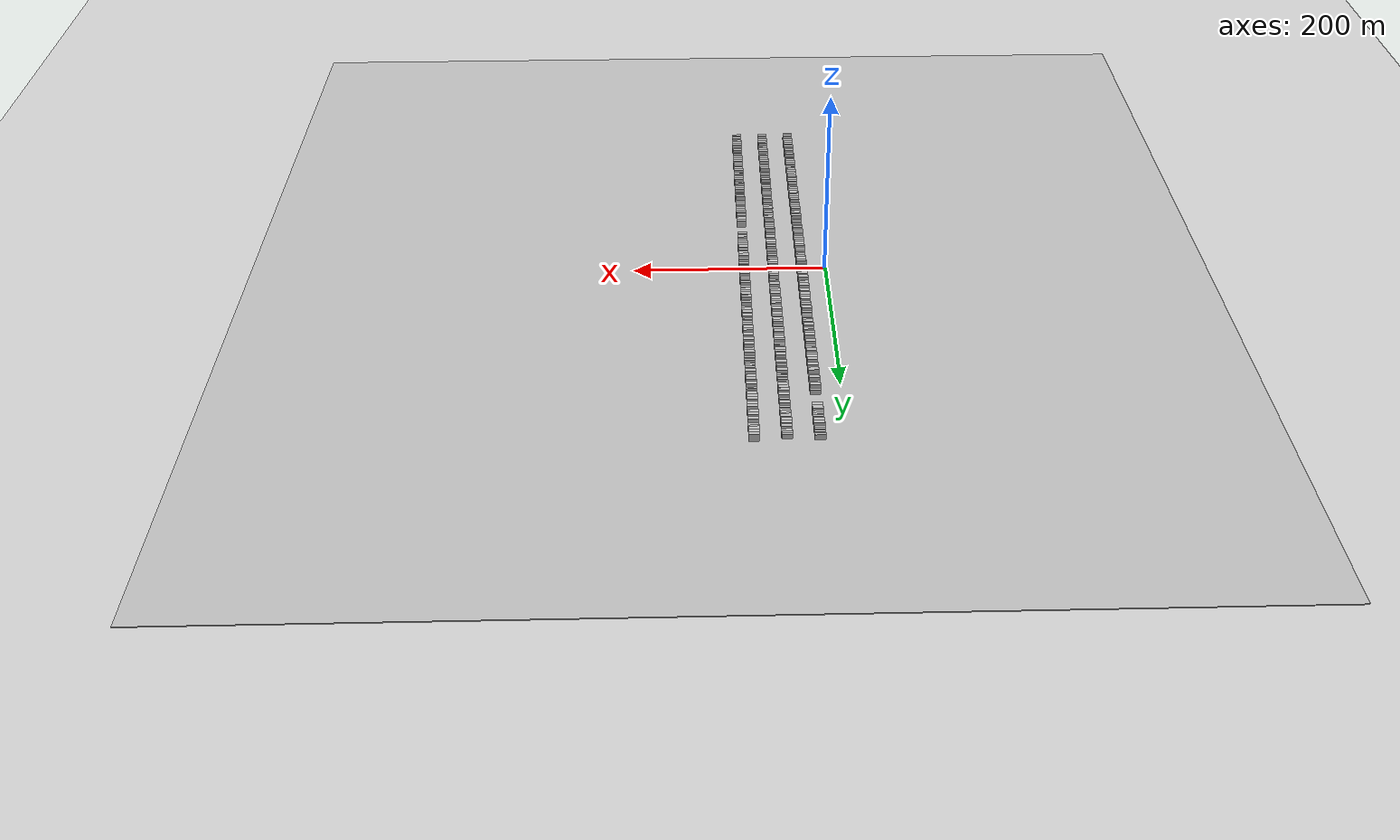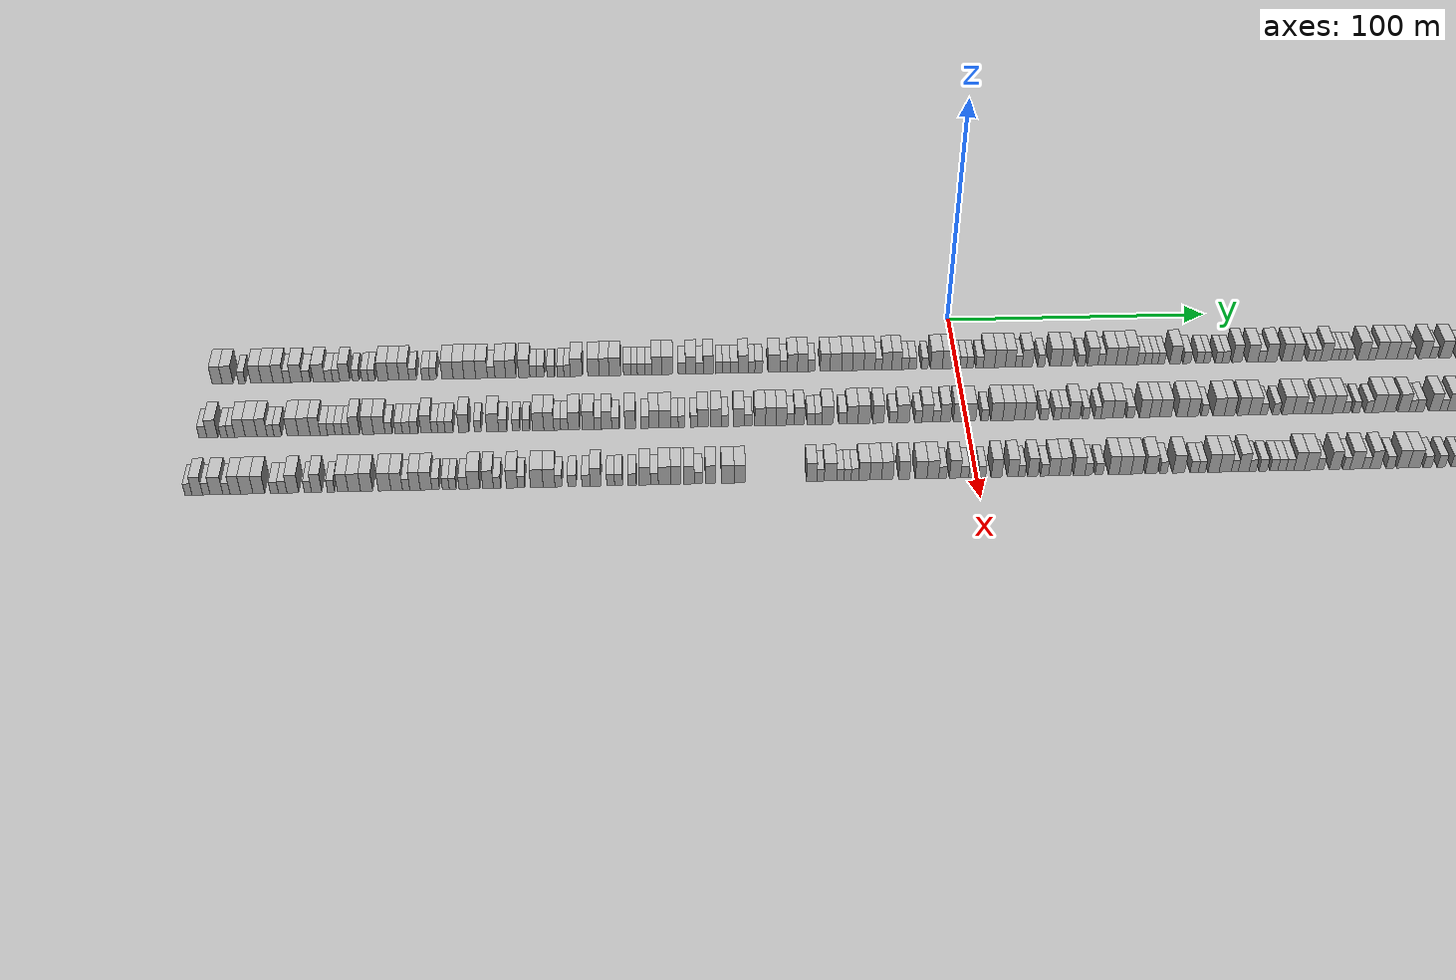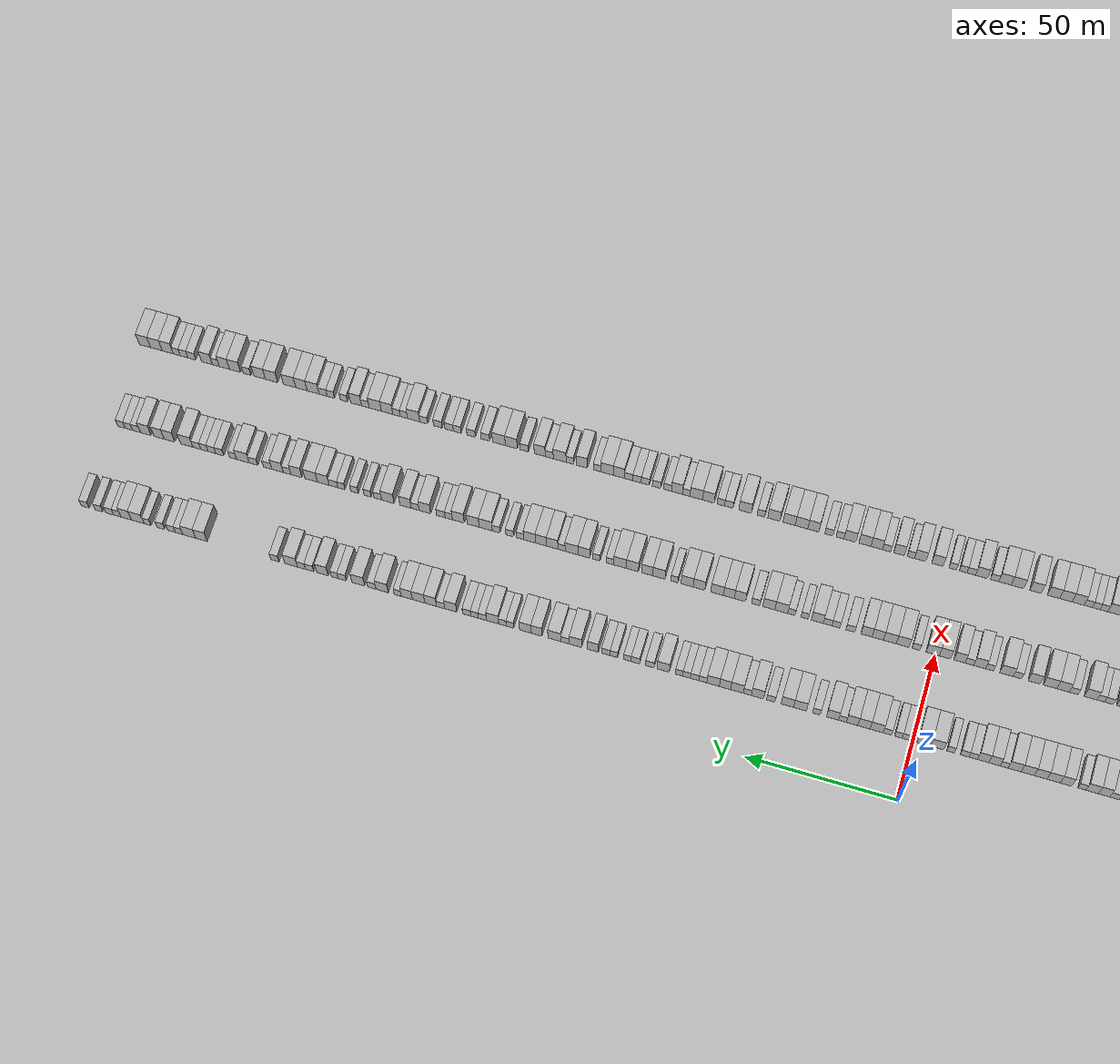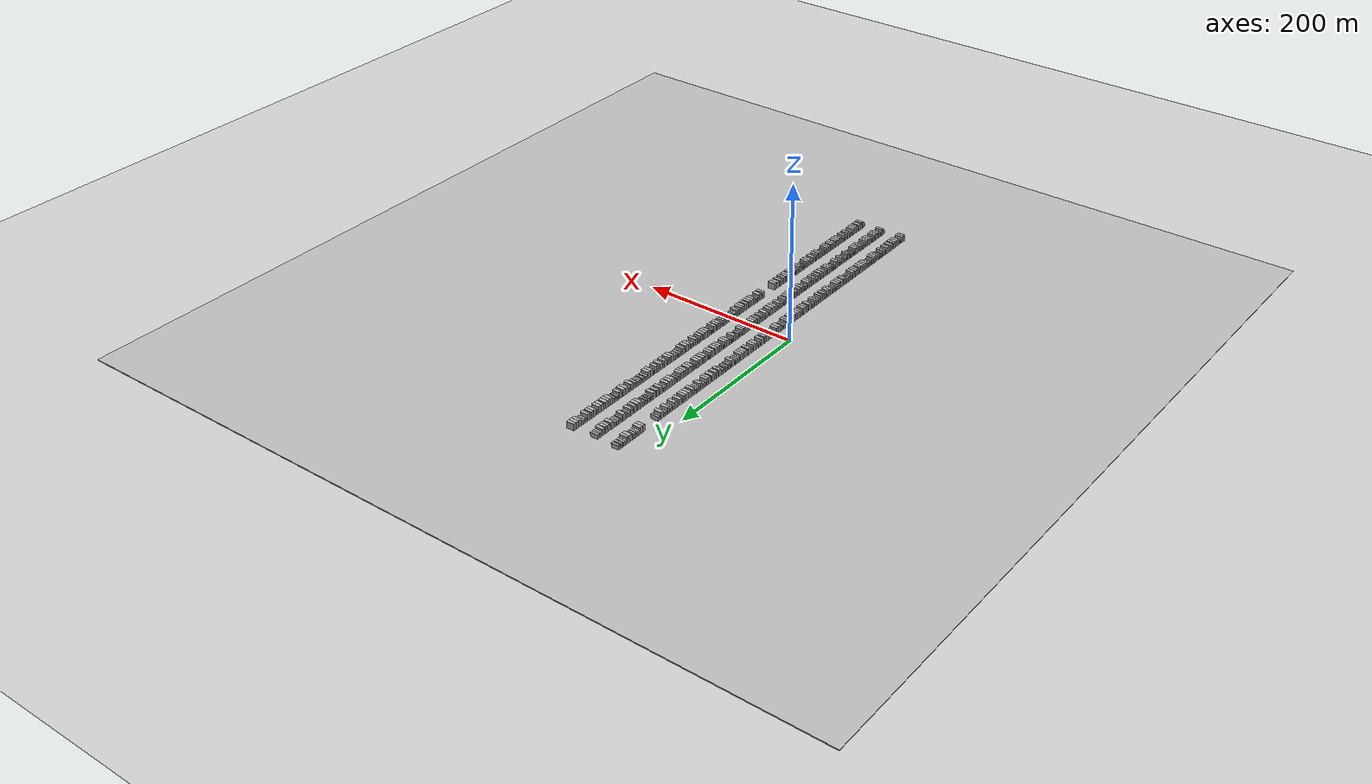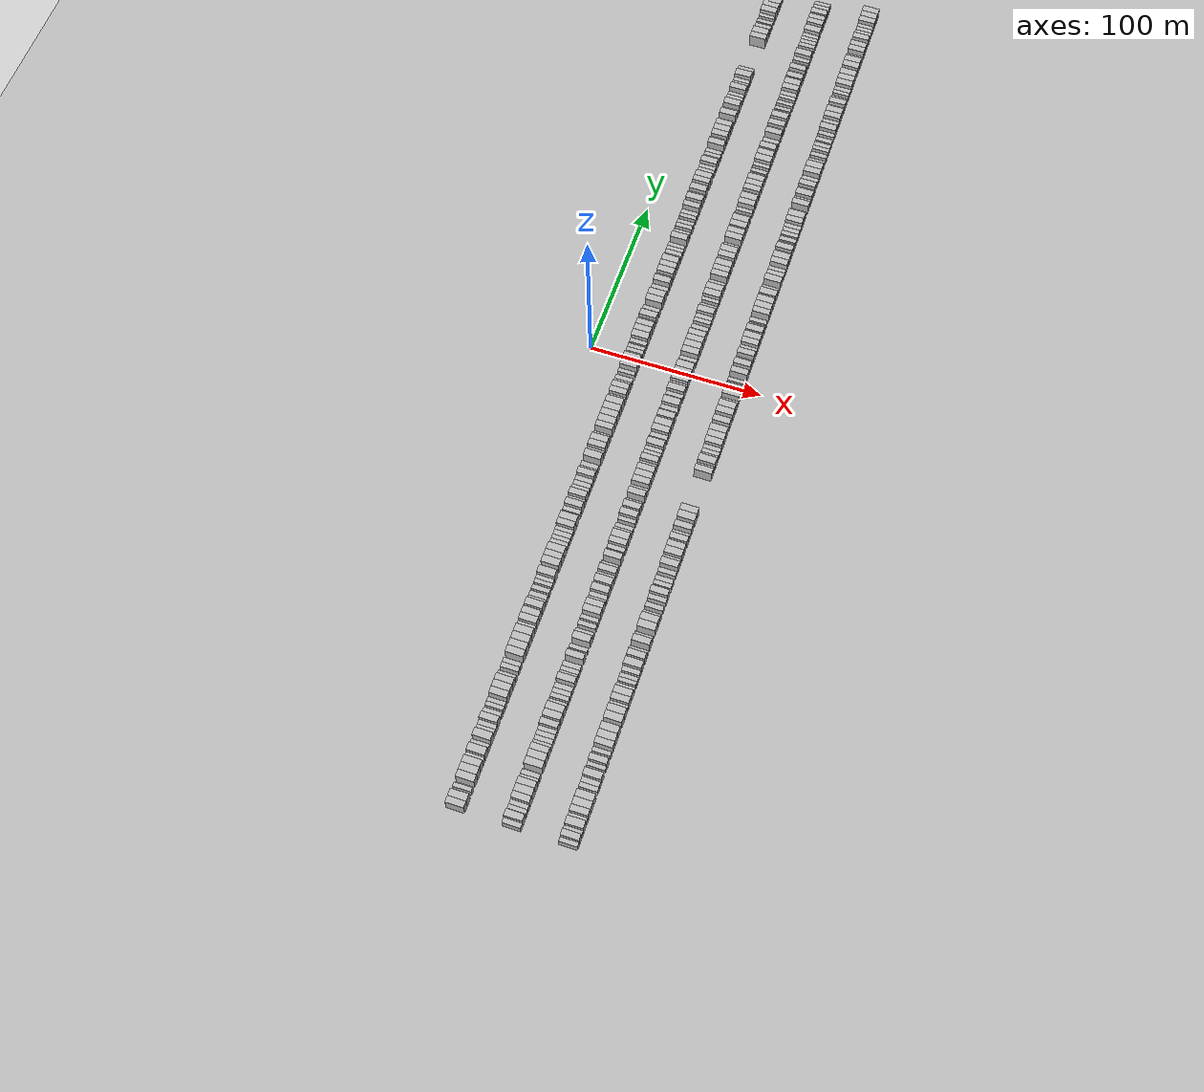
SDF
<?xml version="1.0" encoding="utf-8"?>

<sdf version="1.6">

   <world name="default">

      <gui fullscreen="0">

         <camera name="user_camera">

            <pose>-15 0 4.57585 0 0 0</pose>

            <view_controller>orbit</view_controller>

         </camera>

      </gui>

      <scene>

         <sky>

           <clouds>

             <speed>12</speed>

           </clouds>

         </sky>

         <ambient>0.4 0.4 0.4 1</ambient>

         <background>0.7 0.7 0.7 1</background>

         <shadows>1</shadows>

      </scene>

      <gravity>0 0 -9.8066</gravity>

      <magnetic_field>6e-06 2.3e-05 -4.2e-05</magnetic_field>

      <physics default="0" name="default_physics" type="ode">

         <ode>

            <solver>

               <type>quick</type>

               <iters>10</iters>

               <sor>1.0</sor>

               <use_dynamic_moi_rescaling>0</use_dynamic_moi_rescaling>

            </solver>

            <constraints>

               <cfm>0</cfm>

               <erp>0.2</erp>

               <contact_max_correcting_vel>100</contact_max_correcting_vel>

               <contact_surface_layer>0.001</contact_surface_layer>

            </constraints>

         </ode>

         <max_step_size>0.004</max_step_size>

         <real_time_factor>1</real_time_factor>

         <real_time_update_rate>250</real_time_update_rate>

      </physics>

      <light name="sun" type="directional">

         <cast_shadows>1</cast_shadows>

         <pose>0 0 10 0 0 0</pose>

         <diffuse>0.8 0.8 0.8 1</diffuse>

         <specular>0.2 0.2 0.2 1</specular>

         <attenuation>

            <range>1000</range>

            <constant>0.9</constant>

            <linear>0.01</linear>

            <quadratic>0.001</quadratic>

         </attenuation>

         <direction>-0.5 0.1 -0.9</direction>

      </light>

      <include>

         <name>ground_plane_1</name>

         <uri>model://HANNAS_ground_plane</uri>

         <pose>0 0 0  0 0 0</pose>

      </include>

      <include>

         <name>ground_plane_2</name>

         <uri>model://HANNAS_ground_plane</uri>

         <pose>100 0 0  0 0 0</pose>

      </include>

      <model name="building_1">

         <static>1</static>

         <pose frame="">25.0000 -278.1227 0 0.000000 0.000000 0.000000</pose>

         <link name="link">

            <pose frame="">0 0 4.50 0 0 0</pose>

            <collision name="collision">

               <geometry>

                  <box>

                     <size>10.0000 3.7547 9.0000</size>

                  </box>

               </geometry>

               <max_contacts>10</max_contacts>

               <surface>

                  <contact>

                     <ode/>

                  </contact>

                  <bounce/>

                  <friction>

                     <torsional>

                        <ode/>

                     </torsional>

                     <ode/>

                  </friction>

               </surface>

            </collision>

            <visual name="visual">

               <cast_shadows>0</cast_shadows>

               <geometry>

                  <box>

                     <size>10.0000 3.7547 9.0000</size>

                  </box>

               </geometry>

               <material>

                  <script>

                     <uri>model://HANNAS_wall/materials/scripts</uri>

                     <uri>model://HANNAS_wall/materials/textures</uri>

                     <name>vrc/HANNAS_wall</name>

                  </script>

               </material>

            </visual>

            <self_collide>0</self_collide>

            <enable_wind>0</enable_wind>

            <kinematic>0</kinematic>

         </link>

      </model>

      <model name="building_2">

         <static>1</static>

         <pose frame="">25.0000 -274.1871 0 0.000000 0.000000 0.000000</pose>

         <link name="link">

            <pose frame="">0 0 4.50 0 0 0</pose>

            <collision name="collision">

               <geometry>

                  <box>

                     <size>10.0000 4.1164 9.0000</size>

                  </box>

               </geometry>

               <max_contacts>10</max_contacts>

               <surface>

                  <contact>

                     <ode/>

                  </contact>

                  <bounce/>

                  <friction>

                     <torsional>

                        <ode/>

                     </torsional>

                     <ode/>

                  </friction>

               </surface>

            </collision>

            <visual name="visual">

               <cast_shadows>0</cast_shadows>

               <geometry>

                  <box>

                     <size>10.0000 4.1164 9.0000</size>

                  </box>

               </geometry>

               <material>

                  <script>

                     <uri>model://HANNAS_wall/materials/scripts</uri>

                     <uri>model://HANNAS_wall/materials/textures</uri>

                     <name>vrc/HANNAS_wall</name>

                  </script>

               </material>

            </visual>

            <self_collide>0</self_collide>

            <enable_wind>0</enable_wind>

            <kinematic>0</kinematic>

         </link>

      </model>

      <model name="building_3">

         <static>1</static>

         <pose frame="">25.0000 -268.8763 0 0.000000 0.000000 0.000000</pose>

         <link name="link">

            <pose frame="">0 0 3.00 0 0 0</pose>

            <collision name="collision">

               <geometry>

                  <box>

                     <size>10.0000 2.5053 6.0000</size>

                  </box>

               </geometry>

               <max_contacts>10</max_contacts>

               <surface>

                  <contact>

                     <ode/>

                  </contact>

                  <bounce/>

                  <friction>

                     <torsional>

                        <ode/>

                     </torsional>

                     <ode/>

                  </friction>

               </surface>

            </collision>

            <visual name="visual">

               <cast_shadows>0</cast_shadows>

               <geometry>

                  <box>

                     <size>10.0000 2.5053 6.0000</size>

                  </box>

               </geometry>

               <material>

                  <script>

                     <uri>model://HANNAS_wall/materials/scripts</uri>

                     <uri>model://HANNAS_wall/materials/textures</uri>

                     <name>vrc/HANNAS_wall</name>

                  </script>

               </material>

            </visual>

            <self_collide>0</self_collide>

            <enable_wind>0</enable_wind>

            <kinematic>0</kinematic>

         </link>

      </model>

      <model name="building_4">

         <static>1</static>

         <pose frame="">25.0000 -263.6313 0 0.000000 0.000000 0.000000</pose>

         <link name="link">

            <pose frame="">0 0 4.50 0 0 0</pose>

            <collision name="collision">

               <geometry>

                  <box>

                     <size>10.0000 3.9847 9.0000</size>

                  </box>

               </geometry>

               <max_contacts>10</max_contacts>

               <surface>

                  <contact>

                     <ode/>

                  </contact>

                  <bounce/>

                  <friction>

                     <torsional>

                        <ode/>

                     </torsional>

                     <ode/>

                  </friction>

               </surface>

            </collision>

            <visual name="visual">

               <cast_shadows>0</cast_shadows>

               <geometry>

                  <box>

                     <size>10.0000 3.9847 9.0000</size>

                  </box>

               </geometry>

               <material>

                  <script>

                     <uri>model://HANNAS_wall/materials/scripts</uri>

                     <uri>model://HANNAS_wall/materials/textures</uri>

                     <name>vrc/HANNAS_wall</name>

                  </script>

               </material>

            </visual>

            <self_collide>0</self_collide>

            <enable_wind>0</enable_wind>

            <kinematic>0</kinematic>

         </link>

      </model>

      <model name="building_5">

         <static>1</static>

         <pose frame="">25.0000 -259.4619 0 0.000000 0.000000 0.000000</pose>

         <link name="link">

            <pose frame="">0 0 4.50 0 0 0</pose>

            <collision name="collision">

               <geometry>

                  <box>

                     <size>10.0000 4.3540 9.0000</size>

                  </box>

               </geometry>

               <max_contacts>10</max_contacts>

               <surface>

                  <contact>

                     <ode/>

                  </contact>

                  <bounce/>

                  <friction>

                     <torsional>

                        <ode/>

                     </torsional>

                     <ode/>

                  </friction>

               </surface>

            </collision>

            <visual name="visual">

               <cast_shadows>0</cast_shadows>

               <geometry>

                  <box>

                     <size>10.0000 4.3540 9.0000</size>

                  </box>

               </geometry>

               <material>

                  <script>

                     <uri>model://HANNAS_wall/materials/scripts</uri>

                     <uri>model://HANNAS_wall/materials/textures</uri>

                     <name>vrc/HANNAS_wall</name>

                  </script>

               </material>

            </visual>

            <self_collide>0</self_collide>

            <enable_wind>0</enable_wind>

            <kinematic>0</kinematic>

         </link>

      </model>

      <model name="building_6">

         <static>1</static>

         <pose frame="">25.0000 -255.3037 0 0.000000 0.000000 0.000000</pose>

         <link name="link">

            <pose frame="">0 0 4.50 0 0 0</pose>

            <collision name="collision">

               <geometry>

                  <box>

                     <size>10.0000 3.9626 9.0000</size>

                  </box>

               </geometry>

               <max_contacts>10</max_contacts>

               <surface>

                  <contact>

                     <ode/>

                  </contact>

                  <bounce/>

                  <friction>

                     <torsional>

                        <ode/>

                     </torsional>

                     <ode/>

                  </friction>

               </surface>

            </collision>

            <visual name="visual">

               <cast_shadows>0</cast_shadows>

               <geometry>

                  <box>

                     <size>10.0000 3.9626 9.0000</size>

                  </box>

               </geometry>

               <material>

                  <script>

                     <uri>model://HANNAS_wall/materials/scripts</uri>

                     <uri>model://HANNAS_wall/materials/textures</uri>

                     <name>vrc/HANNAS_wall</name>

                  </script>

               </material>

            </visual>

            <self_collide>0</self_collide>

            <enable_wind>0</enable_wind>

            <kinematic>0</kinematic>

         </link>

      </model>

      <model name="building_7">

         <static>1</static>

         <pose frame="">25.0000 -252.0210 0 0.000000 0.000000 0.000000</pose>

         <link name="link">

            <pose frame="">0 0 3.00 0 0 0</pose>

            <collision name="collision">

               <geometry>

                  <box>

                     <size>10.0000 2.6028 6.0000</size>

                  </box>

               </geometry>

               <max_contacts>10</max_contacts>

               <surface>

                  <contact>

                     <ode/>

                  </contact>

                  <bounce/>

                  <friction>

                     <torsional>

                        <ode/>

                     </torsional>

                     <ode/>

                  </friction>

               </surface>

            </collision>

            <visual name="visual">

               <cast_shadows>0</cast_shadows>

               <geometry>

                  <box>

                     <size>10.0000 2.6028 6.0000</size>

                  </box>

               </geometry>

               <material>

                  <script>

                     <uri>model://HANNAS_wall/materials/scripts</uri>

                     <uri>model://HANNAS_wall/materials/textures</uri>

                     <name>vrc/HANNAS_wall</name>

                  </script>

               </material>

            </visual>

            <self_collide>0</self_collide>

            <enable_wind>0</enable_wind>

            <kinematic>0</kinematic>

         </link>

      </model>

      <model name="building_8">

         <static>1</static>

         <pose frame="">25.0000 -248.4838 0 0.000000 0.000000 0.000000</pose>

         <link name="link">

            <pose frame="">0 0 4.50 0 0 0</pose>

            <collision name="collision">

               <geometry>

                  <box>

                     <size>10.0000 4.4715 9.0000</size>

                  </box>

               </geometry>

               <max_contacts>10</max_contacts>

               <surface>

                  <contact>

                     <ode/>

                  </contact>

                  <bounce/>

                  <friction>

                     <torsional>

                        <ode/>

                     </torsional>

                     <ode/>

                  </friction>

               </surface>

            </collision>

            <visual name="visual">

               <cast_shadows>0</cast_shadows>

               <geometry>

                  <box>

                     <size>10.0000 4.4715 9.0000</size>

                  </box>

               </geometry>

               <material>

                  <script>

                     <uri>model://HANNAS_wall/materials/scripts</uri>

                     <uri>model://HANNAS_wall/materials/textures</uri>

                     <name>vrc/HANNAS_wall</name>

                  </script>

               </material>

            </visual>

            <self_collide>0</self_collide>

            <enable_wind>0</enable_wind>

            <kinematic>0</kinematic>

         </link>

      </model>

      <model name="building_9">

         <static>1</static>

         <pose frame="">25.0000 -244.7733 0 0.000000 0.000000 0.000000</pose>

         <link name="link">

            <pose frame="">0 0 3.00 0 0 0</pose>

            <collision name="collision">

               <geometry>

                  <box>

                     <size>10.0000 2.9496 6.0000</size>

                  </box>

               </geometry>

               <max_contacts>10</max_contacts>

               <surface>

                  <contact>

                     <ode/>

                  </contact>

                  <bounce/>

                  <friction>

                     <torsional>

                        <ode/>

                     </torsional>

                     <ode/>

                  </friction>

               </surface>

            </collision>

            <visual name="visual">

               <cast_shadows>0</cast_shadows>

               <geometry>

                  <box>

                     <size>10.0000 2.9496 6.0000</size>

                  </box>

               </geometry>

               <material>

                  <script>

                     <uri>model://HANNAS_wall/materials/scripts</uri>

                     <uri>model://HANNAS_wall/materials/textures</uri>

                     <name>vrc/HANNAS_wall</name>

                  </script>

               </material>

            </visual>

            <self_collide>0</self_collide>

            <enable_wind>0</enable_wind>

            <kinematic>0</kinematic>

         </link>

      </model>

      <model name="building_10">

         <static>1</static>

         <pose frame="">25.0000 -240.0925 0 0.000000 0.000000 0.000000</pose>

         <link name="link">

            <pose frame="">0 0 4.50 0 0 0</pose>

            <collision name="collision">

               <geometry>

                  <box>

                     <size>10.0000 4.4120 9.0000</size>

                  </box>

               </geometry>

               <max_contacts>10</max_contacts>

               <surface>

                  <contact>

                     <ode/>

                  </contact>

                  <bounce/>

                  <friction>

                     <torsional>

                        <ode/>

                     </torsional>

                     <ode/>

                  </friction>

               </surface>

            </collision>

            <visual name="visual">

               <cast_shadows>0</cast_shadows>

               <geometry>

                  <box>

                     <size>10.0000 4.4120 9.0000</size>

                  </box>

               </geometry>

               <material>

                  <script>

                     <uri>model://HANNAS_wall/materials/scripts</uri>

                     <uri>model://HANNAS_wall/materials/textures</uri>

                     <name>vrc/HANNAS_wall</name>

                  </script>

               </material>

            </visual>

            <self_collide>0</self_collide>

            <enable_wind>0</enable_wind>

            <kinematic>0</kinematic>

         </link>

      </model>

      <model name="building_11">

         <static>1</static>

         <pose frame="">25.0000 -236.4337 0 0.000000 0.000000 0.000000</pose>

         <link name="link">

            <pose frame="">0 0 3.00 0 0 0</pose>

            <collision name="collision">

               <geometry>

                  <box>

                     <size>10.0000 2.9054 6.0000</size>

                  </box>

               </geometry>

               <max_contacts>10</max_contacts>

               <surface>

                  <contact>

                     <ode/>

                  </contact>

                  <bounce/>

                  <friction>

                     <torsional>

                        <ode/>

                     </torsional>

                     <ode/>

                  </friction>

               </surface>

            </collision>

            <visual name="visual">

               <cast_shadows>0</cast_shadows>

               <geometry>

                  <box>

                     <size>10.0000 2.9054 6.0000</size>

                  </box>

               </geometry>

               <material>

                  <script>

                     <uri>model://HANNAS_wall/materials/scripts</uri>

                     <uri>model://HANNAS_wall/materials/textures</uri>

                     <name>vrc/HANNAS_wall</name>

                  </script>

               </material>

            </visual>

            <self_collide>0</self_collide>

            <enable_wind>0</enable_wind>

            <kinematic>0</kinematic>

         </link>

      </model>

      <model name="building_12">

         <static>1</static>

         <pose frame="">25.0000 -233.6554 0 0.000000 0.000000 0.000000</pose>

         <link name="link">

            <pose frame="">0 0 3.00 0 0 0</pose>

            <collision name="collision">

               <geometry>

                  <box>

                     <size>10.0000 2.6513 6.0000</size>

                  </box>

               </geometry>

               <max_contacts>10</max_contacts>

               <surface>

                  <contact>

                     <ode/>

                  </contact>

                  <bounce/>

                  <friction>

                     <torsional>

                        <ode/>

                     </torsional>

                     <ode/>

                  </friction>

               </surface>

            </collision>

            <visual name="visual">

               <cast_shadows>0</cast_shadows>

               <geometry>

                  <box>

                     <size>10.0000 2.6513 6.0000</size>

                  </box>

               </geometry>

               <material>

                  <script>

                     <uri>model://HANNAS_wall/materials/scripts</uri>

                     <uri>model://HANNAS_wall/materials/textures</uri>

                     <name>vrc/HANNAS_wall</name>

                  </script>

               </material>

            </visual>

            <self_collide>0</self_collide>

            <enable_wind>0</enable_wind>

            <kinematic>0</kinematic>

         </link>

      </model>

      <model name="building_13">

         <static>1</static>

         <pose frame="">25.0000 -230.4488 0 0.000000 0.000000 0.000000</pose>

         <link name="link">

            <pose frame="">0 0 4.50 0 0 0</pose>

            <collision name="collision">

               <geometry>

                  <box>

                     <size>10.0000 3.7620 9.0000</size>

                  </box>

               </geometry>

               <max_contacts>10</max_contacts>

               <surface>

                  <contact>

                     <ode/>

                  </contact>

                  <bounce/>

                  <friction>

                     <torsional>

                        <ode/>

                     </torsional>

                     <ode/>

                  </friction>

               </surface>

            </collision>

            <visual name="visual">

               <cast_shadows>0</cast_shadows>

               <geometry>

                  <box>

                     <size>10.0000 3.7620 9.0000</size>

                  </box>

               </geometry>

               <material>

                  <script>

                     <uri>model://HANNAS_wall/materials/scripts</uri>

                     <uri>model://HANNAS_wall/materials/textures</uri>

                     <name>vrc/HANNAS_wall</name>

                  </script>

               </material>

            </visual>

            <self_collide>0</self_collide>

            <enable_wind>0</enable_wind>

            <kinematic>0</kinematic>

         </link>

      </model>

      <model name="building_14">

         <static>1</static>

         <pose frame="">25.0000 -226.3352 0 0.000000 0.000000 0.000000</pose>

         <link name="link">

            <pose frame="">0 0 3.00 0 0 0</pose>

            <collision name="collision">

               <geometry>

                  <box>

                     <size>10.0000 2.4652 6.0000</size>

                  </box>

               </geometry>

               <max_contacts>10</max_contacts>

               <surface>

                  <contact>

                     <ode/>

                  </contact>

                  <bounce/>

                  <friction>

                     <torsional>

                        <ode/>

                     </torsional>

                     <ode/>

                  </friction>

               </surface>

            </collision>

            <visual name="visual">

               <cast_shadows>0</cast_shadows>

               <geometry>

                  <box>

                     <size>10.0000 2.4652 6.0000</size>

                  </box>

               </geometry>

               <material>

                  <script>

                     <uri>model://HANNAS_wall/materials/scripts</uri>

                     <uri>model://HANNAS_wall/materials/textures</uri>

                     <name>vrc/HANNAS_wall</name>

                  </script>

               </material>

            </visual>

            <self_collide>0</self_collide>

            <enable_wind>0</enable_wind>

            <kinematic>0</kinematic>

         </link>

      </model>

      <model name="building_15">

         <static>1</static>

         <pose frame="">25.0000 -222.8802 0 0.000000 0.000000 0.000000</pose>

         <link name="link">

            <pose frame="">0 0 3.00 0 0 0</pose>

            <collision name="collision">

               <geometry>

                  <box>

                     <size>10.0000 2.4448 6.0000</size>

                  </box>

               </geometry>

               <max_contacts>10</max_contacts>

               <surface>

                  <contact>

                     <ode/>

                  </contact>

                  <bounce/>

                  <friction>

                     <torsional>

                        <ode/>

                     </torsional>

                     <ode/>

                  </friction>

               </surface>

            </collision>

            <visual name="visual">

               <cast_shadows>0</cast_shadows>

               <geometry>

                  <box>

                     <size>10.0000 2.4448 6.0000</size>

                  </box>

               </geometry>

               <material>

                  <script>

                     <uri>model://HANNAS_wall/materials/scripts</uri>

                     <uri>model://HANNAS_wall/materials/textures</uri>

                     <name>vrc/HANNAS_wall</name>

                  </script>

               </material>

            </visual>

            <self_collide>0</self_collide>

            <enable_wind>0</enable_wind>

            <kinematic>0</kinematic>

         </link>

      </model>

      <model name="building_16">

         <static>1</static>

         <pose frame="">25.0000 -220.3927 0 0.000000 0.000000 0.000000</pose>

         <link name="link">

            <pose frame="">0 0 3.00 0 0 0</pose>

            <collision name="collision">

               <geometry>

                  <box>

                     <size>10.0000 2.5301 6.0000</size>

                  </box>

               </geometry>

               <max_contacts>10</max_contacts>

               <surface>

                  <contact>

                     <ode/>

                  </contact>

                  <bounce/>

                  <friction>

                     <torsional>

                        <ode/>

                     </torsional>

                     <ode/>

                  </friction>

               </surface>

            </collision>

            <visual name="visual">

               <cast_shadows>0</cast_shadows>

               <geometry>

                  <box>

                     <size>10.0000 2.5301 6.0000</size>

                  </box>

               </geometry>

               <material>

                  <script>

                     <uri>model://HANNAS_wall/materials/scripts</uri>

                     <uri>model://HANNAS_wall/materials/textures</uri>

                     <name>vrc/HANNAS_wall</name>

                  </script>

               </material>

            </visual>

            <self_collide>0</self_collide>

            <enable_wind>0</enable_wind>

            <kinematic>0</kinematic>

         </link>

      </model>

      <model name="building_17">

         <static>1</static>

         <pose frame="">25.0000 -216.1466 0 0.000000 0.000000 0.000000</pose>

         <link name="link">

            <pose frame="">0 0 4.50 0 0 0</pose>

            <collision name="collision">

               <geometry>

                  <box>

                     <size>10.0000 3.9622 9.0000</size>

                  </box>

               </geometry>

               <max_contacts>10</max_contacts>

               <surface>

                  <contact>

                     <ode/>

                  </contact>

                  <bounce/>

                  <friction>

                     <torsional>

                        <ode/>

                     </torsional>

                     <ode/>

                  </friction>

               </surface>

            </collision>

            <visual name="visual">

               <cast_shadows>0</cast_shadows>

               <geometry>

                  <box>

                     <size>10.0000 3.9622 9.0000</size>

                  </box>

               </geometry>

               <material>

                  <script>

                     <uri>model://HANNAS_wall/materials/scripts</uri>

                     <uri>model://HANNAS_wall/materials/textures</uri>

                     <name>vrc/HANNAS_wall</name>

                  </script>

               </material>

            </visual>

            <self_collide>0</self_collide>

            <enable_wind>0</enable_wind>

            <kinematic>0</kinematic>

         </link>

      </model>

      <model name="building_18">

         <static>1</static>

         <pose frame="">25.0000 -212.1476 0 0.000000 0.000000 0.000000</pose>

         <link name="link">

            <pose frame="">0 0 4.50 0 0 0</pose>

            <collision name="collision">

               <geometry>

                  <box>

                     <size>10.0000 4.0357 9.0000</size>

                  </box>

               </geometry>

               <max_contacts>10</max_contacts>

               <surface>

                  <contact>

                     <ode/>

                  </contact>

                  <bounce/>

                  <friction>

                     <torsional>

                        <ode/>

                     </torsional>

                     <ode/>

                  </friction>

               </surface>

            </collision>

            <visual name="visual">

               <cast_shadows>0</cast_shadows>

               <geometry>

                  <box>

                     <size>10.0000 4.0357 9.0000</size>

                  </box>

               </geometry>

               <material>

                  <script>

                     <uri>model://HANNAS_wall/materials/scripts</uri>

                     <uri>model://HANNAS_wall/materials/textures</uri>

                     <name>vrc/HANNAS_wall</name>

                  </script>

               </material>

            </visual>

            <self_collide>0</self_collide>

            <enable_wind>0</enable_wind>

            <kinematic>0</kinematic>

         </link>

      </model>

      <model name="building_19">

         <static>1</static>

         <pose frame="">25.0000 -208.2879 0 0.000000 0.000000 0.000000</pose>

         <link name="link">

            <pose frame="">0 0 4.50 0 0 0</pose>

            <collision name="collision">

               <geometry>

                  <box>

                     <size>10.0000 3.6838 9.0000</size>

                  </box>

               </geometry>

               <max_contacts>10</max_contacts>

               <surface>

                  <contact>

                     <ode/>

                  </contact>

                  <bounce/>

                  <friction>

                     <torsional>

                        <ode/>

                     </torsional>

                     <ode/>

                  </friction>

               </surface>

            </collision>

            <visual name="visual">

               <cast_shadows>0</cast_shadows>

               <geometry>

                  <box>

                     <size>10.0000 3.6838 9.0000</size>

                  </box>

               </geometry>

               <material>

                  <script>

                     <uri>model://HANNAS_wall/materials/scripts</uri>

                     <uri>model://HANNAS_wall/materials/textures</uri>

                     <name>vrc/HANNAS_wall</name>

                  </script>

               </material>

            </visual>

            <self_collide>0</self_collide>

            <enable_wind>0</enable_wind>

            <kinematic>0</kinematic>

         </link>

      </model>

      <model name="building_20">

         <static>1</static>

         <pose frame="">25.0000 -205.0399 0 0.000000 0.000000 0.000000</pose>

         <link name="link">

            <pose frame="">0 0 3.00 0 0 0</pose>

            <collision name="collision">

               <geometry>

                  <box>

                     <size>10.0000 2.8122 6.0000</size>

                  </box>

               </geometry>

               <max_contacts>10</max_contacts>

               <surface>

                  <contact>

                     <ode/>

                  </contact>

                  <bounce/>

                  <friction>

                     <torsional>

                        <ode/>

                     </torsional>

                     <ode/>

                  </friction>

               </surface>

            </collision>

            <visual name="visual">

               <cast_shadows>0</cast_shadows>

               <geometry>

                  <box>

                     <size>10.0000 2.8122 6.0000</size>

                  </box>

               </geometry>

               <material>

                  <script>

                     <uri>model://HANNAS_wall/materials/scripts</uri>

                     <uri>model://HANNAS_wall/materials/textures</uri>

                     <name>vrc/HANNAS_wall</name>

                  </script>

               </material>

            </visual>

            <self_collide>0</self_collide>

            <enable_wind>0</enable_wind>

            <kinematic>0</kinematic>

         </link>

      </model>

      <model name="building_21">

         <static>1</static>

         <pose frame="">25.0000 -200.1960 0 0.000000 0.000000 0.000000</pose>

         <link name="link">

            <pose frame="">0 0 3.00 0 0 0</pose>

            <collision name="collision">

               <geometry>

                  <box>

                     <size>10.0000 2.8756 6.0000</size>

                  </box>

               </geometry>

               <max_contacts>10</max_contacts>

               <surface>

                  <contact>

                     <ode/>

                  </contact>

                  <bounce/>

                  <friction>

                     <torsional>

                        <ode/>

                     </torsional>

                     <ode/>

                  </friction>

               </surface>

            </collision>

            <visual name="visual">

               <cast_shadows>0</cast_shadows>

               <geometry>

                  <box>

                     <size>10.0000 2.8756 6.0000</size>

                  </box>

               </geometry>

               <material>

                  <script>

                     <uri>model://HANNAS_wall/materials/scripts</uri>

                     <uri>model://HANNAS_wall/materials/textures</uri>

                     <name>vrc/HANNAS_wall</name>

                  </script>

               </material>

            </visual>

            <self_collide>0</self_collide>

            <enable_wind>0</enable_wind>

            <kinematic>0</kinematic>

         </link>

      </model>

      <model name="building_22">

         <static>1</static>

         <pose frame="">25.0000 -197.4250 0 0.000000 0.000000 0.000000</pose>

         <link name="link">

            <pose frame="">0 0 3.00 0 0 0</pose>

            <collision name="collision">

               <geometry>

                  <box>

                     <size>10.0000 2.6663 6.0000</size>

                  </box>

               </geometry>

               <max_contacts>10</max_contacts>

               <surface>

                  <contact>

                     <ode/>

                  </contact>

                  <bounce/>

                  <friction>

                     <torsional>

                        <ode/>

                     </torsional>

                     <ode/>

                  </friction>

               </surface>

            </collision>

            <visual name="visual">

               <cast_shadows>0</cast_shadows>

               <geometry>

                  <box>

                     <size>10.0000 2.6663 6.0000</size>

                  </box>

               </geometry>

               <material>

                  <script>

                     <uri>model://HANNAS_wall/materials/scripts</uri>

                     <uri>model://HANNAS_wall/materials/textures</uri>

                     <name>vrc/HANNAS_wall</name>

                  </script>

               </material>

            </visual>

            <self_collide>0</self_collide>

            <enable_wind>0</enable_wind>

            <kinematic>0</kinematic>

         </link>

      </model>

      <model name="building_23">

         <static>1</static>

         <pose frame="">25.0000 -192.0048 0 0.000000 0.000000 0.000000</pose>

         <link name="link">

            <pose frame="">0 0 4.50 0 0 0</pose>

            <collision name="collision">

               <geometry>

                  <box>

                     <size>10.0000 4.1742 9.0000</size>

                  </box>

               </geometry>

               <max_contacts>10</max_contacts>

               <surface>

                  <contact>

                     <ode/>

                  </contact>

                  <bounce/>

                  <friction>

                     <torsional>

                        <ode/>

                     </torsional>

                     <ode/>

                  </friction>

               </surface>

            </collision>

            <visual name="visual">

               <cast_shadows>0</cast_shadows>

               <geometry>

                  <box>

                     <size>10.0000 4.1742 9.0000</size>

                  </box>

               </geometry>

               <material>

                  <script>

                     <uri>model://HANNAS_wall/materials/scripts</uri>

                     <uri>model://HANNAS_wall/materials/textures</uri>

                     <name>vrc/HANNAS_wall</name>

                  </script>

               </material>

            </visual>

            <self_collide>0</self_collide>

            <enable_wind>0</enable_wind>

            <kinematic>0</kinematic>

         </link>

      </model>

      <model name="building_24">

         <static>1</static>

         <pose frame="">25.0000 -187.8908 0 0.000000 0.000000 0.000000</pose>

         <link name="link">

            <pose frame="">0 0 4.50 0 0 0</pose>

            <collision name="collision">

               <geometry>

                  <box>

                     <size>10.0000 4.0538 9.0000</size>

                  </box>

               </geometry>

               <max_contacts>10</max_contacts>

               <surface>

                  <contact>

                     <ode/>

                  </contact>

                  <bounce/>

                  <friction>

                     <torsional>

                        <ode/>

                     </torsional>

                     <ode/>

                  </friction>

               </surface>

            </collision>

            <visual name="visual">

               <cast_shadows>0</cast_shadows>

               <geometry>

                  <box>

                     <size>10.0000 4.0538 9.0000</size>

                  </box>

               </geometry>

               <material>

                  <script>

                     <uri>model://HANNAS_wall/materials/scripts</uri>

                     <uri>model://HANNAS_wall/materials/textures</uri>

                     <name>vrc/HANNAS_wall</name>

                  </script>

               </material>

            </visual>

            <self_collide>0</self_collide>

            <enable_wind>0</enable_wind>

            <kinematic>0</kinematic>

         </link>

      </model>

      <model name="building_25">

         <static>1</static>

         <pose frame="">25.0000 -183.6626 0 0.000000 0.000000 0.000000</pose>

         <link name="link">

            <pose frame="">0 0 4.50 0 0 0</pose>

            <collision name="collision">

               <geometry>

                  <box>

                     <size>10.0000 4.4026 9.0000</size>

                  </box>

               </geometry>

               <max_contacts>10</max_contacts>

               <surface>

                  <contact>

                     <ode/>

                  </contact>

                  <bounce/>

                  <friction>

                     <torsional>

                        <ode/>

                     </torsional>

                     <ode/>

                  </friction>

               </surface>

            </collision>

            <visual name="visual">

               <cast_shadows>0</cast_shadows>

               <geometry>

                  <box>

                     <size>10.0000 4.4026 9.0000</size>

                  </box>

               </geometry>

               <material>

                  <script>

                     <uri>model://HANNAS_wall/materials/scripts</uri>

                     <uri>model://HANNAS_wall/materials/textures</uri>

                     <name>vrc/HANNAS_wall</name>

                  </script>

               </material>

            </visual>

            <self_collide>0</self_collide>

            <enable_wind>0</enable_wind>

            <kinematic>0</kinematic>

         </link>

      </model>

      <model name="building_26">

         <static>1</static>

         <pose frame="">25.0000 -179.2650 0 0.000000 0.000000 0.000000</pose>

         <link name="link">

            <pose frame="">0 0 4.50 0 0 0</pose>

            <collision name="collision">

               <geometry>

                  <box>

                     <size>10.0000 4.3926 9.0000</size>

                  </box>

               </geometry>

               <max_contacts>10</max_contacts>

               <surface>

                  <contact>

                     <ode/>

                  </contact>

                  <bounce/>

                  <friction>

                     <torsional>

                        <ode/>

                     </torsional>

                     <ode/>

                  </friction>

               </surface>

            </collision>

            <visual name="visual">

               <cast_shadows>0</cast_shadows>

               <geometry>

                  <box>

                     <size>10.0000 4.3926 9.0000</size>

                  </box>

               </geometry>

               <material>

                  <script>

                     <uri>model://HANNAS_wall/materials/scripts</uri>

                     <uri>model://HANNAS_wall/materials/textures</uri>

                     <name>vrc/HANNAS_wall</name>

                  </script>

               </material>

            </visual>

            <self_collide>0</self_collide>

            <enable_wind>0</enable_wind>

            <kinematic>0</kinematic>

         </link>

      </model>

      <model name="building_27">

         <static>1</static>

         <pose frame="">25.0000 -175.6454 0 0.000000 0.000000 0.000000</pose>

         <link name="link">

            <pose frame="">0 0 3.00 0 0 0</pose>

            <collision name="collision">

               <geometry>

                  <box>

                     <size>10.0000 2.8465 6.0000</size>

                  </box>

               </geometry>

               <max_contacts>10</max_contacts>

               <surface>

                  <contact>

                     <ode/>

                  </contact>

                  <bounce/>

                  <friction>

                     <torsional>

                        <ode/>

                     </torsional>

                     <ode/>

                  </friction>

               </surface>

            </collision>

            <visual name="visual">

               <cast_shadows>0</cast_shadows>

               <geometry>

                  <box>

                     <size>10.0000 2.8465 6.0000</size>

                  </box>

               </geometry>

               <material>

                  <script>

                     <uri>model://HANNAS_wall/materials/scripts</uri>

                     <uri>model://HANNAS_wall/materials/textures</uri>

                     <name>vrc/HANNAS_wall</name>

                  </script>

               </material>

            </visual>

            <self_collide>0</self_collide>

            <enable_wind>0</enable_wind>

            <kinematic>0</kinematic>

         </link>

      </model>

      <model name="building_28">

         <static>1</static>

         <pose frame="">25.0000 -172.2202 0 0.000000 0.000000 0.000000</pose>

         <link name="link">

            <pose frame="">0 0 4.50 0 0 0</pose>

            <collision name="collision">

               <geometry>

                  <box>

                     <size>10.0000 4.0040 9.0000</size>

                  </box>

               </geometry>

               <max_contacts>10</max_contacts>

               <surface>

                  <contact>

                     <ode/>

                  </contact>

                  <bounce/>

                  <friction>

                     <torsional>

                        <ode/>

                     </torsional>

                     <ode/>

                  </friction>

               </surface>

            </collision>

            <visual name="visual">

               <cast_shadows>0</cast_shadows>

               <geometry>

                  <box>

                     <size>10.0000 4.0040 9.0000</size>

                  </box>

               </geometry>

               <material>

                  <script>

                     <uri>model://HANNAS_wall/materials/scripts</uri>

                     <uri>model://HANNAS_wall/materials/textures</uri>

                     <name>vrc/HANNAS_wall</name>

                  </script>

               </material>

            </visual>

            <self_collide>0</self_collide>

            <enable_wind>0</enable_wind>

            <kinematic>0</kinematic>

         </link>

      </model>

      <model name="building_29">

         <static>1</static>

         <pose frame="">25.0000 -168.2735 0 0.000000 0.000000 0.000000</pose>

         <link name="link">

            <pose frame="">0 0 4.50 0 0 0</pose>

            <collision name="collision">

               <geometry>

                  <box>

                     <size>10.0000 3.8893 9.0000</size>

                  </box>

               </geometry>

               <max_contacts>10</max_contacts>

               <surface>

                  <contact>

                     <ode/>

                  </contact>

                  <bounce/>

                  <friction>

                     <torsional>

                        <ode/>

                     </torsional>

                     <ode/>

                  </friction>

               </surface>

            </collision>

            <visual name="visual">

               <cast_shadows>0</cast_shadows>

               <geometry>

                  <box>

                     <size>10.0000 3.8893 9.0000</size>

                  </box>

               </geometry>

               <material>

                  <script>

                     <uri>model://HANNAS_wall/materials/scripts</uri>

                     <uri>model://HANNAS_wall/materials/textures</uri>

                     <name>vrc/HANNAS_wall</name>

                  </script>

               </material>

            </visual>

            <self_collide>0</self_collide>

            <enable_wind>0</enable_wind>

            <kinematic>0</kinematic>

         </link>

      </model>

      <model name="building_30">

         <static>1</static>

         <pose frame="">25.0000 -163.2446 0 0.000000 0.000000 0.000000</pose>

         <link name="link">

            <pose frame="">0 0 4.50 0 0 0</pose>

            <collision name="collision">

               <geometry>

                  <box>

                     <size>10.0000 4.1687 9.0000</size>

                  </box>

               </geometry>

               <max_contacts>10</max_contacts>

               <surface>

                  <contact>

                     <ode/>

                  </contact>

                  <bounce/>

                  <friction>

                     <torsional>

                        <ode/>

                     </torsional>

                     <ode/>

                  </friction>

               </surface>

            </collision>

            <visual name="visual">

               <cast_shadows>0</cast_shadows>

               <geometry>

                  <box>

                     <size>10.0000 4.1687 9.0000</size>

                  </box>

               </geometry>

               <material>

                  <script>

                     <uri>model://HANNAS_wall/materials/scripts</uri>

                     <uri>model://HANNAS_wall/materials/textures</uri>

                     <name>vrc/HANNAS_wall</name>

                  </script>

               </material>

            </visual>

            <self_collide>0</self_collide>

            <enable_wind>0</enable_wind>

            <kinematic>0</kinematic>

         </link>

      </model>

      <model name="building_31">

         <static>1</static>

         <pose frame="">25.0000 -159.8994 0 0.000000 0.000000 0.000000</pose>

         <link name="link">

            <pose frame="">0 0 3.00 0 0 0</pose>

            <collision name="collision">

               <geometry>

                  <box>

                     <size>10.0000 2.5216 6.0000</size>

                  </box>

               </geometry>

               <max_contacts>10</max_contacts>

               <surface>

                  <contact>

                     <ode/>

                  </contact>

                  <bounce/>

                  <friction>

                     <torsional>

                        <ode/>

                     </torsional>

                     <ode/>

                  </friction>

               </surface>

            </collision>

            <visual name="visual">

               <cast_shadows>0</cast_shadows>

               <geometry>

                  <box>

                     <size>10.0000 2.5216 6.0000</size>

                  </box>

               </geometry>

               <material>

                  <script>

                     <uri>model://HANNAS_wall/materials/scripts</uri>

                     <uri>model://HANNAS_wall/materials/textures</uri>

                     <name>vrc/HANNAS_wall</name>

                  </script>

               </material>

            </visual>

            <self_collide>0</self_collide>

            <enable_wind>0</enable_wind>

            <kinematic>0</kinematic>

         </link>

      </model>

      <model name="building_32">

         <static>1</static>

         <pose frame="">25.0000 -157.1717 0 0.000000 0.000000 0.000000</pose>

         <link name="link">

            <pose frame="">0 0 3.00 0 0 0</pose>

            <collision name="collision">

               <geometry>

                  <box>

                     <size>10.0000 2.9339 6.0000</size>

                  </box>

               </geometry>

               <max_contacts>10</max_contacts>

               <surface>

                  <contact>

                     <ode/>

                  </contact>

                  <bounce/>

                  <friction>

                     <torsional>

                        <ode/>

                     </torsional>

                     <ode/>

                  </friction>

               </surface>

            </collision>

            <visual name="visual">

               <cast_shadows>0</cast_shadows>

               <geometry>

                  <box>

                     <size>10.0000 2.9339 6.0000</size>

                  </box>

               </geometry>

               <material>

                  <script>

                     <uri>model://HANNAS_wall/materials/scripts</uri>

                     <uri>model://HANNAS_wall/materials/textures</uri>

                     <name>vrc/HANNAS_wall</name>

                  </script>

               </material>

            </visual>

            <self_collide>0</self_collide>

            <enable_wind>0</enable_wind>

            <kinematic>0</kinematic>

         </link>

      </model>

      <model name="building_33">

         <static>1</static>

         <pose frame="">25.0000 -153.2829 0 0.000000 0.000000 0.000000</pose>

         <link name="link">

            <pose frame="">0 0 3.00 0 0 0</pose>

            <collision name="collision">

               <geometry>

                  <box>

                     <size>10.0000 2.8436 6.0000</size>

                  </box>

               </geometry>

               <max_contacts>10</max_contacts>

               <surface>

                  <contact>

                     <ode/>

                  </contact>

                  <bounce/>

                  <friction>

                     <torsional>

                        <ode/>

                     </torsional>

                     <ode/>

                  </friction>

               </surface>

            </collision>

            <visual name="visual">

               <cast_shadows>0</cast_shadows>

               <geometry>

                  <box>

                     <size>10.0000 2.8436 6.0000</size>

                  </box>

               </geometry>

               <material>

                  <script>

                     <uri>model://HANNAS_wall/materials/scripts</uri>

                     <uri>model://HANNAS_wall/materials/textures</uri>

                     <name>vrc/HANNAS_wall</name>

                  </script>

               </material>

            </visual>

            <self_collide>0</self_collide>

            <enable_wind>0</enable_wind>

            <kinematic>0</kinematic>

         </link>

      </model>

      <model name="building_34">

         <static>1</static>

         <pose frame="">25.0000 -149.6134 0 0.000000 0.000000 0.000000</pose>

         <link name="link">

            <pose frame="">0 0 3.00 0 0 0</pose>

            <collision name="collision">

               <geometry>

                  <box>

                     <size>10.0000 2.4956 6.0000</size>

                  </box>

               </geometry>

               <max_contacts>10</max_contacts>

               <surface>

                  <contact>

                     <ode/>

                  </contact>

                  <bounce/>

                  <friction>

                     <torsional>

                        <ode/>

                     </torsional>

                     <ode/>

                  </friction>

               </surface>

            </collision>

            <visual name="visual">

               <cast_shadows>0</cast_shadows>

               <geometry>

                  <box>

                     <size>10.0000 2.4956 6.0000</size>

                  </box>

               </geometry>

               <material>

                  <script>

                     <uri>model://HANNAS_wall/materials/scripts</uri>

                     <uri>model://HANNAS_wall/materials/textures</uri>

                     <name>vrc/HANNAS_wall</name>

                  </script>

               </material>

            </visual>

            <self_collide>0</self_collide>

            <enable_wind>0</enable_wind>

            <kinematic>0</kinematic>

         </link>

      </model>

      <model name="building_35">

         <static>1</static>

         <pose frame="">25.0000 -147.1456 0 0.000000 0.000000 0.000000</pose>

         <link name="link">

            <pose frame="">0 0 3.00 0 0 0</pose>

            <collision name="collision">

               <geometry>

                  <box>

                     <size>10.0000 2.4400 6.0000</size>

                  </box>

               </geometry>

               <max_contacts>10</max_contacts>

               <surface>

                  <contact>

                     <ode/>

                  </contact>

                  <bounce/>

                  <friction>

                     <torsional>

                        <ode/>

                     </torsional>

                     <ode/>

                  </friction>

               </surface>

            </collision>

            <visual name="visual">

               <cast_shadows>0</cast_shadows>

               <geometry>

                  <box>

                     <size>10.0000 2.4400 6.0000</size>

                  </box>

               </geometry>

               <material>

                  <script>

                     <uri>model://HANNAS_wall/materials/scripts</uri>

                     <uri>model://HANNAS_wall/materials/textures</uri>

                     <name>vrc/HANNAS_wall</name>

                  </script>

               </material>

            </visual>

            <self_collide>0</self_collide>

            <enable_wind>0</enable_wind>

            <kinematic>0</kinematic>

         </link>

      </model>

      <model name="building_36">

         <static>1</static>

         <pose frame="">25.0000 -143.6759 0 0.000000 0.000000 0.000000</pose>

         <link name="link">

            <pose frame="">0 0 4.50 0 0 0</pose>

            <collision name="collision">

               <geometry>

                  <box>

                     <size>10.0000 4.4996 9.0000</size>

                  </box>

               </geometry>

               <max_contacts>10</max_contacts>

               <surface>

                  <contact>

                     <ode/>

                  </contact>

                  <bounce/>

                  <friction>

                     <torsional>

                        <ode/>

                     </torsional>

                     <ode/>

                  </friction>

               </surface>

            </collision>

            <visual name="visual">

               <cast_shadows>0</cast_shadows>

               <geometry>

                  <box>

                     <size>10.0000 4.4996 9.0000</size>

                  </box>

               </geometry>

               <material>

                  <script>

                     <uri>model://HANNAS_wall/materials/scripts</uri>

                     <uri>model://HANNAS_wall/materials/textures</uri>

                     <name>vrc/HANNAS_wall</name>

                  </script>

               </material>

            </visual>

            <self_collide>0</self_collide>

            <enable_wind>0</enable_wind>

            <kinematic>0</kinematic>

         </link>

      </model>

      <model name="building_37">

         <static>1</static>

         <pose frame="">25.0000 -137.2518 0 0.000000 0.000000 0.000000</pose>

         <link name="link">

            <pose frame="">0 0 4.50 0 0 0</pose>

            <collision name="collision">

               <geometry>

                  <box>

                     <size>10.0000 4.3485 9.0000</size>

                  </box>

               </geometry>

               <max_contacts>10</max_contacts>

               <surface>

                  <contact>

                     <ode/>

                  </contact>

                  <bounce/>

                  <friction>

                     <torsional>

                        <ode/>

                     </torsional>

                     <ode/>

                  </friction>

               </surface>

            </collision>

            <visual name="visual">

               <cast_shadows>0</cast_shadows>

               <geometry>

                  <box>

                     <size>10.0000 4.3485 9.0000</size>

                  </box>

               </geometry>

               <material>

                  <script>

                     <uri>model://HANNAS_wall/materials/scripts</uri>

                     <uri>model://HANNAS_wall/materials/textures</uri>

                     <name>vrc/HANNAS_wall</name>

                  </script>

               </material>

            </visual>

            <self_collide>0</self_collide>

            <enable_wind>0</enable_wind>

            <kinematic>0</kinematic>

         </link>

      </model>

      <model name="building_38">

         <static>1</static>

         <pose frame="">25.0000 -133.2338 0 0.000000 0.000000 0.000000</pose>

         <link name="link">

            <pose frame="">0 0 4.50 0 0 0</pose>

            <collision name="collision">

               <geometry>

                  <box>

                     <size>10.0000 3.6876 9.0000</size>

                  </box>

               </geometry>

               <max_contacts>10</max_contacts>

               <surface>

                  <contact>

                     <ode/>

                  </contact>

                  <bounce/>

                  <friction>

                     <torsional>

                        <ode/>

                     </torsional>

                     <ode/>

                  </friction>

               </surface>

            </collision>

            <visual name="visual">

               <cast_shadows>0</cast_shadows>

               <geometry>

                  <box>

                     <size>10.0000 3.6876 9.0000</size>

                  </box>

               </geometry>

               <material>

                  <script>

                     <uri>model://HANNAS_wall/materials/scripts</uri>

                     <uri>model://HANNAS_wall/materials/textures</uri>

                     <name>vrc/HANNAS_wall</name>

                  </script>

               </material>

            </visual>

            <self_collide>0</self_collide>

            <enable_wind>0</enable_wind>

            <kinematic>0</kinematic>

         </link>

      </model>

      <model name="building_39">

         <static>1</static>

         <pose frame="">25.0000 -129.1908 0 0.000000 0.000000 0.000000</pose>

         <link name="link">

            <pose frame="">0 0 4.50 0 0 0</pose>

            <collision name="collision">

               <geometry>

                  <box>

                     <size>10.0000 4.3983 9.0000</size>

                  </box>

               </geometry>

               <max_contacts>10</max_contacts>

               <surface>

                  <contact>

                     <ode/>

                  </contact>

                  <bounce/>

                  <friction>

                     <torsional>

                        <ode/>

                     </torsional>

                     <ode/>

                  </friction>

               </surface>

            </collision>

            <visual name="visual">

               <cast_shadows>0</cast_shadows>

               <geometry>

                  <box>

                     <size>10.0000 4.3983 9.0000</size>

                  </box>

               </geometry>

               <material>

                  <script>

                     <uri>model://HANNAS_wall/materials/scripts</uri>

                     <uri>model://HANNAS_wall/materials/textures</uri>

                     <name>vrc/HANNAS_wall</name>

                  </script>

               </material>

            </visual>

            <self_collide>0</self_collide>

            <enable_wind>0</enable_wind>

            <kinematic>0</kinematic>

         </link>

      </model>

      <model name="building_40">

         <static>1</static>

         <pose frame="">25.0000 -124.6098 0 0.000000 0.000000 0.000000</pose>

         <link name="link">

            <pose frame="">0 0 3.00 0 0 0</pose>

            <collision name="collision">

               <geometry>

                  <box>

                     <size>10.0000 2.7636 6.0000</size>

                  </box>

               </geometry>

               <max_contacts>10</max_contacts>

               <surface>

                  <contact>

                     <ode/>

                  </contact>

                  <bounce/>

                  <friction>

                     <torsional>

                        <ode/>

                     </torsional>

                     <ode/>

                  </friction>

               </surface>

            </collision>

            <visual name="visual">

               <cast_shadows>0</cast_shadows>

               <geometry>

                  <box>

                     <size>10.0000 2.7636 6.0000</size>

                  </box>

               </geometry>

               <material>

                  <script>

                     <uri>model://HANNAS_wall/materials/scripts</uri>

                     <uri>model://HANNAS_wall/materials/textures</uri>

                     <name>vrc/HANNAS_wall</name>

                  </script>

               </material>

            </visual>

            <self_collide>0</self_collide>

            <enable_wind>0</enable_wind>

            <kinematic>0</kinematic>

         </link>

      </model>

      <model name="building_41">

         <static>1</static>

         <pose frame="">25.0000 -121.9932 0 0.000000 0.000000 0.000000</pose>

         <link name="link">

            <pose frame="">0 0 3.00 0 0 0</pose>

            <collision name="collision">

               <geometry>

                  <box>

                     <size>10.0000 2.4697 6.0000</size>

                  </box>

               </geometry>

               <max_contacts>10</max_contacts>

               <surface>

                  <contact>

                     <ode/>

                  </contact>

                  <bounce/>

                  <friction>

                     <torsional>

                        <ode/>

                     </torsional>

                     <ode/>

                  </friction>

               </surface>

            </collision>

            <visual name="visual">

               <cast_shadows>0</cast_shadows>

               <geometry>

                  <box>

                     <size>10.0000 2.4697 6.0000</size>

                  </box>

               </geometry>

               <material>

                  <script>

                     <uri>model://HANNAS_wall/materials/scripts</uri>

                     <uri>model://HANNAS_wall/materials/textures</uri>

                     <name>vrc/HANNAS_wall</name>

                  </script>

               </material>

            </visual>

            <self_collide>0</self_collide>

            <enable_wind>0</enable_wind>

            <kinematic>0</kinematic>

         </link>

      </model>

      <model name="building_42">

         <static>1</static>

         <pose frame="">25.0000 -119.2757 0 0.000000 0.000000 0.000000</pose>

         <link name="link">

            <pose frame="">0 0 3.00 0 0 0</pose>

            <collision name="collision">

               <geometry>

                  <box>

                     <size>10.0000 2.9653 6.0000</size>

                  </box>

               </geometry>

               <max_contacts>10</max_contacts>

               <surface>

                  <contact>

                     <ode/>

                  </contact>

                  <bounce/>

                  <friction>

                     <torsional>

                        <ode/>

                     </torsional>

                     <ode/>

                  </friction>

               </surface>

            </collision>

            <visual name="visual">

               <cast_shadows>0</cast_shadows>

               <geometry>

                  <box>

                     <size>10.0000 2.9653 6.0000</size>

                  </box>

               </geometry>

               <material>

                  <script>

                     <uri>model://HANNAS_wall/materials/scripts</uri>

                     <uri>model://HANNAS_wall/materials/textures</uri>

                     <name>vrc/HANNAS_wall</name>

                  </script>

               </material>

            </visual>

            <self_collide>0</self_collide>

            <enable_wind>0</enable_wind>

            <kinematic>0</kinematic>

         </link>

      </model>

      <model name="building_43">

         <static>1</static>

         <pose frame="">25.0000 -116.5713 0 0.000000 0.000000 0.000000</pose>

         <link name="link">

            <pose frame="">0 0 3.00 0 0 0</pose>

            <collision name="collision">

               <geometry>

                  <box>

                     <size>10.0000 2.4435 6.0000</size>

                  </box>

               </geometry>

               <max_contacts>10</max_contacts>

               <surface>

                  <contact>

                     <ode/>

                  </contact>

                  <bounce/>

                  <friction>

                     <torsional>

                        <ode/>

                     </torsional>

                     <ode/>

                  </friction>

               </surface>

            </collision>

            <visual name="visual">

               <cast_shadows>0</cast_shadows>

               <geometry>

                  <box>

                     <size>10.0000 2.4435 6.0000</size>

                  </box>

               </geometry>

               <material>

                  <script>

                     <uri>model://HANNAS_wall/materials/scripts</uri>

                     <uri>model://HANNAS_wall/materials/textures</uri>

                     <name>vrc/HANNAS_wall</name>

                  </script>

               </material>

            </visual>

            <self_collide>0</self_collide>

            <enable_wind>0</enable_wind>

            <kinematic>0</kinematic>

         </link>

      </model>

      <model name="building_44">

         <static>1</static>

         <pose frame="">25.0000 -113.4763 0 0.000000 0.000000 0.000000</pose>

         <link name="link">

            <pose frame="">0 0 4.50 0 0 0</pose>

            <collision name="collision">

               <geometry>

                  <box>

                     <size>10.0000 3.7466 9.0000</size>

                  </box>

               </geometry>

               <max_contacts>10</max_contacts>

               <surface>

                  <contact>

                     <ode/>

                  </contact>

                  <bounce/>

                  <friction>

                     <torsional>

                        <ode/>

                     </torsional>

                     <ode/>

                  </friction>

               </surface>

            </collision>

            <visual name="visual">

               <cast_shadows>0</cast_shadows>

               <geometry>

                  <box>

                     <size>10.0000 3.7466 9.0000</size>

                  </box>

               </geometry>

               <material>

                  <script>

                     <uri>model://HANNAS_wall/materials/scripts</uri>

                     <uri>model://HANNAS_wall/materials/textures</uri>

                     <name>vrc/HANNAS_wall</name>

                  </script>

               </material>

            </visual>

            <self_collide>0</self_collide>

            <enable_wind>0</enable_wind>

            <kinematic>0</kinematic>

         </link>

      </model>

      <model name="building_45">

         <static>1</static>

         <pose frame="">25.0000 -109.5024 0 0.000000 0.000000 0.000000</pose>

         <link name="link">

            <pose frame="">0 0 4.50 0 0 0</pose>

            <collision name="collision">

               <geometry>

                  <box>

                     <size>10.0000 4.2012 9.0000</size>

                  </box>

               </geometry>

               <max_contacts>10</max_contacts>

               <surface>

                  <contact>

                     <ode/>

                  </contact>

                  <bounce/>

                  <friction>

                     <torsional>

                        <ode/>

                     </torsional>

                     <ode/>

                  </friction>

               </surface>

            </collision>

            <visual name="visual">

               <cast_shadows>0</cast_shadows>

               <geometry>

                  <box>

                     <size>10.0000 4.2012 9.0000</size>

                  </box>

               </geometry>

               <material>

                  <script>

                     <uri>model://HANNAS_wall/materials/scripts</uri>

                     <uri>model://HANNAS_wall/materials/textures</uri>

                     <name>vrc/HANNAS_wall</name>

                  </script>

               </material>

            </visual>

            <self_collide>0</self_collide>

            <enable_wind>0</enable_wind>

            <kinematic>0</kinematic>

         </link>

      </model>

      <model name="building_46">

         <static>1</static>

         <pose frame="">25.0000 -104.0156 0 0.000000 0.000000 0.000000</pose>

         <link name="link">

            <pose frame="">0 0 3.00 0 0 0</pose>

            <collision name="collision">

               <geometry>

                  <box>

                     <size>10.0000 2.7725 6.0000</size>

                  </box>

               </geometry>

               <max_contacts>10</max_contacts>

               <surface>

                  <contact>

                     <ode/>

                  </contact>

                  <bounce/>

                  <friction>

                     <torsional>

                        <ode/>

                     </torsional>

                     <ode/>

                  </friction>

               </surface>

            </collision>

            <visual name="visual">

               <cast_shadows>0</cast_shadows>

               <geometry>

                  <box>

                     <size>10.0000 2.7725 6.0000</size>

                  </box>

               </geometry>

               <material>

                  <script>

                     <uri>model://HANNAS_wall/materials/scripts</uri>

                     <uri>model://HANNAS_wall/materials/textures</uri>

                     <name>vrc/HANNAS_wall</name>

                  </script>

               </material>

            </visual>

            <self_collide>0</self_collide>

            <enable_wind>0</enable_wind>

            <kinematic>0</kinematic>

         </link>

      </model>

      <model name="building_47">

         <static>1</static>

         <pose frame="">25.0000 -100.6625 0 0.000000 0.000000 0.000000</pose>

         <link name="link">

            <pose frame="">0 0 4.50 0 0 0</pose>

            <collision name="collision">

               <geometry>

                  <box>

                     <size>10.0000 3.9337 9.0000</size>

                  </box>

               </geometry>

               <max_contacts>10</max_contacts>

               <surface>

                  <contact>

                     <ode/>

                  </contact>

                  <bounce/>

                  <friction>

                     <torsional>

                        <ode/>

                     </torsional>

                     <ode/>

                  </friction>

               </surface>

            </collision>

            <visual name="visual">

               <cast_shadows>0</cast_shadows>

               <geometry>

                  <box>

                     <size>10.0000 3.9337 9.0000</size>

                  </box>

               </geometry>

               <material>

                  <script>

                     <uri>model://HANNAS_wall/materials/scripts</uri>

                     <uri>model://HANNAS_wall/materials/textures</uri>

                     <name>vrc/HANNAS_wall</name>

                  </script>

               </material>

            </visual>

            <self_collide>0</self_collide>

            <enable_wind>0</enable_wind>

            <kinematic>0</kinematic>

         </link>

      </model>

      <model name="building_48">

         <static>1</static>

         <pose frame="">25.0000 -97.3295 0 0.000000 0.000000 0.000000</pose>

         <link name="link">

            <pose frame="">0 0 3.00 0 0 0</pose>

            <collision name="collision">

               <geometry>

                  <box>

                     <size>10.0000 2.7321 6.0000</size>

                  </box>

               </geometry>

               <max_contacts>10</max_contacts>

               <surface>

                  <contact>

                     <ode/>

                  </contact>

                  <bounce/>

                  <friction>

                     <torsional>

                        <ode/>

                     </torsional>

                     <ode/>

                  </friction>

               </surface>

            </collision>

            <visual name="visual">

               <cast_shadows>0</cast_shadows>

               <geometry>

                  <box>

                     <size>10.0000 2.7321 6.0000</size>

                  </box>

               </geometry>

               <material>

                  <script>

                     <uri>model://HANNAS_wall/materials/scripts</uri>

                     <uri>model://HANNAS_wall/materials/textures</uri>

                     <name>vrc/HANNAS_wall</name>

                  </script>

               </material>

            </visual>

            <self_collide>0</self_collide>

            <enable_wind>0</enable_wind>

            <kinematic>0</kinematic>

         </link>

      </model>

      <model name="building_49">

         <static>1</static>

         <pose frame="">25.0000 -94.0868 0 0.000000 0.000000 0.000000</pose>

         <link name="link">

            <pose frame="">0 0 4.50 0 0 0</pose>

            <collision name="collision">

               <geometry>

                  <box>

                     <size>10.0000 3.7533 9.0000</size>

                  </box>

               </geometry>

               <max_contacts>10</max_contacts>

               <surface>

                  <contact>

                     <ode/>

                  </contact>

                  <bounce/>

                  <friction>

                     <torsional>

                        <ode/>

                     </torsional>

                     <ode/>

                  </friction>

               </surface>

            </collision>

            <visual name="visual">

               <cast_shadows>0</cast_shadows>

               <geometry>

                  <box>

                     <size>10.0000 3.7533 9.0000</size>

                  </box>

               </geometry>

               <material>

                  <script>

                     <uri>model://HANNAS_wall/materials/scripts</uri>

                     <uri>model://HANNAS_wall/materials/textures</uri>

                     <name>vrc/HANNAS_wall</name>

                  </script>

               </material>

            </visual>

            <self_collide>0</self_collide>

            <enable_wind>0</enable_wind>

            <kinematic>0</kinematic>

         </link>

      </model>

      <model name="building_50">

         <static>1</static>

         <pose frame="">25.0000 -89.9725 0 0.000000 0.000000 0.000000</pose>

         <link name="link">

            <pose frame="">0 0 3.00 0 0 0</pose>

            <collision name="collision">

               <geometry>

                  <box>

                     <size>10.0000 2.4754 6.0000</size>

                  </box>

               </geometry>

               <max_contacts>10</max_contacts>

               <surface>

                  <contact>

                     <ode/>

                  </contact>

                  <bounce/>

                  <friction>

                     <torsional>

                        <ode/>

                     </torsional>

                     <ode/>

                  </friction>

               </surface>

            </collision>

            <visual name="visual">

               <cast_shadows>0</cast_shadows>

               <geometry>

                  <box>

                     <size>10.0000 2.4754 6.0000</size>

                  </box>

               </geometry>

               <material>

                  <script>

                     <uri>model://HANNAS_wall/materials/scripts</uri>

                     <uri>model://HANNAS_wall/materials/textures</uri>

                     <name>vrc/HANNAS_wall</name>

                  </script>

               </material>

            </visual>

            <self_collide>0</self_collide>

            <enable_wind>0</enable_wind>

            <kinematic>0</kinematic>

         </link>

      </model>

      <model name="building_51">

         <static>1</static>

         <pose frame="">25.0000 -87.2771 0 0.000000 0.000000 0.000000</pose>

         <link name="link">

            <pose frame="">0 0 3.00 0 0 0</pose>

            <collision name="collision">

               <geometry>

                  <box>

                     <size>10.0000 2.9154 6.0000</size>

                  </box>

               </geometry>

               <max_contacts>10</max_contacts>

               <surface>

                  <contact>

                     <ode/>

                  </contact>

                  <bounce/>

                  <friction>

                     <torsional>

                        <ode/>

                     </torsional>

                     <ode/>

                  </friction>

               </surface>

            </collision>

            <visual name="visual">

               <cast_shadows>0</cast_shadows>

               <geometry>

                  <box>

                     <size>10.0000 2.9154 6.0000</size>

                  </box>

               </geometry>

               <material>

                  <script>

                     <uri>model://HANNAS_wall/materials/scripts</uri>

                     <uri>model://HANNAS_wall/materials/textures</uri>

                     <name>vrc/HANNAS_wall</name>

                  </script>

               </material>

            </visual>

            <self_collide>0</self_collide>

            <enable_wind>0</enable_wind>

            <kinematic>0</kinematic>

         </link>

      </model>

      <model name="building_52">

         <static>1</static>

         <pose frame="">25.0000 -84.3198 0 0.000000 0.000000 0.000000</pose>

         <link name="link">

            <pose frame="">0 0 3.00 0 0 0</pose>

            <collision name="collision">

               <geometry>

                  <box>

                     <size>10.0000 2.9992 6.0000</size>

                  </box>

               </geometry>

               <max_contacts>10</max_contacts>

               <surface>

                  <contact>

                     <ode/>

                  </contact>

                  <bounce/>

                  <friction>

                     <torsional>

                        <ode/>

                     </torsional>

                     <ode/>

                  </friction>

               </surface>

            </collision>

            <visual name="visual">

               <cast_shadows>0</cast_shadows>

               <geometry>

                  <box>

                     <size>10.0000 2.9992 6.0000</size>

                  </box>

               </geometry>

               <material>

                  <script>

                     <uri>model://HANNAS_wall/materials/scripts</uri>

                     <uri>model://HANNAS_wall/materials/textures</uri>

                     <name>vrc/HANNAS_wall</name>

                  </script>

               </material>

            </visual>

            <self_collide>0</self_collide>

            <enable_wind>0</enable_wind>

            <kinematic>0</kinematic>

         </link>

      </model>

      <model name="building_53">

         <static>1</static>

         <pose frame="">25.0000 -80.9112 0 0.000000 0.000000 0.000000</pose>

         <link name="link">

            <pose frame="">0 0 4.50 0 0 0</pose>

            <collision name="collision">

               <geometry>

                  <box>

                     <size>10.0000 3.8180 9.0000</size>

                  </box>

               </geometry>

               <max_contacts>10</max_contacts>

               <surface>

                  <contact>

                     <ode/>

                  </contact>

                  <bounce/>

                  <friction>

                     <torsional>

                        <ode/>

                     </torsional>

                     <ode/>

                  </friction>

               </surface>

            </collision>

            <visual name="visual">

               <cast_shadows>0</cast_shadows>

               <geometry>

                  <box>

                     <size>10.0000 3.8180 9.0000</size>

                  </box>

               </geometry>

               <material>

                  <script>

                     <uri>model://HANNAS_wall/materials/scripts</uri>

                     <uri>model://HANNAS_wall/materials/textures</uri>

                     <name>vrc/HANNAS_wall</name>

                  </script>

               </material>

            </visual>

            <self_collide>0</self_collide>

            <enable_wind>0</enable_wind>

            <kinematic>0</kinematic>

         </link>

      </model>

      <model name="building_54">

         <static>1</static>

         <pose frame="">25.0000 -77.7514 0 0.000000 0.000000 0.000000</pose>

         <link name="link">

            <pose frame="">0 0 3.00 0 0 0</pose>

            <collision name="collision">

               <geometry>

                  <box>

                     <size>10.0000 2.5016 6.0000</size>

                  </box>

               </geometry>

               <max_contacts>10</max_contacts>

               <surface>

                  <contact>

                     <ode/>

                  </contact>

                  <bounce/>

                  <friction>

                     <torsional>

                        <ode/>

                     </torsional>

                     <ode/>

                  </friction>

               </surface>

            </collision>

            <visual name="visual">

               <cast_shadows>0</cast_shadows>

               <geometry>

                  <box>

                     <size>10.0000 2.5016 6.0000</size>

                  </box>

               </geometry>

               <material>

                  <script>

                     <uri>model://HANNAS_wall/materials/scripts</uri>

                     <uri>model://HANNAS_wall/materials/textures</uri>

                     <name>vrc/HANNAS_wall</name>

                  </script>

               </material>

            </visual>

            <self_collide>0</self_collide>

            <enable_wind>0</enable_wind>

            <kinematic>0</kinematic>

         </link>

      </model>

      <model name="building_55">

         <static>1</static>

         <pose frame="">25.0000 -75.0186 0 0.000000 0.000000 0.000000</pose>

         <link name="link">

            <pose frame="">0 0 3.00 0 0 0</pose>

            <collision name="collision">

               <geometry>

                  <box>

                     <size>10.0000 2.9640 6.0000</size>

                  </box>

               </geometry>

               <max_contacts>10</max_contacts>

               <surface>

                  <contact>

                     <ode/>

                  </contact>

                  <bounce/>

                  <friction>

                     <torsional>

                        <ode/>

                     </torsional>

                     <ode/>

                  </friction>

               </surface>

            </collision>

            <visual name="visual">

               <cast_shadows>0</cast_shadows>

               <geometry>

                  <box>

                     <size>10.0000 2.9640 6.0000</size>

                  </box>

               </geometry>

               <material>

                  <script>

                     <uri>model://HANNAS_wall/materials/scripts</uri>

                     <uri>model://HANNAS_wall/materials/textures</uri>

                     <name>vrc/HANNAS_wall</name>

                  </script>

               </material>

            </visual>

            <self_collide>0</self_collide>

            <enable_wind>0</enable_wind>

            <kinematic>0</kinematic>

         </link>

      </model>

      <model name="building_56">

         <static>1</static>

         <pose frame="">25.0000 -69.3119 0 0.000000 0.000000 0.000000</pose>

         <link name="link">

            <pose frame="">0 0 4.50 0 0 0</pose>

            <collision name="collision">

               <geometry>

                  <box>

                     <size>10.0000 4.4494 9.0000</size>

                  </box>

               </geometry>

               <max_contacts>10</max_contacts>

               <surface>

                  <contact>

                     <ode/>

                  </contact>

                  <bounce/>

                  <friction>

                     <torsional>

                        <ode/>

                     </torsional>

                     <ode/>

                  </friction>

               </surface>

            </collision>

            <visual name="visual">

               <cast_shadows>0</cast_shadows>

               <geometry>

                  <box>

                     <size>10.0000 4.4494 9.0000</size>

                  </box>

               </geometry>

               <material>

                  <script>

                     <uri>model://HANNAS_wall/materials/scripts</uri>

                     <uri>model://HANNAS_wall/materials/textures</uri>

                     <name>vrc/HANNAS_wall</name>

                  </script>

               </material>

            </visual>

            <self_collide>0</self_collide>

            <enable_wind>0</enable_wind>

            <kinematic>0</kinematic>

         </link>

      </model>

      <model name="building_57">

         <static>1</static>

         <pose frame="">25.0000 -65.6506 0 0.000000 0.000000 0.000000</pose>

         <link name="link">

            <pose frame="">0 0 3.00 0 0 0</pose>

            <collision name="collision">

               <geometry>

                  <box>

                     <size>10.0000 2.8732 6.0000</size>

                  </box>

               </geometry>

               <max_contacts>10</max_contacts>

               <surface>

                  <contact>

                     <ode/>

                  </contact>

                  <bounce/>

                  <friction>

                     <torsional>

                        <ode/>

                     </torsional>

                     <ode/>

                  </friction>

               </surface>

            </collision>

            <visual name="visual">

               <cast_shadows>0</cast_shadows>

               <geometry>

                  <box>

                     <size>10.0000 2.8732 6.0000</size>

                  </box>

               </geometry>

               <material>

                  <script>

                     <uri>model://HANNAS_wall/materials/scripts</uri>

                     <uri>model://HANNAS_wall/materials/textures</uri>

                     <name>vrc/HANNAS_wall</name>

                  </script>

               </material>

            </visual>

            <self_collide>0</self_collide>

            <enable_wind>0</enable_wind>

            <kinematic>0</kinematic>

         </link>

      </model>

      <model name="building_58">

         <static>1</static>

         <pose frame="">25.0000 -62.3224 0 0.000000 0.000000 0.000000</pose>

         <link name="link">

            <pose frame="">0 0 4.50 0 0 0</pose>

            <collision name="collision">

               <geometry>

                  <box>

                     <size>10.0000 3.7832 9.0000</size>

                  </box>

               </geometry>

               <max_contacts>10</max_contacts>

               <surface>

                  <contact>

                     <ode/>

                  </contact>

                  <bounce/>

                  <friction>

                     <torsional>

                        <ode/>

                     </torsional>

                     <ode/>

                  </friction>

               </surface>

            </collision>

            <visual name="visual">

               <cast_shadows>0</cast_shadows>

               <geometry>

                  <box>

                     <size>10.0000 3.7832 9.0000</size>

                  </box>

               </geometry>

               <material>

                  <script>

                     <uri>model://HANNAS_wall/materials/scripts</uri>

                     <uri>model://HANNAS_wall/materials/textures</uri>

                     <name>vrc/HANNAS_wall</name>

                  </script>

               </material>

            </visual>

            <self_collide>0</self_collide>

            <enable_wind>0</enable_wind>

            <kinematic>0</kinematic>

         </link>

      </model>

      <model name="building_59">

         <static>1</static>

         <pose frame="">25.0000 -58.4330 0 0.000000 0.000000 0.000000</pose>

         <link name="link">

            <pose frame="">0 0 4.50 0 0 0</pose>

            <collision name="collision">

               <geometry>

                  <box>

                     <size>10.0000 3.9956 9.0000</size>

                  </box>

               </geometry>

               <max_contacts>10</max_contacts>

               <surface>

                  <contact>

                     <ode/>

                  </contact>

                  <bounce/>

                  <friction>

                     <torsional>

                        <ode/>

                     </torsional>

                     <ode/>

                  </friction>

               </surface>

            </collision>

            <visual name="visual">

               <cast_shadows>0</cast_shadows>

               <geometry>

                  <box>

                     <size>10.0000 3.9956 9.0000</size>

                  </box>

               </geometry>

               <material>

                  <script>

                     <uri>model://HANNAS_wall/materials/scripts</uri>

                     <uri>model://HANNAS_wall/materials/textures</uri>

                     <name>vrc/HANNAS_wall</name>

                  </script>

               </material>

            </visual>

            <self_collide>0</self_collide>

            <enable_wind>0</enable_wind>

            <kinematic>0</kinematic>

         </link>

      </model>

      <model name="building_60">

         <static>1</static>

         <pose frame="">25.0000 -55.1191 0 0.000000 0.000000 0.000000</pose>

         <link name="link">

            <pose frame="">0 0 3.00 0 0 0</pose>

            <collision name="collision">

               <geometry>

                  <box>

                     <size>10.0000 2.6323 6.0000</size>

                  </box>

               </geometry>

               <max_contacts>10</max_contacts>

               <surface>

                  <contact>

                     <ode/>

                  </contact>

                  <bounce/>

                  <friction>

                     <torsional>

                        <ode/>

                     </torsional>

                     <ode/>

                  </friction>

               </surface>

            </collision>

            <visual name="visual">

               <cast_shadows>0</cast_shadows>

               <geometry>

                  <box>

                     <size>10.0000 2.6323 6.0000</size>

                  </box>

               </geometry>

               <material>

                  <script>

                     <uri>model://HANNAS_wall/materials/scripts</uri>

                     <uri>model://HANNAS_wall/materials/textures</uri>

                     <name>vrc/HANNAS_wall</name>

                  </script>

               </material>

            </visual>

            <self_collide>0</self_collide>

            <enable_wind>0</enable_wind>

            <kinematic>0</kinematic>

         </link>

      </model>

      <model name="building_61">

         <static>1</static>

         <pose frame="">25.0000 -49.9609 0 0.000000 0.000000 0.000000</pose>

         <link name="link">

            <pose frame="">0 0 4.50 0 0 0</pose>

            <collision name="collision">

               <geometry>

                  <box>

                     <size>10.0000 3.6841 9.0000</size>

                  </box>

               </geometry>

               <max_contacts>10</max_contacts>

               <surface>

                  <contact>

                     <ode/>

                  </contact>

                  <bounce/>

                  <friction>

                     <torsional>

                        <ode/>

                     </torsional>

                     <ode/>

                  </friction>

               </surface>

            </collision>

            <visual name="visual">

               <cast_shadows>0</cast_shadows>

               <geometry>

                  <box>

                     <size>10.0000 3.6841 9.0000</size>

                  </box>

               </geometry>

               <material>

                  <script>

                     <uri>model://HANNAS_wall/materials/scripts</uri>

                     <uri>model://HANNAS_wall/materials/textures</uri>

                     <name>vrc/HANNAS_wall</name>

                  </script>

               </material>

            </visual>

            <self_collide>0</self_collide>

            <enable_wind>0</enable_wind>

            <kinematic>0</kinematic>

         </link>

      </model>

      <model name="building_62">

         <static>1</static>

         <pose frame="">25.0000 -45.9126 0 0.000000 0.000000 0.000000</pose>

         <link name="link">

            <pose frame="">0 0 4.50 0 0 0</pose>

            <collision name="collision">

               <geometry>

                  <box>

                     <size>10.0000 4.4127 9.0000</size>

                  </box>

               </geometry>

               <max_contacts>10</max_contacts>

               <surface>

                  <contact>

                     <ode/>

                  </contact>

                  <bounce/>

                  <friction>

                     <torsional>

                        <ode/>

                     </torsional>

                     <ode/>

                  </friction>

               </surface>

            </collision>

            <visual name="visual">

               <cast_shadows>0</cast_shadows>

               <geometry>

                  <box>

                     <size>10.0000 4.4127 9.0000</size>

                  </box>

               </geometry>

               <material>

                  <script>

                     <uri>model://HANNAS_wall/materials/scripts</uri>

                     <uri>model://HANNAS_wall/materials/textures</uri>

                     <name>vrc/HANNAS_wall</name>

                  </script>

               </material>

            </visual>

            <self_collide>0</self_collide>

            <enable_wind>0</enable_wind>

            <kinematic>0</kinematic>

         </link>

      </model>

      <model name="building_63">

         <static>1</static>

         <pose frame="">25.0000 -41.6601 0 0.000000 0.000000 0.000000</pose>

         <link name="link">

            <pose frame="">0 0 4.50 0 0 0</pose>

            <collision name="collision">

               <geometry>

                  <box>

                     <size>10.0000 4.0923 9.0000</size>

                  </box>

               </geometry>

               <max_contacts>10</max_contacts>

               <surface>

                  <contact>

                     <ode/>

                  </contact>

                  <bounce/>

                  <friction>

                     <torsional>

                        <ode/>

                     </torsional>

                     <ode/>

                  </friction>

               </surface>

            </collision>

            <visual name="visual">

               <cast_shadows>0</cast_shadows>

               <geometry>

                  <box>

                     <size>10.0000 4.0923 9.0000</size>

                  </box>

               </geometry>

               <material>

                  <script>

                     <uri>model://HANNAS_wall/materials/scripts</uri>

                     <uri>model://HANNAS_wall/materials/textures</uri>

                     <name>vrc/HANNAS_wall</name>

                  </script>

               </material>

            </visual>

            <self_collide>0</self_collide>

            <enable_wind>0</enable_wind>

            <kinematic>0</kinematic>

         </link>

      </model>

      <model name="building_64">

         <static>1</static>

         <pose frame="">25.0000 -37.4674 0 0.000000 0.000000 0.000000</pose>

         <link name="link">

            <pose frame="">0 0 4.50 0 0 0</pose>

            <collision name="collision">

               <geometry>

                  <box>

                     <size>10.0000 4.2931 9.0000</size>

                  </box>

               </geometry>

               <max_contacts>10</max_contacts>

               <surface>

                  <contact>

                     <ode/>

                  </contact>

                  <bounce/>

                  <friction>

                     <torsional>

                        <ode/>

                     </torsional>

                     <ode/>

                  </friction>

               </surface>

            </collision>

            <visual name="visual">

               <cast_shadows>0</cast_shadows>

               <geometry>

                  <box>

                     <size>10.0000 4.2931 9.0000</size>

                  </box>

               </geometry>

               <material>

                  <script>

                     <uri>model://HANNAS_wall/materials/scripts</uri>

                     <uri>model://HANNAS_wall/materials/textures</uri>

                     <name>vrc/HANNAS_wall</name>

                  </script>

               </material>

            </visual>

            <self_collide>0</self_collide>

            <enable_wind>0</enable_wind>

            <kinematic>0</kinematic>

         </link>

      </model>

      <model name="building_65">

         <static>1</static>

         <pose frame="">25.0000 -33.2073 0 0.000000 0.000000 0.000000</pose>

         <link name="link">

            <pose frame="">0 0 4.50 0 0 0</pose>

            <collision name="collision">

               <geometry>

                  <box>

                     <size>10.0000 4.2271 9.0000</size>

                  </box>

               </geometry>

               <max_contacts>10</max_contacts>

               <surface>

                  <contact>

                     <ode/>

                  </contact>

                  <bounce/>

                  <friction>

                     <torsional>

                        <ode/>

                     </torsional>

                     <ode/>

                  </friction>

               </surface>

            </collision>

            <visual name="visual">

               <cast_shadows>0</cast_shadows>

               <geometry>

                  <box>

                     <size>10.0000 4.2271 9.0000</size>

                  </box>

               </geometry>

               <material>

                  <script>

                     <uri>model://HANNAS_wall/materials/scripts</uri>

                     <uri>model://HANNAS_wall/materials/textures</uri>

                     <name>vrc/HANNAS_wall</name>

                  </script>

               </material>

            </visual>

            <self_collide>0</self_collide>

            <enable_wind>0</enable_wind>

            <kinematic>0</kinematic>

         </link>

      </model>

      <model name="building_66">

         <static>1</static>

         <pose frame="">25.0000 -29.7613 0 0.000000 0.000000 0.000000</pose>

         <link name="link">

            <pose frame="">0 0 3.00 0 0 0</pose>

            <collision name="collision">

               <geometry>

                  <box>

                     <size>10.0000 2.6650 6.0000</size>

                  </box>

               </geometry>

               <max_contacts>10</max_contacts>

               <surface>

                  <contact>

                     <ode/>

                  </contact>

                  <bounce/>

                  <friction>

                     <torsional>

                        <ode/>

                     </torsional>

                     <ode/>

                  </friction>

               </surface>

            </collision>

            <visual name="visual">

               <cast_shadows>0</cast_shadows>

               <geometry>

                  <box>

                     <size>10.0000 2.6650 6.0000</size>

                  </box>

               </geometry>

               <material>

                  <script>

                     <uri>model://HANNAS_wall/materials/scripts</uri>

                     <uri>model://HANNAS_wall/materials/textures</uri>

                     <name>vrc/HANNAS_wall</name>

                  </script>

               </material>

            </visual>

            <self_collide>0</self_collide>

            <enable_wind>0</enable_wind>

            <kinematic>0</kinematic>

         </link>

      </model>

      <model name="building_67">

         <static>1</static>

         <pose frame="">25.0000 -26.5884 0 0.000000 0.000000 0.000000</pose>

         <link name="link">

            <pose frame="">0 0 4.50 0 0 0</pose>

            <collision name="collision">

               <geometry>

                  <box>

                     <size>10.0000 3.6808 9.0000</size>

                  </box>

               </geometry>

               <max_contacts>10</max_contacts>

               <surface>

                  <contact>

                     <ode/>

                  </contact>

                  <bounce/>

                  <friction>

                     <torsional>

                        <ode/>

                     </torsional>

                     <ode/>

                  </friction>

               </surface>

            </collision>

            <visual name="visual">

               <cast_shadows>0</cast_shadows>

               <geometry>

                  <box>

                     <size>10.0000 3.6808 9.0000</size>

                  </box>

               </geometry>

               <material>

                  <script>

                     <uri>model://HANNAS_wall/materials/scripts</uri>

                     <uri>model://HANNAS_wall/materials/textures</uri>

                     <name>vrc/HANNAS_wall</name>

                  </script>

               </material>

            </visual>

            <self_collide>0</self_collide>

            <enable_wind>0</enable_wind>

            <kinematic>0</kinematic>

         </link>

      </model>

      <model name="building_68">

         <static>1</static>

         <pose frame="">25.0000 -22.9116 0 0.000000 0.000000 0.000000</pose>

         <link name="link">

            <pose frame="">0 0 4.50 0 0 0</pose>

            <collision name="collision">

               <geometry>

                  <box>

                     <size>10.0000 3.6726 9.0000</size>

                  </box>

               </geometry>

               <max_contacts>10</max_contacts>

               <surface>

                  <contact>

                     <ode/>

                  </contact>

                  <bounce/>

                  <friction>

                     <torsional>

                        <ode/>

                     </torsional>

                     <ode/>

                  </friction>

               </surface>

            </collision>

            <visual name="visual">

               <cast_shadows>0</cast_shadows>

               <geometry>

                  <box>

                     <size>10.0000 3.6726 9.0000</size>

                  </box>

               </geometry>

               <material>

                  <script>

                     <uri>model://HANNAS_wall/materials/scripts</uri>

                     <uri>model://HANNAS_wall/materials/textures</uri>

                     <name>vrc/HANNAS_wall</name>

                  </script>

               </material>

            </visual>

            <self_collide>0</self_collide>

            <enable_wind>0</enable_wind>

            <kinematic>0</kinematic>

         </link>

      </model>

      <model name="building_69">

         <static>1</static>

         <pose frame="">25.0000 -19.6839 0 0.000000 0.000000 0.000000</pose>

         <link name="link">

            <pose frame="">0 0 3.00 0 0 0</pose>

            <collision name="collision">

               <geometry>

                  <box>

                     <size>10.0000 2.7829 6.0000</size>

                  </box>

               </geometry>

               <max_contacts>10</max_contacts>

               <surface>

                  <contact>

                     <ode/>

                  </contact>

                  <bounce/>

                  <friction>

                     <torsional>

                        <ode/>

                     </torsional>

                     <ode/>

                  </friction>

               </surface>

            </collision>

            <visual name="visual">

               <cast_shadows>0</cast_shadows>

               <geometry>

                  <box>

                     <size>10.0000 2.7829 6.0000</size>

                  </box>

               </geometry>

               <material>

                  <script>

                     <uri>model://HANNAS_wall/materials/scripts</uri>

                     <uri>model://HANNAS_wall/materials/textures</uri>

                     <name>vrc/HANNAS_wall</name>

                  </script>

               </material>

            </visual>

            <self_collide>0</self_collide>

            <enable_wind>0</enable_wind>

            <kinematic>0</kinematic>

         </link>

      </model>

      <model name="building_70">

         <static>1</static>

         <pose frame="">25.0000 -16.8830 0 0.000000 0.000000 0.000000</pose>

         <link name="link">

            <pose frame="">0 0 3.00 0 0 0</pose>

            <collision name="collision">

               <geometry>

                  <box>

                     <size>10.0000 2.8188 6.0000</size>

                  </box>

               </geometry>

               <max_contacts>10</max_contacts>

               <surface>

                  <contact>

                     <ode/>

                  </contact>

                  <bounce/>

                  <friction>

                     <torsional>

                        <ode/>

                     </torsional>

                     <ode/>

                  </friction>

               </surface>

            </collision>

            <visual name="visual">

               <cast_shadows>0</cast_shadows>

               <geometry>

                  <box>

                     <size>10.0000 2.8188 6.0000</size>

                  </box>

               </geometry>

               <material>

                  <script>

                     <uri>model://HANNAS_wall/materials/scripts</uri>

                     <uri>model://HANNAS_wall/materials/textures</uri>

                     <name>vrc/HANNAS_wall</name>

                  </script>

               </material>

            </visual>

            <self_collide>0</self_collide>

            <enable_wind>0</enable_wind>

            <kinematic>0</kinematic>

         </link>

      </model>

      <model name="building_71">

         <static>1</static>

         <pose frame="">25.0000 -12.2518 0 0.000000 0.000000 0.000000</pose>

         <link name="link">

            <pose frame="">0 0 3.00 0 0 0</pose>

            <collision name="collision">

               <geometry>

                  <box>

                     <size>10.0000 2.4435 6.0000</size>

                  </box>

               </geometry>

               <max_contacts>10</max_contacts>

               <surface>

                  <contact>

                     <ode/>

                  </contact>

                  <bounce/>

                  <friction>

                     <torsional>

                        <ode/>

                     </torsional>

                     <ode/>

                  </friction>

               </surface>

            </collision>

            <visual name="visual">

               <cast_shadows>0</cast_shadows>

               <geometry>

                  <box>

                     <size>10.0000 2.4435 6.0000</size>

                  </box>

               </geometry>

               <material>

                  <script>

                     <uri>model://HANNAS_wall/materials/scripts</uri>

                     <uri>model://HANNAS_wall/materials/textures</uri>

                     <name>vrc/HANNAS_wall</name>

                  </script>

               </material>

            </visual>

            <self_collide>0</self_collide>

            <enable_wind>0</enable_wind>

            <kinematic>0</kinematic>

         </link>

      </model>

      <model name="building_72">

         <static>1</static>

         <pose frame="">25.0000 -7.8174 0 0.000000 0.000000 0.000000</pose>

         <link name="link">

            <pose frame="">0 0 4.50 0 0 0</pose>

            <collision name="collision">

               <geometry>

                  <box>

                     <size>10.0000 4.4253 9.0000</size>

                  </box>

               </geometry>

               <max_contacts>10</max_contacts>

               <surface>

                  <contact>

                     <ode/>

                  </contact>

                  <bounce/>

                  <friction>

                     <torsional>

                        <ode/>

                     </torsional>

                     <ode/>

                  </friction>

               </surface>

            </collision>

            <visual name="visual">

               <cast_shadows>0</cast_shadows>

               <geometry>

                  <box>

                     <size>10.0000 4.4253 9.0000</size>

                  </box>

               </geometry>

               <material>

                  <script>

                     <uri>model://HANNAS_wall/materials/scripts</uri>

                     <uri>model://HANNAS_wall/materials/textures</uri>

                     <name>vrc/HANNAS_wall</name>

                  </script>

               </material>

            </visual>

            <self_collide>0</self_collide>

            <enable_wind>0</enable_wind>

            <kinematic>0</kinematic>

         </link>

      </model>

      <model name="building_73">

         <static>1</static>

         <pose frame="">25.0000 -3.4283 0 0.000000 0.000000 0.000000</pose>

         <link name="link">

            <pose frame="">0 0 4.50 0 0 0</pose>

            <collision name="collision">

               <geometry>

                  <box>

                     <size>10.0000 4.3529 9.0000</size>

                  </box>

               </geometry>

               <max_contacts>10</max_contacts>

               <surface>

                  <contact>

                     <ode/>

                  </contact>

                  <bounce/>

                  <friction>

                     <torsional>

                        <ode/>

                     </torsional>

                     <ode/>

                  </friction>

               </surface>

            </collision>

            <visual name="visual">

               <cast_shadows>0</cast_shadows>

               <geometry>

                  <box>

                     <size>10.0000 4.3529 9.0000</size>

                  </box>

               </geometry>

               <material>

                  <script>

                     <uri>model://HANNAS_wall/materials/scripts</uri>

                     <uri>model://HANNAS_wall/materials/textures</uri>

                     <name>vrc/HANNAS_wall</name>

                  </script>

               </material>

            </visual>

            <self_collide>0</self_collide>

            <enable_wind>0</enable_wind>

            <kinematic>0</kinematic>

         </link>

      </model>

      <model name="building_74">

         <static>1</static>

         <pose frame="">25.0000 -0.0359 0 0.000000 0.000000 0.000000</pose>

         <link name="link">

            <pose frame="">0 0 3.00 0 0 0</pose>

            <collision name="collision">

               <geometry>

                  <box>

                     <size>10.0000 2.4319 6.0000</size>

                  </box>

               </geometry>

               <max_contacts>10</max_contacts>

               <surface>

                  <contact>

                     <ode/>

                  </contact>

                  <bounce/>

                  <friction>

                     <torsional>

                        <ode/>

                     </torsional>

                     <ode/>

                  </friction>

               </surface>

            </collision>

            <visual name="visual">

               <cast_shadows>0</cast_shadows>

               <geometry>

                  <box>

                     <size>10.0000 2.4319 6.0000</size>

                  </box>

               </geometry>

               <material>

                  <script>

                     <uri>model://HANNAS_wall/materials/scripts</uri>

                     <uri>model://HANNAS_wall/materials/textures</uri>

                     <name>vrc/HANNAS_wall</name>

                  </script>

               </material>

            </visual>

            <self_collide>0</self_collide>

            <enable_wind>0</enable_wind>

            <kinematic>0</kinematic>

         </link>

      </model>

      <model name="building_75">

         <static>1</static>

         <pose frame="">25.0000 2.4158 0 0.000000 0.000000 0.000000</pose>

         <link name="link">

            <pose frame="">0 0 3.00 0 0 0</pose>

            <collision name="collision">

               <geometry>

                  <box>

                     <size>10.0000 2.4715 6.0000</size>

                  </box>

               </geometry>

               <max_contacts>10</max_contacts>

               <surface>

                  <contact>

                     <ode/>

                  </contact>

                  <bounce/>

                  <friction>

                     <torsional>

                        <ode/>

                     </torsional>

                     <ode/>

                  </friction>

               </surface>

            </collision>

            <visual name="visual">

               <cast_shadows>0</cast_shadows>

               <geometry>

                  <box>

                     <size>10.0000 2.4715 6.0000</size>

                  </box>

               </geometry>

               <material>

                  <script>

                     <uri>model://HANNAS_wall/materials/scripts</uri>

                     <uri>model://HANNAS_wall/materials/textures</uri>

                     <name>vrc/HANNAS_wall</name>

                  </script>

               </material>

            </visual>

            <self_collide>0</self_collide>

            <enable_wind>0</enable_wind>

            <kinematic>0</kinematic>

         </link>

      </model>

      <model name="building_76">

         <static>1</static>

         <pose frame="">25.0000 4.9023 0 0.000000 0.000000 0.000000</pose>

         <link name="link">

            <pose frame="">0 0 3.00 0 0 0</pose>

            <collision name="collision">

               <geometry>

                  <box>

                     <size>10.0000 2.5016 6.0000</size>

                  </box>

               </geometry>

               <max_contacts>10</max_contacts>

               <surface>

                  <contact>

                     <ode/>

                  </contact>

                  <bounce/>

                  <friction>

                     <torsional>

                        <ode/>

                     </torsional>

                     <ode/>

                  </friction>

               </surface>

            </collision>

            <visual name="visual">

               <cast_shadows>0</cast_shadows>

               <geometry>

                  <box>

                     <size>10.0000 2.5016 6.0000</size>

                  </box>

               </geometry>

               <material>

                  <script>

                     <uri>model://HANNAS_wall/materials/scripts</uri>

                     <uri>model://HANNAS_wall/materials/textures</uri>

                     <name>vrc/HANNAS_wall</name>

                  </script>

               </material>

            </visual>

            <self_collide>0</self_collide>

            <enable_wind>0</enable_wind>

            <kinematic>0</kinematic>

         </link>

      </model>

      <model name="building_77">

         <static>1</static>

         <pose frame="">25.0000 8.5384 0 0.000000 0.000000 0.000000</pose>

         <link name="link">

            <pose frame="">0 0 3.00 0 0 0</pose>

            <collision name="collision">

               <geometry>

                  <box>

                     <size>10.0000 2.7706 6.0000</size>

                  </box>

               </geometry>

               <max_contacts>10</max_contacts>

               <surface>

                  <contact>

                     <ode/>

                  </contact>

                  <bounce/>

                  <friction>

                     <torsional>

                        <ode/>

                     </torsional>

                     <ode/>

                  </friction>

               </surface>

            </collision>

            <visual name="visual">

               <cast_shadows>0</cast_shadows>

               <geometry>

                  <box>

                     <size>10.0000 2.7706 6.0000</size>

                  </box>

               </geometry>

               <material>

                  <script>

                     <uri>model://HANNAS_wall/materials/scripts</uri>

                     <uri>model://HANNAS_wall/materials/textures</uri>

                     <name>vrc/HANNAS_wall</name>

                  </script>

               </material>

            </visual>

            <self_collide>0</self_collide>

            <enable_wind>0</enable_wind>

            <kinematic>0</kinematic>

         </link>

      </model>

      <model name="building_78">

         <static>1</static>

         <pose frame="">25.0000 12.0801 0 0.000000 0.000000 0.000000</pose>

         <link name="link">

            <pose frame="">0 0 4.50 0 0 0</pose>

            <collision name="collision">

               <geometry>

                  <box>

                     <size>10.0000 4.3129 9.0000</size>

                  </box>

               </geometry>

               <max_contacts>10</max_contacts>

               <surface>

                  <contact>

                     <ode/>

                  </contact>

                  <bounce/>

                  <friction>

                     <torsional>

                        <ode/>

                     </torsional>

                     <ode/>

                  </friction>

               </surface>

            </collision>

            <visual name="visual">

               <cast_shadows>0</cast_shadows>

               <geometry>

                  <box>

                     <size>10.0000 4.3129 9.0000</size>

                  </box>

               </geometry>

               <material>

                  <script>

                     <uri>model://HANNAS_wall/materials/scripts</uri>

                     <uri>model://HANNAS_wall/materials/textures</uri>

                     <name>vrc/HANNAS_wall</name>

                  </script>

               </material>

            </visual>

            <self_collide>0</self_collide>

            <enable_wind>0</enable_wind>

            <kinematic>0</kinematic>

         </link>

      </model>

      <model name="building_79">

         <static>1</static>

         <pose frame="">25.0000 16.2625 0 0.000000 0.000000 0.000000</pose>

         <link name="link">

            <pose frame="">0 0 4.50 0 0 0</pose>

            <collision name="collision">

               <geometry>

                  <box>

                     <size>10.0000 4.0518 9.0000</size>

                  </box>

               </geometry>

               <max_contacts>10</max_contacts>

               <surface>

                  <contact>

                     <ode/>

                  </contact>

                  <bounce/>

                  <friction>

                     <torsional>

                        <ode/>

                     </torsional>

                     <ode/>

                  </friction>

               </surface>

            </collision>

            <visual name="visual">

               <cast_shadows>0</cast_shadows>

               <geometry>

                  <box>

                     <size>10.0000 4.0518 9.0000</size>

                  </box>

               </geometry>

               <material>

                  <script>

                     <uri>model://HANNAS_wall/materials/scripts</uri>

                     <uri>model://HANNAS_wall/materials/textures</uri>

                     <name>vrc/HANNAS_wall</name>

                  </script>

               </material>

            </visual>

            <self_collide>0</self_collide>

            <enable_wind>0</enable_wind>

            <kinematic>0</kinematic>

         </link>

      </model>

      <model name="building_80">

         <static>1</static>

         <pose frame="">25.0000 20.1858 0 0.000000 0.000000 0.000000</pose>

         <link name="link">

            <pose frame="">0 0 4.50 0 0 0</pose>

            <collision name="collision">

               <geometry>

                  <box>

                     <size>10.0000 3.7949 9.0000</size>

                  </box>

               </geometry>

               <max_contacts>10</max_contacts>

               <surface>

                  <contact>

                     <ode/>

                  </contact>

                  <bounce/>

                  <friction>

                     <torsional>

                        <ode/>

                     </torsional>

                     <ode/>

                  </friction>

               </surface>

            </collision>

            <visual name="visual">

               <cast_shadows>0</cast_shadows>

               <geometry>

                  <box>

                     <size>10.0000 3.7949 9.0000</size>

                  </box>

               </geometry>

               <material>

                  <script>

                     <uri>model://HANNAS_wall/materials/scripts</uri>

                     <uri>model://HANNAS_wall/materials/textures</uri>

                     <name>vrc/HANNAS_wall</name>

                  </script>

               </material>

            </visual>

            <self_collide>0</self_collide>

            <enable_wind>0</enable_wind>

            <kinematic>0</kinematic>

         </link>

      </model>

      <model name="building_81">

         <static>1</static>

         <pose frame="">25.0000 23.3574 0 0.000000 0.000000 0.000000</pose>

         <link name="link">

            <pose frame="">0 0 3.00 0 0 0</pose>

            <collision name="collision">

               <geometry>

                  <box>

                     <size>10.0000 2.5484 6.0000</size>

                  </box>

               </geometry>

               <max_contacts>10</max_contacts>

               <surface>

                  <contact>

                     <ode/>

                  </contact>

                  <bounce/>

                  <friction>

                     <torsional>

                        <ode/>

                     </torsional>

                     <ode/>

                  </friction>

               </surface>

            </collision>

            <visual name="visual">

               <cast_shadows>0</cast_shadows>

               <geometry>

                  <box>

                     <size>10.0000 2.5484 6.0000</size>

                  </box>

               </geometry>

               <material>

                  <script>

                     <uri>model://HANNAS_wall/materials/scripts</uri>

                     <uri>model://HANNAS_wall/materials/textures</uri>

                     <name>vrc/HANNAS_wall</name>

                  </script>

               </material>

            </visual>

            <self_collide>0</self_collide>

            <enable_wind>0</enable_wind>

            <kinematic>0</kinematic>

         </link>

      </model>

      <model name="building_82">

         <static>1</static>

         <pose frame="">25.0000 26.6310 0 0.000000 0.000000 0.000000</pose>

         <link name="link">

            <pose frame="">0 0 4.50 0 0 0</pose>

            <collision name="collision">

               <geometry>

                  <box>

                     <size>10.0000 3.9988 9.0000</size>

                  </box>

               </geometry>

               <max_contacts>10</max_contacts>

               <surface>

                  <contact>

                     <ode/>

                  </contact>

                  <bounce/>

                  <friction>

                     <torsional>

                        <ode/>

                     </torsional>

                     <ode/>

                  </friction>

               </surface>

            </collision>

            <visual name="visual">

               <cast_shadows>0</cast_shadows>

               <geometry>

                  <box>

                     <size>10.0000 3.9988 9.0000</size>

                  </box>

               </geometry>

               <material>

                  <script>

                     <uri>model://HANNAS_wall/materials/scripts</uri>

                     <uri>model://HANNAS_wall/materials/textures</uri>

                     <name>vrc/HANNAS_wall</name>

                  </script>

               </material>

            </visual>

            <self_collide>0</self_collide>

            <enable_wind>0</enable_wind>

            <kinematic>0</kinematic>

         </link>

      </model>

      <model name="building_83">

         <static>1</static>

         <pose frame="">25.0000 31.9393 0 0.000000 0.000000 0.000000</pose>

         <link name="link">

            <pose frame="">0 0 3.00 0 0 0</pose>

            <collision name="collision">

               <geometry>

                  <box>

                     <size>10.0000 2.6177 6.0000</size>

                  </box>

               </geometry>

               <max_contacts>10</max_contacts>

               <surface>

                  <contact>

                     <ode/>

                  </contact>

                  <bounce/>

                  <friction>

                     <torsional>

                        <ode/>

                     </torsional>

                     <ode/>

                  </friction>

               </surface>

            </collision>

            <visual name="visual">

               <cast_shadows>0</cast_shadows>

               <geometry>

                  <box>

                     <size>10.0000 2.6177 6.0000</size>

                  </box>

               </geometry>

               <material>

                  <script>

                     <uri>model://HANNAS_wall/materials/scripts</uri>

                     <uri>model://HANNAS_wall/materials/textures</uri>

                     <name>vrc/HANNAS_wall</name>

                  </script>

               </material>

            </visual>

            <self_collide>0</self_collide>

            <enable_wind>0</enable_wind>

            <kinematic>0</kinematic>

         </link>

      </model>

      <model name="building_84">

         <static>1</static>

         <pose frame="">25.0000 37.3877 0 0.000000 0.000000 0.000000</pose>

         <link name="link">

            <pose frame="">0 0 4.50 0 0 0</pose>

            <collision name="collision">

               <geometry>

                  <box>

                     <size>10.0000 4.2791 9.0000</size>

                  </box>

               </geometry>

               <max_contacts>10</max_contacts>

               <surface>

                  <contact>

                     <ode/>

                  </contact>

                  <bounce/>

                  <friction>

                     <torsional>

                        <ode/>

                     </torsional>

                     <ode/>

                  </friction>

               </surface>

            </collision>

            <visual name="visual">

               <cast_shadows>0</cast_shadows>

               <geometry>

                  <box>

                     <size>10.0000 4.2791 9.0000</size>

                  </box>

               </geometry>

               <material>

                  <script>

                     <uri>model://HANNAS_wall/materials/scripts</uri>

                     <uri>model://HANNAS_wall/materials/textures</uri>

                     <name>vrc/HANNAS_wall</name>

                  </script>

               </material>

            </visual>

            <self_collide>0</self_collide>

            <enable_wind>0</enable_wind>

            <kinematic>0</kinematic>

         </link>

      </model>

      <model name="building_85">

         <static>1</static>

         <pose frame="">25.0000 41.6053 0 0.000000 0.000000 0.000000</pose>

         <link name="link">

            <pose frame="">0 0 4.50 0 0 0</pose>

            <collision name="collision">

               <geometry>

                  <box>

                     <size>10.0000 4.1560 9.0000</size>

                  </box>

               </geometry>

               <max_contacts>10</max_contacts>

               <surface>

                  <contact>

                     <ode/>

                  </contact>

                  <bounce/>

                  <friction>

                     <torsional>

                        <ode/>

                     </torsional>

                     <ode/>

                  </friction>

               </surface>

            </collision>

            <visual name="visual">

               <cast_shadows>0</cast_shadows>

               <geometry>

                  <box>

                     <size>10.0000 4.1560 9.0000</size>

                  </box>

               </geometry>

               <material>

                  <script>

                     <uri>model://HANNAS_wall/materials/scripts</uri>

                     <uri>model://HANNAS_wall/materials/textures</uri>

                     <name>vrc/HANNAS_wall</name>

                  </script>

               </material>

            </visual>

            <self_collide>0</self_collide>

            <enable_wind>0</enable_wind>

            <kinematic>0</kinematic>

         </link>

      </model>

      <model name="building_86">

         <static>1</static>

         <pose frame="">25.0000 47.0972 0 0.000000 0.000000 0.000000</pose>

         <link name="link">

            <pose frame="">0 0 3.00 0 0 0</pose>

            <collision name="collision">

               <geometry>

                  <box>

                     <size>10.0000 2.8278 6.0000</size>

                  </box>

               </geometry>

               <max_contacts>10</max_contacts>

               <surface>

                  <contact>

                     <ode/>

                  </contact>

                  <bounce/>

                  <friction>

                     <torsional>

                        <ode/>

                     </torsional>

                     <ode/>

                  </friction>

               </surface>

            </collision>

            <visual name="visual">

               <cast_shadows>0</cast_shadows>

               <geometry>

                  <box>

                     <size>10.0000 2.8278 6.0000</size>

                  </box>

               </geometry>

               <material>

                  <script>

                     <uri>model://HANNAS_wall/materials/scripts</uri>

                     <uri>model://HANNAS_wall/materials/textures</uri>

                     <name>vrc/HANNAS_wall</name>

                  </script>

               </material>

            </visual>

            <self_collide>0</self_collide>

            <enable_wind>0</enable_wind>

            <kinematic>0</kinematic>

         </link>

      </model>

      <model name="building_87">

         <static>1</static>

         <pose frame="">25.0000 51.5364 0 0.000000 0.000000 0.000000</pose>

         <link name="link">

            <pose frame="">0 0 4.50 0 0 0</pose>

            <collision name="collision">

               <geometry>

                  <box>

                     <size>10.0000 4.0506 9.0000</size>

                  </box>

               </geometry>

               <max_contacts>10</max_contacts>

               <surface>

                  <contact>

                     <ode/>

                  </contact>

                  <bounce/>

                  <friction>

                     <torsional>

                        <ode/>

                     </torsional>

                     <ode/>

                  </friction>

               </surface>

            </collision>

            <visual name="visual">

               <cast_shadows>0</cast_shadows>

               <geometry>

                  <box>

                     <size>10.0000 4.0506 9.0000</size>

                  </box>

               </geometry>

               <material>

                  <script>

                     <uri>model://HANNAS_wall/materials/scripts</uri>

                     <uri>model://HANNAS_wall/materials/textures</uri>

                     <name>vrc/HANNAS_wall</name>

                  </script>

               </material>

            </visual>

            <self_collide>0</self_collide>

            <enable_wind>0</enable_wind>

            <kinematic>0</kinematic>

         </link>

      </model>

      <model name="building_88">

         <static>1</static>

         <pose frame="">25.0000 54.8929 0 0.000000 0.000000 0.000000</pose>

         <link name="link">

            <pose frame="">0 0 3.00 0 0 0</pose>

            <collision name="collision">

               <geometry>

                  <box>

                     <size>10.0000 2.6623 6.0000</size>

                  </box>

               </geometry>

               <max_contacts>10</max_contacts>

               <surface>

                  <contact>

                     <ode/>

                  </contact>

                  <bounce/>

                  <friction>

                     <torsional>

                        <ode/>

                     </torsional>

                     <ode/>

                  </friction>

               </surface>

            </collision>

            <visual name="visual">

               <cast_shadows>0</cast_shadows>

               <geometry>

                  <box>

                     <size>10.0000 2.6623 6.0000</size>

                  </box>

               </geometry>

               <material>

                  <script>

                     <uri>model://HANNAS_wall/materials/scripts</uri>

                     <uri>model://HANNAS_wall/materials/textures</uri>

                     <name>vrc/HANNAS_wall</name>

                  </script>

               </material>

            </visual>

            <self_collide>0</self_collide>

            <enable_wind>0</enable_wind>

            <kinematic>0</kinematic>

         </link>

      </model>

      <model name="building_89">

         <static>1</static>

         <pose frame="">25.0000 58.3360 0 0.000000 0.000000 0.000000</pose>

         <link name="link">

            <pose frame="">0 0 4.50 0 0 0</pose>

            <collision name="collision">

               <geometry>

                  <box>

                     <size>10.0000 4.2240 9.0000</size>

                  </box>

               </geometry>

               <max_contacts>10</max_contacts>

               <surface>

                  <contact>

                     <ode/>

                  </contact>

                  <bounce/>

                  <friction>

                     <torsional>

                        <ode/>

                     </torsional>

                     <ode/>

                  </friction>

               </surface>

            </collision>

            <visual name="visual">

               <cast_shadows>0</cast_shadows>

               <geometry>

                  <box>

                     <size>10.0000 4.2240 9.0000</size>

                  </box>

               </geometry>

               <material>

                  <script>

                     <uri>model://HANNAS_wall/materials/scripts</uri>

                     <uri>model://HANNAS_wall/materials/textures</uri>

                     <name>vrc/HANNAS_wall</name>

                  </script>

               </material>

            </visual>

            <self_collide>0</self_collide>

            <enable_wind>0</enable_wind>

            <kinematic>0</kinematic>

         </link>

      </model>

      <model name="building_90">

         <static>1</static>

         <pose frame="">25.0000 62.3223 0 0.000000 0.000000 0.000000</pose>

         <link name="link">

            <pose frame="">0 0 4.50 0 0 0</pose>

            <collision name="collision">

               <geometry>

                  <box>

                     <size>10.0000 3.7485 9.0000</size>

                  </box>

               </geometry>

               <max_contacts>10</max_contacts>

               <surface>

                  <contact>

                     <ode/>

                  </contact>

                  <bounce/>

                  <friction>

                     <torsional>

                        <ode/>

                     </torsional>

                     <ode/>

                  </friction>

               </surface>

            </collision>

            <visual name="visual">

               <cast_shadows>0</cast_shadows>

               <geometry>

                  <box>

                     <size>10.0000 3.7485 9.0000</size>

                  </box>

               </geometry>

               <material>

                  <script>

                     <uri>model://HANNAS_wall/materials/scripts</uri>

                     <uri>model://HANNAS_wall/materials/textures</uri>

                     <name>vrc/HANNAS_wall</name>

                  </script>

               </material>

            </visual>

            <self_collide>0</self_collide>

            <enable_wind>0</enable_wind>

            <kinematic>0</kinematic>

         </link>

      </model>

      <model name="building_91">

         <static>1</static>

         <pose frame="">25.0000 66.3068 0 0.000000 0.000000 0.000000</pose>

         <link name="link">

            <pose frame="">0 0 4.50 0 0 0</pose>

            <collision name="collision">

               <geometry>

                  <box>

                     <size>10.0000 4.2204 9.0000</size>

                  </box>

               </geometry>

               <max_contacts>10</max_contacts>

               <surface>

                  <contact>

                     <ode/>

                  </contact>

                  <bounce/>

                  <friction>

                     <torsional>

                        <ode/>

                     </torsional>

                     <ode/>

                  </friction>

               </surface>

            </collision>

            <visual name="visual">

               <cast_shadows>0</cast_shadows>

               <geometry>

                  <box>

                     <size>10.0000 4.2204 9.0000</size>

                  </box>

               </geometry>

               <material>

                  <script>

                     <uri>model://HANNAS_wall/materials/scripts</uri>

                     <uri>model://HANNAS_wall/materials/textures</uri>

                     <name>vrc/HANNAS_wall</name>

                  </script>

               </material>

            </visual>

            <self_collide>0</self_collide>

            <enable_wind>0</enable_wind>

            <kinematic>0</kinematic>

         </link>

      </model>

      <model name="building_92">

         <static>1</static>

         <pose frame="">25.0000 69.7517 0 0.000000 0.000000 0.000000</pose>

         <link name="link">

            <pose frame="">0 0 3.00 0 0 0</pose>

            <collision name="collision">

               <geometry>

                  <box>

                     <size>10.0000 2.6695 6.0000</size>

                  </box>

               </geometry>

               <max_contacts>10</max_contacts>

               <surface>

                  <contact>

                     <ode/>

                  </contact>

                  <bounce/>

                  <friction>

                     <torsional>

                        <ode/>

                     </torsional>

                     <ode/>

                  </friction>

               </surface>

            </collision>

            <visual name="visual">

               <cast_shadows>0</cast_shadows>

               <geometry>

                  <box>

                     <size>10.0000 2.6695 6.0000</size>

                  </box>

               </geometry>

               <material>

                  <script>

                     <uri>model://HANNAS_wall/materials/scripts</uri>

                     <uri>model://HANNAS_wall/materials/textures</uri>

                     <name>vrc/HANNAS_wall</name>

                  </script>

               </material>

            </visual>

            <self_collide>0</self_collide>

            <enable_wind>0</enable_wind>

            <kinematic>0</kinematic>

         </link>

      </model>

      <model name="building_93">

         <static>1</static>

         <pose frame="">25.0000 72.4866 0 0.000000 0.000000 0.000000</pose>

         <link name="link">

            <pose frame="">0 0 3.00 0 0 0</pose>

            <collision name="collision">

               <geometry>

                  <box>

                     <size>10.0000 2.8002 6.0000</size>

                  </box>

               </geometry>

               <max_contacts>10</max_contacts>

               <surface>

                  <contact>

                     <ode/>

                  </contact>

                  <bounce/>

                  <friction>

                     <torsional>

                        <ode/>

                     </torsional>

                     <ode/>

                  </friction>

               </surface>

            </collision>

            <visual name="visual">

               <cast_shadows>0</cast_shadows>

               <geometry>

                  <box>

                     <size>10.0000 2.8002 6.0000</size>

                  </box>

               </geometry>

               <material>

                  <script>

                     <uri>model://HANNAS_wall/materials/scripts</uri>

                     <uri>model://HANNAS_wall/materials/textures</uri>

                     <name>vrc/HANNAS_wall</name>

                  </script>

               </material>

            </visual>

            <self_collide>0</self_collide>

            <enable_wind>0</enable_wind>

            <kinematic>0</kinematic>

         </link>

      </model>

      <model name="building_94">

         <static>1</static>

         <pose frame="">25.0000 75.1481 0 0.000000 0.000000 0.000000</pose>

         <link name="link">

            <pose frame="">0 0 3.00 0 0 0</pose>

            <collision name="collision">

               <geometry>

                  <box>

                     <size>10.0000 2.5230 6.0000</size>

                  </box>

               </geometry>

               <max_contacts>10</max_contacts>

               <surface>

                  <contact>

                     <ode/>

                  </contact>

                  <bounce/>

                  <friction>

                     <torsional>

                        <ode/>

                     </torsional>

                     <ode/>

                  </friction>

               </surface>

            </collision>

            <visual name="visual">

               <cast_shadows>0</cast_shadows>

               <geometry>

                  <box>

                     <size>10.0000 2.5230 6.0000</size>

                  </box>

               </geometry>

               <material>

                  <script>

                     <uri>model://HANNAS_wall/materials/scripts</uri>

                     <uri>model://HANNAS_wall/materials/textures</uri>

                     <name>vrc/HANNAS_wall</name>

                  </script>

               </material>

            </visual>

            <self_collide>0</self_collide>

            <enable_wind>0</enable_wind>

            <kinematic>0</kinematic>

         </link>

      </model>

      <model name="building_95">

         <static>1</static>

         <pose frame="">25.0000 77.6683 0 0.000000 0.000000 0.000000</pose>

         <link name="link">

            <pose frame="">0 0 3.00 0 0 0</pose>

            <collision name="collision">

               <geometry>

                  <box>

                     <size>10.0000 2.5172 6.0000</size>

                  </box>

               </geometry>

               <max_contacts>10</max_contacts>

               <surface>

                  <contact>

                     <ode/>

                  </contact>

                  <bounce/>

                  <friction>

                     <torsional>

                        <ode/>

                     </torsional>

                     <ode/>

                  </friction>

               </surface>

            </collision>

            <visual name="visual">

               <cast_shadows>0</cast_shadows>

               <geometry>

                  <box>

                     <size>10.0000 2.5172 6.0000</size>

                  </box>

               </geometry>

               <material>

                  <script>

                     <uri>model://HANNAS_wall/materials/scripts</uri>

                     <uri>model://HANNAS_wall/materials/textures</uri>

                     <name>vrc/HANNAS_wall</name>

                  </script>

               </material>

            </visual>

            <self_collide>0</self_collide>

            <enable_wind>0</enable_wind>

            <kinematic>0</kinematic>

         </link>

      </model>

      <model name="building_96">

         <static>1</static>

         <pose frame="">25.0000 82.9756 0 0.000000 0.000000 0.000000</pose>

         <link name="link">

            <pose frame="">0 0 4.50 0 0 0</pose>

            <collision name="collision">

               <geometry>

                  <box>

                     <size>10.0000 4.0974 9.0000</size>

                  </box>

               </geometry>

               <max_contacts>10</max_contacts>

               <surface>

                  <contact>

                     <ode/>

                  </contact>

                  <bounce/>

                  <friction>

                     <torsional>

                        <ode/>

                     </torsional>

                     <ode/>

                  </friction>

               </surface>

            </collision>

            <visual name="visual">

               <cast_shadows>0</cast_shadows>

               <geometry>

                  <box>

                     <size>10.0000 4.0974 9.0000</size>

                  </box>

               </geometry>

               <material>

                  <script>

                     <uri>model://HANNAS_wall/materials/scripts</uri>

                     <uri>model://HANNAS_wall/materials/textures</uri>

                     <name>vrc/HANNAS_wall</name>

                  </script>

               </material>

            </visual>

            <self_collide>0</self_collide>

            <enable_wind>0</enable_wind>

            <kinematic>0</kinematic>

         </link>

      </model>

      <model name="building_97">

         <static>1</static>

         <pose frame="">25.0000 87.4701 0 0.000000 0.000000 0.000000</pose>

         <link name="link">

            <pose frame="">0 0 3.00 0 0 0</pose>

            <collision name="collision">

               <geometry>

                  <box>

                     <size>10.0000 2.8916 6.0000</size>

                  </box>

               </geometry>

               <max_contacts>10</max_contacts>

               <surface>

                  <contact>

                     <ode/>

                  </contact>

                  <bounce/>

                  <friction>

                     <torsional>

                        <ode/>

                     </torsional>

                     <ode/>

                  </friction>

               </surface>

            </collision>

            <visual name="visual">

               <cast_shadows>0</cast_shadows>

               <geometry>

                  <box>

                     <size>10.0000 2.8916 6.0000</size>

                  </box>

               </geometry>

               <material>

                  <script>

                     <uri>model://HANNAS_wall/materials/scripts</uri>

                     <uri>model://HANNAS_wall/materials/textures</uri>

                     <name>vrc/HANNAS_wall</name>

                  </script>

               </material>

            </visual>

            <self_collide>0</self_collide>

            <enable_wind>0</enable_wind>

            <kinematic>0</kinematic>

         </link>

      </model>

      <model name="building_98">

         <static>1</static>

         <pose frame="">25.0000 92.3277 0 0.000000 0.000000 0.000000</pose>

         <link name="link">

            <pose frame="">0 0 3.00 0 0 0</pose>

            <collision name="collision">

               <geometry>

                  <box>

                     <size>10.0000 2.8236 6.0000</size>

                  </box>

               </geometry>

               <max_contacts>10</max_contacts>

               <surface>

                  <contact>

                     <ode/>

                  </contact>

                  <bounce/>

                  <friction>

                     <torsional>

                        <ode/>

                     </torsional>

                     <ode/>

                  </friction>

               </surface>

            </collision>

            <visual name="visual">

               <cast_shadows>0</cast_shadows>

               <geometry>

                  <box>

                     <size>10.0000 2.8236 6.0000</size>

                  </box>

               </geometry>

               <material>

                  <script>

                     <uri>model://HANNAS_wall/materials/scripts</uri>

                     <uri>model://HANNAS_wall/materials/textures</uri>

                     <name>vrc/HANNAS_wall</name>

                  </script>

               </material>

            </visual>

            <self_collide>0</self_collide>

            <enable_wind>0</enable_wind>

            <kinematic>0</kinematic>

         </link>

      </model>

      <model name="building_99">

         <static>1</static>

         <pose frame="">25.0000 95.0048 0 0.000000 0.000000 0.000000</pose>

         <link name="link">

            <pose frame="">0 0 3.00 0 0 0</pose>

            <collision name="collision">

               <geometry>

                  <box>

                     <size>10.0000 2.5307 6.0000</size>

                  </box>

               </geometry>

               <max_contacts>10</max_contacts>

               <surface>

                  <contact>

                     <ode/>

                  </contact>

                  <bounce/>

                  <friction>

                     <torsional>

                        <ode/>

                     </torsional>

                     <ode/>

                  </friction>

               </surface>

            </collision>

            <visual name="visual">

               <cast_shadows>0</cast_shadows>

               <geometry>

                  <box>

                     <size>10.0000 2.5307 6.0000</size>

                  </box>

               </geometry>

               <material>

                  <script>

                     <uri>model://HANNAS_wall/materials/scripts</uri>

                     <uri>model://HANNAS_wall/materials/textures</uri>

                     <name>vrc/HANNAS_wall</name>

                  </script>

               </material>

            </visual>

            <self_collide>0</self_collide>

            <enable_wind>0</enable_wind>

            <kinematic>0</kinematic>

         </link>

      </model>

      <model name="building_100">

         <static>1</static>

         <pose frame="">25.0000 99.5498 0 0.000000 0.000000 0.000000</pose>

         <link name="link">

            <pose frame="">0 0 3.00 0 0 0</pose>

            <collision name="collision">

               <geometry>

                  <box>

                     <size>10.0000 2.5592 6.0000</size>

                  </box>

               </geometry>

               <max_contacts>10</max_contacts>

               <surface>

                  <contact>

                     <ode/>

                  </contact>

                  <bounce/>

                  <friction>

                     <torsional>

                        <ode/>

                     </torsional>

                     <ode/>

                  </friction>

               </surface>

            </collision>

            <visual name="visual">

               <cast_shadows>0</cast_shadows>

               <geometry>

                  <box>

                     <size>10.0000 2.5592 6.0000</size>

                  </box>

               </geometry>

               <material>

                  <script>

                     <uri>model://HANNAS_wall/materials/scripts</uri>

                     <uri>model://HANNAS_wall/materials/textures</uri>

                     <name>vrc/HANNAS_wall</name>

                  </script>

               </material>

            </visual>

            <self_collide>0</self_collide>

            <enable_wind>0</enable_wind>

            <kinematic>0</kinematic>

         </link>

      </model>

      <model name="building_101">

         <static>1</static>

         <pose frame="">25.0000 102.2686 0 0.000000 0.000000 0.000000</pose>

         <link name="link">

            <pose frame="">0 0 3.00 0 0 0</pose>

            <collision name="collision">

               <geometry>

                  <box>

                     <size>10.0000 2.8785 6.0000</size>

                  </box>

               </geometry>

               <max_contacts>10</max_contacts>

               <surface>

                  <contact>

                     <ode/>

                  </contact>

                  <bounce/>

                  <friction>

                     <torsional>

                        <ode/>

                     </torsional>

                     <ode/>

                  </friction>

               </surface>

            </collision>

            <visual name="visual">

               <cast_shadows>0</cast_shadows>

               <geometry>

                  <box>

                     <size>10.0000 2.8785 6.0000</size>

                  </box>

               </geometry>

               <material>

                  <script>

                     <uri>model://HANNAS_wall/materials/scripts</uri>

                     <uri>model://HANNAS_wall/materials/textures</uri>

                     <name>vrc/HANNAS_wall</name>

                  </script>

               </material>

            </visual>

            <self_collide>0</self_collide>

            <enable_wind>0</enable_wind>

            <kinematic>0</kinematic>

         </link>

      </model>

      <model name="building_102">

         <static>1</static>

         <pose frame="">25.0000 106.5348 0 0.000000 0.000000 0.000000</pose>

         <link name="link">

            <pose frame="">0 0 4.50 0 0 0</pose>

            <collision name="collision">

               <geometry>

                  <box>

                     <size>10.0000 3.6540 9.0000</size>

                  </box>

               </geometry>

               <max_contacts>10</max_contacts>

               <surface>

                  <contact>

                     <ode/>

                  </contact>

                  <bounce/>

                  <friction>

                     <torsional>

                        <ode/>

                     </torsional>

                     <ode/>

                  </friction>

               </surface>

            </collision>

            <visual name="visual">

               <cast_shadows>0</cast_shadows>

               <geometry>

                  <box>

                     <size>10.0000 3.6540 9.0000</size>

                  </box>

               </geometry>

               <material>

                  <script>

                     <uri>model://HANNAS_wall/materials/scripts</uri>

                     <uri>model://HANNAS_wall/materials/textures</uri>

                     <name>vrc/HANNAS_wall</name>

                  </script>

               </material>

            </visual>

            <self_collide>0</self_collide>

            <enable_wind>0</enable_wind>

            <kinematic>0</kinematic>

         </link>

      </model>

      <model name="building_103">

         <static>1</static>

         <pose frame="">25.0000 112.4555 0 0.000000 0.000000 0.000000</pose>

         <link name="link">

            <pose frame="">0 0 4.50 0 0 0</pose>

            <collision name="collision">

               <geometry>

                  <box>

                     <size>10.0000 4.1874 9.0000</size>

                  </box>

               </geometry>

               <max_contacts>10</max_contacts>

               <surface>

                  <contact>

                     <ode/>

                  </contact>

                  <bounce/>

                  <friction>

                     <torsional>

                        <ode/>

                     </torsional>

                     <ode/>

                  </friction>

               </surface>

            </collision>

            <visual name="visual">

               <cast_shadows>0</cast_shadows>

               <geometry>

                  <box>

                     <size>10.0000 4.1874 9.0000</size>

                  </box>

               </geometry>

               <material>

                  <script>

                     <uri>model://HANNAS_wall/materials/scripts</uri>

                     <uri>model://HANNAS_wall/materials/textures</uri>

                     <name>vrc/HANNAS_wall</name>

                  </script>

               </material>

            </visual>

            <self_collide>0</self_collide>

            <enable_wind>0</enable_wind>

            <kinematic>0</kinematic>

         </link>

      </model>

      <model name="building_104">

         <static>1</static>

         <pose frame="">25.0000 115.9940 0 0.000000 0.000000 0.000000</pose>

         <link name="link">

            <pose frame="">0 0 3.00 0 0 0</pose>

            <collision name="collision">

               <geometry>

                  <box>

                     <size>10.0000 2.8897 6.0000</size>

                  </box>

               </geometry>

               <max_contacts>10</max_contacts>

               <surface>

                  <contact>

                     <ode/>

                  </contact>

                  <bounce/>

                  <friction>

                     <torsional>

                        <ode/>

                     </torsional>

                     <ode/>

                  </friction>

               </surface>

            </collision>

            <visual name="visual">

               <cast_shadows>0</cast_shadows>

               <geometry>

                  <box>

                     <size>10.0000 2.8897 6.0000</size>

                  </box>

               </geometry>

               <material>

                  <script>

                     <uri>model://HANNAS_wall/materials/scripts</uri>

                     <uri>model://HANNAS_wall/materials/textures</uri>

                     <name>vrc/HANNAS_wall</name>

                  </script>

               </material>

            </visual>

            <self_collide>0</self_collide>

            <enable_wind>0</enable_wind>

            <kinematic>0</kinematic>

         </link>

      </model>

      <model name="building_105">

         <static>1</static>

         <pose frame="">25.0000 119.6037 0 0.000000 0.000000 0.000000</pose>

         <link name="link">

            <pose frame="">0 0 4.50 0 0 0</pose>

            <collision name="collision">

               <geometry>

                  <box>

                     <size>10.0000 4.3297 9.0000</size>

                  </box>

               </geometry>

               <max_contacts>10</max_contacts>

               <surface>

                  <contact>

                     <ode/>

                  </contact>

                  <bounce/>

                  <friction>

                     <torsional>

                        <ode/>

                     </torsional>

                     <ode/>

                  </friction>

               </surface>

            </collision>

            <visual name="visual">

               <cast_shadows>0</cast_shadows>

               <geometry>

                  <box>

                     <size>10.0000 4.3297 9.0000</size>

                  </box>

               </geometry>

               <material>

                  <script>

                     <uri>model://HANNAS_wall/materials/scripts</uri>

                     <uri>model://HANNAS_wall/materials/textures</uri>

                     <name>vrc/HANNAS_wall</name>

                  </script>

               </material>

            </visual>

            <self_collide>0</self_collide>

            <enable_wind>0</enable_wind>

            <kinematic>0</kinematic>

         </link>

      </model>

      <model name="building_106">

         <static>1</static>

         <pose frame="">25.0000 125.5807 0 0.000000 0.000000 0.000000</pose>

         <link name="link">

            <pose frame="">0 0 4.50 0 0 0</pose>

            <collision name="collision">

               <geometry>

                  <box>

                     <size>10.0000 3.6243 9.0000</size>

                  </box>

               </geometry>

               <max_contacts>10</max_contacts>

               <surface>

                  <contact>

                     <ode/>

                  </contact>

                  <bounce/>

                  <friction>

                     <torsional>

                        <ode/>

                     </torsional>

                     <ode/>

                  </friction>

               </surface>

            </collision>

            <visual name="visual">

               <cast_shadows>0</cast_shadows>

               <geometry>

                  <box>

                     <size>10.0000 3.6243 9.0000</size>

                  </box>

               </geometry>

               <material>

                  <script>

                     <uri>model://HANNAS_wall/materials/scripts</uri>

                     <uri>model://HANNAS_wall/materials/textures</uri>

                     <name>vrc/HANNAS_wall</name>

                  </script>

               </material>

            </visual>

            <self_collide>0</self_collide>

            <enable_wind>0</enable_wind>

            <kinematic>0</kinematic>

         </link>

      </model>

      <model name="building_107">

         <static>1</static>

         <pose frame="">25.0000 129.3813 0 0.000000 0.000000 0.000000</pose>

         <link name="link">

            <pose frame="">0 0 4.50 0 0 0</pose>

            <collision name="collision">

               <geometry>

                  <box>

                     <size>10.0000 3.9768 9.0000</size>

                  </box>

               </geometry>

               <max_contacts>10</max_contacts>

               <surface>

                  <contact>

                     <ode/>

                  </contact>

                  <bounce/>

                  <friction>

                     <torsional>

                        <ode/>

                     </torsional>

                     <ode/>

                  </friction>

               </surface>

            </collision>

            <visual name="visual">

               <cast_shadows>0</cast_shadows>

               <geometry>

                  <box>

                     <size>10.0000 3.9768 9.0000</size>

                  </box>

               </geometry>

               <material>

                  <script>

                     <uri>model://HANNAS_wall/materials/scripts</uri>

                     <uri>model://HANNAS_wall/materials/textures</uri>

                     <name>vrc/HANNAS_wall</name>

                  </script>

               </material>

            </visual>

            <self_collide>0</self_collide>

            <enable_wind>0</enable_wind>

            <kinematic>0</kinematic>

         </link>

      </model>

      <model name="building_108">

         <static>1</static>

         <pose frame="">25.0000 134.6225 0 0.000000 0.000000 0.000000</pose>

         <link name="link">

            <pose frame="">0 0 3.00 0 0 0</pose>

            <collision name="collision">

               <geometry>

                  <box>

                     <size>10.0000 2.5056 6.0000</size>

                  </box>

               </geometry>

               <max_contacts>10</max_contacts>

               <surface>

                  <contact>

                     <ode/>

                  </contact>

                  <bounce/>

                  <friction>

                     <torsional>

                        <ode/>

                     </torsional>

                     <ode/>

                  </friction>

               </surface>

            </collision>

            <visual name="visual">

               <cast_shadows>0</cast_shadows>

               <geometry>

                  <box>

                     <size>10.0000 2.5056 6.0000</size>

                  </box>

               </geometry>

               <material>

                  <script>

                     <uri>model://HANNAS_wall/materials/scripts</uri>

                     <uri>model://HANNAS_wall/materials/textures</uri>

                     <name>vrc/HANNAS_wall</name>

                  </script>

               </material>

            </visual>

            <self_collide>0</self_collide>

            <enable_wind>0</enable_wind>

            <kinematic>0</kinematic>

         </link>

      </model>

      <model name="building_109">

         <static>1</static>

         <pose frame="">25.0000 137.1609 0 0.000000 0.000000 0.000000</pose>

         <link name="link">

            <pose frame="">0 0 3.00 0 0 0</pose>

            <collision name="collision">

               <geometry>

                  <box>

                     <size>10.0000 2.5711 6.0000</size>

                  </box>

               </geometry>

               <max_contacts>10</max_contacts>

               <surface>

                  <contact>

                     <ode/>

                  </contact>

                  <bounce/>

                  <friction>

                     <torsional>

                        <ode/>

                     </torsional>

                     <ode/>

                  </friction>

               </surface>

            </collision>

            <visual name="visual">

               <cast_shadows>0</cast_shadows>

               <geometry>

                  <box>

                     <size>10.0000 2.5711 6.0000</size>

                  </box>

               </geometry>

               <material>

                  <script>

                     <uri>model://HANNAS_wall/materials/scripts</uri>

                     <uri>model://HANNAS_wall/materials/textures</uri>

                     <name>vrc/HANNAS_wall</name>

                  </script>

               </material>

            </visual>

            <self_collide>0</self_collide>

            <enable_wind>0</enable_wind>

            <kinematic>0</kinematic>

         </link>

      </model>

      <model name="building_110">

         <static>1</static>

         <pose frame="">25.0000 140.4846 0 0.000000 0.000000 0.000000</pose>

         <link name="link">

            <pose frame="">0 0 4.50 0 0 0</pose>

            <collision name="collision">

               <geometry>

                  <box>

                     <size>10.0000 4.0764 9.0000</size>

                  </box>

               </geometry>

               <max_contacts>10</max_contacts>

               <surface>

                  <contact>

                     <ode/>

                  </contact>

                  <bounce/>

                  <friction>

                     <torsional>

                        <ode/>

                     </torsional>

                     <ode/>

                  </friction>

               </surface>

            </collision>

            <visual name="visual">

               <cast_shadows>0</cast_shadows>

               <geometry>

                  <box>

                     <size>10.0000 4.0764 9.0000</size>

                  </box>

               </geometry>

               <material>

                  <script>

                     <uri>model://HANNAS_wall/materials/scripts</uri>

                     <uri>model://HANNAS_wall/materials/textures</uri>

                     <name>vrc/HANNAS_wall</name>

                  </script>

               </material>

            </visual>

            <self_collide>0</self_collide>

            <enable_wind>0</enable_wind>

            <kinematic>0</kinematic>

         </link>

      </model>

      <model name="building_111">

         <static>1</static>

         <pose frame="">25.0000 143.9686 0 0.000000 0.000000 0.000000</pose>

         <link name="link">

            <pose frame="">0 0 3.00 0 0 0</pose>

            <collision name="collision">

               <geometry>

                  <box>

                     <size>10.0000 2.8914 6.0000</size>

                  </box>

               </geometry>

               <max_contacts>10</max_contacts>

               <surface>

                  <contact>

                     <ode/>

                  </contact>

                  <bounce/>

                  <friction>

                     <torsional>

                        <ode/>

                     </torsional>

                     <ode/>

                  </friction>

               </surface>

            </collision>

            <visual name="visual">

               <cast_shadows>0</cast_shadows>

               <geometry>

                  <box>

                     <size>10.0000 2.8914 6.0000</size>

                  </box>

               </geometry>

               <material>

                  <script>

                     <uri>model://HANNAS_wall/materials/scripts</uri>

                     <uri>model://HANNAS_wall/materials/textures</uri>

                     <name>vrc/HANNAS_wall</name>

                  </script>

               </material>

            </visual>

            <self_collide>0</self_collide>

            <enable_wind>0</enable_wind>

            <kinematic>0</kinematic>

         </link>

      </model>

      <model name="building_112">

         <static>1</static>

         <pose frame="">25.0000 146.6630 0 0.000000 0.000000 0.000000</pose>

         <link name="link">

            <pose frame="">0 0 3.00 0 0 0</pose>

            <collision name="collision">

               <geometry>

                  <box>

                     <size>10.0000 2.4975 6.0000</size>

                  </box>

               </geometry>

               <max_contacts>10</max_contacts>

               <surface>

                  <contact>

                     <ode/>

                  </contact>

                  <bounce/>

                  <friction>

                     <torsional>

                        <ode/>

                     </torsional>

                     <ode/>

                  </friction>

               </surface>

            </collision>

            <visual name="visual">

               <cast_shadows>0</cast_shadows>

               <geometry>

                  <box>

                     <size>10.0000 2.4975 6.0000</size>

                  </box>

               </geometry>

               <material>

                  <script>

                     <uri>model://HANNAS_wall/materials/scripts</uri>

                     <uri>model://HANNAS_wall/materials/textures</uri>

                     <name>vrc/HANNAS_wall</name>

                  </script>

               </material>

            </visual>

            <self_collide>0</self_collide>

            <enable_wind>0</enable_wind>

            <kinematic>0</kinematic>

         </link>

      </model>

      <model name="building_113">

         <static>1</static>

         <pose frame="">25.0000 149.2936 0 0.000000 0.000000 0.000000</pose>

         <link name="link">

            <pose frame="">0 0 3.00 0 0 0</pose>

            <collision name="collision">

               <geometry>

                  <box>

                     <size>10.0000 2.7636 6.0000</size>

                  </box>

               </geometry>

               <max_contacts>10</max_contacts>

               <surface>

                  <contact>

                     <ode/>

                  </contact>

                  <bounce/>

                  <friction>

                     <torsional>

                        <ode/>

                     </torsional>

                     <ode/>

                  </friction>

               </surface>

            </collision>

            <visual name="visual">

               <cast_shadows>0</cast_shadows>

               <geometry>

                  <box>

                     <size>10.0000 2.7636 6.0000</size>

                  </box>

               </geometry>

               <material>

                  <script>

                     <uri>model://HANNAS_wall/materials/scripts</uri>

                     <uri>model://HANNAS_wall/materials/textures</uri>

                     <name>vrc/HANNAS_wall</name>

                  </script>

               </material>

            </visual>

            <self_collide>0</self_collide>

            <enable_wind>0</enable_wind>

            <kinematic>0</kinematic>

         </link>

      </model>

      <model name="building_114">

         <static>1</static>

         <pose frame="">25.0000 154.7372 0 0.000000 0.000000 0.000000</pose>

         <link name="link">

            <pose frame="">0 0 4.50 0 0 0</pose>

            <collision name="collision">

               <geometry>

                  <box>

                     <size>10.0000 4.1236 9.0000</size>

                  </box>

               </geometry>

               <max_contacts>10</max_contacts>

               <surface>

                  <contact>

                     <ode/>

                  </contact>

                  <bounce/>

                  <friction>

                     <torsional>

                        <ode/>

                     </torsional>

                     <ode/>

                  </friction>

               </surface>

            </collision>

            <visual name="visual">

               <cast_shadows>0</cast_shadows>

               <geometry>

                  <box>

                     <size>10.0000 4.1236 9.0000</size>

                  </box>

               </geometry>

               <material>

                  <script>

                     <uri>model://HANNAS_wall/materials/scripts</uri>

                     <uri>model://HANNAS_wall/materials/textures</uri>

                     <name>vrc/HANNAS_wall</name>

                  </script>

               </material>

            </visual>

            <self_collide>0</self_collide>

            <enable_wind>0</enable_wind>

            <kinematic>0</kinematic>

         </link>

      </model>

      <model name="building_115">

         <static>1</static>

         <pose frame="">25.0000 158.1955 0 0.000000 0.000000 0.000000</pose>

         <link name="link">

            <pose frame="">0 0 3.00 0 0 0</pose>

            <collision name="collision">

               <geometry>

                  <box>

                     <size>10.0000 2.7928 6.0000</size>

                  </box>

               </geometry>

               <max_contacts>10</max_contacts>

               <surface>

                  <contact>

                     <ode/>

                  </contact>

                  <bounce/>

                  <friction>

                     <torsional>

                        <ode/>

                     </torsional>

                     <ode/>

                  </friction>

               </surface>

            </collision>

            <visual name="visual">

               <cast_shadows>0</cast_shadows>

               <geometry>

                  <box>

                     <size>10.0000 2.7928 6.0000</size>

                  </box>

               </geometry>

               <material>

                  <script>

                     <uri>model://HANNAS_wall/materials/scripts</uri>

                     <uri>model://HANNAS_wall/materials/textures</uri>

                     <name>vrc/HANNAS_wall</name>

                  </script>

               </material>

            </visual>

            <self_collide>0</self_collide>

            <enable_wind>0</enable_wind>

            <kinematic>0</kinematic>

         </link>

      </model>

      <model name="building_116">

         <static>1</static>

         <pose frame="">25.0000 161.5756 0 0.000000 0.000000 0.000000</pose>

         <link name="link">

            <pose frame="">0 0 4.50 0 0 0</pose>

            <collision name="collision">

               <geometry>

                  <box>

                     <size>10.0000 3.9674 9.0000</size>

                  </box>

               </geometry>

               <max_contacts>10</max_contacts>

               <surface>

                  <contact>

                     <ode/>

                  </contact>

                  <bounce/>

                  <friction>

                     <torsional>

                        <ode/>

                     </torsional>

                     <ode/>

                  </friction>

               </surface>

            </collision>

            <visual name="visual">

               <cast_shadows>0</cast_shadows>

               <geometry>

                  <box>

                     <size>10.0000 3.9674 9.0000</size>

                  </box>

               </geometry>

               <material>

                  <script>

                     <uri>model://HANNAS_wall/materials/scripts</uri>

                     <uri>model://HANNAS_wall/materials/textures</uri>

                     <name>vrc/HANNAS_wall</name>

                  </script>

               </material>

            </visual>

            <self_collide>0</self_collide>

            <enable_wind>0</enable_wind>

            <kinematic>0</kinematic>

         </link>

      </model>

      <model name="building_117">

         <static>1</static>

         <pose frame="">25.0000 165.6892 0 0.000000 0.000000 0.000000</pose>

         <link name="link">

            <pose frame="">0 0 4.50 0 0 0</pose>

            <collision name="collision">

               <geometry>

                  <box>

                     <size>10.0000 4.2599 9.0000</size>

                  </box>

               </geometry>

               <max_contacts>10</max_contacts>

               <surface>

                  <contact>

                     <ode/>

                  </contact>

                  <bounce/>

                  <friction>

                     <torsional>

                        <ode/>

                     </torsional>

                     <ode/>

                  </friction>

               </surface>

            </collision>

            <visual name="visual">

               <cast_shadows>0</cast_shadows>

               <geometry>

                  <box>

                     <size>10.0000 4.2599 9.0000</size>

                  </box>

               </geometry>

               <material>

                  <script>

                     <uri>model://HANNAS_wall/materials/scripts</uri>

                     <uri>model://HANNAS_wall/materials/textures</uri>

                     <name>vrc/HANNAS_wall</name>

                  </script>

               </material>

            </visual>

            <self_collide>0</self_collide>

            <enable_wind>0</enable_wind>

            <kinematic>0</kinematic>

         </link>

      </model>

      <model name="building_118">

         <static>1</static>

         <pose frame="">25.0000 169.7402 0 0.000000 0.000000 0.000000</pose>

         <link name="link">

            <pose frame="">0 0 4.50 0 0 0</pose>

            <collision name="collision">

               <geometry>

                  <box>

                     <size>10.0000 3.8420 9.0000</size>

                  </box>

               </geometry>

               <max_contacts>10</max_contacts>

               <surface>

                  <contact>

                     <ode/>

                  </contact>

                  <bounce/>

                  <friction>

                     <torsional>

                        <ode/>

                     </torsional>

                     <ode/>

                  </friction>

               </surface>

            </collision>

            <visual name="visual">

               <cast_shadows>0</cast_shadows>

               <geometry>

                  <box>

                     <size>10.0000 3.8420 9.0000</size>

                  </box>

               </geometry>

               <material>

                  <script>

                     <uri>model://HANNAS_wall/materials/scripts</uri>

                     <uri>model://HANNAS_wall/materials/textures</uri>

                     <name>vrc/HANNAS_wall</name>

                  </script>

               </material>

            </visual>

            <self_collide>0</self_collide>

            <enable_wind>0</enable_wind>

            <kinematic>0</kinematic>

         </link>

      </model>

      <model name="building_119">

         <static>1</static>

         <pose frame="">25.0000 172.8677 0 0.000000 0.000000 0.000000</pose>

         <link name="link">

            <pose frame="">0 0 3.00 0 0 0</pose>

            <collision name="collision">

               <geometry>

                  <box>

                     <size>10.0000 2.4129 6.0000</size>

                  </box>

               </geometry>

               <max_contacts>10</max_contacts>

               <surface>

                  <contact>

                     <ode/>

                  </contact>

                  <bounce/>

                  <friction>

                     <torsional>

                        <ode/>

                     </torsional>

                     <ode/>

                  </friction>

               </surface>

            </collision>

            <visual name="visual">

               <cast_shadows>0</cast_shadows>

               <geometry>

                  <box>

                     <size>10.0000 2.4129 6.0000</size>

                  </box>

               </geometry>

               <material>

                  <script>

                     <uri>model://HANNAS_wall/materials/scripts</uri>

                     <uri>model://HANNAS_wall/materials/textures</uri>

                     <name>vrc/HANNAS_wall</name>

                  </script>

               </material>

            </visual>

            <self_collide>0</self_collide>

            <enable_wind>0</enable_wind>

            <kinematic>0</kinematic>

         </link>

      </model>

      <model name="building_120">

         <static>1</static>

         <pose frame="">25.0000 178.1784 0 0.000000 0.000000 0.000000</pose>

         <link name="link">

            <pose frame="">0 0 4.50 0 0 0</pose>

            <collision name="collision">

               <geometry>

                  <box>

                     <size>10.0000 4.2084 9.0000</size>

                  </box>

               </geometry>

               <max_contacts>10</max_contacts>

               <surface>

                  <contact>

                     <ode/>

                  </contact>

                  <bounce/>

                  <friction>

                     <torsional>

                        <ode/>

                     </torsional>

                     <ode/>

                  </friction>

               </surface>

            </collision>

            <visual name="visual">

               <cast_shadows>0</cast_shadows>

               <geometry>

                  <box>

                     <size>10.0000 4.2084 9.0000</size>

                  </box>

               </geometry>

               <material>

                  <script>

                     <uri>model://HANNAS_wall/materials/scripts</uri>

                     <uri>model://HANNAS_wall/materials/textures</uri>

                     <name>vrc/HANNAS_wall</name>

                  </script>

               </material>

            </visual>

            <self_collide>0</self_collide>

            <enable_wind>0</enable_wind>

            <kinematic>0</kinematic>

         </link>

      </model>

      <model name="building_121">

         <static>1</static>

         <pose frame="">25.0000 181.7045 0 0.000000 0.000000 0.000000</pose>

         <link name="link">

            <pose frame="">0 0 3.00 0 0 0</pose>

            <collision name="collision">

               <geometry>

                  <box>

                     <size>10.0000 2.8439 6.0000</size>

                  </box>

               </geometry>

               <max_contacts>10</max_contacts>

               <surface>

                  <contact>

                     <ode/>

                  </contact>

                  <bounce/>

                  <friction>

                     <torsional>

                        <ode/>

                     </torsional>

                     <ode/>

                  </friction>

               </surface>

            </collision>

            <visual name="visual">

               <cast_shadows>0</cast_shadows>

               <geometry>

                  <box>

                     <size>10.0000 2.8439 6.0000</size>

                  </box>

               </geometry>

               <material>

                  <script>

                     <uri>model://HANNAS_wall/materials/scripts</uri>

                     <uri>model://HANNAS_wall/materials/textures</uri>

                     <name>vrc/HANNAS_wall</name>

                  </script>

               </material>

            </visual>

            <self_collide>0</self_collide>

            <enable_wind>0</enable_wind>

            <kinematic>0</kinematic>

         </link>

      </model>

      <model name="building_122">

         <static>1</static>

         <pose frame="">25.0000 186.3172 0 0.000000 0.000000 0.000000</pose>

         <link name="link">

            <pose frame="">0 0 4.50 0 0 0</pose>

            <collision name="collision">

               <geometry>

                  <box>

                     <size>10.0000 4.3815 9.0000</size>

                  </box>

               </geometry>

               <max_contacts>10</max_contacts>

               <surface>

                  <contact>

                     <ode/>

                  </contact>

                  <bounce/>

                  <friction>

                     <torsional>

                        <ode/>

                     </torsional>

                     <ode/>

                  </friction>

               </surface>

            </collision>

            <visual name="visual">

               <cast_shadows>0</cast_shadows>

               <geometry>

                  <box>

                     <size>10.0000 4.3815 9.0000</size>

                  </box>

               </geometry>

               <material>

                  <script>

                     <uri>model://HANNAS_wall/materials/scripts</uri>

                     <uri>model://HANNAS_wall/materials/textures</uri>

                     <name>vrc/HANNAS_wall</name>

                  </script>

               </material>

            </visual>

            <self_collide>0</self_collide>

            <enable_wind>0</enable_wind>

            <kinematic>0</kinematic>

         </link>

      </model>

      <model name="building_123">

         <static>1</static>

         <pose frame="">25.0000 191.8621 0 0.000000 0.000000 0.000000</pose>

         <link name="link">

            <pose frame="">0 0 3.00 0 0 0</pose>

            <collision name="collision">

               <geometry>

                  <box>

                     <size>10.0000 2.7082 6.0000</size>

                  </box>

               </geometry>

               <max_contacts>10</max_contacts>

               <surface>

                  <contact>

                     <ode/>

                  </contact>

                  <bounce/>

                  <friction>

                     <torsional>

                        <ode/>

                     </torsional>

                     <ode/>

                  </friction>

               </surface>

            </collision>

            <visual name="visual">

               <cast_shadows>0</cast_shadows>

               <geometry>

                  <box>

                     <size>10.0000 2.7082 6.0000</size>

                  </box>

               </geometry>

               <material>

                  <script>

                     <uri>model://HANNAS_wall/materials/scripts</uri>

                     <uri>model://HANNAS_wall/materials/textures</uri>

                     <name>vrc/HANNAS_wall</name>

                  </script>

               </material>

            </visual>

            <self_collide>0</self_collide>

            <enable_wind>0</enable_wind>

            <kinematic>0</kinematic>

         </link>

      </model>

      <model name="building_124">

         <static>1</static>

         <pose frame="">25.0000 194.4350 0 0.000000 0.000000 0.000000</pose>

         <link name="link">

            <pose frame="">0 0 3.00 0 0 0</pose>

            <collision name="collision">

               <geometry>

                  <box>

                     <size>10.0000 2.4375 6.0000</size>

                  </box>

               </geometry>

               <max_contacts>10</max_contacts>

               <surface>

                  <contact>

                     <ode/>

                  </contact>

                  <bounce/>

                  <friction>

                     <torsional>

                        <ode/>

                     </torsional>

                     <ode/>

                  </friction>

               </surface>

            </collision>

            <visual name="visual">

               <cast_shadows>0</cast_shadows>

               <geometry>

                  <box>

                     <size>10.0000 2.4375 6.0000</size>

                  </box>

               </geometry>

               <material>

                  <script>

                     <uri>model://HANNAS_wall/materials/scripts</uri>

                     <uri>model://HANNAS_wall/materials/textures</uri>

                     <name>vrc/HANNAS_wall</name>

                  </script>

               </material>

            </visual>

            <self_collide>0</self_collide>

            <enable_wind>0</enable_wind>

            <kinematic>0</kinematic>

         </link>

      </model>

      <model name="building_125">

         <static>1</static>

         <pose frame="">25.0000 198.6435 0 0.000000 0.000000 0.000000</pose>

         <link name="link">

            <pose frame="">0 0 4.50 0 0 0</pose>

            <collision name="collision">

               <geometry>

                  <box>

                     <size>10.0000 3.9794 9.0000</size>

                  </box>

               </geometry>

               <max_contacts>10</max_contacts>

               <surface>

                  <contact>

                     <ode/>

                  </contact>

                  <bounce/>

                  <friction>

                     <torsional>

                        <ode/>

                     </torsional>

                     <ode/>

                  </friction>

               </surface>

            </collision>

            <visual name="visual">

               <cast_shadows>0</cast_shadows>

               <geometry>

                  <box>

                     <size>10.0000 3.9794 9.0000</size>

                  </box>

               </geometry>

               <material>

                  <script>

                     <uri>model://HANNAS_wall/materials/scripts</uri>

                     <uri>model://HANNAS_wall/materials/textures</uri>

                     <name>vrc/HANNAS_wall</name>

                  </script>

               </material>

            </visual>

            <self_collide>0</self_collide>

            <enable_wind>0</enable_wind>

            <kinematic>0</kinematic>

         </link>

      </model>

      <model name="building_126">

         <static>1</static>

         <pose frame="">25.0000 203.0885 0 0.000000 0.000000 0.000000</pose>

         <link name="link">

            <pose frame="">0 0 3.00 0 0 0</pose>

            <collision name="collision">

               <geometry>

                  <box>

                     <size>10.0000 2.9107 6.0000</size>

                  </box>

               </geometry>

               <max_contacts>10</max_contacts>

               <surface>

                  <contact>

                     <ode/>

                  </contact>

                  <bounce/>

                  <friction>

                     <torsional>

                        <ode/>

                     </torsional>

                     <ode/>

                  </friction>

               </surface>

            </collision>

            <visual name="visual">

               <cast_shadows>0</cast_shadows>

               <geometry>

                  <box>

                     <size>10.0000 2.9107 6.0000</size>

                  </box>

               </geometry>

               <material>

                  <script>

                     <uri>model://HANNAS_wall/materials/scripts</uri>

                     <uri>model://HANNAS_wall/materials/textures</uri>

                     <name>vrc/HANNAS_wall</name>

                  </script>

               </material>

            </visual>

            <self_collide>0</self_collide>

            <enable_wind>0</enable_wind>

            <kinematic>0</kinematic>

         </link>

      </model>

      <model name="building_127">

         <static>1</static>

         <pose frame="">25.0000 205.8991 0 0.000000 0.000000 0.000000</pose>

         <link name="link">

            <pose frame="">0 0 3.00 0 0 0</pose>

            <collision name="collision">

               <geometry>

                  <box>

                     <size>10.0000 2.7104 6.0000</size>

                  </box>

               </geometry>

               <max_contacts>10</max_contacts>

               <surface>

                  <contact>

                     <ode/>

                  </contact>

                  <bounce/>

                  <friction>

                     <torsional>

                        <ode/>

                     </torsional>

                     <ode/>

                  </friction>

               </surface>

            </collision>

            <visual name="visual">

               <cast_shadows>0</cast_shadows>

               <geometry>

                  <box>

                     <size>10.0000 2.7104 6.0000</size>

                  </box>

               </geometry>

               <material>

                  <script>

                     <uri>model://HANNAS_wall/materials/scripts</uri>

                     <uri>model://HANNAS_wall/materials/textures</uri>

                     <name>vrc/HANNAS_wall</name>

                  </script>

               </material>

            </visual>

            <self_collide>0</self_collide>

            <enable_wind>0</enable_wind>

            <kinematic>0</kinematic>

         </link>

      </model>

      <model name="building_128">

         <static>1</static>

         <pose frame="">25.0000 209.4507 0 0.000000 0.000000 0.000000</pose>

         <link name="link">

            <pose frame="">0 0 4.50 0 0 0</pose>

            <collision name="collision">

               <geometry>

                  <box>

                     <size>10.0000 4.3928 9.0000</size>

                  </box>

               </geometry>

               <max_contacts>10</max_contacts>

               <surface>

                  <contact>

                     <ode/>

                  </contact>

                  <bounce/>

                  <friction>

                     <torsional>

                        <ode/>

                     </torsional>

                     <ode/>

                  </friction>

               </surface>

            </collision>

            <visual name="visual">

               <cast_shadows>0</cast_shadows>

               <geometry>

                  <box>

                     <size>10.0000 4.3928 9.0000</size>

                  </box>

               </geometry>

               <material>

                  <script>

                     <uri>model://HANNAS_wall/materials/scripts</uri>

                     <uri>model://HANNAS_wall/materials/textures</uri>

                     <name>vrc/HANNAS_wall</name>

                  </script>

               </material>

            </visual>

            <self_collide>0</self_collide>

            <enable_wind>0</enable_wind>

            <kinematic>0</kinematic>

         </link>

      </model>

      <model name="building_129">

         <static>1</static>

         <pose frame="">25.0000 215.0485 0 0.000000 0.000000 0.000000</pose>

         <link name="link">

            <pose frame="">0 0 3.00 0 0 0</pose>

            <collision name="collision">

               <geometry>

                  <box>

                     <size>10.0000 2.8028 6.0000</size>

                  </box>

               </geometry>

               <max_contacts>10</max_contacts>

               <surface>

                  <contact>

                     <ode/>

                  </contact>

                  <bounce/>

                  <friction>

                     <torsional>

                        <ode/>

                     </torsional>

                     <ode/>

                  </friction>

               </surface>

            </collision>

            <visual name="visual">

               <cast_shadows>0</cast_shadows>

               <geometry>

                  <box>

                     <size>10.0000 2.8028 6.0000</size>

                  </box>

               </geometry>

               <material>

                  <script>

                     <uri>model://HANNAS_wall/materials/scripts</uri>

                     <uri>model://HANNAS_wall/materials/textures</uri>

                     <name>vrc/HANNAS_wall</name>

                  </script>

               </material>

            </visual>

            <self_collide>0</self_collide>

            <enable_wind>0</enable_wind>

            <kinematic>0</kinematic>

         </link>

      </model>

      <model name="building_130">

         <static>1</static>

         <pose frame="">25.0000 240.4593 0 0.000000 0.000000 0.000000</pose>

         <link name="link">

            <pose frame="">0 0 4.50 0 0 0</pose>

            <collision name="collision">

               <geometry>

                  <box>

                     <size>10.0000 4.0063 9.0000</size>

                  </box>

               </geometry>

               <max_contacts>10</max_contacts>

               <surface>

                  <contact>

                     <ode/>

                  </contact>

                  <bounce/>

                  <friction>

                     <torsional>

                        <ode/>

                     </torsional>

                     <ode/>

                  </friction>

               </surface>

            </collision>

            <visual name="visual">

               <cast_shadows>0</cast_shadows>

               <geometry>

                  <box>

                     <size>10.0000 4.0063 9.0000</size>

                  </box>

               </geometry>

               <material>

                  <script>

                     <uri>model://HANNAS_wall/materials/scripts</uri>

                     <uri>model://HANNAS_wall/materials/textures</uri>

                     <name>vrc/HANNAS_wall</name>

                  </script>

               </material>

            </visual>

            <self_collide>0</self_collide>

            <enable_wind>0</enable_wind>

            <kinematic>0</kinematic>

         </link>

      </model>

      <model name="building_131">

         <static>1</static>

         <pose frame="">25.0000 244.6759 0 0.000000 0.000000 0.000000</pose>

         <link name="link">

            <pose frame="">0 0 4.50 0 0 0</pose>

            <collision name="collision">

               <geometry>

                  <box>

                     <size>10.0000 4.4270 9.0000</size>

                  </box>

               </geometry>

               <max_contacts>10</max_contacts>

               <surface>

                  <contact>

                     <ode/>

                  </contact>

                  <bounce/>

                  <friction>

                     <torsional>

                        <ode/>

                     </torsional>

                     <ode/>

                  </friction>

               </surface>

            </collision>

            <visual name="visual">

               <cast_shadows>0</cast_shadows>

               <geometry>

                  <box>

                     <size>10.0000 4.4270 9.0000</size>

                  </box>

               </geometry>

               <material>

                  <script>

                     <uri>model://HANNAS_wall/materials/scripts</uri>

                     <uri>model://HANNAS_wall/materials/textures</uri>

                     <name>vrc/HANNAS_wall</name>

                  </script>

               </material>

            </visual>

            <self_collide>0</self_collide>

            <enable_wind>0</enable_wind>

            <kinematic>0</kinematic>

         </link>

      </model>

      <model name="building_132">

         <static>1</static>

         <pose frame="">25.0000 248.2359 0 0.000000 0.000000 0.000000</pose>

         <link name="link">

            <pose frame="">0 0 3.00 0 0 0</pose>

            <collision name="collision">

               <geometry>

                  <box>

                     <size>10.0000 2.6929 6.0000</size>

                  </box>

               </geometry>

               <max_contacts>10</max_contacts>

               <surface>

                  <contact>

                     <ode/>

                  </contact>

                  <bounce/>

                  <friction>

                     <torsional>

                        <ode/>

                     </torsional>

                     <ode/>

                  </friction>

               </surface>

            </collision>

            <visual name="visual">

               <cast_shadows>0</cast_shadows>

               <geometry>

                  <box>

                     <size>10.0000 2.6929 6.0000</size>

                  </box>

               </geometry>

               <material>

                  <script>

                     <uri>model://HANNAS_wall/materials/scripts</uri>

                     <uri>model://HANNAS_wall/materials/textures</uri>

                     <name>vrc/HANNAS_wall</name>

                  </script>

               </material>

            </visual>

            <self_collide>0</self_collide>

            <enable_wind>0</enable_wind>

            <kinematic>0</kinematic>

         </link>

      </model>

      <model name="building_133">

         <static>1</static>

         <pose frame="">25.0000 250.9213 0 0.000000 0.000000 0.000000</pose>

         <link name="link">

            <pose frame="">0 0 3.00 0 0 0</pose>

            <collision name="collision">

               <geometry>

                  <box>

                     <size>10.0000 2.6780 6.0000</size>

                  </box>

               </geometry>

               <max_contacts>10</max_contacts>

               <surface>

                  <contact>

                     <ode/>

                  </contact>

                  <bounce/>

                  <friction>

                     <torsional>

                        <ode/>

                     </torsional>

                     <ode/>

                  </friction>

               </surface>

            </collision>

            <visual name="visual">

               <cast_shadows>0</cast_shadows>

               <geometry>

                  <box>

                     <size>10.0000 2.6780 6.0000</size>

                  </box>

               </geometry>

               <material>

                  <script>

                     <uri>model://HANNAS_wall/materials/scripts</uri>

                     <uri>model://HANNAS_wall/materials/textures</uri>

                     <name>vrc/HANNAS_wall</name>

                  </script>

               </material>

            </visual>

            <self_collide>0</self_collide>

            <enable_wind>0</enable_wind>

            <kinematic>0</kinematic>

         </link>

      </model>

      <model name="building_134">

         <static>1</static>

         <pose frame="">25.0000 254.6172 0 0.000000 0.000000 0.000000</pose>

         <link name="link">

            <pose frame="">0 0 3.00 0 0 0</pose>

            <collision name="collision">

               <geometry>

                  <box>

                     <size>10.0000 2.7138 6.0000</size>

                  </box>

               </geometry>

               <max_contacts>10</max_contacts>

               <surface>

                  <contact>

                     <ode/>

                  </contact>

                  <bounce/>

                  <friction>

                     <torsional>

                        <ode/>

                     </torsional>

                     <ode/>

                  </friction>

               </surface>

            </collision>

            <visual name="visual">

               <cast_shadows>0</cast_shadows>

               <geometry>

                  <box>

                     <size>10.0000 2.7138 6.0000</size>

                  </box>

               </geometry>

               <material>

                  <script>

                     <uri>model://HANNAS_wall/materials/scripts</uri>

                     <uri>model://HANNAS_wall/materials/textures</uri>

                     <name>vrc/HANNAS_wall</name>

                  </script>

               </material>

            </visual>

            <self_collide>0</self_collide>

            <enable_wind>0</enable_wind>

            <kinematic>0</kinematic>

         </link>

      </model>

      <model name="building_135">

         <static>1</static>

         <pose frame="">25.0000 259.2139 0 0.000000 0.000000 0.000000</pose>

         <link name="link">

            <pose frame="">0 0 3.00 0 0 0</pose>

            <collision name="collision">

               <geometry>

                  <box>

                     <size>10.0000 2.4797 6.0000</size>

                  </box>

               </geometry>

               <max_contacts>10</max_contacts>

               <surface>

                  <contact>

                     <ode/>

                  </contact>

                  <bounce/>

                  <friction>

                     <torsional>

                        <ode/>

                     </torsional>

                     <ode/>

                  </friction>

               </surface>

            </collision>

            <visual name="visual">

               <cast_shadows>0</cast_shadows>

               <geometry>

                  <box>

                     <size>10.0000 2.4797 6.0000</size>

                  </box>

               </geometry>

               <material>

                  <script>

                     <uri>model://HANNAS_wall/materials/scripts</uri>

                     <uri>model://HANNAS_wall/materials/textures</uri>

                     <name>vrc/HANNAS_wall</name>

                  </script>

               </material>

            </visual>

            <self_collide>0</self_collide>

            <enable_wind>0</enable_wind>

            <kinematic>0</kinematic>

         </link>

      </model>

      <model name="building_136">

         <static>1</static>

         <pose frame="">25.0000 262.6553 0 0.000000 0.000000 0.000000</pose>

         <link name="link">

            <pose frame="">0 0 4.50 0 0 0</pose>

            <collision name="collision">

               <geometry>

                  <box>

                     <size>10.0000 4.4030 9.0000</size>

                  </box>

               </geometry>

               <max_contacts>10</max_contacts>

               <surface>

                  <contact>

                     <ode/>

                  </contact>

                  <bounce/>

                  <friction>

                     <torsional>

                        <ode/>

                     </torsional>

                     <ode/>

                  </friction>

               </surface>

            </collision>

            <visual name="visual">

               <cast_shadows>0</cast_shadows>

               <geometry>

                  <box>

                     <size>10.0000 4.4030 9.0000</size>

                  </box>

               </geometry>

               <material>

                  <script>

                     <uri>model://HANNAS_wall/materials/scripts</uri>

                     <uri>model://HANNAS_wall/materials/textures</uri>

                     <name>vrc/HANNAS_wall</name>

                  </script>

               </material>

            </visual>

            <self_collide>0</self_collide>

            <enable_wind>0</enable_wind>

            <kinematic>0</kinematic>

         </link>

      </model>

      <model name="building_137">

         <static>1</static>

         <pose frame="">25.0000 266.7022 0 0.000000 0.000000 0.000000</pose>

         <link name="link">

            <pose frame="">0 0 4.50 0 0 0</pose>

            <collision name="collision">

               <geometry>

                  <box>

                     <size>10.0000 3.6909 9.0000</size>

                  </box>

               </geometry>

               <max_contacts>10</max_contacts>

               <surface>

                  <contact>

                     <ode/>

                  </contact>

                  <bounce/>

                  <friction>

                     <torsional>

                        <ode/>

                     </torsional>

                     <ode/>

                  </friction>

               </surface>

            </collision>

            <visual name="visual">

               <cast_shadows>0</cast_shadows>

               <geometry>

                  <box>

                     <size>10.0000 3.6909 9.0000</size>

                  </box>

               </geometry>

               <material>

                  <script>

                     <uri>model://HANNAS_wall/materials/scripts</uri>

                     <uri>model://HANNAS_wall/materials/textures</uri>

                     <name>vrc/HANNAS_wall</name>

                  </script>

               </material>

            </visual>

            <self_collide>0</self_collide>

            <enable_wind>0</enable_wind>

            <kinematic>0</kinematic>

         </link>

      </model>

      <model name="building_138">

         <static>1</static>

         <pose frame="">25.0000 269.8038 0 0.000000 0.000000 0.000000</pose>

         <link name="link">

            <pose frame="">0 0 3.00 0 0 0</pose>

            <collision name="collision">

               <geometry>

                  <box>

                     <size>10.0000 2.5121 6.0000</size>

                  </box>

               </geometry>

               <max_contacts>10</max_contacts>

               <surface>

                  <contact>

                     <ode/>

                  </contact>

                  <bounce/>

                  <friction>

                     <torsional>

                        <ode/>

                     </torsional>

                     <ode/>

                  </friction>

               </surface>

            </collision>

            <visual name="visual">

               <cast_shadows>0</cast_shadows>

               <geometry>

                  <box>

                     <size>10.0000 2.5121 6.0000</size>

                  </box>

               </geometry>

               <material>

                  <script>

                     <uri>model://HANNAS_wall/materials/scripts</uri>

                     <uri>model://HANNAS_wall/materials/textures</uri>

                     <name>vrc/HANNAS_wall</name>

                  </script>

               </material>

            </visual>

            <self_collide>0</self_collide>

            <enable_wind>0</enable_wind>

            <kinematic>0</kinematic>

         </link>

      </model>

      <model name="building_139">

         <static>1</static>

         <pose frame="">25.0000 272.4463 0 0.000000 0.000000 0.000000</pose>

         <link name="link">

            <pose frame="">0 0 3.00 0 0 0</pose>

            <collision name="collision">

               <geometry>

                  <box>

                     <size>10.0000 2.7729 6.0000</size>

                  </box>

               </geometry>

               <max_contacts>10</max_contacts>

               <surface>

                  <contact>

                     <ode/>

                  </contact>

                  <bounce/>

                  <friction>

                     <torsional>

                        <ode/>

                     </torsional>

                     <ode/>

                  </friction>

               </surface>

            </collision>

            <visual name="visual">

               <cast_shadows>0</cast_shadows>

               <geometry>

                  <box>

                     <size>10.0000 2.7729 6.0000</size>

                  </box>

               </geometry>

               <material>

                  <script>

                     <uri>model://HANNAS_wall/materials/scripts</uri>

                     <uri>model://HANNAS_wall/materials/textures</uri>

                     <name>vrc/HANNAS_wall</name>

                  </script>

               </material>

            </visual>

            <self_collide>0</self_collide>

            <enable_wind>0</enable_wind>

            <kinematic>0</kinematic>

         </link>

      </model>

      <model name="building_140">

         <static>1</static>

         <pose frame="">25.0000 276.2145 0 0.000000 0.000000 0.000000</pose>

         <link name="link">

            <pose frame="">0 0 3.00 0 0 0</pose>

            <collision name="collision">

               <geometry>

                  <box>

                     <size>10.0000 2.7635 6.0000</size>

                  </box>

               </geometry>

               <max_contacts>10</max_contacts>

               <surface>

                  <contact>

                     <ode/>

                  </contact>

                  <bounce/>

                  <friction>

                     <torsional>

                        <ode/>

                     </torsional>

                     <ode/>

                  </friction>

               </surface>

            </collision>

            <visual name="visual">

               <cast_shadows>0</cast_shadows>

               <geometry>

                  <box>

                     <size>10.0000 2.7635 6.0000</size>

                  </box>

               </geometry>

               <material>

                  <script>

                     <uri>model://HANNAS_wall/materials/scripts</uri>

                     <uri>model://HANNAS_wall/materials/textures</uri>

                     <name>vrc/HANNAS_wall</name>

                  </script>

               </material>

            </visual>

            <self_collide>0</self_collide>

            <enable_wind>0</enable_wind>

            <kinematic>0</kinematic>

         </link>

      </model>

      <model name="building_141">

         <static>1</static>

         <pose frame="">25.0000 280.9940 0 0.000000 0.000000 0.000000</pose>

         <link name="link">

            <pose frame="">0 0 3.00 0 0 0</pose>

            <collision name="collision">

               <geometry>

                  <box>

                     <size>10.0000 2.7955 6.0000</size>

                  </box>

               </geometry>

               <max_contacts>10</max_contacts>

               <surface>

                  <contact>

                     <ode/>

                  </contact>

                  <bounce/>

                  <friction>

                     <torsional>

                        <ode/>

                     </torsional>

                     <ode/>

                  </friction>

               </surface>

            </collision>

            <visual name="visual">

               <cast_shadows>0</cast_shadows>

               <geometry>

                  <box>

                     <size>10.0000 2.7955 6.0000</size>

                  </box>

               </geometry>

               <material>

                  <script>

                     <uri>model://HANNAS_wall/materials/scripts</uri>

                     <uri>model://HANNAS_wall/materials/textures</uri>

                     <name>vrc/HANNAS_wall</name>

                  </script>

               </material>

            </visual>

            <self_collide>0</self_collide>

            <enable_wind>0</enable_wind>

            <kinematic>0</kinematic>

         </link>

      </model>

      <model name="building_142">

         <static>1</static>

         <pose frame="">55.0000 -278.5693 0 0.000000 0.000000 0.000000</pose>

         <link name="link">

            <pose frame="">0 0 3.00 0 0 0</pose>

            <collision name="collision">

               <geometry>

                  <box>

                     <size>10.0000 2.8613 6.0000</size>

                  </box>

               </geometry>

               <max_contacts>10</max_contacts>

               <surface>

                  <contact>

                     <ode/>

                  </contact>

                  <bounce/>

                  <friction>

                     <torsional>

                        <ode/>

                     </torsional>

                     <ode/>

                  </friction>

               </surface>

            </collision>

            <visual name="visual">

               <cast_shadows>0</cast_shadows>

               <geometry>

                  <box>

                     <size>10.0000 2.8613 6.0000</size>

                  </box>

               </geometry>

               <material>

                  <script>

                     <uri>model://HANNAS_wall/materials/scripts</uri>

                     <uri>model://HANNAS_wall/materials/textures</uri>

                     <name>vrc/HANNAS_wall</name>

                  </script>

               </material>

            </visual>

            <self_collide>0</self_collide>

            <enable_wind>0</enable_wind>

            <kinematic>0</kinematic>

         </link>

      </model>

      <model name="building_143">

         <static>1</static>

         <pose frame="">55.0000 -275.1519 0 0.000000 0.000000 0.000000</pose>

         <link name="link">

            <pose frame="">0 0 4.50 0 0 0</pose>

            <collision name="collision">

               <geometry>

                  <box>

                     <size>10.0000 3.9736 9.0000</size>

                  </box>

               </geometry>

               <max_contacts>10</max_contacts>

               <surface>

                  <contact>

                     <ode/>

                  </contact>

                  <bounce/>

                  <friction>

                     <torsional>

                        <ode/>

                     </torsional>

                     <ode/>

                  </friction>

               </surface>

            </collision>

            <visual name="visual">

               <cast_shadows>0</cast_shadows>

               <geometry>

                  <box>

                     <size>10.0000 3.9736 9.0000</size>

                  </box>

               </geometry>

               <material>

                  <script>

                     <uri>model://HANNAS_wall/materials/scripts</uri>

                     <uri>model://HANNAS_wall/materials/textures</uri>

                     <name>vrc/HANNAS_wall</name>

                  </script>

               </material>

            </visual>

            <self_collide>0</self_collide>

            <enable_wind>0</enable_wind>

            <kinematic>0</kinematic>

         </link>

      </model>

      <model name="building_144">

         <static>1</static>

         <pose frame="">55.0000 -270.9257 0 0.000000 0.000000 0.000000</pose>

         <link name="link">

            <pose frame="">0 0 3.00 0 0 0</pose>

            <collision name="collision">

               <geometry>

                  <box>

                     <size>10.0000 2.4787 6.0000</size>

                  </box>

               </geometry>

               <max_contacts>10</max_contacts>

               <surface>

                  <contact>

                     <ode/>

                  </contact>

                  <bounce/>

                  <friction>

                     <torsional>

                        <ode/>

                     </torsional>

                     <ode/>

                  </friction>

               </surface>

            </collision>

            <visual name="visual">

               <cast_shadows>0</cast_shadows>

               <geometry>

                  <box>

                     <size>10.0000 2.4787 6.0000</size>

                  </box>

               </geometry>

               <material>

                  <script>

                     <uri>model://HANNAS_wall/materials/scripts</uri>

                     <uri>model://HANNAS_wall/materials/textures</uri>

                     <name>vrc/HANNAS_wall</name>

                  </script>

               </material>

            </visual>

            <self_collide>0</self_collide>

            <enable_wind>0</enable_wind>

            <kinematic>0</kinematic>

         </link>

      </model>

      <model name="building_145">

         <static>1</static>

         <pose frame="">55.0000 -268.3574 0 0.000000 0.000000 0.000000</pose>

         <link name="link">

            <pose frame="">0 0 3.00 0 0 0</pose>

            <collision name="collision">

               <geometry>

                  <box>

                     <size>10.0000 2.6579 6.0000</size>

                  </box>

               </geometry>

               <max_contacts>10</max_contacts>

               <surface>

                  <contact>

                     <ode/>

                  </contact>

                  <bounce/>

                  <friction>

                     <torsional>

                        <ode/>

                     </torsional>

                     <ode/>

                  </friction>

               </surface>

            </collision>

            <visual name="visual">

               <cast_shadows>0</cast_shadows>

               <geometry>

                  <box>

                     <size>10.0000 2.6579 6.0000</size>

                  </box>

               </geometry>

               <material>

                  <script>

                     <uri>model://HANNAS_wall/materials/scripts</uri>

                     <uri>model://HANNAS_wall/materials/textures</uri>

                     <name>vrc/HANNAS_wall</name>

                  </script>

               </material>

            </visual>

            <self_collide>0</self_collide>

            <enable_wind>0</enable_wind>

            <kinematic>0</kinematic>

         </link>

      </model>

      <model name="building_146">

         <static>1</static>

         <pose frame="">55.0000 -265.1416 0 0.000000 0.000000 0.000000</pose>

         <link name="link">

            <pose frame="">0 0 4.50 0 0 0</pose>

            <collision name="collision">

               <geometry>

                  <box>

                     <size>10.0000 3.7738 9.0000</size>

                  </box>

               </geometry>

               <max_contacts>10</max_contacts>

               <surface>

                  <contact>

                     <ode/>

                  </contact>

                  <bounce/>

                  <friction>

                     <torsional>

                        <ode/>

                     </torsional>

                     <ode/>

                  </friction>

               </surface>

            </collision>

            <visual name="visual">

               <cast_shadows>0</cast_shadows>

               <geometry>

                  <box>

                     <size>10.0000 3.7738 9.0000</size>

                  </box>

               </geometry>

               <material>

                  <script>

                     <uri>model://HANNAS_wall/materials/scripts</uri>

                     <uri>model://HANNAS_wall/materials/textures</uri>

                     <name>vrc/HANNAS_wall</name>

                  </script>

               </material>

            </visual>

            <self_collide>0</self_collide>

            <enable_wind>0</enable_wind>

            <kinematic>0</kinematic>

         </link>

      </model>

      <model name="building_147">

         <static>1</static>

         <pose frame="">55.0000 -261.1080 0 0.000000 0.000000 0.000000</pose>

         <link name="link">

            <pose frame="">0 0 4.50 0 0 0</pose>

            <collision name="collision">

               <geometry>

                  <box>

                     <size>10.0000 4.2933 9.0000</size>

                  </box>

               </geometry>

               <max_contacts>10</max_contacts>

               <surface>

                  <contact>

                     <ode/>

                  </contact>

                  <bounce/>

                  <friction>

                     <torsional>

                        <ode/>

                     </torsional>

                     <ode/>

                  </friction>

               </surface>

            </collision>

            <visual name="visual">

               <cast_shadows>0</cast_shadows>

               <geometry>

                  <box>

                     <size>10.0000 4.2933 9.0000</size>

                  </box>

               </geometry>

               <material>

                  <script>

                     <uri>model://HANNAS_wall/materials/scripts</uri>

                     <uri>model://HANNAS_wall/materials/textures</uri>

                     <name>vrc/HANNAS_wall</name>

                  </script>

               </material>

            </visual>

            <self_collide>0</self_collide>

            <enable_wind>0</enable_wind>

            <kinematic>0</kinematic>

         </link>

      </model>

      <model name="building_148">

         <static>1</static>

         <pose frame="">55.0000 -257.1397 0 0.000000 0.000000 0.000000</pose>

         <link name="link">

            <pose frame="">0 0 4.50 0 0 0</pose>

            <collision name="collision">

               <geometry>

                  <box>

                     <size>10.0000 3.6433 9.0000</size>

                  </box>

               </geometry>

               <max_contacts>10</max_contacts>

               <surface>

                  <contact>

                     <ode/>

                  </contact>

                  <bounce/>

                  <friction>

                     <torsional>

                        <ode/>

                     </torsional>

                     <ode/>

                  </friction>

               </surface>

            </collision>

            <visual name="visual">

               <cast_shadows>0</cast_shadows>

               <geometry>

                  <box>

                     <size>10.0000 3.6433 9.0000</size>

                  </box>

               </geometry>

               <material>

                  <script>

                     <uri>model://HANNAS_wall/materials/scripts</uri>

                     <uri>model://HANNAS_wall/materials/textures</uri>

                     <name>vrc/HANNAS_wall</name>

                  </script>

               </material>

            </visual>

            <self_collide>0</self_collide>

            <enable_wind>0</enable_wind>

            <kinematic>0</kinematic>

         </link>

      </model>

      <model name="building_149">

         <static>1</static>

         <pose frame="">55.0000 -254.0780 0 0.000000 0.000000 0.000000</pose>

         <link name="link">

            <pose frame="">0 0 3.00 0 0 0</pose>

            <collision name="collision">

               <geometry>

                  <box>

                     <size>10.0000 2.4801 6.0000</size>

                  </box>

               </geometry>

               <max_contacts>10</max_contacts>

               <surface>

                  <contact>

                     <ode/>

                  </contact>

                  <bounce/>

                  <friction>

                     <torsional>

                        <ode/>

                     </torsional>

                     <ode/>

                  </friction>

               </surface>

            </collision>

            <visual name="visual">

               <cast_shadows>0</cast_shadows>

               <geometry>

                  <box>

                     <size>10.0000 2.4801 6.0000</size>

                  </box>

               </geometry>

               <material>

                  <script>

                     <uri>model://HANNAS_wall/materials/scripts</uri>

                     <uri>model://HANNAS_wall/materials/textures</uri>

                     <name>vrc/HANNAS_wall</name>

                  </script>

               </material>

            </visual>

            <self_collide>0</self_collide>

            <enable_wind>0</enable_wind>

            <kinematic>0</kinematic>

         </link>

      </model>

      <model name="building_150">

         <static>1</static>

         <pose frame="">55.0000 -251.4799 0 0.000000 0.000000 0.000000</pose>

         <link name="link">

            <pose frame="">0 0 3.00 0 0 0</pose>

            <collision name="collision">

               <geometry>

                  <box>

                     <size>10.0000 2.7161 6.0000</size>

                  </box>

               </geometry>

               <max_contacts>10</max_contacts>

               <surface>

                  <contact>

                     <ode/>

                  </contact>

                  <bounce/>

                  <friction>

                     <torsional>

                        <ode/>

                     </torsional>

                     <ode/>

                  </friction>

               </surface>

            </collision>

            <visual name="visual">

               <cast_shadows>0</cast_shadows>

               <geometry>

                  <box>

                     <size>10.0000 2.7161 6.0000</size>

                  </box>

               </geometry>

               <material>

                  <script>

                     <uri>model://HANNAS_wall/materials/scripts</uri>

                     <uri>model://HANNAS_wall/materials/textures</uri>

                     <name>vrc/HANNAS_wall</name>

                  </script>

               </material>

            </visual>

            <self_collide>0</self_collide>

            <enable_wind>0</enable_wind>

            <kinematic>0</kinematic>

         </link>

      </model>

      <model name="building_151">

         <static>1</static>

         <pose frame="">55.0000 -246.0364 0 0.000000 0.000000 0.000000</pose>

         <link name="link">

            <pose frame="">0 0 4.50 0 0 0</pose>

            <collision name="collision">

               <geometry>

                  <box>

                     <size>10.0000 4.1710 9.0000</size>

                  </box>

               </geometry>

               <max_contacts>10</max_contacts>

               <surface>

                  <contact>

                     <ode/>

                  </contact>

                  <bounce/>

                  <friction>

                     <torsional>

                        <ode/>

                     </torsional>

                     <ode/>

                  </friction>

               </surface>

            </collision>

            <visual name="visual">

               <cast_shadows>0</cast_shadows>

               <geometry>

                  <box>

                     <size>10.0000 4.1710 9.0000</size>

                  </box>

               </geometry>

               <material>

                  <script>

                     <uri>model://HANNAS_wall/materials/scripts</uri>

                     <uri>model://HANNAS_wall/materials/textures</uri>

                     <name>vrc/HANNAS_wall</name>

                  </script>

               </material>

            </visual>

            <self_collide>0</self_collide>

            <enable_wind>0</enable_wind>

            <kinematic>0</kinematic>

         </link>

      </model>

      <model name="building_152">

         <static>1</static>

         <pose frame="">55.0000 -241.8417 0 0.000000 0.000000 0.000000</pose>

         <link name="link">

            <pose frame="">0 0 4.50 0 0 0</pose>

            <collision name="collision">

               <geometry>

                  <box>

                     <size>10.0000 4.2183 9.0000</size>

                  </box>

               </geometry>

               <max_contacts>10</max_contacts>

               <surface>

                  <contact>

                     <ode/>

                  </contact>

                  <bounce/>

                  <friction>

                     <torsional>

                        <ode/>

                     </torsional>

                     <ode/>

                  </friction>

               </surface>

            </collision>

            <visual name="visual">

               <cast_shadows>0</cast_shadows>

               <geometry>

                  <box>

                     <size>10.0000 4.2183 9.0000</size>

                  </box>

               </geometry>

               <material>

                  <script>

                     <uri>model://HANNAS_wall/materials/scripts</uri>

                     <uri>model://HANNAS_wall/materials/textures</uri>

                     <name>vrc/HANNAS_wall</name>

                  </script>

               </material>

            </visual>

            <self_collide>0</self_collide>

            <enable_wind>0</enable_wind>

            <kinematic>0</kinematic>

         </link>

      </model>

      <model name="building_153">

         <static>1</static>

         <pose frame="">55.0000 -237.9249 0 0.000000 0.000000 0.000000</pose>

         <link name="link">

            <pose frame="">0 0 4.50 0 0 0</pose>

            <collision name="collision">

               <geometry>

                  <box>

                     <size>10.0000 3.6152 9.0000</size>

                  </box>

               </geometry>

               <max_contacts>10</max_contacts>

               <surface>

                  <contact>

                     <ode/>

                  </contact>

                  <bounce/>

                  <friction>

                     <torsional>

                        <ode/>

                     </torsional>

                     <ode/>

                  </friction>

               </surface>

            </collision>

            <visual name="visual">

               <cast_shadows>0</cast_shadows>

               <geometry>

                  <box>

                     <size>10.0000 3.6152 9.0000</size>

                  </box>

               </geometry>

               <material>

                  <script>

                     <uri>model://HANNAS_wall/materials/scripts</uri>

                     <uri>model://HANNAS_wall/materials/textures</uri>

                     <name>vrc/HANNAS_wall</name>

                  </script>

               </material>

            </visual>

            <self_collide>0</self_collide>

            <enable_wind>0</enable_wind>

            <kinematic>0</kinematic>

         </link>

      </model>

      <model name="building_154">

         <static>1</static>

         <pose frame="">55.0000 -234.7809 0 0.000000 0.000000 0.000000</pose>

         <link name="link">

            <pose frame="">0 0 3.00 0 0 0</pose>

            <collision name="collision">

               <geometry>

                  <box>

                     <size>10.0000 2.6728 6.0000</size>

                  </box>

               </geometry>

               <max_contacts>10</max_contacts>

               <surface>

                  <contact>

                     <ode/>

                  </contact>

                  <bounce/>

                  <friction>

                     <torsional>

                        <ode/>

                     </torsional>

                     <ode/>

                  </friction>

               </surface>

            </collision>

            <visual name="visual">

               <cast_shadows>0</cast_shadows>

               <geometry>

                  <box>

                     <size>10.0000 2.6728 6.0000</size>

                  </box>

               </geometry>

               <material>

                  <script>

                     <uri>model://HANNAS_wall/materials/scripts</uri>

                     <uri>model://HANNAS_wall/materials/textures</uri>

                     <name>vrc/HANNAS_wall</name>

                  </script>

               </material>

            </visual>

            <self_collide>0</self_collide>

            <enable_wind>0</enable_wind>

            <kinematic>0</kinematic>

         </link>

      </model>

      <model name="building_155">

         <static>1</static>

         <pose frame="">55.0000 -232.0857 0 0.000000 0.000000 0.000000</pose>

         <link name="link">

            <pose frame="">0 0 3.00 0 0 0</pose>

            <collision name="collision">

               <geometry>

                  <box>

                     <size>10.0000 2.7177 6.0000</size>

                  </box>

               </geometry>

               <max_contacts>10</max_contacts>

               <surface>

                  <contact>

                     <ode/>

                  </contact>

                  <bounce/>

                  <friction>

                     <torsional>

                        <ode/>

                     </torsional>

                     <ode/>

                  </friction>

               </surface>

            </collision>

            <visual name="visual">

               <cast_shadows>0</cast_shadows>

               <geometry>

                  <box>

                     <size>10.0000 2.7177 6.0000</size>

                  </box>

               </geometry>

               <material>

                  <script>

                     <uri>model://HANNAS_wall/materials/scripts</uri>

                     <uri>model://HANNAS_wall/materials/textures</uri>

                     <name>vrc/HANNAS_wall</name>

                  </script>

               </material>

            </visual>

            <self_collide>0</self_collide>

            <enable_wind>0</enable_wind>

            <kinematic>0</kinematic>

         </link>

      </model>

      <model name="building_156">

         <static>1</static>

         <pose frame="">55.0000 -229.3465 0 0.000000 0.000000 0.000000</pose>

         <link name="link">

            <pose frame="">0 0 3.00 0 0 0</pose>

            <collision name="collision">

               <geometry>

                  <box>

                     <size>10.0000 2.7606 6.0000</size>

                  </box>

               </geometry>

               <max_contacts>10</max_contacts>

               <surface>

                  <contact>

                     <ode/>

                  </contact>

                  <bounce/>

                  <friction>

                     <torsional>

                        <ode/>

                     </torsional>

                     <ode/>

                  </friction>

               </surface>

            </collision>

            <visual name="visual">

               <cast_shadows>0</cast_shadows>

               <geometry>

                  <box>

                     <size>10.0000 2.7606 6.0000</size>

                  </box>

               </geometry>

               <material>

                  <script>

                     <uri>model://HANNAS_wall/materials/scripts</uri>

                     <uri>model://HANNAS_wall/materials/textures</uri>

                     <name>vrc/HANNAS_wall</name>

                  </script>

               </material>

            </visual>

            <self_collide>0</self_collide>

            <enable_wind>0</enable_wind>

            <kinematic>0</kinematic>

         </link>

      </model>

      <model name="building_157">

         <static>1</static>

         <pose frame="">55.0000 -226.6912 0 0.000000 0.000000 0.000000</pose>

         <link name="link">

            <pose frame="">0 0 3.00 0 0 0</pose>

            <collision name="collision">

               <geometry>

                  <box>

                     <size>10.0000 2.5500 6.0000</size>

                  </box>

               </geometry>

               <max_contacts>10</max_contacts>

               <surface>

                  <contact>

                     <ode/>

                  </contact>

                  <bounce/>

                  <friction>

                     <torsional>

                        <ode/>

                     </torsional>

                     <ode/>

                  </friction>

               </surface>

            </collision>

            <visual name="visual">

               <cast_shadows>0</cast_shadows>

               <geometry>

                  <box>

                     <size>10.0000 2.5500 6.0000</size>

                  </box>

               </geometry>

               <material>

                  <script>

                     <uri>model://HANNAS_wall/materials/scripts</uri>

                     <uri>model://HANNAS_wall/materials/textures</uri>

                     <name>vrc/HANNAS_wall</name>

                  </script>

               </material>

            </visual>

            <self_collide>0</self_collide>

            <enable_wind>0</enable_wind>

            <kinematic>0</kinematic>

         </link>

      </model>

      <model name="building_158">

         <static>1</static>

         <pose frame="">55.0000 -223.6130 0 0.000000 0.000000 0.000000</pose>

         <link name="link">

            <pose frame="">0 0 4.50 0 0 0</pose>

            <collision name="collision">

               <geometry>

                  <box>

                     <size>10.0000 3.6064 9.0000</size>

                  </box>

               </geometry>

               <max_contacts>10</max_contacts>

               <surface>

                  <contact>

                     <ode/>

                  </contact>

                  <bounce/>

                  <friction>

                     <torsional>

                        <ode/>

                     </torsional>

                     <ode/>

                  </friction>

               </surface>

            </collision>

            <visual name="visual">

               <cast_shadows>0</cast_shadows>

               <geometry>

                  <box>

                     <size>10.0000 3.6064 9.0000</size>

                  </box>

               </geometry>

               <material>

                  <script>

                     <uri>model://HANNAS_wall/materials/scripts</uri>

                     <uri>model://HANNAS_wall/materials/textures</uri>

                     <name>vrc/HANNAS_wall</name>

                  </script>

               </material>

            </visual>

            <self_collide>0</self_collide>

            <enable_wind>0</enable_wind>

            <kinematic>0</kinematic>

         </link>

      </model>

      <model name="building_159">

         <static>1</static>

         <pose frame="">55.0000 -218.7681 0 0.000000 0.000000 0.000000</pose>

         <link name="link">

            <pose frame="">0 0 4.50 0 0 0</pose>

            <collision name="collision">

               <geometry>

                  <box>

                     <size>10.0000 4.0835 9.0000</size>

                  </box>

               </geometry>

               <max_contacts>10</max_contacts>

               <surface>

                  <contact>

                     <ode/>

                  </contact>

                  <bounce/>

                  <friction>

                     <torsional>

                        <ode/>

                     </torsional>

                     <ode/>

                  </friction>

               </surface>

            </collision>

            <visual name="visual">

               <cast_shadows>0</cast_shadows>

               <geometry>

                  <box>

                     <size>10.0000 4.0835 9.0000</size>

                  </box>

               </geometry>

               <material>

                  <script>

                     <uri>model://HANNAS_wall/materials/scripts</uri>

                     <uri>model://HANNAS_wall/materials/textures</uri>

                     <name>vrc/HANNAS_wall</name>

                  </script>

               </material>

            </visual>

            <self_collide>0</self_collide>

            <enable_wind>0</enable_wind>

            <kinematic>0</kinematic>

         </link>

      </model>

      <model name="building_160">

         <static>1</static>

         <pose frame="">55.0000 -214.6540 0 0.000000 0.000000 0.000000</pose>

         <link name="link">

            <pose frame="">0 0 4.50 0 0 0</pose>

            <collision name="collision">

               <geometry>

                  <box>

                     <size>10.0000 4.1447 9.0000</size>

                  </box>

               </geometry>

               <max_contacts>10</max_contacts>

               <surface>

                  <contact>

                     <ode/>

                  </contact>

                  <bounce/>

                  <friction>

                     <torsional>

                        <ode/>

                     </torsional>

                     <ode/>

                  </friction>

               </surface>

            </collision>

            <visual name="visual">

               <cast_shadows>0</cast_shadows>

               <geometry>

                  <box>

                     <size>10.0000 4.1447 9.0000</size>

                  </box>

               </geometry>

               <material>

                  <script>

                     <uri>model://HANNAS_wall/materials/scripts</uri>

                     <uri>model://HANNAS_wall/materials/textures</uri>

                     <name>vrc/HANNAS_wall</name>

                  </script>

               </material>

            </visual>

            <self_collide>0</self_collide>

            <enable_wind>0</enable_wind>

            <kinematic>0</kinematic>

         </link>

      </model>

      <model name="building_161">

         <static>1</static>

         <pose frame="">55.0000 -211.2591 0 0.000000 0.000000 0.000000</pose>

         <link name="link">

            <pose frame="">0 0 3.00 0 0 0</pose>

            <collision name="collision">

               <geometry>

                  <box>

                     <size>10.0000 2.6452 6.0000</size>

                  </box>

               </geometry>

               <max_contacts>10</max_contacts>

               <surface>

                  <contact>

                     <ode/>

                  </contact>

                  <bounce/>

                  <friction>

                     <torsional>

                        <ode/>

                     </torsional>

                     <ode/>

                  </friction>

               </surface>

            </collision>

            <visual name="visual">

               <cast_shadows>0</cast_shadows>

               <geometry>

                  <box>

                     <size>10.0000 2.6452 6.0000</size>

                  </box>

               </geometry>

               <material>

                  <script>

                     <uri>model://HANNAS_wall/materials/scripts</uri>

                     <uri>model://HANNAS_wall/materials/textures</uri>

                     <name>vrc/HANNAS_wall</name>

                  </script>

               </material>

            </visual>

            <self_collide>0</self_collide>

            <enable_wind>0</enable_wind>

            <kinematic>0</kinematic>

         </link>

      </model>

      <model name="building_162">

         <static>1</static>

         <pose frame="">55.0000 -207.6179 0 0.000000 0.000000 0.000000</pose>

         <link name="link">

            <pose frame="">0 0 3.00 0 0 0</pose>

            <collision name="collision">

               <geometry>

                  <box>

                     <size>10.0000 2.6372 6.0000</size>

                  </box>

               </geometry>

               <max_contacts>10</max_contacts>

               <surface>

                  <contact>

                     <ode/>

                  </contact>

                  <bounce/>

                  <friction>

                     <torsional>

                        <ode/>

                     </torsional>

                     <ode/>

                  </friction>

               </surface>

            </collision>

            <visual name="visual">

               <cast_shadows>0</cast_shadows>

               <geometry>

                  <box>

                     <size>10.0000 2.6372 6.0000</size>

                  </box>

               </geometry>

               <material>

                  <script>

                     <uri>model://HANNAS_wall/materials/scripts</uri>

                     <uri>model://HANNAS_wall/materials/textures</uri>

                     <name>vrc/HANNAS_wall</name>

                  </script>

               </material>

            </visual>

            <self_collide>0</self_collide>

            <enable_wind>0</enable_wind>

            <kinematic>0</kinematic>

         </link>

      </model>

      <model name="building_163">

         <static>1</static>

         <pose frame="">55.0000 -204.9050 0 0.000000 0.000000 0.000000</pose>

         <link name="link">

            <pose frame="">0 0 3.00 0 0 0</pose>

            <collision name="collision">

               <geometry>

                  <box>

                     <size>10.0000 2.7885 6.0000</size>

                  </box>

               </geometry>

               <max_contacts>10</max_contacts>

               <surface>

                  <contact>

                     <ode/>

                  </contact>

                  <bounce/>

                  <friction>

                     <torsional>

                        <ode/>

                     </torsional>

                     <ode/>

                  </friction>

               </surface>

            </collision>

            <visual name="visual">

               <cast_shadows>0</cast_shadows>

               <geometry>

                  <box>

                     <size>10.0000 2.7885 6.0000</size>

                  </box>

               </geometry>

               <material>

                  <script>

                     <uri>model://HANNAS_wall/materials/scripts</uri>

                     <uri>model://HANNAS_wall/materials/textures</uri>

                     <name>vrc/HANNAS_wall</name>

                  </script>

               </material>

            </visual>

            <self_collide>0</self_collide>

            <enable_wind>0</enable_wind>

            <kinematic>0</kinematic>

         </link>

      </model>

      <model name="building_164">

         <static>1</static>

         <pose frame="">55.0000 -202.0379 0 0.000000 0.000000 0.000000</pose>

         <link name="link">

            <pose frame="">0 0 3.00 0 0 0</pose>

            <collision name="collision">

               <geometry>

                  <box>

                     <size>10.0000 2.9457 6.0000</size>

                  </box>

               </geometry>

               <max_contacts>10</max_contacts>

               <surface>

                  <contact>

                     <ode/>

                  </contact>

                  <bounce/>

                  <friction>

                     <torsional>

                        <ode/>

                     </torsional>

                     <ode/>

                  </friction>

               </surface>

            </collision>

            <visual name="visual">

               <cast_shadows>0</cast_shadows>

               <geometry>

                  <box>

                     <size>10.0000 2.9457 6.0000</size>

                  </box>

               </geometry>

               <material>

                  <script>

                     <uri>model://HANNAS_wall/materials/scripts</uri>

                     <uri>model://HANNAS_wall/materials/textures</uri>

                     <name>vrc/HANNAS_wall</name>

                  </script>

               </material>

            </visual>

            <self_collide>0</self_collide>

            <enable_wind>0</enable_wind>

            <kinematic>0</kinematic>

         </link>

      </model>

      <model name="building_165">

         <static>1</static>

         <pose frame="">55.0000 -197.6565 0 0.000000 0.000000 0.000000</pose>

         <link name="link">

            <pose frame="">0 0 4.50 0 0 0</pose>

            <collision name="collision">

               <geometry>

                  <box>

                     <size>10.0000 3.8169 9.0000</size>

                  </box>

               </geometry>

               <max_contacts>10</max_contacts>

               <surface>

                  <contact>

                     <ode/>

                  </contact>

                  <bounce/>

                  <friction>

                     <torsional>

                        <ode/>

                     </torsional>

                     <ode/>

                  </friction>

               </surface>

            </collision>

            <visual name="visual">

               <cast_shadows>0</cast_shadows>

               <geometry>

                  <box>

                     <size>10.0000 3.8169 9.0000</size>

                  </box>

               </geometry>

               <material>

                  <script>

                     <uri>model://HANNAS_wall/materials/scripts</uri>

                     <uri>model://HANNAS_wall/materials/textures</uri>

                     <name>vrc/HANNAS_wall</name>

                  </script>

               </material>

            </visual>

            <self_collide>0</self_collide>

            <enable_wind>0</enable_wind>

            <kinematic>0</kinematic>

         </link>

      </model>

      <model name="building_166">

         <static>1</static>

         <pose frame="">55.0000 -194.5419 0 0.000000 0.000000 0.000000</pose>

         <link name="link">

            <pose frame="">0 0 3.00 0 0 0</pose>

            <collision name="collision">

               <geometry>

                  <box>

                     <size>10.0000 2.4123 6.0000</size>

                  </box>

               </geometry>

               <max_contacts>10</max_contacts>

               <surface>

                  <contact>

                     <ode/>

                  </contact>

                  <bounce/>

                  <friction>

                     <torsional>

                        <ode/>

                     </torsional>

                     <ode/>

                  </friction>

               </surface>

            </collision>

            <visual name="visual">

               <cast_shadows>0</cast_shadows>

               <geometry>

                  <box>

                     <size>10.0000 2.4123 6.0000</size>

                  </box>

               </geometry>

               <material>

                  <script>

                     <uri>model://HANNAS_wall/materials/scripts</uri>

                     <uri>model://HANNAS_wall/materials/textures</uri>

                     <name>vrc/HANNAS_wall</name>

                  </script>

               </material>

            </visual>

            <self_collide>0</self_collide>

            <enable_wind>0</enable_wind>

            <kinematic>0</kinematic>

         </link>

      </model>

      <model name="building_167">

         <static>1</static>

         <pose frame="">55.0000 -192.0597 0 0.000000 0.000000 0.000000</pose>

         <link name="link">

            <pose frame="">0 0 3.00 0 0 0</pose>

            <collision name="collision">

               <geometry>

                  <box>

                     <size>10.0000 2.5522 6.0000</size>

                  </box>

               </geometry>

               <max_contacts>10</max_contacts>

               <surface>

                  <contact>

                     <ode/>

                  </contact>

                  <bounce/>

                  <friction>

                     <torsional>

                        <ode/>

                     </torsional>

                     <ode/>

                  </friction>

               </surface>

            </collision>

            <visual name="visual">

               <cast_shadows>0</cast_shadows>

               <geometry>

                  <box>

                     <size>10.0000 2.5522 6.0000</size>

                  </box>

               </geometry>

               <material>

                  <script>

                     <uri>model://HANNAS_wall/materials/scripts</uri>

                     <uri>model://HANNAS_wall/materials/textures</uri>

                     <name>vrc/HANNAS_wall</name>

                  </script>

               </material>

            </visual>

            <self_collide>0</self_collide>

            <enable_wind>0</enable_wind>

            <kinematic>0</kinematic>

         </link>

      </model>

      <model name="building_168">

         <static>1</static>

         <pose frame="">55.0000 -189.3088 0 0.000000 0.000000 0.000000</pose>

         <link name="link">

            <pose frame="">0 0 3.00 0 0 0</pose>

            <collision name="collision">

               <geometry>

                  <box>

                     <size>10.0000 2.9495 6.0000</size>

                  </box>

               </geometry>

               <max_contacts>10</max_contacts>

               <surface>

                  <contact>

                     <ode/>

                  </contact>

                  <bounce/>

                  <friction>

                     <torsional>

                        <ode/>

                     </torsional>

                     <ode/>

                  </friction>

               </surface>

            </collision>

            <visual name="visual">

               <cast_shadows>0</cast_shadows>

               <geometry>

                  <box>

                     <size>10.0000 2.9495 6.0000</size>

                  </box>

               </geometry>

               <material>

                  <script>

                     <uri>model://HANNAS_wall/materials/scripts</uri>

                     <uri>model://HANNAS_wall/materials/textures</uri>

                     <name>vrc/HANNAS_wall</name>

                  </script>

               </material>

            </visual>

            <self_collide>0</self_collide>

            <enable_wind>0</enable_wind>

            <kinematic>0</kinematic>

         </link>

      </model>

      <model name="building_169">

         <static>1</static>

         <pose frame="">55.0000 -183.9680 0 0.000000 0.000000 0.000000</pose>

         <link name="link">

            <pose frame="">0 0 4.50 0 0 0</pose>

            <collision name="collision">

               <geometry>

                  <box>

                     <size>10.0000 3.7320 9.0000</size>

                  </box>

               </geometry>

               <max_contacts>10</max_contacts>

               <surface>

                  <contact>

                     <ode/>

                  </contact>

                  <bounce/>

                  <friction>

                     <torsional>

                        <ode/>

                     </torsional>

                     <ode/>

                  </friction>

               </surface>

            </collision>

            <visual name="visual">

               <cast_shadows>0</cast_shadows>

               <geometry>

                  <box>

                     <size>10.0000 3.7320 9.0000</size>

                  </box>

               </geometry>

               <material>

                  <script>

                     <uri>model://HANNAS_wall/materials/scripts</uri>

                     <uri>model://HANNAS_wall/materials/textures</uri>

                     <name>vrc/HANNAS_wall</name>

                  </script>

               </material>

            </visual>

            <self_collide>0</self_collide>

            <enable_wind>0</enable_wind>

            <kinematic>0</kinematic>

         </link>

      </model>

      <model name="building_170">

         <static>1</static>

         <pose frame="">55.0000 -178.8555 0 0.000000 0.000000 0.000000</pose>

         <link name="link">

            <pose frame="">0 0 3.00 0 0 0</pose>

            <collision name="collision">

               <geometry>

                  <box>

                     <size>10.0000 2.4930 6.0000</size>

                  </box>

               </geometry>

               <max_contacts>10</max_contacts>

               <surface>

                  <contact>

                     <ode/>

                  </contact>

                  <bounce/>

                  <friction>

                     <torsional>

                        <ode/>

                     </torsional>

                     <ode/>

                  </friction>

               </surface>

            </collision>

            <visual name="visual">

               <cast_shadows>0</cast_shadows>

               <geometry>

                  <box>

                     <size>10.0000 2.4930 6.0000</size>

                  </box>

               </geometry>

               <material>

                  <script>

                     <uri>model://HANNAS_wall/materials/scripts</uri>

                     <uri>model://HANNAS_wall/materials/textures</uri>

                     <name>vrc/HANNAS_wall</name>

                  </script>

               </material>

            </visual>

            <self_collide>0</self_collide>

            <enable_wind>0</enable_wind>

            <kinematic>0</kinematic>

         </link>

      </model>

      <model name="building_171">

         <static>1</static>

         <pose frame="">55.0000 -173.4488 0 0.000000 0.000000 0.000000</pose>

         <link name="link">

            <pose frame="">0 0 4.50 0 0 0</pose>

            <collision name="collision">

               <geometry>

                  <box>

                     <size>10.0000 4.3204 9.0000</size>

                  </box>

               </geometry>

               <max_contacts>10</max_contacts>

               <surface>

                  <contact>

                     <ode/>

                  </contact>

                  <bounce/>

                  <friction>

                     <torsional>

                        <ode/>

                     </torsional>

                     <ode/>

                  </friction>

               </surface>

            </collision>

            <visual name="visual">

               <cast_shadows>0</cast_shadows>

               <geometry>

                  <box>

                     <size>10.0000 4.3204 9.0000</size>

                  </box>

               </geometry>

               <material>

                  <script>

                     <uri>model://HANNAS_wall/materials/scripts</uri>

                     <uri>model://HANNAS_wall/materials/textures</uri>

                     <name>vrc/HANNAS_wall</name>

                  </script>

               </material>

            </visual>

            <self_collide>0</self_collide>

            <enable_wind>0</enable_wind>

            <kinematic>0</kinematic>

         </link>

      </model>

      <model name="building_172">

         <static>1</static>

         <pose frame="">55.0000 -169.7911 0 0.000000 0.000000 0.000000</pose>

         <link name="link">

            <pose frame="">0 0 3.00 0 0 0</pose>

            <collision name="collision">

               <geometry>

                  <box>

                     <size>10.0000 2.9949 6.0000</size>

                  </box>

               </geometry>

               <max_contacts>10</max_contacts>

               <surface>

                  <contact>

                     <ode/>

                  </contact>

                  <bounce/>

                  <friction>

                     <torsional>

                        <ode/>

                     </torsional>

                     <ode/>

                  </friction>

               </surface>

            </collision>

            <visual name="visual">

               <cast_shadows>0</cast_shadows>

               <geometry>

                  <box>

                     <size>10.0000 2.9949 6.0000</size>

                  </box>

               </geometry>

               <material>

                  <script>

                     <uri>model://HANNAS_wall/materials/scripts</uri>

                     <uri>model://HANNAS_wall/materials/textures</uri>

                     <name>vrc/HANNAS_wall</name>

                  </script>

               </material>

            </visual>

            <self_collide>0</self_collide>

            <enable_wind>0</enable_wind>

            <kinematic>0</kinematic>

         </link>

      </model>

      <model name="building_173">

         <static>1</static>

         <pose frame="">55.0000 -164.9147 0 0.000000 0.000000 0.000000</pose>

         <link name="link">

            <pose frame="">0 0 3.00 0 0 0</pose>

            <collision name="collision">

               <geometry>

                  <box>

                     <size>10.0000 2.7580 6.0000</size>

                  </box>

               </geometry>

               <max_contacts>10</max_contacts>

               <surface>

                  <contact>

                     <ode/>

                  </contact>

                  <bounce/>

                  <friction>

                     <torsional>

                        <ode/>

                     </torsional>

                     <ode/>

                  </friction>

               </surface>

            </collision>

            <visual name="visual">

               <cast_shadows>0</cast_shadows>

               <geometry>

                  <box>

                     <size>10.0000 2.7580 6.0000</size>

                  </box>

               </geometry>

               <material>

                  <script>

                     <uri>model://HANNAS_wall/materials/scripts</uri>

                     <uri>model://HANNAS_wall/materials/textures</uri>

                     <name>vrc/HANNAS_wall</name>

                  </script>

               </material>

            </visual>

            <self_collide>0</self_collide>

            <enable_wind>0</enable_wind>

            <kinematic>0</kinematic>

         </link>

      </model>

      <model name="building_174">

         <static>1</static>

         <pose frame="">55.0000 -161.2440 0 0.000000 0.000000 0.000000</pose>

         <link name="link">

            <pose frame="">0 0 3.00 0 0 0</pose>

            <collision name="collision">

               <geometry>

                  <box>

                     <size>10.0000 2.5833 6.0000</size>

                  </box>

               </geometry>

               <max_contacts>10</max_contacts>

               <surface>

                  <contact>

                     <ode/>

                  </contact>

                  <bounce/>

                  <friction>

                     <torsional>

                        <ode/>

                     </torsional>

                     <ode/>

                  </friction>

               </surface>

            </collision>

            <visual name="visual">

               <cast_shadows>0</cast_shadows>

               <geometry>

                  <box>

                     <size>10.0000 2.5833 6.0000</size>

                  </box>

               </geometry>

               <material>

                  <script>

                     <uri>model://HANNAS_wall/materials/scripts</uri>

                     <uri>model://HANNAS_wall/materials/textures</uri>

                     <name>vrc/HANNAS_wall</name>

                  </script>

               </material>

            </visual>

            <self_collide>0</self_collide>

            <enable_wind>0</enable_wind>

            <kinematic>0</kinematic>

         </link>

      </model>

      <model name="building_175">

         <static>1</static>

         <pose frame="">55.0000 -156.9053 0 0.000000 0.000000 0.000000</pose>

         <link name="link">

            <pose frame="">0 0 4.50 0 0 0</pose>

            <collision name="collision">

               <geometry>

                  <box>

                     <size>10.0000 4.0942 9.0000</size>

                  </box>

               </geometry>

               <max_contacts>10</max_contacts>

               <surface>

                  <contact>

                     <ode/>

                  </contact>

                  <bounce/>

                  <friction>

                     <torsional>

                        <ode/>

                     </torsional>

                     <ode/>

                  </friction>

               </surface>

            </collision>

            <visual name="visual">

               <cast_shadows>0</cast_shadows>

               <geometry>

                  <box>

                     <size>10.0000 4.0942 9.0000</size>

                  </box>

               </geometry>

               <material>

                  <script>

                     <uri>model://HANNAS_wall/materials/scripts</uri>

                     <uri>model://HANNAS_wall/materials/textures</uri>

                     <name>vrc/HANNAS_wall</name>

                  </script>

               </material>

            </visual>

            <self_collide>0</self_collide>

            <enable_wind>0</enable_wind>

            <kinematic>0</kinematic>

         </link>

      </model>

      <model name="building_176">

         <static>1</static>

         <pose frame="">55.0000 -153.0446 0 0.000000 0.000000 0.000000</pose>

         <link name="link">

            <pose frame="">0 0 4.50 0 0 0</pose>

            <collision name="collision">

               <geometry>

                  <box>

                     <size>10.0000 3.6272 9.0000</size>

                  </box>

               </geometry>

               <max_contacts>10</max_contacts>

               <surface>

                  <contact>

                     <ode/>

                  </contact>

                  <bounce/>

                  <friction>

                     <torsional>

                        <ode/>

                     </torsional>

                     <ode/>

                  </friction>

               </surface>

            </collision>

            <visual name="visual">

               <cast_shadows>0</cast_shadows>

               <geometry>

                  <box>

                     <size>10.0000 3.6272 9.0000</size>

                  </box>

               </geometry>

               <material>

                  <script>

                     <uri>model://HANNAS_wall/materials/scripts</uri>

                     <uri>model://HANNAS_wall/materials/textures</uri>

                     <name>vrc/HANNAS_wall</name>

                  </script>

               </material>

            </visual>

            <self_collide>0</self_collide>

            <enable_wind>0</enable_wind>

            <kinematic>0</kinematic>

         </link>

      </model>

      <model name="building_177">

         <static>1</static>

         <pose frame="">55.0000 -149.9741 0 0.000000 0.000000 0.000000</pose>

         <link name="link">

            <pose frame="">0 0 3.00 0 0 0</pose>

            <collision name="collision">

               <geometry>

                  <box>

                     <size>10.0000 2.5138 6.0000</size>

                  </box>

               </geometry>

               <max_contacts>10</max_contacts>

               <surface>

                  <contact>

                     <ode/>

                  </contact>

                  <bounce/>

                  <friction>

                     <torsional>

                        <ode/>

                     </torsional>

                     <ode/>

                  </friction>

               </surface>

            </collision>

            <visual name="visual">

               <cast_shadows>0</cast_shadows>

               <geometry>

                  <box>

                     <size>10.0000 2.5138 6.0000</size>

                  </box>

               </geometry>

               <material>

                  <script>

                     <uri>model://HANNAS_wall/materials/scripts</uri>

                     <uri>model://HANNAS_wall/materials/textures</uri>

                     <name>vrc/HANNAS_wall</name>

                  </script>

               </material>

            </visual>

            <self_collide>0</self_collide>

            <enable_wind>0</enable_wind>

            <kinematic>0</kinematic>

         </link>

      </model>

      <model name="building_178">

         <static>1</static>

         <pose frame="">55.0000 -147.3790 0 0.000000 0.000000 0.000000</pose>

         <link name="link">

            <pose frame="">0 0 3.00 0 0 0</pose>

            <collision name="collision">

               <geometry>

                  <box>

                     <size>10.0000 2.6764 6.0000</size>

                  </box>

               </geometry>

               <max_contacts>10</max_contacts>

               <surface>

                  <contact>

                     <ode/>

                  </contact>

                  <bounce/>

                  <friction>

                     <torsional>

                        <ode/>

                     </torsional>

                     <ode/>

                  </friction>

               </surface>

            </collision>

            <visual name="visual">

               <cast_shadows>0</cast_shadows>

               <geometry>

                  <box>

                     <size>10.0000 2.6764 6.0000</size>

                  </box>

               </geometry>

               <material>

                  <script>

                     <uri>model://HANNAS_wall/materials/scripts</uri>

                     <uri>model://HANNAS_wall/materials/textures</uri>

                     <name>vrc/HANNAS_wall</name>

                  </script>

               </material>

            </visual>

            <self_collide>0</self_collide>

            <enable_wind>0</enable_wind>

            <kinematic>0</kinematic>

         </link>

      </model>

      <model name="building_179">

         <static>1</static>

         <pose frame="">55.0000 -143.9224 0 0.000000 0.000000 0.000000</pose>

         <link name="link">

            <pose frame="">0 0 4.50 0 0 0</pose>

            <collision name="collision">

               <geometry>

                  <box>

                     <size>10.0000 4.2369 9.0000</size>

                  </box>

               </geometry>

               <max_contacts>10</max_contacts>

               <surface>

                  <contact>

                     <ode/>

                  </contact>

                  <bounce/>

                  <friction>

                     <torsional>

                        <ode/>

                     </torsional>

                     <ode/>

                  </friction>

               </surface>

            </collision>

            <visual name="visual">

               <cast_shadows>0</cast_shadows>

               <geometry>

                  <box>

                     <size>10.0000 4.2369 9.0000</size>

                  </box>

               </geometry>

               <material>

                  <script>

                     <uri>model://HANNAS_wall/materials/scripts</uri>

                     <uri>model://HANNAS_wall/materials/textures</uri>

                     <name>vrc/HANNAS_wall</name>

                  </script>

               </material>

            </visual>

            <self_collide>0</self_collide>

            <enable_wind>0</enable_wind>

            <kinematic>0</kinematic>

         </link>

      </model>

      <model name="building_180">

         <static>1</static>

         <pose frame="">55.0000 -138.6399 0 0.000000 0.000000 0.000000</pose>

         <link name="link">

            <pose frame="">0 0 4.50 0 0 0</pose>

            <collision name="collision">

               <geometry>

                  <box>

                     <size>10.0000 4.3279 9.0000</size>

                  </box>

               </geometry>

               <max_contacts>10</max_contacts>

               <surface>

                  <contact>

                     <ode/>

                  </contact>

                  <bounce/>

                  <friction>

                     <torsional>

                        <ode/>

                     </torsional>

                     <ode/>

                  </friction>

               </surface>

            </collision>

            <visual name="visual">

               <cast_shadows>0</cast_shadows>

               <geometry>

                  <box>

                     <size>10.0000 4.3279 9.0000</size>

                  </box>

               </geometry>

               <material>

                  <script>

                     <uri>model://HANNAS_wall/materials/scripts</uri>

                     <uri>model://HANNAS_wall/materials/textures</uri>

                     <name>vrc/HANNAS_wall</name>

                  </script>

               </material>

            </visual>

            <self_collide>0</self_collide>

            <enable_wind>0</enable_wind>

            <kinematic>0</kinematic>

         </link>

      </model>

      <model name="building_181">

         <static>1</static>

         <pose frame="">55.0000 -135.1677 0 0.000000 0.000000 0.000000</pose>

         <link name="link">

            <pose frame="">0 0 3.00 0 0 0</pose>

            <collision name="collision">

               <geometry>

                  <box>

                     <size>10.0000 2.6165 6.0000</size>

                  </box>

               </geometry>

               <max_contacts>10</max_contacts>

               <surface>

                  <contact>

                     <ode/>

                  </contact>

                  <bounce/>

                  <friction>

                     <torsional>

                        <ode/>

                     </torsional>

                     <ode/>

                  </friction>

               </surface>

            </collision>

            <visual name="visual">

               <cast_shadows>0</cast_shadows>

               <geometry>

                  <box>

                     <size>10.0000 2.6165 6.0000</size>

                  </box>

               </geometry>

               <material>

                  <script>

                     <uri>model://HANNAS_wall/materials/scripts</uri>

                     <uri>model://HANNAS_wall/materials/textures</uri>

                     <name>vrc/HANNAS_wall</name>

                  </script>

               </material>

            </visual>

            <self_collide>0</self_collide>

            <enable_wind>0</enable_wind>

            <kinematic>0</kinematic>

         </link>

      </model>

      <model name="building_182">

         <static>1</static>

         <pose frame="">55.0000 -131.9678 0 0.000000 0.000000 0.000000</pose>

         <link name="link">

            <pose frame="">0 0 4.50 0 0 0</pose>

            <collision name="collision">

               <geometry>

                  <box>

                     <size>10.0000 3.7834 9.0000</size>

                  </box>

               </geometry>

               <max_contacts>10</max_contacts>

               <surface>

                  <contact>

                     <ode/>

                  </contact>

                  <bounce/>

                  <friction>

                     <torsional>

                        <ode/>

                     </torsional>

                     <ode/>

                  </friction>

               </surface>

            </collision>

            <visual name="visual">

               <cast_shadows>0</cast_shadows>

               <geometry>

                  <box>

                     <size>10.0000 3.7834 9.0000</size>

                  </box>

               </geometry>

               <material>

                  <script>

                     <uri>model://HANNAS_wall/materials/scripts</uri>

                     <uri>model://HANNAS_wall/materials/textures</uri>

                     <name>vrc/HANNAS_wall</name>

                  </script>

               </material>

            </visual>

            <self_collide>0</self_collide>

            <enable_wind>0</enable_wind>

            <kinematic>0</kinematic>

         </link>

      </model>

      <model name="building_183">

         <static>1</static>

         <pose frame="">55.0000 -128.6939 0 0.000000 0.000000 0.000000</pose>

         <link name="link">

            <pose frame="">0 0 3.00 0 0 0</pose>

            <collision name="collision">

               <geometry>

                  <box>

                     <size>10.0000 2.7643 6.0000</size>

                  </box>

               </geometry>

               <max_contacts>10</max_contacts>

               <surface>

                  <contact>

                     <ode/>

                  </contact>

                  <bounce/>

                  <friction>

                     <torsional>

                        <ode/>

                     </torsional>

                     <ode/>

                  </friction>

               </surface>

            </collision>

            <visual name="visual">

               <cast_shadows>0</cast_shadows>

               <geometry>

                  <box>

                     <size>10.0000 2.7643 6.0000</size>

                  </box>

               </geometry>

               <material>

                  <script>

                     <uri>model://HANNAS_wall/materials/scripts</uri>

                     <uri>model://HANNAS_wall/materials/textures</uri>

                     <name>vrc/HANNAS_wall</name>

                  </script>

               </material>

            </visual>

            <self_collide>0</self_collide>

            <enable_wind>0</enable_wind>

            <kinematic>0</kinematic>

         </link>

      </model>

      <model name="building_184">

         <static>1</static>

         <pose frame="">55.0000 -123.3504 0 0.000000 0.000000 0.000000</pose>

         <link name="link">

            <pose frame="">0 0 4.50 0 0 0</pose>

            <collision name="collision">

               <geometry>

                  <box>

                     <size>10.0000 3.9227 9.0000</size>

                  </box>

               </geometry>

               <max_contacts>10</max_contacts>

               <surface>

                  <contact>

                     <ode/>

                  </contact>

                  <bounce/>

                  <friction>

                     <torsional>

                        <ode/>

                     </torsional>

                     <ode/>

                  </friction>

               </surface>

            </collision>

            <visual name="visual">

               <cast_shadows>0</cast_shadows>

               <geometry>

                  <box>

                     <size>10.0000 3.9227 9.0000</size>

                  </box>

               </geometry>

               <material>

                  <script>

                     <uri>model://HANNAS_wall/materials/scripts</uri>

                     <uri>model://HANNAS_wall/materials/textures</uri>

                     <name>vrc/HANNAS_wall</name>

                  </script>

               </material>

            </visual>

            <self_collide>0</self_collide>

            <enable_wind>0</enable_wind>

            <kinematic>0</kinematic>

         </link>

      </model>

      <model name="building_185">

         <static>1</static>

         <pose frame="">55.0000 -117.9613 0 0.000000 0.000000 0.000000</pose>

         <link name="link">

            <pose frame="">0 0 3.00 0 0 0</pose>

            <collision name="collision">

               <geometry>

                  <box>

                     <size>10.0000 2.8555 6.0000</size>

                  </box>

               </geometry>

               <max_contacts>10</max_contacts>

               <surface>

                  <contact>

                     <ode/>

                  </contact>

                  <bounce/>

                  <friction>

                     <torsional>

                        <ode/>

                     </torsional>

                     <ode/>

                  </friction>

               </surface>

            </collision>

            <visual name="visual">

               <cast_shadows>0</cast_shadows>

               <geometry>

                  <box>

                     <size>10.0000 2.8555 6.0000</size>

                  </box>

               </geometry>

               <material>

                  <script>

                     <uri>model://HANNAS_wall/materials/scripts</uri>

                     <uri>model://HANNAS_wall/materials/textures</uri>

                     <name>vrc/HANNAS_wall</name>

                  </script>

               </material>

            </visual>

            <self_collide>0</self_collide>

            <enable_wind>0</enable_wind>

            <kinematic>0</kinematic>

         </link>

      </model>

      <model name="building_186">

         <static>1</static>

         <pose frame="">55.0000 -114.7266 0 0.000000 0.000000 0.000000</pose>

         <link name="link">

            <pose frame="">0 0 4.50 0 0 0</pose>

            <collision name="collision">

               <geometry>

                  <box>

                     <size>10.0000 3.6138 9.0000</size>

                  </box>

               </geometry>

               <max_contacts>10</max_contacts>

               <surface>

                  <contact>

                     <ode/>

                  </contact>

                  <bounce/>

                  <friction>

                     <torsional>

                        <ode/>

                     </torsional>

                     <ode/>

                  </friction>

               </surface>

            </collision>

            <visual name="visual">

               <cast_shadows>0</cast_shadows>

               <geometry>

                  <box>

                     <size>10.0000 3.6138 9.0000</size>

                  </box>

               </geometry>

               <material>

                  <script>

                     <uri>model://HANNAS_wall/materials/scripts</uri>

                     <uri>model://HANNAS_wall/materials/textures</uri>

                     <name>vrc/HANNAS_wall</name>

                  </script>

               </material>

            </visual>

            <self_collide>0</self_collide>

            <enable_wind>0</enable_wind>

            <kinematic>0</kinematic>

         </link>

      </model>

      <model name="building_187">

         <static>1</static>

         <pose frame="">55.0000 -110.6710 0 0.000000 0.000000 0.000000</pose>

         <link name="link">

            <pose frame="">0 0 4.50 0 0 0</pose>

            <collision name="collision">

               <geometry>

                  <box>

                     <size>10.0000 4.4976 9.0000</size>

                  </box>

               </geometry>

               <max_contacts>10</max_contacts>

               <surface>

                  <contact>

                     <ode/>

                  </contact>

                  <bounce/>

                  <friction>

                     <torsional>

                        <ode/>

                     </torsional>

                     <ode/>

                  </friction>

               </surface>

            </collision>

            <visual name="visual">

               <cast_shadows>0</cast_shadows>

               <geometry>

                  <box>

                     <size>10.0000 4.4976 9.0000</size>

                  </box>

               </geometry>

               <material>

                  <script>

                     <uri>model://HANNAS_wall/materials/scripts</uri>

                     <uri>model://HANNAS_wall/materials/textures</uri>

                     <name>vrc/HANNAS_wall</name>

                  </script>

               </material>

            </visual>

            <self_collide>0</self_collide>

            <enable_wind>0</enable_wind>

            <kinematic>0</kinematic>

         </link>

      </model>

      <model name="building_188">

         <static>1</static>

         <pose frame="">55.0000 -107.1189 0 0.000000 0.000000 0.000000</pose>

         <link name="link">

            <pose frame="">0 0 3.00 0 0 0</pose>

            <collision name="collision">

               <geometry>

                  <box>

                     <size>10.0000 2.6065 6.0000</size>

                  </box>

               </geometry>

               <max_contacts>10</max_contacts>

               <surface>

                  <contact>

                     <ode/>

                  </contact>

                  <bounce/>

                  <friction>

                     <torsional>

                        <ode/>

                     </torsional>

                     <ode/>

                  </friction>

               </surface>

            </collision>

            <visual name="visual">

               <cast_shadows>0</cast_shadows>

               <geometry>

                  <box>

                     <size>10.0000 2.6065 6.0000</size>

                  </box>

               </geometry>

               <material>

                  <script>

                     <uri>model://HANNAS_wall/materials/scripts</uri>

                     <uri>model://HANNAS_wall/materials/textures</uri>

                     <name>vrc/HANNAS_wall</name>

                  </script>

               </material>

            </visual>

            <self_collide>0</self_collide>

            <enable_wind>0</enable_wind>

            <kinematic>0</kinematic>

         </link>

      </model>

      <model name="building_189">

         <static>1</static>

         <pose frame="">55.0000 -104.6003 0 0.000000 0.000000 0.000000</pose>

         <link name="link">

            <pose frame="">0 0 3.00 0 0 0</pose>

            <collision name="collision">

               <geometry>

                  <box>

                     <size>10.0000 2.4308 6.0000</size>

                  </box>

               </geometry>

               <max_contacts>10</max_contacts>

               <surface>

                  <contact>

                     <ode/>

                  </contact>

                  <bounce/>

                  <friction>

                     <torsional>

                        <ode/>

                     </torsional>

                     <ode/>

                  </friction>

               </surface>

            </collision>

            <visual name="visual">

               <cast_shadows>0</cast_shadows>

               <geometry>

                  <box>

                     <size>10.0000 2.4308 6.0000</size>

                  </box>

               </geometry>

               <material>

                  <script>

                     <uri>model://HANNAS_wall/materials/scripts</uri>

                     <uri>model://HANNAS_wall/materials/textures</uri>

                     <name>vrc/HANNAS_wall</name>

                  </script>

               </material>

            </visual>

            <self_collide>0</self_collide>

            <enable_wind>0</enable_wind>

            <kinematic>0</kinematic>

         </link>

      </model>

      <model name="building_190">

         <static>1</static>

         <pose frame="">55.0000 -100.1176 0 0.000000 0.000000 0.000000</pose>

         <link name="link">

            <pose frame="">0 0 3.00 0 0 0</pose>

            <collision name="collision">

               <geometry>

                  <box>

                     <size>10.0000 2.5347 6.0000</size>

                  </box>

               </geometry>

               <max_contacts>10</max_contacts>

               <surface>

                  <contact>

                     <ode/>

                  </contact>

                  <bounce/>

                  <friction>

                     <torsional>

                        <ode/>

                     </torsional>

                     <ode/>

                  </friction>

               </surface>

            </collision>

            <visual name="visual">

               <cast_shadows>0</cast_shadows>

               <geometry>

                  <box>

                     <size>10.0000 2.5347 6.0000</size>

                  </box>

               </geometry>

               <material>

                  <script>

                     <uri>model://HANNAS_wall/materials/scripts</uri>

                     <uri>model://HANNAS_wall/materials/textures</uri>

                     <name>vrc/HANNAS_wall</name>

                  </script>

               </material>

            </visual>

            <self_collide>0</self_collide>

            <enable_wind>0</enable_wind>

            <kinematic>0</kinematic>

         </link>

      </model>

      <model name="building_191">

         <static>1</static>

         <pose frame="">55.0000 -96.8507 0 0.000000 0.000000 0.000000</pose>

         <link name="link">

            <pose frame="">0 0 4.50 0 0 0</pose>

            <collision name="collision">

               <geometry>

                  <box>

                     <size>10.0000 3.9991 9.0000</size>

                  </box>

               </geometry>

               <max_contacts>10</max_contacts>

               <surface>

                  <contact>

                     <ode/>

                  </contact>

                  <bounce/>

                  <friction>

                     <torsional>

                        <ode/>

                     </torsional>

                     <ode/>

                  </friction>

               </surface>

            </collision>

            <visual name="visual">

               <cast_shadows>0</cast_shadows>

               <geometry>

                  <box>

                     <size>10.0000 3.9991 9.0000</size>

                  </box>

               </geometry>

               <material>

                  <script>

                     <uri>model://HANNAS_wall/materials/scripts</uri>

                     <uri>model://HANNAS_wall/materials/textures</uri>

                     <name>vrc/HANNAS_wall</name>

                  </script>

               </material>

            </visual>

            <self_collide>0</self_collide>

            <enable_wind>0</enable_wind>

            <kinematic>0</kinematic>

         </link>

      </model>

      <model name="building_192">

         <static>1</static>

         <pose frame="">55.0000 -91.9176 0 0.000000 0.000000 0.000000</pose>

         <link name="link">

            <pose frame="">0 0 4.50 0 0 0</pose>

            <collision name="collision">

               <geometry>

                  <box>

                     <size>10.0000 3.8671 9.0000</size>

                  </box>

               </geometry>

               <max_contacts>10</max_contacts>

               <surface>

                  <contact>

                     <ode/>

                  </contact>

                  <bounce/>

                  <friction>

                     <torsional>

                        <ode/>

                     </torsional>

                     <ode/>

                  </friction>

               </surface>

            </collision>

            <visual name="visual">

               <cast_shadows>0</cast_shadows>

               <geometry>

                  <box>

                     <size>10.0000 3.8671 9.0000</size>

                  </box>

               </geometry>

               <material>

                  <script>

                     <uri>model://HANNAS_wall/materials/scripts</uri>

                     <uri>model://HANNAS_wall/materials/textures</uri>

                     <name>vrc/HANNAS_wall</name>

                  </script>

               </material>

            </visual>

            <self_collide>0</self_collide>

            <enable_wind>0</enable_wind>

            <kinematic>0</kinematic>

         </link>

      </model>

      <model name="building_193">

         <static>1</static>

         <pose frame="">55.0000 -88.7421 0 0.000000 0.000000 0.000000</pose>

         <link name="link">

            <pose frame="">0 0 3.00 0 0 0</pose>

            <collision name="collision">

               <geometry>

                  <box>

                     <size>10.0000 2.4838 6.0000</size>

                  </box>

               </geometry>

               <max_contacts>10</max_contacts>

               <surface>

                  <contact>

                     <ode/>

                  </contact>

                  <bounce/>

                  <friction>

                     <torsional>

                        <ode/>

                     </torsional>

                     <ode/>

                  </friction>

               </surface>

            </collision>

            <visual name="visual">

               <cast_shadows>0</cast_shadows>

               <geometry>

                  <box>

                     <size>10.0000 2.4838 6.0000</size>

                  </box>

               </geometry>

               <material>

                  <script>

                     <uri>model://HANNAS_wall/materials/scripts</uri>

                     <uri>model://HANNAS_wall/materials/textures</uri>

                     <name>vrc/HANNAS_wall</name>

                  </script>

               </material>

            </visual>

            <self_collide>0</self_collide>

            <enable_wind>0</enable_wind>

            <kinematic>0</kinematic>

         </link>

      </model>

      <model name="building_194">

         <static>1</static>

         <pose frame="">55.0000 -83.5907 0 0.000000 0.000000 0.000000</pose>

         <link name="link">

            <pose frame="">0 0 4.50 0 0 0</pose>

            <collision name="collision">

               <geometry>

                  <box>

                     <size>10.0000 3.8189 9.0000</size>

                  </box>

               </geometry>

               <max_contacts>10</max_contacts>

               <surface>

                  <contact>

                     <ode/>

                  </contact>

                  <bounce/>

                  <friction>

                     <torsional>

                        <ode/>

                     </torsional>

                     <ode/>

                  </friction>

               </surface>

            </collision>

            <visual name="visual">

               <cast_shadows>0</cast_shadows>

               <geometry>

                  <box>

                     <size>10.0000 3.8189 9.0000</size>

                  </box>

               </geometry>

               <material>

                  <script>

                     <uri>model://HANNAS_wall/materials/scripts</uri>

                     <uri>model://HANNAS_wall/materials/textures</uri>

                     <name>vrc/HANNAS_wall</name>

                  </script>

               </material>

            </visual>

            <self_collide>0</self_collide>

            <enable_wind>0</enable_wind>

            <kinematic>0</kinematic>

         </link>

      </model>

      <model name="building_195">

         <static>1</static>

         <pose frame="">55.0000 -80.2607 0 0.000000 0.000000 0.000000</pose>

         <link name="link">

            <pose frame="">0 0 3.00 0 0 0</pose>

            <collision name="collision">

               <geometry>

                  <box>

                     <size>10.0000 2.8410 6.0000</size>

                  </box>

               </geometry>

               <max_contacts>10</max_contacts>

               <surface>

                  <contact>

                     <ode/>

                  </contact>

                  <bounce/>

                  <friction>

                     <torsional>

                        <ode/>

                     </torsional>

                     <ode/>

                  </friction>

               </surface>

            </collision>

            <visual name="visual">

               <cast_shadows>0</cast_shadows>

               <geometry>

                  <box>

                     <size>10.0000 2.8410 6.0000</size>

                  </box>

               </geometry>

               <material>

                  <script>

                     <uri>model://HANNAS_wall/materials/scripts</uri>

                     <uri>model://HANNAS_wall/materials/textures</uri>

                     <name>vrc/HANNAS_wall</name>

                  </script>

               </material>

            </visual>

            <self_collide>0</self_collide>

            <enable_wind>0</enable_wind>

            <kinematic>0</kinematic>

         </link>

      </model>

      <model name="building_196">

         <static>1</static>

         <pose frame="">55.0000 -75.8495 0 0.000000 0.000000 0.000000</pose>

         <link name="link">

            <pose frame="">0 0 4.50 0 0 0</pose>

            <collision name="collision">

               <geometry>

                  <box>

                     <size>10.0000 3.9814 9.0000</size>

                  </box>

               </geometry>

               <max_contacts>10</max_contacts>

               <surface>

                  <contact>

                     <ode/>

                  </contact>

                  <bounce/>

                  <friction>

                     <torsional>

                        <ode/>

                     </torsional>

                     <ode/>

                  </friction>

               </surface>

            </collision>

            <visual name="visual">

               <cast_shadows>0</cast_shadows>

               <geometry>

                  <box>

                     <size>10.0000 3.9814 9.0000</size>

                  </box>

               </geometry>

               <material>

                  <script>

                     <uri>model://HANNAS_wall/materials/scripts</uri>

                     <uri>model://HANNAS_wall/materials/textures</uri>

                     <name>vrc/HANNAS_wall</name>

                  </script>

               </material>

            </visual>

            <self_collide>0</self_collide>

            <enable_wind>0</enable_wind>

            <kinematic>0</kinematic>

         </link>

      </model>

      <model name="building_197">

         <static>1</static>

         <pose frame="">55.0000 -71.8935 0 0.000000 0.000000 0.000000</pose>

         <link name="link">

            <pose frame="">0 0 4.50 0 0 0</pose>

            <collision name="collision">

               <geometry>

                  <box>

                     <size>10.0000 3.9306 9.0000</size>

                  </box>

               </geometry>

               <max_contacts>10</max_contacts>

               <surface>

                  <contact>

                     <ode/>

                  </contact>

                  <bounce/>

                  <friction>

                     <torsional>

                        <ode/>

                     </torsional>

                     <ode/>

                  </friction>

               </surface>

            </collision>

            <visual name="visual">

               <cast_shadows>0</cast_shadows>

               <geometry>

                  <box>

                     <size>10.0000 3.9306 9.0000</size>

                  </box>

               </geometry>

               <material>

                  <script>

                     <uri>model://HANNAS_wall/materials/scripts</uri>

                     <uri>model://HANNAS_wall/materials/textures</uri>

                     <name>vrc/HANNAS_wall</name>

                  </script>

               </material>

            </visual>

            <self_collide>0</self_collide>

            <enable_wind>0</enable_wind>

            <kinematic>0</kinematic>

         </link>

      </model>

      <model name="building_198">

         <static>1</static>

         <pose frame="">55.0000 -68.0519 0 0.000000 0.000000 0.000000</pose>

         <link name="link">

            <pose frame="">0 0 4.50 0 0 0</pose>

            <collision name="collision">

               <geometry>

                  <box>

                     <size>10.0000 3.7526 9.0000</size>

                  </box>

               </geometry>

               <max_contacts>10</max_contacts>

               <surface>

                  <contact>

                     <ode/>

                  </contact>

                  <bounce/>

                  <friction>

                     <torsional>

                        <ode/>

                     </torsional>

                     <ode/>

                  </friction>

               </surface>

            </collision>

            <visual name="visual">

               <cast_shadows>0</cast_shadows>

               <geometry>

                  <box>

                     <size>10.0000 3.7526 9.0000</size>

                  </box>

               </geometry>

               <material>

                  <script>

                     <uri>model://HANNAS_wall/materials/scripts</uri>

                     <uri>model://HANNAS_wall/materials/textures</uri>

                     <name>vrc/HANNAS_wall</name>

                  </script>

               </material>

            </visual>

            <self_collide>0</self_collide>

            <enable_wind>0</enable_wind>

            <kinematic>0</kinematic>

         </link>

      </model>

      <model name="building_199">

         <static>1</static>

         <pose frame="">55.0000 -64.7475 0 0.000000 0.000000 0.000000</pose>

         <link name="link">

            <pose frame="">0 0 3.00 0 0 0</pose>

            <collision name="collision">

               <geometry>

                  <box>

                     <size>10.0000 2.8561 6.0000</size>

                  </box>

               </geometry>

               <max_contacts>10</max_contacts>

               <surface>

                  <contact>

                     <ode/>

                  </contact>

                  <bounce/>

                  <friction>

                     <torsional>

                        <ode/>

                     </torsional>

                     <ode/>

                  </friction>

               </surface>

            </collision>

            <visual name="visual">

               <cast_shadows>0</cast_shadows>

               <geometry>

                  <box>

                     <size>10.0000 2.8561 6.0000</size>

                  </box>

               </geometry>

               <material>

                  <script>

                     <uri>model://HANNAS_wall/materials/scripts</uri>

                     <uri>model://HANNAS_wall/materials/textures</uri>

                     <name>vrc/HANNAS_wall</name>

                  </script>

               </material>

            </visual>

            <self_collide>0</self_collide>

            <enable_wind>0</enable_wind>

            <kinematic>0</kinematic>

         </link>

      </model>

      <model name="building_200">

         <static>1</static>

         <pose frame="">55.0000 -61.4829 0 0.000000 0.000000 0.000000</pose>

         <link name="link">

            <pose frame="">0 0 4.50 0 0 0</pose>

            <collision name="collision">

               <geometry>

                  <box>

                     <size>10.0000 3.6731 9.0000</size>

                  </box>

               </geometry>

               <max_contacts>10</max_contacts>

               <surface>

                  <contact>

                     <ode/>

                  </contact>

                  <bounce/>

                  <friction>

                     <torsional>

                        <ode/>

                     </torsional>

                     <ode/>

                  </friction>

               </surface>

            </collision>

            <visual name="visual">

               <cast_shadows>0</cast_shadows>

               <geometry>

                  <box>

                     <size>10.0000 3.6731 9.0000</size>

                  </box>

               </geometry>

               <material>

                  <script>

                     <uri>model://HANNAS_wall/materials/scripts</uri>

                     <uri>model://HANNAS_wall/materials/textures</uri>

                     <name>vrc/HANNAS_wall</name>

                  </script>

               </material>

            </visual>

            <self_collide>0</self_collide>

            <enable_wind>0</enable_wind>

            <kinematic>0</kinematic>

         </link>

      </model>

      <model name="building_201">

         <static>1</static>

         <pose frame="">55.0000 -57.2095 0 0.000000 0.000000 0.000000</pose>

         <link name="link">

            <pose frame="">0 0 3.00 0 0 0</pose>

            <collision name="collision">

               <geometry>

                  <box>

                     <size>10.0000 2.8739 6.0000</size>

                  </box>

               </geometry>

               <max_contacts>10</max_contacts>

               <surface>

                  <contact>

                     <ode/>

                  </contact>

                  <bounce/>

                  <friction>

                     <torsional>

                        <ode/>

                     </torsional>

                     <ode/>

                  </friction>

               </surface>

            </collision>

            <visual name="visual">

               <cast_shadows>0</cast_shadows>

               <geometry>

                  <box>

                     <size>10.0000 2.8739 6.0000</size>

                  </box>

               </geometry>

               <material>

                  <script>

                     <uri>model://HANNAS_wall/materials/scripts</uri>

                     <uri>model://HANNAS_wall/materials/textures</uri>

                     <name>vrc/HANNAS_wall</name>

                  </script>

               </material>

            </visual>

            <self_collide>0</self_collide>

            <enable_wind>0</enable_wind>

            <kinematic>0</kinematic>

         </link>

      </model>

      <model name="building_202">

         <static>1</static>

         <pose frame="">55.0000 -54.5111 0 0.000000 0.000000 0.000000</pose>

         <link name="link">

            <pose frame="">0 0 3.00 0 0 0</pose>

            <collision name="collision">

               <geometry>

                  <box>

                     <size>10.0000 2.5228 6.0000</size>

                  </box>

               </geometry>

               <max_contacts>10</max_contacts>

               <surface>

                  <contact>

                     <ode/>

                  </contact>

                  <bounce/>

                  <friction>

                     <torsional>

                        <ode/>

                     </torsional>

                     <ode/>

                  </friction>

               </surface>

            </collision>

            <visual name="visual">

               <cast_shadows>0</cast_shadows>

               <geometry>

                  <box>

                     <size>10.0000 2.5228 6.0000</size>

                  </box>

               </geometry>

               <material>

                  <script>

                     <uri>model://HANNAS_wall/materials/scripts</uri>

                     <uri>model://HANNAS_wall/materials/textures</uri>

                     <name>vrc/HANNAS_wall</name>

                  </script>

               </material>

            </visual>

            <self_collide>0</self_collide>

            <enable_wind>0</enable_wind>

            <kinematic>0</kinematic>

         </link>

      </model>

      <model name="building_203">

         <static>1</static>

         <pose frame="">55.0000 -51.1452 0 0.000000 0.000000 0.000000</pose>

         <link name="link">

            <pose frame="">0 0 4.50 0 0 0</pose>

            <collision name="collision">

               <geometry>

                  <box>

                     <size>10.0000 4.2090 9.0000</size>

                  </box>

               </geometry>

               <max_contacts>10</max_contacts>

               <surface>

                  <contact>

                     <ode/>

                  </contact>

                  <bounce/>

                  <friction>

                     <torsional>

                        <ode/>

                     </torsional>

                     <ode/>

                  </friction>

               </surface>

            </collision>

            <visual name="visual">

               <cast_shadows>0</cast_shadows>

               <geometry>

                  <box>

                     <size>10.0000 4.2090 9.0000</size>

                  </box>

               </geometry>

               <material>

                  <script>

                     <uri>model://HANNAS_wall/materials/scripts</uri>

                     <uri>model://HANNAS_wall/materials/textures</uri>

                     <name>vrc/HANNAS_wall</name>

                  </script>

               </material>

            </visual>

            <self_collide>0</self_collide>

            <enable_wind>0</enable_wind>

            <kinematic>0</kinematic>

         </link>

      </model>

      <model name="building_204">

         <static>1</static>

         <pose frame="">55.0000 -45.5649 0 0.000000 0.000000 0.000000</pose>

         <link name="link">

            <pose frame="">0 0 3.00 0 0 0</pose>

            <collision name="collision">

               <geometry>

                  <box>

                     <size>10.0000 2.9517 6.0000</size>

                  </box>

               </geometry>

               <max_contacts>10</max_contacts>

               <surface>

                  <contact>

                     <ode/>

                  </contact>

                  <bounce/>

                  <friction>

                     <torsional>

                        <ode/>

                     </torsional>

                     <ode/>

                  </friction>

               </surface>

            </collision>

            <visual name="visual">

               <cast_shadows>0</cast_shadows>

               <geometry>

                  <box>

                     <size>10.0000 2.9517 6.0000</size>

                  </box>

               </geometry>

               <material>

                  <script>

                     <uri>model://HANNAS_wall/materials/scripts</uri>

                     <uri>model://HANNAS_wall/materials/textures</uri>

                     <name>vrc/HANNAS_wall</name>

                  </script>

               </material>

            </visual>

            <self_collide>0</self_collide>

            <enable_wind>0</enable_wind>

            <kinematic>0</kinematic>

         </link>

      </model>

      <model name="building_205">

         <static>1</static>

         <pose frame="">55.0000 -42.0455 0 0.000000 0.000000 0.000000</pose>

         <link name="link">

            <pose frame="">0 0 4.50 0 0 0</pose>

            <collision name="collision">

               <geometry>

                  <box>

                     <size>10.0000 4.0872 9.0000</size>

                  </box>

               </geometry>

               <max_contacts>10</max_contacts>

               <surface>

                  <contact>

                     <ode/>

                  </contact>

                  <bounce/>

                  <friction>

                     <torsional>

                        <ode/>

                     </torsional>

                     <ode/>

                  </friction>

               </surface>

            </collision>

            <visual name="visual">

               <cast_shadows>0</cast_shadows>

               <geometry>

                  <box>

                     <size>10.0000 4.0872 9.0000</size>

                  </box>

               </geometry>

               <material>

                  <script>

                     <uri>model://HANNAS_wall/materials/scripts</uri>

                     <uri>model://HANNAS_wall/materials/textures</uri>

                     <name>vrc/HANNAS_wall</name>

                  </script>

               </material>

            </visual>

            <self_collide>0</self_collide>

            <enable_wind>0</enable_wind>

            <kinematic>0</kinematic>

         </link>

      </model>

      <model name="building_206">

         <static>1</static>

         <pose frame="">55.0000 -37.7633 0 0.000000 0.000000 0.000000</pose>

         <link name="link">

            <pose frame="">0 0 4.50 0 0 0</pose>

            <collision name="collision">

               <geometry>

                  <box>

                     <size>10.0000 4.4772 9.0000</size>

                  </box>

               </geometry>

               <max_contacts>10</max_contacts>

               <surface>

                  <contact>

                     <ode/>

                  </contact>

                  <bounce/>

                  <friction>

                     <torsional>

                        <ode/>

                     </torsional>

                     <ode/>

                  </friction>

               </surface>

            </collision>

            <visual name="visual">

               <cast_shadows>0</cast_shadows>

               <geometry>

                  <box>

                     <size>10.0000 4.4772 9.0000</size>

                  </box>

               </geometry>

               <material>

                  <script>

                     <uri>model://HANNAS_wall/materials/scripts</uri>

                     <uri>model://HANNAS_wall/materials/textures</uri>

                     <name>vrc/HANNAS_wall</name>

                  </script>

               </material>

            </visual>

            <self_collide>0</self_collide>

            <enable_wind>0</enable_wind>

            <kinematic>0</kinematic>

         </link>

      </model>

      <model name="building_207">

         <static>1</static>

         <pose frame="">55.0000 -32.5283 0 0.000000 0.000000 0.000000</pose>

         <link name="link">

            <pose frame="">0 0 4.50 0 0 0</pose>

            <collision name="collision">

               <geometry>

                  <box>

                     <size>10.0000 3.9927 9.0000</size>

                  </box>

               </geometry>

               <max_contacts>10</max_contacts>

               <surface>

                  <contact>

                     <ode/>

                  </contact>

                  <bounce/>

                  <friction>

                     <torsional>

                        <ode/>

                     </torsional>

                     <ode/>

                  </friction>

               </surface>

            </collision>

            <visual name="visual">

               <cast_shadows>0</cast_shadows>

               <geometry>

                  <box>

                     <size>10.0000 3.9927 9.0000</size>

                  </box>

               </geometry>

               <material>

                  <script>

                     <uri>model://HANNAS_wall/materials/scripts</uri>

                     <uri>model://HANNAS_wall/materials/textures</uri>

                     <name>vrc/HANNAS_wall</name>

                  </script>

               </material>

            </visual>

            <self_collide>0</self_collide>

            <enable_wind>0</enable_wind>

            <kinematic>0</kinematic>

         </link>

      </model>

      <model name="building_208">

         <static>1</static>

         <pose frame="">55.0000 -27.0818 0 0.000000 0.000000 0.000000</pose>

         <link name="link">

            <pose frame="">0 0 3.00 0 0 0</pose>

            <collision name="collision">

               <geometry>

                  <box>

                     <size>10.0000 2.9005 6.0000</size>

                  </box>

               </geometry>

               <max_contacts>10</max_contacts>

               <surface>

                  <contact>

                     <ode/>

                  </contact>

                  <bounce/>

                  <friction>

                     <torsional>

                        <ode/>

                     </torsional>

                     <ode/>

                  </friction>

               </surface>

            </collision>

            <visual name="visual">

               <cast_shadows>0</cast_shadows>

               <geometry>

                  <box>

                     <size>10.0000 2.9005 6.0000</size>

                  </box>

               </geometry>

               <material>

                  <script>

                     <uri>model://HANNAS_wall/materials/scripts</uri>

                     <uri>model://HANNAS_wall/materials/textures</uri>

                     <name>vrc/HANNAS_wall</name>

                  </script>

               </material>

            </visual>

            <self_collide>0</self_collide>

            <enable_wind>0</enable_wind>

            <kinematic>0</kinematic>

         </link>

      </model>

      <model name="building_209">

         <static>1</static>

         <pose frame="">55.0000 -23.3978 0 0.000000 0.000000 0.000000</pose>

         <link name="link">

            <pose frame="">0 0 4.50 0 0 0</pose>

            <collision name="collision">

               <geometry>

                  <box>

                     <size>10.0000 4.4674 9.0000</size>

                  </box>

               </geometry>

               <max_contacts>10</max_contacts>

               <surface>

                  <contact>

                     <ode/>

                  </contact>

                  <bounce/>

                  <friction>

                     <torsional>

                        <ode/>

                     </torsional>

                     <ode/>

                  </friction>

               </surface>

            </collision>

            <visual name="visual">

               <cast_shadows>0</cast_shadows>

               <geometry>

                  <box>

                     <size>10.0000 4.4674 9.0000</size>

                  </box>

               </geometry>

               <material>

                  <script>

                     <uri>model://HANNAS_wall/materials/scripts</uri>

                     <uri>model://HANNAS_wall/materials/textures</uri>

                     <name>vrc/HANNAS_wall</name>

                  </script>

               </material>

            </visual>

            <self_collide>0</self_collide>

            <enable_wind>0</enable_wind>

            <kinematic>0</kinematic>

         </link>

      </model>

      <model name="building_210">

         <static>1</static>

         <pose frame="">55.0000 -17.8434 0 0.000000 0.000000 0.000000</pose>

         <link name="link">

            <pose frame="">0 0 3.00 0 0 0</pose>

            <collision name="collision">

               <geometry>

                  <box>

                     <size>10.0000 2.6415 6.0000</size>

                  </box>

               </geometry>

               <max_contacts>10</max_contacts>

               <surface>

                  <contact>

                     <ode/>

                  </contact>

                  <bounce/>

                  <friction>

                     <torsional>

                        <ode/>

                     </torsional>

                     <ode/>

                  </friction>

               </surface>

            </collision>

            <visual name="visual">

               <cast_shadows>0</cast_shadows>

               <geometry>

                  <box>

                     <size>10.0000 2.6415 6.0000</size>

                  </box>

               </geometry>

               <material>

                  <script>

                     <uri>model://HANNAS_wall/materials/scripts</uri>

                     <uri>model://HANNAS_wall/materials/textures</uri>

                     <name>vrc/HANNAS_wall</name>

                  </script>

               </material>

            </visual>

            <self_collide>0</self_collide>

            <enable_wind>0</enable_wind>

            <kinematic>0</kinematic>

         </link>

      </model>

      <model name="building_211">

         <static>1</static>

         <pose frame="">55.0000 -14.5338 0 0.000000 0.000000 0.000000</pose>

         <link name="link">

            <pose frame="">0 0 4.50 0 0 0</pose>

            <collision name="collision">

               <geometry>

                  <box>

                     <size>10.0000 3.9777 9.0000</size>

                  </box>

               </geometry>

               <max_contacts>10</max_contacts>

               <surface>

                  <contact>

                     <ode/>

                  </contact>

                  <bounce/>

                  <friction>

                     <torsional>

                        <ode/>

                     </torsional>

                     <ode/>

                  </friction>

               </surface>

            </collision>

            <visual name="visual">

               <cast_shadows>0</cast_shadows>

               <geometry>

                  <box>

                     <size>10.0000 3.9777 9.0000</size>

                  </box>

               </geometry>

               <material>

                  <script>

                     <uri>model://HANNAS_wall/materials/scripts</uri>

                     <uri>model://HANNAS_wall/materials/textures</uri>

                     <name>vrc/HANNAS_wall</name>

                  </script>

               </material>

            </visual>

            <self_collide>0</self_collide>

            <enable_wind>0</enable_wind>

            <kinematic>0</kinematic>

         </link>

      </model>

      <model name="building_212">

         <static>1</static>

         <pose frame="">55.0000 -11.0897 0 0.000000 0.000000 0.000000</pose>

         <link name="link">

            <pose frame="">0 0 3.00 0 0 0</pose>

            <collision name="collision">

               <geometry>

                  <box>

                     <size>10.0000 2.9104 6.0000</size>

                  </box>

               </geometry>

               <max_contacts>10</max_contacts>

               <surface>

                  <contact>

                     <ode/>

                  </contact>

                  <bounce/>

                  <friction>

                     <torsional>

                        <ode/>

                     </torsional>

                     <ode/>

                  </friction>

               </surface>

            </collision>

            <visual name="visual">

               <cast_shadows>0</cast_shadows>

               <geometry>

                  <box>

                     <size>10.0000 2.9104 6.0000</size>

                  </box>

               </geometry>

               <material>

                  <script>

                     <uri>model://HANNAS_wall/materials/scripts</uri>

                     <uri>model://HANNAS_wall/materials/textures</uri>

                     <name>vrc/HANNAS_wall</name>

                  </script>

               </material>

            </visual>

            <self_collide>0</self_collide>

            <enable_wind>0</enable_wind>

            <kinematic>0</kinematic>

         </link>

      </model>

      <model name="building_213">

         <static>1</static>

         <pose frame="">55.0000 -7.7781 0 0.000000 0.000000 0.000000</pose>

         <link name="link">

            <pose frame="">0 0 4.50 0 0 0</pose>

            <collision name="collision">

               <geometry>

                  <box>

                     <size>10.0000 3.7128 9.0000</size>

                  </box>

               </geometry>

               <max_contacts>10</max_contacts>

               <surface>

                  <contact>

                     <ode/>

                  </contact>

                  <bounce/>

                  <friction>

                     <torsional>

                        <ode/>

                     </torsional>

                     <ode/>

                  </friction>

               </surface>

            </collision>

            <visual name="visual">

               <cast_shadows>0</cast_shadows>

               <geometry>

                  <box>

                     <size>10.0000 3.7128 9.0000</size>

                  </box>

               </geometry>

               <material>

                  <script>

                     <uri>model://HANNAS_wall/materials/scripts</uri>

                     <uri>model://HANNAS_wall/materials/textures</uri>

                     <name>vrc/HANNAS_wall</name>

                  </script>

               </material>

            </visual>

            <self_collide>0</self_collide>

            <enable_wind>0</enable_wind>

            <kinematic>0</kinematic>

         </link>

      </model>

      <model name="building_214">

         <static>1</static>

         <pose frame="">55.0000 -3.0209 0 0.000000 0.000000 0.000000</pose>

         <link name="link">

            <pose frame="">0 0 4.50 0 0 0</pose>

            <collision name="collision">

               <geometry>

                  <box>

                     <size>10.0000 3.8017 9.0000</size>

                  </box>

               </geometry>

               <max_contacts>10</max_contacts>

               <surface>

                  <contact>

                     <ode/>

                  </contact>

                  <bounce/>

                  <friction>

                     <torsional>

                        <ode/>

                     </torsional>

                     <ode/>

                  </friction>

               </surface>

            </collision>

            <visual name="visual">

               <cast_shadows>0</cast_shadows>

               <geometry>

                  <box>

                     <size>10.0000 3.8017 9.0000</size>

                  </box>

               </geometry>

               <material>

                  <script>

                     <uri>model://HANNAS_wall/materials/scripts</uri>

                     <uri>model://HANNAS_wall/materials/textures</uri>

                     <name>vrc/HANNAS_wall</name>

                  </script>

               </material>

            </visual>

            <self_collide>0</self_collide>

            <enable_wind>0</enable_wind>

            <kinematic>0</kinematic>

         </link>

      </model>

      <model name="building_215">

         <static>1</static>

         <pose frame="">55.0000 1.0779 0 0.000000 0.000000 0.000000</pose>

         <link name="link">

            <pose frame="">0 0 4.50 0 0 0</pose>

            <collision name="collision">

               <geometry>

                  <box>

                     <size>10.0000 4.3958 9.0000</size>

                  </box>

               </geometry>

               <max_contacts>10</max_contacts>

               <surface>

                  <contact>

                     <ode/>

                  </contact>

                  <bounce/>

                  <friction>

                     <torsional>

                        <ode/>

                     </torsional>

                     <ode/>

                  </friction>

               </surface>

            </collision>

            <visual name="visual">

               <cast_shadows>0</cast_shadows>

               <geometry>

                  <box>

                     <size>10.0000 4.3958 9.0000</size>

                  </box>

               </geometry>

               <material>

                  <script>

                     <uri>model://HANNAS_wall/materials/scripts</uri>

                     <uri>model://HANNAS_wall/materials/textures</uri>

                     <name>vrc/HANNAS_wall</name>

                  </script>

               </material>

            </visual>

            <self_collide>0</self_collide>

            <enable_wind>0</enable_wind>

            <kinematic>0</kinematic>

         </link>

      </model>

      <model name="building_216">

         <static>1</static>

         <pose frame="">55.0000 6.5831 0 0.000000 0.000000 0.000000</pose>

         <link name="link">

            <pose frame="">0 0 3.00 0 0 0</pose>

            <collision name="collision">

               <geometry>

                  <box>

                     <size>10.0000 2.6146 6.0000</size>

                  </box>

               </geometry>

               <max_contacts>10</max_contacts>

               <surface>

                  <contact>

                     <ode/>

                  </contact>

                  <bounce/>

                  <friction>

                     <torsional>

                        <ode/>

                     </torsional>

                     <ode/>

                  </friction>

               </surface>

            </collision>

            <visual name="visual">

               <cast_shadows>0</cast_shadows>

               <geometry>

                  <box>

                     <size>10.0000 2.6146 6.0000</size>

                  </box>

               </geometry>

               <material>

                  <script>

                     <uri>model://HANNAS_wall/materials/scripts</uri>

                     <uri>model://HANNAS_wall/materials/textures</uri>

                     <name>vrc/HANNAS_wall</name>

                  </script>

               </material>

            </visual>

            <self_collide>0</self_collide>

            <enable_wind>0</enable_wind>

            <kinematic>0</kinematic>

         </link>

      </model>

      <model name="building_217">

         <static>1</static>

         <pose frame="">55.0000 11.0484 0 0.000000 0.000000 0.000000</pose>

         <link name="link">

            <pose frame="">0 0 4.50 0 0 0</pose>

            <collision name="collision">

               <geometry>

                  <box>

                     <size>10.0000 4.3160 9.0000</size>

                  </box>

               </geometry>

               <max_contacts>10</max_contacts>

               <surface>

                  <contact>

                     <ode/>

                  </contact>

                  <bounce/>

                  <friction>

                     <torsional>

                        <ode/>

                     </torsional>

                     <ode/>

                  </friction>

               </surface>

            </collision>

            <visual name="visual">

               <cast_shadows>0</cast_shadows>

               <geometry>

                  <box>

                     <size>10.0000 4.3160 9.0000</size>

                  </box>

               </geometry>

               <material>

                  <script>

                     <uri>model://HANNAS_wall/materials/scripts</uri>

                     <uri>model://HANNAS_wall/materials/textures</uri>

                     <name>vrc/HANNAS_wall</name>

                  </script>

               </material>

            </visual>

            <self_collide>0</self_collide>

            <enable_wind>0</enable_wind>

            <kinematic>0</kinematic>

         </link>

      </model>

      <model name="building_218">

         <static>1</static>

         <pose frame="">55.0000 15.3538 0 0.000000 0.000000 0.000000</pose>

         <link name="link">

            <pose frame="">0 0 4.50 0 0 0</pose>

            <collision name="collision">

               <geometry>

                  <box>

                     <size>10.0000 4.2948 9.0000</size>

                  </box>

               </geometry>

               <max_contacts>10</max_contacts>

               <surface>

                  <contact>

                     <ode/>

                  </contact>

                  <bounce/>

                  <friction>

                     <torsional>

                        <ode/>

                     </torsional>

                     <ode/>

                  </friction>

               </surface>

            </collision>

            <visual name="visual">

               <cast_shadows>0</cast_shadows>

               <geometry>

                  <box>

                     <size>10.0000 4.2948 9.0000</size>

                  </box>

               </geometry>

               <material>

                  <script>

                     <uri>model://HANNAS_wall/materials/scripts</uri>

                     <uri>model://HANNAS_wall/materials/textures</uri>

                     <name>vrc/HANNAS_wall</name>

                  </script>

               </material>

            </visual>

            <self_collide>0</self_collide>

            <enable_wind>0</enable_wind>

            <kinematic>0</kinematic>

         </link>

      </model>

      <model name="building_219">

         <static>1</static>

         <pose frame="">55.0000 19.3810 0 0.000000 0.000000 0.000000</pose>

         <link name="link">

            <pose frame="">0 0 4.50 0 0 0</pose>

            <collision name="collision">

               <geometry>

                  <box>

                     <size>10.0000 3.7595 9.0000</size>

                  </box>

               </geometry>

               <max_contacts>10</max_contacts>

               <surface>

                  <contact>

                     <ode/>

                  </contact>

                  <bounce/>

                  <friction>

                     <torsional>

                        <ode/>

                     </torsional>

                     <ode/>

                  </friction>

               </surface>

            </collision>

            <visual name="visual">

               <cast_shadows>0</cast_shadows>

               <geometry>

                  <box>

                     <size>10.0000 3.7595 9.0000</size>

                  </box>

               </geometry>

               <material>

                  <script>

                     <uri>model://HANNAS_wall/materials/scripts</uri>

                     <uri>model://HANNAS_wall/materials/textures</uri>

                     <name>vrc/HANNAS_wall</name>

                  </script>

               </material>

            </visual>

            <self_collide>0</self_collide>

            <enable_wind>0</enable_wind>

            <kinematic>0</kinematic>

         </link>

      </model>

      <model name="building_220">

         <static>1</static>

         <pose frame="">55.0000 23.1318 0 0.000000 0.000000 0.000000</pose>

         <link name="link">

            <pose frame="">0 0 4.50 0 0 0</pose>

            <collision name="collision">

               <geometry>

                  <box>

                     <size>10.0000 3.7421 9.0000</size>

                  </box>

               </geometry>

               <max_contacts>10</max_contacts>

               <surface>

                  <contact>

                     <ode/>

                  </contact>

                  <bounce/>

                  <friction>

                     <torsional>

                        <ode/>

                     </torsional>

                     <ode/>

                  </friction>

               </surface>

            </collision>

            <visual name="visual">

               <cast_shadows>0</cast_shadows>

               <geometry>

                  <box>

                     <size>10.0000 3.7421 9.0000</size>

                  </box>

               </geometry>

               <material>

                  <script>

                     <uri>model://HANNAS_wall/materials/scripts</uri>

                     <uri>model://HANNAS_wall/materials/textures</uri>

                     <name>vrc/HANNAS_wall</name>

                  </script>

               </material>

            </visual>

            <self_collide>0</self_collide>

            <enable_wind>0</enable_wind>

            <kinematic>0</kinematic>

         </link>

      </model>

      <model name="building_221">

         <static>1</static>

         <pose frame="">55.0000 28.4827 0 0.000000 0.000000 0.000000</pose>

         <link name="link">

            <pose frame="">0 0 3.00 0 0 0</pose>

            <collision name="collision">

               <geometry>

                  <box>

                     <size>10.0000 2.9597 6.0000</size>

                  </box>

               </geometry>

               <max_contacts>10</max_contacts>

               <surface>

                  <contact>

                     <ode/>

                  </contact>

                  <bounce/>

                  <friction>

                     <torsional>

                        <ode/>

                     </torsional>

                     <ode/>

                  </friction>

               </surface>

            </collision>

            <visual name="visual">

               <cast_shadows>0</cast_shadows>

               <geometry>

                  <box>

                     <size>10.0000 2.9597 6.0000</size>

                  </box>

               </geometry>

               <material>

                  <script>

                     <uri>model://HANNAS_wall/materials/scripts</uri>

                     <uri>model://HANNAS_wall/materials/textures</uri>

                     <name>vrc/HANNAS_wall</name>

                  </script>

               </material>

            </visual>

            <self_collide>0</self_collide>

            <enable_wind>0</enable_wind>

            <kinematic>0</kinematic>

         </link>

      </model>

      <model name="building_222">

         <static>1</static>

         <pose frame="">55.0000 33.3038 0 0.000000 0.000000 0.000000</pose>

         <link name="link">

            <pose frame="">0 0 3.00 0 0 0</pose>

            <collision name="collision">

               <geometry>

                  <box>

                     <size>10.0000 2.6826 6.0000</size>

                  </box>

               </geometry>

               <max_contacts>10</max_contacts>

               <surface>

                  <contact>

                     <ode/>

                  </contact>

                  <bounce/>

                  <friction>

                     <torsional>

                        <ode/>

                     </torsional>

                     <ode/>

                  </friction>

               </surface>

            </collision>

            <visual name="visual">

               <cast_shadows>0</cast_shadows>

               <geometry>

                  <box>

                     <size>10.0000 2.6826 6.0000</size>

                  </box>

               </geometry>

               <material>

                  <script>

                     <uri>model://HANNAS_wall/materials/scripts</uri>

                     <uri>model://HANNAS_wall/materials/textures</uri>

                     <name>vrc/HANNAS_wall</name>

                  </script>

               </material>

            </visual>

            <self_collide>0</self_collide>

            <enable_wind>0</enable_wind>

            <kinematic>0</kinematic>

         </link>

      </model>

      <model name="building_223">

         <static>1</static>

         <pose frame="">55.0000 36.1029 0 0.000000 0.000000 0.000000</pose>

         <link name="link">

            <pose frame="">0 0 3.00 0 0 0</pose>

            <collision name="collision">

               <geometry>

                  <box>

                     <size>10.0000 2.9155 6.0000</size>

                  </box>

               </geometry>

               <max_contacts>10</max_contacts>

               <surface>

                  <contact>

                     <ode/>

                  </contact>

                  <bounce/>

                  <friction>

                     <torsional>

                        <ode/>

                     </torsional>

                     <ode/>

                  </friction>

               </surface>

            </collision>

            <visual name="visual">

               <cast_shadows>0</cast_shadows>

               <geometry>

                  <box>

                     <size>10.0000 2.9155 6.0000</size>

                  </box>

               </geometry>

               <material>

                  <script>

                     <uri>model://HANNAS_wall/materials/scripts</uri>

                     <uri>model://HANNAS_wall/materials/textures</uri>

                     <name>vrc/HANNAS_wall</name>

                  </script>

               </material>

            </visual>

            <self_collide>0</self_collide>

            <enable_wind>0</enable_wind>

            <kinematic>0</kinematic>

         </link>

      </model>

      <model name="building_224">

         <static>1</static>

         <pose frame="">55.0000 39.5779 0 0.000000 0.000000 0.000000</pose>

         <link name="link">

            <pose frame="">0 0 4.50 0 0 0</pose>

            <collision name="collision">

               <geometry>

                  <box>

                     <size>10.0000 4.0345 9.0000</size>

                  </box>

               </geometry>

               <max_contacts>10</max_contacts>

               <surface>

                  <contact>

                     <ode/>

                  </contact>

                  <bounce/>

                  <friction>

                     <torsional>

                        <ode/>

                     </torsional>

                     <ode/>

                  </friction>

               </surface>

            </collision>

            <visual name="visual">

               <cast_shadows>0</cast_shadows>

               <geometry>

                  <box>

                     <size>10.0000 4.0345 9.0000</size>

                  </box>

               </geometry>

               <material>

                  <script>

                     <uri>model://HANNAS_wall/materials/scripts</uri>

                     <uri>model://HANNAS_wall/materials/textures</uri>

                     <name>vrc/HANNAS_wall</name>

                  </script>

               </material>

            </visual>

            <self_collide>0</self_collide>

            <enable_wind>0</enable_wind>

            <kinematic>0</kinematic>

         </link>

      </model>

      <model name="building_225">

         <static>1</static>

         <pose frame="">55.0000 43.8187 0 0.000000 0.000000 0.000000</pose>

         <link name="link">

            <pose frame="">0 0 3.00 0 0 0</pose>

            <collision name="collision">

               <geometry>

                  <box>

                     <size>10.0000 2.4470 6.0000</size>

                  </box>

               </geometry>

               <max_contacts>10</max_contacts>

               <surface>

                  <contact>

                     <ode/>

                  </contact>

                  <bounce/>

                  <friction>

                     <torsional>

                        <ode/>

                     </torsional>

                     <ode/>

                  </friction>

               </surface>

            </collision>

            <visual name="visual">

               <cast_shadows>0</cast_shadows>

               <geometry>

                  <box>

                     <size>10.0000 2.4470 6.0000</size>

                  </box>

               </geometry>

               <material>

                  <script>

                     <uri>model://HANNAS_wall/materials/scripts</uri>

                     <uri>model://HANNAS_wall/materials/textures</uri>

                     <name>vrc/HANNAS_wall</name>

                  </script>

               </material>

            </visual>

            <self_collide>0</self_collide>

            <enable_wind>0</enable_wind>

            <kinematic>0</kinematic>

         </link>

      </model>

      <model name="building_226">

         <static>1</static>

         <pose frame="">55.0000 48.2606 0 0.000000 0.000000 0.000000</pose>

         <link name="link">

            <pose frame="">0 0 3.00 0 0 0</pose>

            <collision name="collision">

               <geometry>

                  <box>

                     <size>10.0000 2.4369 6.0000</size>

                  </box>

               </geometry>

               <max_contacts>10</max_contacts>

               <surface>

                  <contact>

                     <ode/>

                  </contact>

                  <bounce/>

                  <friction>

                     <torsional>

                        <ode/>

                     </torsional>

                     <ode/>

                  </friction>

               </surface>

            </collision>

            <visual name="visual">

               <cast_shadows>0</cast_shadows>

               <geometry>

                  <box>

                     <size>10.0000 2.4369 6.0000</size>

                  </box>

               </geometry>

               <material>

                  <script>

                     <uri>model://HANNAS_wall/materials/scripts</uri>

                     <uri>model://HANNAS_wall/materials/textures</uri>

                     <name>vrc/HANNAS_wall</name>

                  </script>

               </material>

            </visual>

            <self_collide>0</self_collide>

            <enable_wind>0</enable_wind>

            <kinematic>0</kinematic>

         </link>

      </model>

      <model name="building_227">

         <static>1</static>

         <pose frame="">55.0000 51.6314 0 0.000000 0.000000 0.000000</pose>

         <link name="link">

            <pose frame="">0 0 4.50 0 0 0</pose>

            <collision name="collision">

               <geometry>

                  <box>

                     <size>10.0000 4.3045 9.0000</size>

                  </box>

               </geometry>

               <max_contacts>10</max_contacts>

               <surface>

                  <contact>

                     <ode/>

                  </contact>

                  <bounce/>

                  <friction>

                     <torsional>

                        <ode/>

                     </torsional>

                     <ode/>

                  </friction>

               </surface>

            </collision>

            <visual name="visual">

               <cast_shadows>0</cast_shadows>

               <geometry>

                  <box>

                     <size>10.0000 4.3045 9.0000</size>

                  </box>

               </geometry>

               <material>

                  <script>

                     <uri>model://HANNAS_wall/materials/scripts</uri>

                     <uri>model://HANNAS_wall/materials/textures</uri>

                     <name>vrc/HANNAS_wall</name>

                  </script>

               </material>

            </visual>

            <self_collide>0</self_collide>

            <enable_wind>0</enable_wind>

            <kinematic>0</kinematic>

         </link>

      </model>

      <model name="building_228">

         <static>1</static>

         <pose frame="">55.0000 55.8353 0 0.000000 0.000000 0.000000</pose>

         <link name="link">

            <pose frame="">0 0 4.50 0 0 0</pose>

            <collision name="collision">

               <geometry>

                  <box>

                     <size>10.0000 4.1033 9.0000</size>

                  </box>

               </geometry>

               <max_contacts>10</max_contacts>

               <surface>

                  <contact>

                     <ode/>

                  </contact>

                  <bounce/>

                  <friction>

                     <torsional>

                        <ode/>

                     </torsional>

                     <ode/>

                  </friction>

               </surface>

            </collision>

            <visual name="visual">

               <cast_shadows>0</cast_shadows>

               <geometry>

                  <box>

                     <size>10.0000 4.1033 9.0000</size>

                  </box>

               </geometry>

               <material>

                  <script>

                     <uri>model://HANNAS_wall/materials/scripts</uri>

                     <uri>model://HANNAS_wall/materials/textures</uri>

                     <name>vrc/HANNAS_wall</name>

                  </script>

               </material>

            </visual>

            <self_collide>0</self_collide>

            <enable_wind>0</enable_wind>

            <kinematic>0</kinematic>

         </link>

      </model>

      <model name="building_229">

         <static>1</static>

         <pose frame="">55.0000 60.2951 0 0.000000 0.000000 0.000000</pose>

         <link name="link">

            <pose frame="">0 0 3.00 0 0 0</pose>

            <collision name="collision">

               <geometry>

                  <box>

                     <size>10.0000 2.8163 6.0000</size>

                  </box>

               </geometry>

               <max_contacts>10</max_contacts>

               <surface>

                  <contact>

                     <ode/>

                  </contact>

                  <bounce/>

                  <friction>

                     <torsional>

                        <ode/>

                     </torsional>

                     <ode/>

                  </friction>

               </surface>

            </collision>

            <visual name="visual">

               <cast_shadows>0</cast_shadows>

               <geometry>

                  <box>

                     <size>10.0000 2.8163 6.0000</size>

                  </box>

               </geometry>

               <material>

                  <script>

                     <uri>model://HANNAS_wall/materials/scripts</uri>

                     <uri>model://HANNAS_wall/materials/textures</uri>

                     <name>vrc/HANNAS_wall</name>

                  </script>

               </material>

            </visual>

            <self_collide>0</self_collide>

            <enable_wind>0</enable_wind>

            <kinematic>0</kinematic>

         </link>

      </model>

      <model name="building_230">

         <static>1</static>

         <pose frame="">55.0000 65.5990 0 0.000000 0.000000 0.000000</pose>

         <link name="link">

            <pose frame="">0 0 4.50 0 0 0</pose>

            <collision name="collision">

               <geometry>

                  <box>

                     <size>10.0000 3.7915 9.0000</size>

                  </box>

               </geometry>

               <max_contacts>10</max_contacts>

               <surface>

                  <contact>

                     <ode/>

                  </contact>

                  <bounce/>

                  <friction>

                     <torsional>

                        <ode/>

                     </torsional>

                     <ode/>

                  </friction>

               </surface>

            </collision>

            <visual name="visual">

               <cast_shadows>0</cast_shadows>

               <geometry>

                  <box>

                     <size>10.0000 3.7915 9.0000</size>

                  </box>

               </geometry>

               <material>

                  <script>

                     <uri>model://HANNAS_wall/materials/scripts</uri>

                     <uri>model://HANNAS_wall/materials/textures</uri>

                     <name>vrc/HANNAS_wall</name>

                  </script>

               </material>

            </visual>

            <self_collide>0</self_collide>

            <enable_wind>0</enable_wind>

            <kinematic>0</kinematic>

         </link>

      </model>

      <model name="building_231">

         <static>1</static>

         <pose frame="">55.0000 69.3093 0 0.000000 0.000000 0.000000</pose>

         <link name="link">

            <pose frame="">0 0 4.50 0 0 0</pose>

            <collision name="collision">

               <geometry>

                  <box>

                     <size>10.0000 3.6291 9.0000</size>

                  </box>

               </geometry>

               <max_contacts>10</max_contacts>

               <surface>

                  <contact>

                     <ode/>

                  </contact>

                  <bounce/>

                  <friction>

                     <torsional>

                        <ode/>

                     </torsional>

                     <ode/>

                  </friction>

               </surface>

            </collision>

            <visual name="visual">

               <cast_shadows>0</cast_shadows>

               <geometry>

                  <box>

                     <size>10.0000 3.6291 9.0000</size>

                  </box>

               </geometry>

               <material>

                  <script>

                     <uri>model://HANNAS_wall/materials/scripts</uri>

                     <uri>model://HANNAS_wall/materials/textures</uri>

                     <name>vrc/HANNAS_wall</name>

                  </script>

               </material>

            </visual>

            <self_collide>0</self_collide>

            <enable_wind>0</enable_wind>

            <kinematic>0</kinematic>

         </link>

      </model>

      <model name="building_232">

         <static>1</static>

         <pose frame="">55.0000 73.2910 0 0.000000 0.000000 0.000000</pose>

         <link name="link">

            <pose frame="">0 0 4.50 0 0 0</pose>

            <collision name="collision">

               <geometry>

                  <box>

                     <size>10.0000 4.3344 9.0000</size>

                  </box>

               </geometry>

               <max_contacts>10</max_contacts>

               <surface>

                  <contact>

                     <ode/>

                  </contact>

                  <bounce/>

                  <friction>

                     <torsional>

                        <ode/>

                     </torsional>

                     <ode/>

                  </friction>

               </surface>

            </collision>

            <visual name="visual">

               <cast_shadows>0</cast_shadows>

               <geometry>

                  <box>

                     <size>10.0000 4.3344 9.0000</size>

                  </box>

               </geometry>

               <material>

                  <script>

                     <uri>model://HANNAS_wall/materials/scripts</uri>

                     <uri>model://HANNAS_wall/materials/textures</uri>

                     <name>vrc/HANNAS_wall</name>

                  </script>

               </material>

            </visual>

            <self_collide>0</self_collide>

            <enable_wind>0</enable_wind>

            <kinematic>0</kinematic>

         </link>

      </model>

      <model name="building_233">

         <static>1</static>

         <pose frame="">55.0000 79.4311 0 0.000000 0.000000 0.000000</pose>

         <link name="link">

            <pose frame="">0 0 4.50 0 0 0</pose>

            <collision name="collision">

               <geometry>

                  <box>

                     <size>10.0000 3.9458 9.0000</size>

                  </box>

               </geometry>

               <max_contacts>10</max_contacts>

               <surface>

                  <contact>

                     <ode/>

                  </contact>

                  <bounce/>

                  <friction>

                     <torsional>

                        <ode/>

                     </torsional>

                     <ode/>

                  </friction>

               </surface>

            </collision>

            <visual name="visual">

               <cast_shadows>0</cast_shadows>

               <geometry>

                  <box>

                     <size>10.0000 3.9458 9.0000</size>

                  </box>

               </geometry>

               <material>

                  <script>

                     <uri>model://HANNAS_wall/materials/scripts</uri>

                     <uri>model://HANNAS_wall/materials/textures</uri>

                     <name>vrc/HANNAS_wall</name>

                  </script>

               </material>

            </visual>

            <self_collide>0</self_collide>

            <enable_wind>0</enable_wind>

            <kinematic>0</kinematic>

         </link>

      </model>

      <model name="building_234">

         <static>1</static>

         <pose frame="">55.0000 83.4708 0 0.000000 0.000000 0.000000</pose>

         <link name="link">

            <pose frame="">0 0 4.50 0 0 0</pose>

            <collision name="collision">

               <geometry>

                  <box>

                     <size>10.0000 4.1337 9.0000</size>

                  </box>

               </geometry>

               <max_contacts>10</max_contacts>

               <surface>

                  <contact>

                     <ode/>

                  </contact>

                  <bounce/>

                  <friction>

                     <torsional>

                        <ode/>

                     </torsional>

                     <ode/>

                  </friction>

               </surface>

            </collision>

            <visual name="visual">

               <cast_shadows>0</cast_shadows>

               <geometry>

                  <box>

                     <size>10.0000 4.1337 9.0000</size>

                  </box>

               </geometry>

               <material>

                  <script>

                     <uri>model://HANNAS_wall/materials/scripts</uri>

                     <uri>model://HANNAS_wall/materials/textures</uri>

                     <name>vrc/HANNAS_wall</name>

                  </script>

               </material>

            </visual>

            <self_collide>0</self_collide>

            <enable_wind>0</enable_wind>

            <kinematic>0</kinematic>

         </link>

      </model>

      <model name="building_235">

         <static>1</static>

         <pose frame="">55.0000 87.7391 0 0.000000 0.000000 0.000000</pose>

         <link name="link">

            <pose frame="">0 0 3.00 0 0 0</pose>

            <collision name="collision">

               <geometry>

                  <box>

                     <size>10.0000 2.4030 6.0000</size>

                  </box>

               </geometry>

               <max_contacts>10</max_contacts>

               <surface>

                  <contact>

                     <ode/>

                  </contact>

                  <bounce/>

                  <friction>

                     <torsional>

                        <ode/>

                     </torsional>

                     <ode/>

                  </friction>

               </surface>

            </collision>

            <visual name="visual">

               <cast_shadows>0</cast_shadows>

               <geometry>

                  <box>

                     <size>10.0000 2.4030 6.0000</size>

                  </box>

               </geometry>

               <material>

                  <script>

                     <uri>model://HANNAS_wall/materials/scripts</uri>

                     <uri>model://HANNAS_wall/materials/textures</uri>

                     <name>vrc/HANNAS_wall</name>

                  </script>

               </material>

            </visual>

            <self_collide>0</self_collide>

            <enable_wind>0</enable_wind>

            <kinematic>0</kinematic>

         </link>

      </model>

      <model name="building_236">

         <static>1</static>

         <pose frame="">55.0000 93.0221 0 0.000000 0.000000 0.000000</pose>

         <link name="link">

            <pose frame="">0 0 4.50 0 0 0</pose>

            <collision name="collision">

               <geometry>

                  <box>

                     <size>10.0000 4.1629 9.0000</size>

                  </box>

               </geometry>

               <max_contacts>10</max_contacts>

               <surface>

                  <contact>

                     <ode/>

                  </contact>

                  <bounce/>

                  <friction>

                     <torsional>

                        <ode/>

                     </torsional>

                     <ode/>

                  </friction>

               </surface>

            </collision>

            <visual name="visual">

               <cast_shadows>0</cast_shadows>

               <geometry>

                  <box>

                     <size>10.0000 4.1629 9.0000</size>

                  </box>

               </geometry>

               <material>

                  <script>

                     <uri>model://HANNAS_wall/materials/scripts</uri>

                     <uri>model://HANNAS_wall/materials/textures</uri>

                     <name>vrc/HANNAS_wall</name>

                  </script>

               </material>

            </visual>

            <self_collide>0</self_collide>

            <enable_wind>0</enable_wind>

            <kinematic>0</kinematic>

         </link>

      </model>

      <model name="building_237">

         <static>1</static>

         <pose frame="">55.0000 97.0427 0 0.000000 0.000000 0.000000</pose>

         <link name="link">

            <pose frame="">0 0 4.50 0 0 0</pose>

            <collision name="collision">

               <geometry>

                  <box>

                     <size>10.0000 3.8782 9.0000</size>

                  </box>

               </geometry>

               <max_contacts>10</max_contacts>

               <surface>

                  <contact>

                     <ode/>

                  </contact>

                  <bounce/>

                  <friction>

                     <torsional>

                        <ode/>

                     </torsional>

                     <ode/>

                  </friction>

               </surface>

            </collision>

            <visual name="visual">

               <cast_shadows>0</cast_shadows>

               <geometry>

                  <box>

                     <size>10.0000 3.8782 9.0000</size>

                  </box>

               </geometry>

               <material>

                  <script>

                     <uri>model://HANNAS_wall/materials/scripts</uri>

                     <uri>model://HANNAS_wall/materials/textures</uri>

                     <name>vrc/HANNAS_wall</name>

                  </script>

               </material>

            </visual>

            <self_collide>0</self_collide>

            <enable_wind>0</enable_wind>

            <kinematic>0</kinematic>

         </link>

      </model>

      <model name="building_238">

         <static>1</static>

         <pose frame="">55.0000 102.0221 0 0.000000 0.000000 0.000000</pose>

         <link name="link">

            <pose frame="">0 0 4.50 0 0 0</pose>

            <collision name="collision">

               <geometry>

                  <box>

                     <size>10.0000 4.0806 9.0000</size>

                  </box>

               </geometry>

               <max_contacts>10</max_contacts>

               <surface>

                  <contact>

                     <ode/>

                  </contact>

                  <bounce/>

                  <friction>

                     <torsional>

                        <ode/>

                     </torsional>

                     <ode/>

                  </friction>

               </surface>

            </collision>

            <visual name="visual">

               <cast_shadows>0</cast_shadows>

               <geometry>

                  <box>

                     <size>10.0000 4.0806 9.0000</size>

                  </box>

               </geometry>

               <material>

                  <script>

                     <uri>model://HANNAS_wall/materials/scripts</uri>

                     <uri>model://HANNAS_wall/materials/textures</uri>

                     <name>vrc/HANNAS_wall</name>

                  </script>

               </material>

            </visual>

            <self_collide>0</self_collide>

            <enable_wind>0</enable_wind>

            <kinematic>0</kinematic>

         </link>

      </model>

      <model name="building_239">

         <static>1</static>

         <pose frame="">55.0000 106.2348 0 0.000000 0.000000 0.000000</pose>

         <link name="link">

            <pose frame="">0 0 4.50 0 0 0</pose>

            <collision name="collision">

               <geometry>

                  <box>

                     <size>10.0000 4.3448 9.0000</size>

                  </box>

               </geometry>

               <max_contacts>10</max_contacts>

               <surface>

                  <contact>

                     <ode/>

                  </contact>

                  <bounce/>

                  <friction>

                     <torsional>

                        <ode/>

                     </torsional>

                     <ode/>

                  </friction>

               </surface>

            </collision>

            <visual name="visual">

               <cast_shadows>0</cast_shadows>

               <geometry>

                  <box>

                     <size>10.0000 4.3448 9.0000</size>

                  </box>

               </geometry>

               <material>

                  <script>

                     <uri>model://HANNAS_wall/materials/scripts</uri>

                     <uri>model://HANNAS_wall/materials/textures</uri>

                     <name>vrc/HANNAS_wall</name>

                  </script>

               </material>

            </visual>

            <self_collide>0</self_collide>

            <enable_wind>0</enable_wind>

            <kinematic>0</kinematic>

         </link>

      </model>

      <model name="building_240">

         <static>1</static>

         <pose frame="">55.0000 109.6938 0 0.000000 0.000000 0.000000</pose>

         <link name="link">

            <pose frame="">0 0 3.00 0 0 0</pose>

            <collision name="collision">

               <geometry>

                  <box>

                     <size>10.0000 2.5733 6.0000</size>

                  </box>

               </geometry>

               <max_contacts>10</max_contacts>

               <surface>

                  <contact>

                     <ode/>

                  </contact>

                  <bounce/>

                  <friction>

                     <torsional>

                        <ode/>

                     </torsional>

                     <ode/>

                  </friction>

               </surface>

            </collision>

            <visual name="visual">

               <cast_shadows>0</cast_shadows>

               <geometry>

                  <box>

                     <size>10.0000 2.5733 6.0000</size>

                  </box>

               </geometry>

               <material>

                  <script>

                     <uri>model://HANNAS_wall/materials/scripts</uri>

                     <uri>model://HANNAS_wall/materials/textures</uri>

                     <name>vrc/HANNAS_wall</name>

                  </script>

               </material>

            </visual>

            <self_collide>0</self_collide>

            <enable_wind>0</enable_wind>

            <kinematic>0</kinematic>

         </link>

      </model>

      <model name="building_241">

         <static>1</static>

         <pose frame="">55.0000 114.2779 0 0.000000 0.000000 0.000000</pose>

         <link name="link">

            <pose frame="">0 0 3.00 0 0 0</pose>

            <collision name="collision">

               <geometry>

                  <box>

                     <size>10.0000 2.5949 6.0000</size>

                  </box>

               </geometry>

               <max_contacts>10</max_contacts>

               <surface>

                  <contact>

                     <ode/>

                  </contact>

                  <bounce/>

                  <friction>

                     <torsional>

                        <ode/>

                     </torsional>

                     <ode/>

                  </friction>

               </surface>

            </collision>

            <visual name="visual">

               <cast_shadows>0</cast_shadows>

               <geometry>

                  <box>

                     <size>10.0000 2.5949 6.0000</size>

                  </box>

               </geometry>

               <material>

                  <script>

                     <uri>model://HANNAS_wall/materials/scripts</uri>

                     <uri>model://HANNAS_wall/materials/textures</uri>

                     <name>vrc/HANNAS_wall</name>

                  </script>

               </material>

            </visual>

            <self_collide>0</self_collide>

            <enable_wind>0</enable_wind>

            <kinematic>0</kinematic>

         </link>

      </model>

      <model name="building_242">

         <static>1</static>

         <pose frame="">55.0000 118.5401 0 0.000000 0.000000 0.000000</pose>

         <link name="link">

            <pose frame="">0 0 4.50 0 0 0</pose>

            <collision name="collision">

               <geometry>

                  <box>

                     <size>10.0000 3.9295 9.0000</size>

                  </box>

               </geometry>

               <max_contacts>10</max_contacts>

               <surface>

                  <contact>

                     <ode/>

                  </contact>

                  <bounce/>

                  <friction>

                     <torsional>

                        <ode/>

                     </torsional>

                     <ode/>

                  </friction>

               </surface>

            </collision>

            <visual name="visual">

               <cast_shadows>0</cast_shadows>

               <geometry>

                  <box>

                     <size>10.0000 3.9295 9.0000</size>

                  </box>

               </geometry>

               <material>

                  <script>

                     <uri>model://HANNAS_wall/materials/scripts</uri>

                     <uri>model://HANNAS_wall/materials/textures</uri>

                     <name>vrc/HANNAS_wall</name>

                  </script>

               </material>

            </visual>

            <self_collide>0</self_collide>

            <enable_wind>0</enable_wind>

            <kinematic>0</kinematic>

         </link>

      </model>

      <model name="building_243">

         <static>1</static>

         <pose frame="">55.0000 122.7407 0 0.000000 0.000000 0.000000</pose>

         <link name="link">

            <pose frame="">0 0 4.50 0 0 0</pose>

            <collision name="collision">

               <geometry>

                  <box>

                     <size>10.0000 4.4718 9.0000</size>

                  </box>

               </geometry>

               <max_contacts>10</max_contacts>

               <surface>

                  <contact>

                     <ode/>

                  </contact>

                  <bounce/>

                  <friction>

                     <torsional>

                        <ode/>

                     </torsional>

                     <ode/>

                  </friction>

               </surface>

            </collision>

            <visual name="visual">

               <cast_shadows>0</cast_shadows>

               <geometry>

                  <box>

                     <size>10.0000 4.4718 9.0000</size>

                  </box>

               </geometry>

               <material>

                  <script>

                     <uri>model://HANNAS_wall/materials/scripts</uri>

                     <uri>model://HANNAS_wall/materials/textures</uri>

                     <name>vrc/HANNAS_wall</name>

                  </script>

               </material>

            </visual>

            <self_collide>0</self_collide>

            <enable_wind>0</enable_wind>

            <kinematic>0</kinematic>

         </link>

      </model>

      <model name="building_244">

         <static>1</static>

         <pose frame="">55.0000 126.2090 0 0.000000 0.000000 0.000000</pose>

         <link name="link">

            <pose frame="">0 0 3.00 0 0 0</pose>

            <collision name="collision">

               <geometry>

                  <box>

                     <size>10.0000 2.4647 6.0000</size>

                  </box>

               </geometry>

               <max_contacts>10</max_contacts>

               <surface>

                  <contact>

                     <ode/>

                  </contact>

                  <bounce/>

                  <friction>

                     <torsional>

                        <ode/>

                     </torsional>

                     <ode/>

                  </friction>

               </surface>

            </collision>

            <visual name="visual">

               <cast_shadows>0</cast_shadows>

               <geometry>

                  <box>

                     <size>10.0000 2.4647 6.0000</size>

                  </box>

               </geometry>

               <material>

                  <script>

                     <uri>model://HANNAS_wall/materials/scripts</uri>

                     <uri>model://HANNAS_wall/materials/textures</uri>

                     <name>vrc/HANNAS_wall</name>

                  </script>

               </material>

            </visual>

            <self_collide>0</self_collide>

            <enable_wind>0</enable_wind>

            <kinematic>0</kinematic>

         </link>

      </model>

      <model name="building_245">

         <static>1</static>

         <pose frame="">55.0000 129.3694 0 0.000000 0.000000 0.000000</pose>

         <link name="link">

            <pose frame="">0 0 4.50 0 0 0</pose>

            <collision name="collision">

               <geometry>

                  <box>

                     <size>10.0000 3.8560 9.0000</size>

                  </box>

               </geometry>

               <max_contacts>10</max_contacts>

               <surface>

                  <contact>

                     <ode/>

                  </contact>

                  <bounce/>

                  <friction>

                     <torsional>

                        <ode/>

                     </torsional>

                     <ode/>

                  </friction>

               </surface>

            </collision>

            <visual name="visual">

               <cast_shadows>0</cast_shadows>

               <geometry>

                  <box>

                     <size>10.0000 3.8560 9.0000</size>

                  </box>

               </geometry>

               <material>

                  <script>

                     <uri>model://HANNAS_wall/materials/scripts</uri>

                     <uri>model://HANNAS_wall/materials/textures</uri>

                     <name>vrc/HANNAS_wall</name>

                  </script>

               </material>

            </visual>

            <self_collide>0</self_collide>

            <enable_wind>0</enable_wind>

            <kinematic>0</kinematic>

         </link>

      </model>

      <model name="building_246">

         <static>1</static>

         <pose frame="">55.0000 133.2106 0 0.000000 0.000000 0.000000</pose>

         <link name="link">

            <pose frame="">0 0 4.50 0 0 0</pose>

            <collision name="collision">

               <geometry>

                  <box>

                     <size>10.0000 3.8265 9.0000</size>

                  </box>

               </geometry>

               <max_contacts>10</max_contacts>

               <surface>

                  <contact>

                     <ode/>

                  </contact>

                  <bounce/>

                  <friction>

                     <torsional>

                        <ode/>

                     </torsional>

                     <ode/>

                  </friction>

               </surface>

            </collision>

            <visual name="visual">

               <cast_shadows>0</cast_shadows>

               <geometry>

                  <box>

                     <size>10.0000 3.8265 9.0000</size>

                  </box>

               </geometry>

               <material>

                  <script>

                     <uri>model://HANNAS_wall/materials/scripts</uri>

                     <uri>model://HANNAS_wall/materials/textures</uri>

                     <name>vrc/HANNAS_wall</name>

                  </script>

               </material>

            </visual>

            <self_collide>0</self_collide>

            <enable_wind>0</enable_wind>

            <kinematic>0</kinematic>

         </link>

      </model>

      <model name="building_247">

         <static>1</static>

         <pose frame="">55.0000 137.1441 0 0.000000 0.000000 0.000000</pose>

         <link name="link">

            <pose frame="">0 0 4.50 0 0 0</pose>

            <collision name="collision">

               <geometry>

                  <box>

                     <size>10.0000 4.0404 9.0000</size>

                  </box>

               </geometry>

               <max_contacts>10</max_contacts>

               <surface>

                  <contact>

                     <ode/>

                  </contact>

                  <bounce/>

                  <friction>

                     <torsional>

                        <ode/>

                     </torsional>

                     <ode/>

                  </friction>

               </surface>

            </collision>

            <visual name="visual">

               <cast_shadows>0</cast_shadows>

               <geometry>

                  <box>

                     <size>10.0000 4.0404 9.0000</size>

                  </box>

               </geometry>

               <material>

                  <script>

                     <uri>model://HANNAS_wall/materials/scripts</uri>

                     <uri>model://HANNAS_wall/materials/textures</uri>

                     <name>vrc/HANNAS_wall</name>

                  </script>

               </material>

            </visual>

            <self_collide>0</self_collide>

            <enable_wind>0</enable_wind>

            <kinematic>0</kinematic>

         </link>

      </model>

      <model name="building_248">

         <static>1</static>

         <pose frame="">55.0000 140.4086 0 0.000000 0.000000 0.000000</pose>

         <link name="link">

            <pose frame="">0 0 3.00 0 0 0</pose>

            <collision name="collision">

               <geometry>

                  <box>

                     <size>10.0000 2.4887 6.0000</size>

                  </box>

               </geometry>

               <max_contacts>10</max_contacts>

               <surface>

                  <contact>

                     <ode/>

                  </contact>

                  <bounce/>

                  <friction>

                     <torsional>

                        <ode/>

                     </torsional>

                     <ode/>

                  </friction>

               </surface>

            </collision>

            <visual name="visual">

               <cast_shadows>0</cast_shadows>

               <geometry>

                  <box>

                     <size>10.0000 2.4887 6.0000</size>

                  </box>

               </geometry>

               <material>

                  <script>

                     <uri>model://HANNAS_wall/materials/scripts</uri>

                     <uri>model://HANNAS_wall/materials/textures</uri>

                     <name>vrc/HANNAS_wall</name>

                  </script>

               </material>

            </visual>

            <self_collide>0</self_collide>

            <enable_wind>0</enable_wind>

            <kinematic>0</kinematic>

         </link>

      </model>

      <model name="building_249">

         <static>1</static>

         <pose frame="">55.0000 143.9703 0 0.000000 0.000000 0.000000</pose>

         <link name="link">

            <pose frame="">0 0 3.00 0 0 0</pose>

            <collision name="collision">

               <geometry>

                  <box>

                     <size>10.0000 2.6346 6.0000</size>

                  </box>

               </geometry>

               <max_contacts>10</max_contacts>

               <surface>

                  <contact>

                     <ode/>

                  </contact>

                  <bounce/>

                  <friction>

                     <torsional>

                        <ode/>

                     </torsional>

                     <ode/>

                  </friction>

               </surface>

            </collision>

            <visual name="visual">

               <cast_shadows>0</cast_shadows>

               <geometry>

                  <box>

                     <size>10.0000 2.6346 6.0000</size>

                  </box>

               </geometry>

               <material>

                  <script>

                     <uri>model://HANNAS_wall/materials/scripts</uri>

                     <uri>model://HANNAS_wall/materials/textures</uri>

                     <name>vrc/HANNAS_wall</name>

                  </script>

               </material>

            </visual>

            <self_collide>0</self_collide>

            <enable_wind>0</enable_wind>

            <kinematic>0</kinematic>

         </link>

      </model>

      <model name="building_250">

         <static>1</static>

         <pose frame="">55.0000 148.6118 0 0.000000 0.000000 0.000000</pose>

         <link name="link">

            <pose frame="">0 0 3.00 0 0 0</pose>

            <collision name="collision">

               <geometry>

                  <box>

                     <size>10.0000 2.6485 6.0000</size>

                  </box>

               </geometry>

               <max_contacts>10</max_contacts>

               <surface>

                  <contact>

                     <ode/>

                  </contact>

                  <bounce/>

                  <friction>

                     <torsional>

                        <ode/>

                     </torsional>

                     <ode/>

                  </friction>

               </surface>

            </collision>

            <visual name="visual">

               <cast_shadows>0</cast_shadows>

               <geometry>

                  <box>

                     <size>10.0000 2.6485 6.0000</size>

                  </box>

               </geometry>

               <material>

                  <script>

                     <uri>model://HANNAS_wall/materials/scripts</uri>

                     <uri>model://HANNAS_wall/materials/textures</uri>

                     <name>vrc/HANNAS_wall</name>

                  </script>

               </material>

            </visual>

            <self_collide>0</self_collide>

            <enable_wind>0</enable_wind>

            <kinematic>0</kinematic>

         </link>

      </model>

      <model name="building_251">

         <static>1</static>

         <pose frame="">55.0000 152.1781 0 0.000000 0.000000 0.000000</pose>

         <link name="link">

            <pose frame="">0 0 4.50 0 0 0</pose>

            <collision name="collision">

               <geometry>

                  <box>

                     <size>10.0000 4.4840 9.0000</size>

                  </box>

               </geometry>

               <max_contacts>10</max_contacts>

               <surface>

                  <contact>

                     <ode/>

                  </contact>

                  <bounce/>

                  <friction>

                     <torsional>

                        <ode/>

                     </torsional>

                     <ode/>

                  </friction>

               </surface>

            </collision>

            <visual name="visual">

               <cast_shadows>0</cast_shadows>

               <geometry>

                  <box>

                     <size>10.0000 4.4840 9.0000</size>

                  </box>

               </geometry>

               <material>

                  <script>

                     <uri>model://HANNAS_wall/materials/scripts</uri>

                     <uri>model://HANNAS_wall/materials/textures</uri>

                     <name>vrc/HANNAS_wall</name>

                  </script>

               </material>

            </visual>

            <self_collide>0</self_collide>

            <enable_wind>0</enable_wind>

            <kinematic>0</kinematic>

         </link>

      </model>

      <model name="building_252">

         <static>1</static>

         <pose frame="">55.0000 156.4969 0 0.000000 0.000000 0.000000</pose>

         <link name="link">

            <pose frame="">0 0 4.50 0 0 0</pose>

            <collision name="collision">

               <geometry>

                  <box>

                     <size>10.0000 4.1538 9.0000</size>

                  </box>

               </geometry>

               <max_contacts>10</max_contacts>

               <surface>

                  <contact>

                     <ode/>

                  </contact>

                  <bounce/>

                  <friction>

                     <torsional>

                        <ode/>

                     </torsional>

                     <ode/>

                  </friction>

               </surface>

            </collision>

            <visual name="visual">

               <cast_shadows>0</cast_shadows>

               <geometry>

                  <box>

                     <size>10.0000 4.1538 9.0000</size>

                  </box>

               </geometry>

               <material>

                  <script>

                     <uri>model://HANNAS_wall/materials/scripts</uri>

                     <uri>model://HANNAS_wall/materials/textures</uri>

                     <name>vrc/HANNAS_wall</name>

                  </script>

               </material>

            </visual>

            <self_collide>0</self_collide>

            <enable_wind>0</enable_wind>

            <kinematic>0</kinematic>

         </link>

      </model>

      <model name="building_253">

         <static>1</static>

         <pose frame="">55.0000 161.6315 0 0.000000 0.000000 0.000000</pose>

         <link name="link">

            <pose frame="">0 0 4.50 0 0 0</pose>

            <collision name="collision">

               <geometry>

                  <box>

                     <size>10.0000 4.1153 9.0000</size>

                  </box>

               </geometry>

               <max_contacts>10</max_contacts>

               <surface>

                  <contact>

                     <ode/>

                  </contact>

                  <bounce/>

                  <friction>

                     <torsional>

                        <ode/>

                     </torsional>

                     <ode/>

                  </friction>

               </surface>

            </collision>

            <visual name="visual">

               <cast_shadows>0</cast_shadows>

               <geometry>

                  <box>

                     <size>10.0000 4.1153 9.0000</size>

                  </box>

               </geometry>

               <material>

                  <script>

                     <uri>model://HANNAS_wall/materials/scripts</uri>

                     <uri>model://HANNAS_wall/materials/textures</uri>

                     <name>vrc/HANNAS_wall</name>

                  </script>

               </material>

            </visual>

            <self_collide>0</self_collide>

            <enable_wind>0</enable_wind>

            <kinematic>0</kinematic>

         </link>

      </model>

      <model name="building_254">

         <static>1</static>

         <pose frame="">55.0000 164.9546 0 0.000000 0.000000 0.000000</pose>

         <link name="link">

            <pose frame="">0 0 3.00 0 0 0</pose>

            <collision name="collision">

               <geometry>

                  <box>

                     <size>10.0000 2.5309 6.0000</size>

                  </box>

               </geometry>

               <max_contacts>10</max_contacts>

               <surface>

                  <contact>

                     <ode/>

                  </contact>

                  <bounce/>

                  <friction>

                     <torsional>

                        <ode/>

                     </torsional>

                     <ode/>

                  </friction>

               </surface>

            </collision>

            <visual name="visual">

               <cast_shadows>0</cast_shadows>

               <geometry>

                  <box>

                     <size>10.0000 2.5309 6.0000</size>

                  </box>

               </geometry>

               <material>

                  <script>

                     <uri>model://HANNAS_wall/materials/scripts</uri>

                     <uri>model://HANNAS_wall/materials/textures</uri>

                     <name>vrc/HANNAS_wall</name>

                  </script>

               </material>

            </visual>

            <self_collide>0</self_collide>

            <enable_wind>0</enable_wind>

            <kinematic>0</kinematic>

         </link>

      </model>

      <model name="building_255">

         <static>1</static>

         <pose frame="">55.0000 167.6927 0 0.000000 0.000000 0.000000</pose>

         <link name="link">

            <pose frame="">0 0 3.00 0 0 0</pose>

            <collision name="collision">

               <geometry>

                  <box>

                     <size>10.0000 2.9453 6.0000</size>

                  </box>

               </geometry>

               <max_contacts>10</max_contacts>

               <surface>

                  <contact>

                     <ode/>

                  </contact>

                  <bounce/>

                  <friction>

                     <torsional>

                        <ode/>

                     </torsional>

                     <ode/>

                  </friction>

               </surface>

            </collision>

            <visual name="visual">

               <cast_shadows>0</cast_shadows>

               <geometry>

                  <box>

                     <size>10.0000 2.9453 6.0000</size>

                  </box>

               </geometry>

               <material>

                  <script>

                     <uri>model://HANNAS_wall/materials/scripts</uri>

                     <uri>model://HANNAS_wall/materials/textures</uri>

                     <name>vrc/HANNAS_wall</name>

                  </script>

               </material>

            </visual>

            <self_collide>0</self_collide>

            <enable_wind>0</enable_wind>

            <kinematic>0</kinematic>

         </link>

      </model>

      <model name="building_256">

         <static>1</static>

         <pose frame="">55.0000 173.1559 0 0.000000 0.000000 0.000000</pose>

         <link name="link">

            <pose frame="">0 0 4.50 0 0 0</pose>

            <collision name="collision">

               <geometry>

                  <box>

                     <size>10.0000 3.9811 9.0000</size>

                  </box>

               </geometry>

               <max_contacts>10</max_contacts>

               <surface>

                  <contact>

                     <ode/>

                  </contact>

                  <bounce/>

                  <friction>

                     <torsional>

                        <ode/>

                     </torsional>

                     <ode/>

                  </friction>

               </surface>

            </collision>

            <visual name="visual">

               <cast_shadows>0</cast_shadows>

               <geometry>

                  <box>

                     <size>10.0000 3.9811 9.0000</size>

                  </box>

               </geometry>

               <material>

                  <script>

                     <uri>model://HANNAS_wall/materials/scripts</uri>

                     <uri>model://HANNAS_wall/materials/textures</uri>

                     <name>vrc/HANNAS_wall</name>

                  </script>

               </material>

            </visual>

            <self_collide>0</self_collide>

            <enable_wind>0</enable_wind>

            <kinematic>0</kinematic>

         </link>

      </model>

      <model name="building_257">

         <static>1</static>

         <pose frame="">55.0000 176.5093 0 0.000000 0.000000 0.000000</pose>

         <link name="link">

            <pose frame="">0 0 3.00 0 0 0</pose>

            <collision name="collision">

               <geometry>

                  <box>

                     <size>10.0000 2.7257 6.0000</size>

                  </box>

               </geometry>

               <max_contacts>10</max_contacts>

               <surface>

                  <contact>

                     <ode/>

                  </contact>

                  <bounce/>

                  <friction>

                     <torsional>

                        <ode/>

                     </torsional>

                     <ode/>

                  </friction>

               </surface>

            </collision>

            <visual name="visual">

               <cast_shadows>0</cast_shadows>

               <geometry>

                  <box>

                     <size>10.0000 2.7257 6.0000</size>

                  </box>

               </geometry>

               <material>

                  <script>

                     <uri>model://HANNAS_wall/materials/scripts</uri>

                     <uri>model://HANNAS_wall/materials/textures</uri>

                     <name>vrc/HANNAS_wall</name>

                  </script>

               </material>

            </visual>

            <self_collide>0</self_collide>

            <enable_wind>0</enable_wind>

            <kinematic>0</kinematic>

         </link>

      </model>

      <model name="building_258">

         <static>1</static>

         <pose frame="">55.0000 179.8394 0 0.000000 0.000000 0.000000</pose>

         <link name="link">

            <pose frame="">0 0 4.50 0 0 0</pose>

            <collision name="collision">

               <geometry>

                  <box>

                     <size>10.0000 3.9347 9.0000</size>

                  </box>

               </geometry>

               <max_contacts>10</max_contacts>

               <surface>

                  <contact>

                     <ode/>

                  </contact>

                  <bounce/>

                  <friction>

                     <torsional>

                        <ode/>

                     </torsional>

                     <ode/>

                  </friction>

               </surface>

            </collision>

            <visual name="visual">

               <cast_shadows>0</cast_shadows>

               <geometry>

                  <box>

                     <size>10.0000 3.9347 9.0000</size>

                  </box>

               </geometry>

               <material>

                  <script>

                     <uri>model://HANNAS_wall/materials/scripts</uri>

                     <uri>model://HANNAS_wall/materials/textures</uri>

                     <name>vrc/HANNAS_wall</name>

                  </script>

               </material>

            </visual>

            <self_collide>0</self_collide>

            <enable_wind>0</enable_wind>

            <kinematic>0</kinematic>

         </link>

      </model>

      <model name="building_259">

         <static>1</static>

         <pose frame="">55.0000 185.9940 0 0.000000 0.000000 0.000000</pose>

         <link name="link">

            <pose frame="">0 0 4.50 0 0 0</pose>

            <collision name="collision">

               <geometry>

                  <box>

                     <size>10.0000 4.3745 9.0000</size>

                  </box>

               </geometry>

               <max_contacts>10</max_contacts>

               <surface>

                  <contact>

                     <ode/>

                  </contact>

                  <bounce/>

                  <friction>

                     <torsional>

                        <ode/>

                     </torsional>

                     <ode/>

                  </friction>

               </surface>

            </collision>

            <visual name="visual">

               <cast_shadows>0</cast_shadows>

               <geometry>

                  <box>

                     <size>10.0000 4.3745 9.0000</size>

                  </box>

               </geometry>

               <material>

                  <script>

                     <uri>model://HANNAS_wall/materials/scripts</uri>

                     <uri>model://HANNAS_wall/materials/textures</uri>

                     <name>vrc/HANNAS_wall</name>

                  </script>

               </material>

            </visual>

            <self_collide>0</self_collide>

            <enable_wind>0</enable_wind>

            <kinematic>0</kinematic>

         </link>

      </model>

      <model name="building_260">

         <static>1</static>

         <pose frame="">55.0000 189.5076 0 0.000000 0.000000 0.000000</pose>

         <link name="link">

            <pose frame="">0 0 3.00 0 0 0</pose>

            <collision name="collision">

               <geometry>

                  <box>

                     <size>10.0000 2.6526 6.0000</size>

                  </box>

               </geometry>

               <max_contacts>10</max_contacts>

               <surface>

                  <contact>

                     <ode/>

                  </contact>

                  <bounce/>

                  <friction>

                     <torsional>

                        <ode/>

                     </torsional>

                     <ode/>

                  </friction>

               </surface>

            </collision>

            <visual name="visual">

               <cast_shadows>0</cast_shadows>

               <geometry>

                  <box>

                     <size>10.0000 2.6526 6.0000</size>

                  </box>

               </geometry>

               <material>

                  <script>

                     <uri>model://HANNAS_wall/materials/scripts</uri>

                     <uri>model://HANNAS_wall/materials/textures</uri>

                     <name>vrc/HANNAS_wall</name>

                  </script>

               </material>

            </visual>

            <self_collide>0</self_collide>

            <enable_wind>0</enable_wind>

            <kinematic>0</kinematic>

         </link>

      </model>

      <model name="building_261">

         <static>1</static>

         <pose frame="">55.0000 193.0554 0 0.000000 0.000000 0.000000</pose>

         <link name="link">

            <pose frame="">0 0 3.00 0 0 0</pose>

            <collision name="collision">

               <geometry>

                  <box>

                     <size>10.0000 2.4431 6.0000</size>

                  </box>

               </geometry>

               <max_contacts>10</max_contacts>

               <surface>

                  <contact>

                     <ode/>

                  </contact>

                  <bounce/>

                  <friction>

                     <torsional>

                        <ode/>

                     </torsional>

                     <ode/>

                  </friction>

               </surface>

            </collision>

            <visual name="visual">

               <cast_shadows>0</cast_shadows>

               <geometry>

                  <box>

                     <size>10.0000 2.4431 6.0000</size>

                  </box>

               </geometry>

               <material>

                  <script>

                     <uri>model://HANNAS_wall/materials/scripts</uri>

                     <uri>model://HANNAS_wall/materials/textures</uri>

                     <name>vrc/HANNAS_wall</name>

                  </script>

               </material>

            </visual>

            <self_collide>0</self_collide>

            <enable_wind>0</enable_wind>

            <kinematic>0</kinematic>

         </link>

      </model>

      <model name="building_262">

         <static>1</static>

         <pose frame="">55.0000 197.5815 0 0.000000 0.000000 0.000000</pose>

         <link name="link">

            <pose frame="">0 0 3.00 0 0 0</pose>

            <collision name="collision">

               <geometry>

                  <box>

                     <size>10.0000 2.6090 6.0000</size>

                  </box>

               </geometry>

               <max_contacts>10</max_contacts>

               <surface>

                  <contact>

                     <ode/>

                  </contact>

                  <bounce/>

                  <friction>

                     <torsional>

                        <ode/>

                     </torsional>

                     <ode/>

                  </friction>

               </surface>

            </collision>

            <visual name="visual">

               <cast_shadows>0</cast_shadows>

               <geometry>

                  <box>

                     <size>10.0000 2.6090 6.0000</size>

                  </box>

               </geometry>

               <material>

                  <script>

                     <uri>model://HANNAS_wall/materials/scripts</uri>

                     <uri>model://HANNAS_wall/materials/textures</uri>

                     <name>vrc/HANNAS_wall</name>

                  </script>

               </material>

            </visual>

            <self_collide>0</self_collide>

            <enable_wind>0</enable_wind>

            <kinematic>0</kinematic>

         </link>

      </model>

      <model name="building_263">

         <static>1</static>

         <pose frame="">55.0000 202.1566 0 0.000000 0.000000 0.000000</pose>

         <link name="link">

            <pose frame="">0 0 3.00 0 0 0</pose>

            <collision name="collision">

               <geometry>

                  <box>

                     <size>10.0000 2.5413 6.0000</size>

                  </box>

               </geometry>

               <max_contacts>10</max_contacts>

               <surface>

                  <contact>

                     <ode/>

                  </contact>

                  <bounce/>

                  <friction>

                     <torsional>

                        <ode/>

                     </torsional>

                     <ode/>

                  </friction>

               </surface>

            </collision>

            <visual name="visual">

               <cast_shadows>0</cast_shadows>

               <geometry>

                  <box>

                     <size>10.0000 2.5413 6.0000</size>

                  </box>

               </geometry>

               <material>

                  <script>

                     <uri>model://HANNAS_wall/materials/scripts</uri>

                     <uri>model://HANNAS_wall/materials/textures</uri>

                     <name>vrc/HANNAS_wall</name>

                  </script>

               </material>

            </visual>

            <self_collide>0</self_collide>

            <enable_wind>0</enable_wind>

            <kinematic>0</kinematic>

         </link>

      </model>

      <model name="building_264">

         <static>1</static>

         <pose frame="">55.0000 204.9034 0 0.000000 0.000000 0.000000</pose>

         <link name="link">

            <pose frame="">0 0 3.00 0 0 0</pose>

            <collision name="collision">

               <geometry>

                  <box>

                     <size>10.0000 2.9522 6.0000</size>

                  </box>

               </geometry>

               <max_contacts>10</max_contacts>

               <surface>

                  <contact>

                     <ode/>

                  </contact>

                  <bounce/>

                  <friction>

                     <torsional>

                        <ode/>

                     </torsional>

                     <ode/>

                  </friction>

               </surface>

            </collision>

            <visual name="visual">

               <cast_shadows>0</cast_shadows>

               <geometry>

                  <box>

                     <size>10.0000 2.9522 6.0000</size>

                  </box>

               </geometry>

               <material>

                  <script>

                     <uri>model://HANNAS_wall/materials/scripts</uri>

                     <uri>model://HANNAS_wall/materials/textures</uri>

                     <name>vrc/HANNAS_wall</name>

                  </script>

               </material>

            </visual>

            <self_collide>0</self_collide>

            <enable_wind>0</enable_wind>

            <kinematic>0</kinematic>

         </link>

      </model>

      <model name="building_265">

         <static>1</static>

         <pose frame="">55.0000 208.4139 0 0.000000 0.000000 0.000000</pose>

         <link name="link">

            <pose frame="">0 0 4.50 0 0 0</pose>

            <collision name="collision">

               <geometry>

                  <box>

                     <size>10.0000 4.0689 9.0000</size>

                  </box>

               </geometry>

               <max_contacts>10</max_contacts>

               <surface>

                  <contact>

                     <ode/>

                  </contact>

                  <bounce/>

                  <friction>

                     <torsional>

                        <ode/>

                     </torsional>

                     <ode/>

                  </friction>

               </surface>

            </collision>

            <visual name="visual">

               <cast_shadows>0</cast_shadows>

               <geometry>

                  <box>

                     <size>10.0000 4.0689 9.0000</size>

                  </box>

               </geometry>

               <material>

                  <script>

                     <uri>model://HANNAS_wall/materials/scripts</uri>

                     <uri>model://HANNAS_wall/materials/textures</uri>

                     <name>vrc/HANNAS_wall</name>

                  </script>

               </material>

            </visual>

            <self_collide>0</self_collide>

            <enable_wind>0</enable_wind>

            <kinematic>0</kinematic>

         </link>

      </model>

      <model name="building_266">

         <static>1</static>

         <pose frame="">55.0000 212.6522 0 0.000000 0.000000 0.000000</pose>

         <link name="link">

            <pose frame="">0 0 4.50 0 0 0</pose>

            <collision name="collision">

               <geometry>

                  <box>

                     <size>10.0000 4.4077 9.0000</size>

                  </box>

               </geometry>

               <max_contacts>10</max_contacts>

               <surface>

                  <contact>

                     <ode/>

                  </contact>

                  <bounce/>

                  <friction>

                     <torsional>

                        <ode/>

                     </torsional>

                     <ode/>

                  </friction>

               </surface>

            </collision>

            <visual name="visual">

               <cast_shadows>0</cast_shadows>

               <geometry>

                  <box>

                     <size>10.0000 4.4077 9.0000</size>

                  </box>

               </geometry>

               <material>

                  <script>

                     <uri>model://HANNAS_wall/materials/scripts</uri>

                     <uri>model://HANNAS_wall/materials/textures</uri>

                     <name>vrc/HANNAS_wall</name>

                  </script>

               </material>

            </visual>

            <self_collide>0</self_collide>

            <enable_wind>0</enable_wind>

            <kinematic>0</kinematic>

         </link>

      </model>

      <model name="building_267">

         <static>1</static>

         <pose frame="">55.0000 217.7766 0 0.000000 0.000000 0.000000</pose>

         <link name="link">

            <pose frame="">0 0 4.50 0 0 0</pose>

            <collision name="collision">

               <geometry>

                  <box>

                     <size>10.0000 3.8411 9.0000</size>

                  </box>

               </geometry>

               <max_contacts>10</max_contacts>

               <surface>

                  <contact>

                     <ode/>

                  </contact>

                  <bounce/>

                  <friction>

                     <torsional>

                        <ode/>

                     </torsional>

                     <ode/>

                  </friction>

               </surface>

            </collision>

            <visual name="visual">

               <cast_shadows>0</cast_shadows>

               <geometry>

                  <box>

                     <size>10.0000 3.8411 9.0000</size>

                  </box>

               </geometry>

               <material>

                  <script>

                     <uri>model://HANNAS_wall/materials/scripts</uri>

                     <uri>model://HANNAS_wall/materials/textures</uri>

                     <name>vrc/HANNAS_wall</name>

                  </script>

               </material>

            </visual>

            <self_collide>0</self_collide>

            <enable_wind>0</enable_wind>

            <kinematic>0</kinematic>

         </link>

      </model>

      <model name="building_268">

         <static>1</static>

         <pose frame="">55.0000 221.0846 0 0.000000 0.000000 0.000000</pose>

         <link name="link">

            <pose frame="">0 0 3.00 0 0 0</pose>

            <collision name="collision">

               <geometry>

                  <box>

                     <size>10.0000 2.7748 6.0000</size>

                  </box>

               </geometry>

               <max_contacts>10</max_contacts>

               <surface>

                  <contact>

                     <ode/>

                  </contact>

                  <bounce/>

                  <friction>

                     <torsional>

                        <ode/>

                     </torsional>

                     <ode/>

                  </friction>

               </surface>

            </collision>

            <visual name="visual">

               <cast_shadows>0</cast_shadows>

               <geometry>

                  <box>

                     <size>10.0000 2.7748 6.0000</size>

                  </box>

               </geometry>

               <material>

                  <script>

                     <uri>model://HANNAS_wall/materials/scripts</uri>

                     <uri>model://HANNAS_wall/materials/textures</uri>

                     <name>vrc/HANNAS_wall</name>

                  </script>

               </material>

            </visual>

            <self_collide>0</self_collide>

            <enable_wind>0</enable_wind>

            <kinematic>0</kinematic>

         </link>

      </model>

      <model name="building_269">

         <static>1</static>

         <pose frame="">55.0000 224.4257 0 0.000000 0.000000 0.000000</pose>

         <link name="link">

            <pose frame="">0 0 4.50 0 0 0</pose>

            <collision name="collision">

               <geometry>

                  <box>

                     <size>10.0000 3.9074 9.0000</size>

                  </box>

               </geometry>

               <max_contacts>10</max_contacts>

               <surface>

                  <contact>

                     <ode/>

                  </contact>

                  <bounce/>

                  <friction>

                     <torsional>

                        <ode/>

                     </torsional>

                     <ode/>

                  </friction>

               </surface>

            </collision>

            <visual name="visual">

               <cast_shadows>0</cast_shadows>

               <geometry>

                  <box>

                     <size>10.0000 3.9074 9.0000</size>

                  </box>

               </geometry>

               <material>

                  <script>

                     <uri>model://HANNAS_wall/materials/scripts</uri>

                     <uri>model://HANNAS_wall/materials/textures</uri>

                     <name>vrc/HANNAS_wall</name>

                  </script>

               </material>

            </visual>

            <self_collide>0</self_collide>

            <enable_wind>0</enable_wind>

            <kinematic>0</kinematic>

         </link>

      </model>

      <model name="building_270">

         <static>1</static>

         <pose frame="">55.0000 227.8706 0 0.000000 0.000000 0.000000</pose>

         <link name="link">

            <pose frame="">0 0 3.00 0 0 0</pose>

            <collision name="collision">

               <geometry>

                  <box>

                     <size>10.0000 2.9824 6.0000</size>

                  </box>

               </geometry>

               <max_contacts>10</max_contacts>

               <surface>

                  <contact>

                     <ode/>

                  </contact>

                  <bounce/>

                  <friction>

                     <torsional>

                        <ode/>

                     </torsional>

                     <ode/>

                  </friction>

               </surface>

            </collision>

            <visual name="visual">

               <cast_shadows>0</cast_shadows>

               <geometry>

                  <box>

                     <size>10.0000 2.9824 6.0000</size>

                  </box>

               </geometry>

               <material>

                  <script>

                     <uri>model://HANNAS_wall/materials/scripts</uri>

                     <uri>model://HANNAS_wall/materials/textures</uri>

                     <name>vrc/HANNAS_wall</name>

                  </script>

               </material>

            </visual>

            <self_collide>0</self_collide>

            <enable_wind>0</enable_wind>

            <kinematic>0</kinematic>

         </link>

      </model>

      <model name="building_271">

         <static>1</static>

         <pose frame="">55.0000 232.8362 0 0.000000 0.000000 0.000000</pose>

         <link name="link">

            <pose frame="">0 0 3.00 0 0 0</pose>

            <collision name="collision">

               <geometry>

                  <box>

                     <size>10.0000 2.9488 6.0000</size>

                  </box>

               </geometry>

               <max_contacts>10</max_contacts>

               <surface>

                  <contact>

                     <ode/>

                  </contact>

                  <bounce/>

                  <friction>

                     <torsional>

                        <ode/>

                     </torsional>

                     <ode/>

                  </friction>

               </surface>

            </collision>

            <visual name="visual">

               <cast_shadows>0</cast_shadows>

               <geometry>

                  <box>

                     <size>10.0000 2.9488 6.0000</size>

                  </box>

               </geometry>

               <material>

                  <script>

                     <uri>model://HANNAS_wall/materials/scripts</uri>

                     <uri>model://HANNAS_wall/materials/textures</uri>

                     <name>vrc/HANNAS_wall</name>

                  </script>

               </material>

            </visual>

            <self_collide>0</self_collide>

            <enable_wind>0</enable_wind>

            <kinematic>0</kinematic>

         </link>

      </model>

      <model name="building_272">

         <static>1</static>

         <pose frame="">55.0000 236.5269 0 0.000000 0.000000 0.000000</pose>

         <link name="link">

            <pose frame="">0 0 4.50 0 0 0</pose>

            <collision name="collision">

               <geometry>

                  <box>

                     <size>10.0000 4.4325 9.0000</size>

                  </box>

               </geometry>

               <max_contacts>10</max_contacts>

               <surface>

                  <contact>

                     <ode/>

                  </contact>

                  <bounce/>

                  <friction>

                     <torsional>

                        <ode/>

                     </torsional>

                     <ode/>

                  </friction>

               </surface>

            </collision>

            <visual name="visual">

               <cast_shadows>0</cast_shadows>

               <geometry>

                  <box>

                     <size>10.0000 4.4325 9.0000</size>

                  </box>

               </geometry>

               <material>

                  <script>

                     <uri>model://HANNAS_wall/materials/scripts</uri>

                     <uri>model://HANNAS_wall/materials/textures</uri>

                     <name>vrc/HANNAS_wall</name>

                  </script>

               </material>

            </visual>

            <self_collide>0</self_collide>

            <enable_wind>0</enable_wind>

            <kinematic>0</kinematic>

         </link>

      </model>

      <model name="building_273">

         <static>1</static>

         <pose frame="">55.0000 239.9940 0 0.000000 0.000000 0.000000</pose>

         <link name="link">

            <pose frame="">0 0 3.00 0 0 0</pose>

            <collision name="collision">

               <geometry>

                  <box>

                     <size>10.0000 2.5018 6.0000</size>

                  </box>

               </geometry>

               <max_contacts>10</max_contacts>

               <surface>

                  <contact>

                     <ode/>

                  </contact>

                  <bounce/>

                  <friction>

                     <torsional>

                        <ode/>

                     </torsional>

                     <ode/>

                  </friction>

               </surface>

            </collision>

            <visual name="visual">

               <cast_shadows>0</cast_shadows>

               <geometry>

                  <box>

                     <size>10.0000 2.5018 6.0000</size>

                  </box>

               </geometry>

               <material>

                  <script>

                     <uri>model://HANNAS_wall/materials/scripts</uri>

                     <uri>model://HANNAS_wall/materials/textures</uri>

                     <name>vrc/HANNAS_wall</name>

                  </script>

               </material>

            </visual>

            <self_collide>0</self_collide>

            <enable_wind>0</enable_wind>

            <kinematic>0</kinematic>

         </link>

      </model>

      <model name="building_274">

         <static>1</static>

         <pose frame="">55.0000 244.6682 0 0.000000 0.000000 0.000000</pose>

         <link name="link">

            <pose frame="">0 0 3.00 0 0 0</pose>

            <collision name="collision">

               <geometry>

                  <box>

                     <size>10.0000 2.8466 6.0000</size>

                  </box>

               </geometry>

               <max_contacts>10</max_contacts>

               <surface>

                  <contact>

                     <ode/>

                  </contact>

                  <bounce/>

                  <friction>

                     <torsional>

                        <ode/>

                     </torsional>

                     <ode/>

                  </friction>

               </surface>

            </collision>

            <visual name="visual">

               <cast_shadows>0</cast_shadows>

               <geometry>

                  <box>

                     <size>10.0000 2.8466 6.0000</size>

                  </box>

               </geometry>

               <material>

                  <script>

                     <uri>model://HANNAS_wall/materials/scripts</uri>

                     <uri>model://HANNAS_wall/materials/textures</uri>

                     <name>vrc/HANNAS_wall</name>

                  </script>

               </material>

            </visual>

            <self_collide>0</self_collide>

            <enable_wind>0</enable_wind>

            <kinematic>0</kinematic>

         </link>

      </model>

      <model name="building_275">

         <static>1</static>

         <pose frame="">55.0000 247.4838 0 0.000000 0.000000 0.000000</pose>

         <link name="link">

            <pose frame="">0 0 3.00 0 0 0</pose>

            <collision name="collision">

               <geometry>

                  <box>

                     <size>10.0000 2.7846 6.0000</size>

                  </box>

               </geometry>

               <max_contacts>10</max_contacts>

               <surface>

                  <contact>

                     <ode/>

                  </contact>

                  <bounce/>

                  <friction>

                     <torsional>

                        <ode/>

                     </torsional>

                     <ode/>

                  </friction>

               </surface>

            </collision>

            <visual name="visual">

               <cast_shadows>0</cast_shadows>

               <geometry>

                  <box>

                     <size>10.0000 2.7846 6.0000</size>

                  </box>

               </geometry>

               <material>

                  <script>

                     <uri>model://HANNAS_wall/materials/scripts</uri>

                     <uri>model://HANNAS_wall/materials/textures</uri>

                     <name>vrc/HANNAS_wall</name>

                  </script>

               </material>

            </visual>

            <self_collide>0</self_collide>

            <enable_wind>0</enable_wind>

            <kinematic>0</kinematic>

         </link>

      </model>

      <model name="building_276">

         <static>1</static>

         <pose frame="">55.0000 250.1031 0 0.000000 0.000000 0.000000</pose>

         <link name="link">

            <pose frame="">0 0 3.00 0 0 0</pose>

            <collision name="collision">

               <geometry>

                  <box>

                     <size>10.0000 2.4539 6.0000</size>

                  </box>

               </geometry>

               <max_contacts>10</max_contacts>

               <surface>

                  <contact>

                     <ode/>

                  </contact>

                  <bounce/>

                  <friction>

                     <torsional>

                        <ode/>

                     </torsional>

                     <ode/>

                  </friction>

               </surface>

            </collision>

            <visual name="visual">

               <cast_shadows>0</cast_shadows>

               <geometry>

                  <box>

                     <size>10.0000 2.4539 6.0000</size>

                  </box>

               </geometry>

               <material>

                  <script>

                     <uri>model://HANNAS_wall/materials/scripts</uri>

                     <uri>model://HANNAS_wall/materials/textures</uri>

                     <name>vrc/HANNAS_wall</name>

                  </script>

               </material>

            </visual>

            <self_collide>0</self_collide>

            <enable_wind>0</enable_wind>

            <kinematic>0</kinematic>

         </link>

      </model>

      <model name="building_277">

         <static>1</static>

         <pose frame="">55.0000 252.7054 0 0.000000 0.000000 0.000000</pose>

         <link name="link">

            <pose frame="">0 0 3.00 0 0 0</pose>

            <collision name="collision">

               <geometry>

                  <box>

                     <size>10.0000 2.7507 6.0000</size>

                  </box>

               </geometry>

               <max_contacts>10</max_contacts>

               <surface>

                  <contact>

                     <ode/>

                  </contact>

                  <bounce/>

                  <friction>

                     <torsional>

                        <ode/>

                     </torsional>

                     <ode/>

                  </friction>

               </surface>

            </collision>

            <visual name="visual">

               <cast_shadows>0</cast_shadows>

               <geometry>

                  <box>

                     <size>10.0000 2.7507 6.0000</size>

                  </box>

               </geometry>

               <material>

                  <script>

                     <uri>model://HANNAS_wall/materials/scripts</uri>

                     <uri>model://HANNAS_wall/materials/textures</uri>

                     <name>vrc/HANNAS_wall</name>

                  </script>

               </material>

            </visual>

            <self_collide>0</self_collide>

            <enable_wind>0</enable_wind>

            <kinematic>0</kinematic>

         </link>

      </model>

      <model name="building_278">

         <static>1</static>

         <pose frame="">55.0000 256.2722 0 0.000000 0.000000 0.000000</pose>

         <link name="link">

            <pose frame="">0 0 4.50 0 0 0</pose>

            <collision name="collision">

               <geometry>

                  <box>

                     <size>10.0000 4.3830 9.0000</size>

                  </box>

               </geometry>

               <max_contacts>10</max_contacts>

               <surface>

                  <contact>

                     <ode/>

                  </contact>

                  <bounce/>

                  <friction>

                     <torsional>

                        <ode/>

                     </torsional>

                     <ode/>

                  </friction>

               </surface>

            </collision>

            <visual name="visual">

               <cast_shadows>0</cast_shadows>

               <geometry>

                  <box>

                     <size>10.0000 4.3830 9.0000</size>

                  </box>

               </geometry>

               <material>

                  <script>

                     <uri>model://HANNAS_wall/materials/scripts</uri>

                     <uri>model://HANNAS_wall/materials/textures</uri>

                     <name>vrc/HANNAS_wall</name>

                  </script>

               </material>

            </visual>

            <self_collide>0</self_collide>

            <enable_wind>0</enable_wind>

            <kinematic>0</kinematic>

         </link>

      </model>

      <model name="building_279">

         <static>1</static>

         <pose frame="">55.0000 262.3244 0 0.000000 0.000000 0.000000</pose>

         <link name="link">

            <pose frame="">0 0 4.50 0 0 0</pose>

            <collision name="collision">

               <geometry>

                  <box>

                     <size>10.0000 3.7214 9.0000</size>

                  </box>

               </geometry>

               <max_contacts>10</max_contacts>

               <surface>

                  <contact>

                     <ode/>

                  </contact>

                  <bounce/>

                  <friction>

                     <torsional>

                        <ode/>

                     </torsional>

                     <ode/>

                  </friction>

               </surface>

            </collision>

            <visual name="visual">

               <cast_shadows>0</cast_shadows>

               <geometry>

                  <box>

                     <size>10.0000 3.7214 9.0000</size>

                  </box>

               </geometry>

               <material>

                  <script>

                     <uri>model://HANNAS_wall/materials/scripts</uri>

                     <uri>model://HANNAS_wall/materials/textures</uri>

                     <name>vrc/HANNAS_wall</name>

                  </script>

               </material>

            </visual>

            <self_collide>0</self_collide>

            <enable_wind>0</enable_wind>

            <kinematic>0</kinematic>

         </link>

      </model>

      <model name="building_280">

         <static>1</static>

         <pose frame="">55.0000 265.9912 0 0.000000 0.000000 0.000000</pose>

         <link name="link">

            <pose frame="">0 0 4.50 0 0 0</pose>

            <collision name="collision">

               <geometry>

                  <box>

                     <size>10.0000 3.6121 9.0000</size>

                  </box>

               </geometry>

               <max_contacts>10</max_contacts>

               <surface>

                  <contact>

                     <ode/>

                  </contact>

                  <bounce/>

                  <friction>

                     <torsional>

                        <ode/>

                     </torsional>

                     <ode/>

                  </friction>

               </surface>

            </collision>

            <visual name="visual">

               <cast_shadows>0</cast_shadows>

               <geometry>

                  <box>

                     <size>10.0000 3.6121 9.0000</size>

                  </box>

               </geometry>

               <material>

                  <script>

                     <uri>model://HANNAS_wall/materials/scripts</uri>

                     <uri>model://HANNAS_wall/materials/textures</uri>

                     <name>vrc/HANNAS_wall</name>

                  </script>

               </material>

            </visual>

            <self_collide>0</self_collide>

            <enable_wind>0</enable_wind>

            <kinematic>0</kinematic>

         </link>

      </model>

      <model name="building_281">

         <static>1</static>

         <pose frame="">55.0000 270.7059 0 0.000000 0.000000 0.000000</pose>

         <link name="link">

            <pose frame="">0 0 4.50 0 0 0</pose>

            <collision name="collision">

               <geometry>

                  <box>

                     <size>10.0000 3.8172 9.0000</size>

                  </box>

               </geometry>

               <max_contacts>10</max_contacts>

               <surface>

                  <contact>

                     <ode/>

                  </contact>

                  <bounce/>

                  <friction>

                     <torsional>

                        <ode/>

                     </torsional>

                     <ode/>

                  </friction>

               </surface>

            </collision>

            <visual name="visual">

               <cast_shadows>0</cast_shadows>

               <geometry>

                  <box>

                     <size>10.0000 3.8172 9.0000</size>

                  </box>

               </geometry>

               <material>

                  <script>

                     <uri>model://HANNAS_wall/materials/scripts</uri>

                     <uri>model://HANNAS_wall/materials/textures</uri>

                     <name>vrc/HANNAS_wall</name>

                  </script>

               </material>

            </visual>

            <self_collide>0</self_collide>

            <enable_wind>0</enable_wind>

            <kinematic>0</kinematic>

         </link>

      </model>

      <model name="building_282">

         <static>1</static>

         <pose frame="">55.0000 273.9977 0 0.000000 0.000000 0.000000</pose>

         <link name="link">

            <pose frame="">0 0 3.00 0 0 0</pose>

            <collision name="collision">

               <geometry>

                  <box>

                     <size>10.0000 2.7665 6.0000</size>

                  </box>

               </geometry>

               <max_contacts>10</max_contacts>

               <surface>

                  <contact>

                     <ode/>

                  </contact>

                  <bounce/>

                  <friction>

                     <torsional>

                        <ode/>

                     </torsional>

                     <ode/>

                  </friction>

               </surface>

            </collision>

            <visual name="visual">

               <cast_shadows>0</cast_shadows>

               <geometry>

                  <box>

                     <size>10.0000 2.7665 6.0000</size>

                  </box>

               </geometry>

               <material>

                  <script>

                     <uri>model://HANNAS_wall/materials/scripts</uri>

                     <uri>model://HANNAS_wall/materials/textures</uri>

                     <name>vrc/HANNAS_wall</name>

                  </script>

               </material>

            </visual>

            <self_collide>0</self_collide>

            <enable_wind>0</enable_wind>

            <kinematic>0</kinematic>

         </link>

      </model>

      <model name="building_283">

         <static>1</static>

         <pose frame="">55.0000 276.6937 0 0.000000 0.000000 0.000000</pose>

         <link name="link">

            <pose frame="">0 0 3.00 0 0 0</pose>

            <collision name="collision">

               <geometry>

                  <box>

                     <size>10.0000 2.6254 6.0000</size>

                  </box>

               </geometry>

               <max_contacts>10</max_contacts>

               <surface>

                  <contact>

                     <ode/>

                  </contact>

                  <bounce/>

                  <friction>

                     <torsional>

                        <ode/>

                     </torsional>

                     <ode/>

                  </friction>

               </surface>

            </collision>

            <visual name="visual">

               <cast_shadows>0</cast_shadows>

               <geometry>

                  <box>

                     <size>10.0000 2.6254 6.0000</size>

                  </box>

               </geometry>

               <material>

                  <script>

                     <uri>model://HANNAS_wall/materials/scripts</uri>

                     <uri>model://HANNAS_wall/materials/textures</uri>

                     <name>vrc/HANNAS_wall</name>

                  </script>

               </material>

            </visual>

            <self_collide>0</self_collide>

            <enable_wind>0</enable_wind>

            <kinematic>0</kinematic>

         </link>

      </model>

      <model name="building_284">

         <static>1</static>

         <pose frame="">55.0000 279.3157 0 0.000000 0.000000 0.000000</pose>

         <link name="link">

            <pose frame="">0 0 3.00 0 0 0</pose>

            <collision name="collision">

               <geometry>

                  <box>

                     <size>10.0000 2.6185 6.0000</size>

                  </box>

               </geometry>

               <max_contacts>10</max_contacts>

               <surface>

                  <contact>

                     <ode/>

                  </contact>

                  <bounce/>

                  <friction>

                     <torsional>

                        <ode/>

                     </torsional>

                     <ode/>

                  </friction>

               </surface>

            </collision>

            <visual name="visual">

               <cast_shadows>0</cast_shadows>

               <geometry>

                  <box>

                     <size>10.0000 2.6185 6.0000</size>

                  </box>

               </geometry>

               <material>

                  <script>

                     <uri>model://HANNAS_wall/materials/scripts</uri>

                     <uri>model://HANNAS_wall/materials/textures</uri>

                     <name>vrc/HANNAS_wall</name>

                  </script>

               </material>

            </visual>

            <self_collide>0</self_collide>

            <enable_wind>0</enable_wind>

            <kinematic>0</kinematic>

         </link>

      </model>

      <model name="building_285">

         <static>1</static>

         <pose frame="">85.0000 -278.7629 0 0.000000 0.000000 0.000000</pose>

         <link name="link">

            <pose frame="">0 0 3.00 0 0 0</pose>

            <collision name="collision">

               <geometry>

                  <box>

                     <size>10.0000 2.4741 6.0000</size>

                  </box>

               </geometry>

               <max_contacts>10</max_contacts>

               <surface>

                  <contact>

                     <ode/>

                  </contact>

                  <bounce/>

                  <friction>

                     <torsional>

                        <ode/>

                     </torsional>

                     <ode/>

                  </friction>

               </surface>

            </collision>

            <visual name="visual">

               <cast_shadows>0</cast_shadows>

               <geometry>

                  <box>

                     <size>10.0000 2.4741 6.0000</size>

                  </box>

               </geometry>

               <material>

                  <script>

                     <uri>model://HANNAS_wall/materials/scripts</uri>

                     <uri>model://HANNAS_wall/materials/textures</uri>

                     <name>vrc/HANNAS_wall</name>

                  </script>

               </material>

            </visual>

            <self_collide>0</self_collide>

            <enable_wind>0</enable_wind>

            <kinematic>0</kinematic>

         </link>

      </model>

      <model name="building_286">

         <static>1</static>

         <pose frame="">85.0000 -275.6850 0 0.000000 0.000000 0.000000</pose>

         <link name="link">

            <pose frame="">0 0 4.50 0 0 0</pose>

            <collision name="collision">

               <geometry>

                  <box>

                     <size>10.0000 3.6818 9.0000</size>

                  </box>

               </geometry>

               <max_contacts>10</max_contacts>

               <surface>

                  <contact>

                     <ode/>

                  </contact>

                  <bounce/>

                  <friction>

                     <torsional>

                        <ode/>

                     </torsional>

                     <ode/>

                  </friction>

               </surface>

            </collision>

            <visual name="visual">

               <cast_shadows>0</cast_shadows>

               <geometry>

                  <box>

                     <size>10.0000 3.6818 9.0000</size>

                  </box>

               </geometry>

               <material>

                  <script>

                     <uri>model://HANNAS_wall/materials/scripts</uri>

                     <uri>model://HANNAS_wall/materials/textures</uri>

                     <name>vrc/HANNAS_wall</name>

                  </script>

               </material>

            </visual>

            <self_collide>0</self_collide>

            <enable_wind>0</enable_wind>

            <kinematic>0</kinematic>

         </link>

      </model>

      <model name="building_287">

         <static>1</static>

         <pose frame="">85.0000 -272.5146 0 0.000000 0.000000 0.000000</pose>

         <link name="link">

            <pose frame="">0 0 3.00 0 0 0</pose>

            <collision name="collision">

               <geometry>

                  <box>

                     <size>10.0000 2.6589 6.0000</size>

                  </box>

               </geometry>

               <max_contacts>10</max_contacts>

               <surface>

                  <contact>

                     <ode/>

                  </contact>

                  <bounce/>

                  <friction>

                     <torsional>

                        <ode/>

                     </torsional>

                     <ode/>

                  </friction>

               </surface>

            </collision>

            <visual name="visual">

               <cast_shadows>0</cast_shadows>

               <geometry>

                  <box>

                     <size>10.0000 2.6589 6.0000</size>

                  </box>

               </geometry>

               <material>

                  <script>

                     <uri>model://HANNAS_wall/materials/scripts</uri>

                     <uri>model://HANNAS_wall/materials/textures</uri>

                     <name>vrc/HANNAS_wall</name>

                  </script>

               </material>

            </visual>

            <self_collide>0</self_collide>

            <enable_wind>0</enable_wind>

            <kinematic>0</kinematic>

         </link>

      </model>

      <model name="building_288">

         <static>1</static>

         <pose frame="">85.0000 -268.9405 0 0.000000 0.000000 0.000000</pose>

         <link name="link">

            <pose frame="">0 0 4.50 0 0 0</pose>

            <collision name="collision">

               <geometry>

                  <box>

                     <size>10.0000 4.4892 9.0000</size>

                  </box>

               </geometry>

               <max_contacts>10</max_contacts>

               <surface>

                  <contact>

                     <ode/>

                  </contact>

                  <bounce/>

                  <friction>

                     <torsional>

                        <ode/>

                     </torsional>

                     <ode/>

                  </friction>

               </surface>

            </collision>

            <visual name="visual">

               <cast_shadows>0</cast_shadows>

               <geometry>

                  <box>

                     <size>10.0000 4.4892 9.0000</size>

                  </box>

               </geometry>

               <material>

                  <script>

                     <uri>model://HANNAS_wall/materials/scripts</uri>

                     <uri>model://HANNAS_wall/materials/textures</uri>

                     <name>vrc/HANNAS_wall</name>

                  </script>

               </material>

            </visual>

            <self_collide>0</self_collide>

            <enable_wind>0</enable_wind>

            <kinematic>0</kinematic>

         </link>

      </model>

      <model name="building_289">

         <static>1</static>

         <pose frame="">85.0000 -265.4523 0 0.000000 0.000000 0.000000</pose>

         <link name="link">

            <pose frame="">0 0 3.00 0 0 0</pose>

            <collision name="collision">

               <geometry>

                  <box>

                     <size>10.0000 2.4873 6.0000</size>

                  </box>

               </geometry>

               <max_contacts>10</max_contacts>

               <surface>

                  <contact>

                     <ode/>

                  </contact>

                  <bounce/>

                  <friction>

                     <torsional>

                        <ode/>

                     </torsional>

                     <ode/>

                  </friction>

               </surface>

            </collision>

            <visual name="visual">

               <cast_shadows>0</cast_shadows>

               <geometry>

                  <box>

                     <size>10.0000 2.4873 6.0000</size>

                  </box>

               </geometry>

               <material>

                  <script>

                     <uri>model://HANNAS_wall/materials/scripts</uri>

                     <uri>model://HANNAS_wall/materials/textures</uri>

                     <name>vrc/HANNAS_wall</name>

                  </script>

               </material>

            </visual>

            <self_collide>0</self_collide>

            <enable_wind>0</enable_wind>

            <kinematic>0</kinematic>

         </link>

      </model>

      <model name="building_290">

         <static>1</static>

         <pose frame="">85.0000 -262.3610 0 0.000000 0.000000 0.000000</pose>

         <link name="link">

            <pose frame="">0 0 4.50 0 0 0</pose>

            <collision name="collision">

               <geometry>

                  <box>

                     <size>10.0000 3.6953 9.0000</size>

                  </box>

               </geometry>

               <max_contacts>10</max_contacts>

               <surface>

                  <contact>

                     <ode/>

                  </contact>

                  <bounce/>

                  <friction>

                     <torsional>

                        <ode/>

                     </torsional>

                     <ode/>

                  </friction>

               </surface>

            </collision>

            <visual name="visual">

               <cast_shadows>0</cast_shadows>

               <geometry>

                  <box>

                     <size>10.0000 3.6953 9.0000</size>

                  </box>

               </geometry>

               <material>

                  <script>

                     <uri>model://HANNAS_wall/materials/scripts</uri>

                     <uri>model://HANNAS_wall/materials/textures</uri>

                     <name>vrc/HANNAS_wall</name>

                  </script>

               </material>

            </visual>

            <self_collide>0</self_collide>

            <enable_wind>0</enable_wind>

            <kinematic>0</kinematic>

         </link>

      </model>

      <model name="building_291">

         <static>1</static>

         <pose frame="">85.0000 -258.3479 0 0.000000 0.000000 0.000000</pose>

         <link name="link">

            <pose frame="">0 0 4.50 0 0 0</pose>

            <collision name="collision">

               <geometry>

                  <box>

                     <size>10.0000 4.3309 9.0000</size>

                  </box>

               </geometry>

               <max_contacts>10</max_contacts>

               <surface>

                  <contact>

                     <ode/>

                  </contact>

                  <bounce/>

                  <friction>

                     <torsional>

                        <ode/>

                     </torsional>

                     <ode/>

                  </friction>

               </surface>

            </collision>

            <visual name="visual">

               <cast_shadows>0</cast_shadows>

               <geometry>

                  <box>

                     <size>10.0000 4.3309 9.0000</size>

                  </box>

               </geometry>

               <material>

                  <script>

                     <uri>model://HANNAS_wall/materials/scripts</uri>

                     <uri>model://HANNAS_wall/materials/textures</uri>

                     <name>vrc/HANNAS_wall</name>

                  </script>

               </material>

            </visual>

            <self_collide>0</self_collide>

            <enable_wind>0</enable_wind>

            <kinematic>0</kinematic>

         </link>

      </model>

      <model name="building_292">

         <static>1</static>

         <pose frame="">85.0000 -254.1120 0 0.000000 0.000000 0.000000</pose>

         <link name="link">

            <pose frame="">0 0 4.50 0 0 0</pose>

            <collision name="collision">

               <geometry>

                  <box>

                     <size>10.0000 4.1409 9.0000</size>

                  </box>

               </geometry>

               <max_contacts>10</max_contacts>

               <surface>

                  <contact>

                     <ode/>

                  </contact>

                  <bounce/>

                  <friction>

                     <torsional>

                        <ode/>

                     </torsional>

                     <ode/>

                  </friction>

               </surface>

            </collision>

            <visual name="visual">

               <cast_shadows>0</cast_shadows>

               <geometry>

                  <box>

                     <size>10.0000 4.1409 9.0000</size>

                  </box>

               </geometry>

               <material>

                  <script>

                     <uri>model://HANNAS_wall/materials/scripts</uri>

                     <uri>model://HANNAS_wall/materials/textures</uri>

                     <name>vrc/HANNAS_wall</name>

                  </script>

               </material>

            </visual>

            <self_collide>0</self_collide>

            <enable_wind>0</enable_wind>

            <kinematic>0</kinematic>

         </link>

      </model>

      <model name="building_293">

         <static>1</static>

         <pose frame="">85.0000 -248.6303 0 0.000000 0.000000 0.000000</pose>

         <link name="link">

            <pose frame="">0 0 3.00 0 0 0</pose>

            <collision name="collision">

               <geometry>

                  <box>

                     <size>10.0000 2.8225 6.0000</size>

                  </box>

               </geometry>

               <max_contacts>10</max_contacts>

               <surface>

                  <contact>

                     <ode/>

                  </contact>

                  <bounce/>

                  <friction>

                     <torsional>

                        <ode/>

                     </torsional>

                     <ode/>

                  </friction>

               </surface>

            </collision>

            <visual name="visual">

               <cast_shadows>0</cast_shadows>

               <geometry>

                  <box>

                     <size>10.0000 2.8225 6.0000</size>

                  </box>

               </geometry>

               <material>

                  <script>

                     <uri>model://HANNAS_wall/materials/scripts</uri>

                     <uri>model://HANNAS_wall/materials/textures</uri>

                     <name>vrc/HANNAS_wall</name>

                  </script>

               </material>

            </visual>

            <self_collide>0</self_collide>

            <enable_wind>0</enable_wind>

            <kinematic>0</kinematic>

         </link>

      </model>

      <model name="building_294">

         <static>1</static>

         <pose frame="">85.0000 -245.7360 0 0.000000 0.000000 0.000000</pose>

         <link name="link">

            <pose frame="">0 0 3.00 0 0 0</pose>

            <collision name="collision">

               <geometry>

                  <box>

                     <size>10.0000 2.9661 6.0000</size>

                  </box>

               </geometry>

               <max_contacts>10</max_contacts>

               <surface>

                  <contact>

                     <ode/>

                  </contact>

                  <bounce/>

                  <friction>

                     <torsional>

                        <ode/>

                     </torsional>

                     <ode/>

                  </friction>

               </surface>

            </collision>

            <visual name="visual">

               <cast_shadows>0</cast_shadows>

               <geometry>

                  <box>

                     <size>10.0000 2.9661 6.0000</size>

                  </box>

               </geometry>

               <material>

                  <script>

                     <uri>model://HANNAS_wall/materials/scripts</uri>

                     <uri>model://HANNAS_wall/materials/textures</uri>

                     <name>vrc/HANNAS_wall</name>

                  </script>

               </material>

            </visual>

            <self_collide>0</self_collide>

            <enable_wind>0</enable_wind>

            <kinematic>0</kinematic>

         </link>

      </model>

      <model name="building_295">

         <static>1</static>

         <pose frame="">85.0000 -242.1734 0 0.000000 0.000000 0.000000</pose>

         <link name="link">

            <pose frame="">0 0 4.50 0 0 0</pose>

            <collision name="collision">

               <geometry>

                  <box>

                     <size>10.0000 4.1592 9.0000</size>

                  </box>

               </geometry>

               <max_contacts>10</max_contacts>

               <surface>

                  <contact>

                     <ode/>

                  </contact>

                  <bounce/>

                  <friction>

                     <torsional>

                        <ode/>

                     </torsional>

                     <ode/>

                  </friction>

               </surface>

            </collision>

            <visual name="visual">

               <cast_shadows>0</cast_shadows>

               <geometry>

                  <box>

                     <size>10.0000 4.1592 9.0000</size>

                  </box>

               </geometry>

               <material>

                  <script>

                     <uri>model://HANNAS_wall/materials/scripts</uri>

                     <uri>model://HANNAS_wall/materials/textures</uri>

                     <name>vrc/HANNAS_wall</name>

                  </script>

               </material>

            </visual>

            <self_collide>0</self_collide>

            <enable_wind>0</enable_wind>

            <kinematic>0</kinematic>

         </link>

      </model>

      <model name="building_296">

         <static>1</static>

         <pose frame="">85.0000 -236.8566 0 0.000000 0.000000 0.000000</pose>

         <link name="link">

            <pose frame="">0 0 3.00 0 0 0</pose>

            <collision name="collision">

               <geometry>

                  <box>

                     <size>10.0000 2.4744 6.0000</size>

                  </box>

               </geometry>

               <max_contacts>10</max_contacts>

               <surface>

                  <contact>

                     <ode/>

                  </contact>

                  <bounce/>

                  <friction>

                     <torsional>

                        <ode/>

                     </torsional>

                     <ode/>

                  </friction>

               </surface>

            </collision>

            <visual name="visual">

               <cast_shadows>0</cast_shadows>

               <geometry>

                  <box>

                     <size>10.0000 2.4744 6.0000</size>

                  </box>

               </geometry>

               <material>

                  <script>

                     <uri>model://HANNAS_wall/materials/scripts</uri>

                     <uri>model://HANNAS_wall/materials/textures</uri>

                     <name>vrc/HANNAS_wall</name>

                  </script>

               </material>

            </visual>

            <self_collide>0</self_collide>

            <enable_wind>0</enable_wind>

            <kinematic>0</kinematic>

         </link>

      </model>

      <model name="building_297">

         <static>1</static>

         <pose frame="">85.0000 -233.8147 0 0.000000 0.000000 0.000000</pose>

         <link name="link">

            <pose frame="">0 0 4.50 0 0 0</pose>

            <collision name="collision">

               <geometry>

                  <box>

                     <size>10.0000 3.6094 9.0000</size>

                  </box>

               </geometry>

               <max_contacts>10</max_contacts>

               <surface>

                  <contact>

                     <ode/>

                  </contact>

                  <bounce/>

                  <friction>

                     <torsional>

                        <ode/>

                     </torsional>

                     <ode/>

                  </friction>

               </surface>

            </collision>

            <visual name="visual">

               <cast_shadows>0</cast_shadows>

               <geometry>

                  <box>

                     <size>10.0000 3.6094 9.0000</size>

                  </box>

               </geometry>

               <material>

                  <script>

                     <uri>model://HANNAS_wall/materials/scripts</uri>

                     <uri>model://HANNAS_wall/materials/textures</uri>

                     <name>vrc/HANNAS_wall</name>

                  </script>

               </material>

            </visual>

            <self_collide>0</self_collide>

            <enable_wind>0</enable_wind>

            <kinematic>0</kinematic>

         </link>

      </model>

      <model name="building_298">

         <static>1</static>

         <pose frame="">85.0000 -228.7499 0 0.000000 0.000000 0.000000</pose>

         <link name="link">

            <pose frame="">0 0 3.00 0 0 0</pose>

            <collision name="collision">

               <geometry>

                  <box>

                     <size>10.0000 2.5202 6.0000</size>

                  </box>

               </geometry>

               <max_contacts>10</max_contacts>

               <surface>

                  <contact>

                     <ode/>

                  </contact>

                  <bounce/>

                  <friction>

                     <torsional>

                        <ode/>

                     </torsional>

                     <ode/>

                  </friction>

               </surface>

            </collision>

            <visual name="visual">

               <cast_shadows>0</cast_shadows>

               <geometry>

                  <box>

                     <size>10.0000 2.5202 6.0000</size>

                  </box>

               </geometry>

               <material>

                  <script>

                     <uri>model://HANNAS_wall/materials/scripts</uri>

                     <uri>model://HANNAS_wall/materials/textures</uri>

                     <name>vrc/HANNAS_wall</name>

                  </script>

               </material>

            </visual>

            <self_collide>0</self_collide>

            <enable_wind>0</enable_wind>

            <kinematic>0</kinematic>

         </link>

      </model>

      <model name="building_299">

         <static>1</static>

         <pose frame="">85.0000 -224.6057 0 0.000000 0.000000 0.000000</pose>

         <link name="link">

            <pose frame="">0 0 4.50 0 0 0</pose>

            <collision name="collision">

               <geometry>

                  <box>

                     <size>10.0000 3.7682 9.0000</size>

                  </box>

               </geometry>

               <max_contacts>10</max_contacts>

               <surface>

                  <contact>

                     <ode/>

                  </contact>

                  <bounce/>

                  <friction>

                     <torsional>

                        <ode/>

                     </torsional>

                     <ode/>

                  </friction>

               </surface>

            </collision>

            <visual name="visual">

               <cast_shadows>0</cast_shadows>

               <geometry>

                  <box>

                     <size>10.0000 3.7682 9.0000</size>

                  </box>

               </geometry>

               <material>

                  <script>

                     <uri>model://HANNAS_wall/materials/scripts</uri>

                     <uri>model://HANNAS_wall/materials/textures</uri>

                     <name>vrc/HANNAS_wall</name>

                  </script>

               </material>

            </visual>

            <self_collide>0</self_collide>

            <enable_wind>0</enable_wind>

            <kinematic>0</kinematic>

         </link>

      </model>

      <model name="building_300">

         <static>1</static>

         <pose frame="">85.0000 -220.5534 0 0.000000 0.000000 0.000000</pose>

         <link name="link">

            <pose frame="">0 0 4.50 0 0 0</pose>

            <collision name="collision">

               <geometry>

                  <box>

                     <size>10.0000 4.3365 9.0000</size>

                  </box>

               </geometry>

               <max_contacts>10</max_contacts>

               <surface>

                  <contact>

                     <ode/>

                  </contact>

                  <bounce/>

                  <friction>

                     <torsional>

                        <ode/>

                     </torsional>

                     <ode/>

                  </friction>

               </surface>

            </collision>

            <visual name="visual">

               <cast_shadows>0</cast_shadows>

               <geometry>

                  <box>

                     <size>10.0000 4.3365 9.0000</size>

                  </box>

               </geometry>

               <material>

                  <script>

                     <uri>model://HANNAS_wall/materials/scripts</uri>

                     <uri>model://HANNAS_wall/materials/textures</uri>

                     <name>vrc/HANNAS_wall</name>

                  </script>

               </material>

            </visual>

            <self_collide>0</self_collide>

            <enable_wind>0</enable_wind>

            <kinematic>0</kinematic>

         </link>

      </model>

      <model name="building_301">

         <static>1</static>

         <pose frame="">85.0000 -216.2488 0 0.000000 0.000000 0.000000</pose>

         <link name="link">

            <pose frame="">0 0 4.50 0 0 0</pose>

            <collision name="collision">

               <geometry>

                  <box>

                     <size>10.0000 4.2727 9.0000</size>

                  </box>

               </geometry>

               <max_contacts>10</max_contacts>

               <surface>

                  <contact>

                     <ode/>

                  </contact>

                  <bounce/>

                  <friction>

                     <torsional>

                        <ode/>

                     </torsional>

                     <ode/>

                  </friction>

               </surface>

            </collision>

            <visual name="visual">

               <cast_shadows>0</cast_shadows>

               <geometry>

                  <box>

                     <size>10.0000 4.2727 9.0000</size>

                  </box>

               </geometry>

               <material>

                  <script>

                     <uri>model://HANNAS_wall/materials/scripts</uri>

                     <uri>model://HANNAS_wall/materials/textures</uri>

                     <name>vrc/HANNAS_wall</name>

                  </script>

               </material>

            </visual>

            <self_collide>0</self_collide>

            <enable_wind>0</enable_wind>

            <kinematic>0</kinematic>

         </link>

      </model>

      <model name="building_302">

         <static>1</static>

         <pose frame="">85.0000 -209.8936 0 0.000000 0.000000 0.000000</pose>

         <link name="link">

            <pose frame="">0 0 4.50 0 0 0</pose>

            <collision name="collision">

               <geometry>

                  <box>

                     <size>10.0000 4.4375 9.0000</size>

                  </box>

               </geometry>

               <max_contacts>10</max_contacts>

               <surface>

                  <contact>

                     <ode/>

                  </contact>

                  <bounce/>

                  <friction>

                     <torsional>

                        <ode/>

                     </torsional>

                     <ode/>

                  </friction>

               </surface>

            </collision>

            <visual name="visual">

               <cast_shadows>0</cast_shadows>

               <geometry>

                  <box>

                     <size>10.0000 4.4375 9.0000</size>

                  </box>

               </geometry>

               <material>

                  <script>

                     <uri>model://HANNAS_wall/materials/scripts</uri>

                     <uri>model://HANNAS_wall/materials/textures</uri>

                     <name>vrc/HANNAS_wall</name>

                  </script>

               </material>

            </visual>

            <self_collide>0</self_collide>

            <enable_wind>0</enable_wind>

            <kinematic>0</kinematic>

         </link>

      </model>

      <model name="building_303">

         <static>1</static>

         <pose frame="">85.0000 -205.6592 0 0.000000 0.000000 0.000000</pose>

         <link name="link">

            <pose frame="">0 0 4.50 0 0 0</pose>

            <collision name="collision">

               <geometry>

                  <box>

                     <size>10.0000 4.0314 9.0000</size>

                  </box>

               </geometry>

               <max_contacts>10</max_contacts>

               <surface>

                  <contact>

                     <ode/>

                  </contact>

                  <bounce/>

                  <friction>

                     <torsional>

                        <ode/>

                     </torsional>

                     <ode/>

                  </friction>

               </surface>

            </collision>

            <visual name="visual">

               <cast_shadows>0</cast_shadows>

               <geometry>

                  <box>

                     <size>10.0000 4.0314 9.0000</size>

                  </box>

               </geometry>

               <material>

                  <script>

                     <uri>model://HANNAS_wall/materials/scripts</uri>

                     <uri>model://HANNAS_wall/materials/textures</uri>

                     <name>vrc/HANNAS_wall</name>

                  </script>

               </material>

            </visual>

            <self_collide>0</self_collide>

            <enable_wind>0</enable_wind>

            <kinematic>0</kinematic>

         </link>

      </model>

      <model name="building_304">

         <static>1</static>

         <pose frame="">85.0000 -202.3577 0 0.000000 0.000000 0.000000</pose>

         <link name="link">

            <pose frame="">0 0 3.00 0 0 0</pose>

            <collision name="collision">

               <geometry>

                  <box>

                     <size>10.0000 2.5717 6.0000</size>

                  </box>

               </geometry>

               <max_contacts>10</max_contacts>

               <surface>

                  <contact>

                     <ode/>

                  </contact>

                  <bounce/>

                  <friction>

                     <torsional>

                        <ode/>

                     </torsional>

                     <ode/>

                  </friction>

               </surface>

            </collision>

            <visual name="visual">

               <cast_shadows>0</cast_shadows>

               <geometry>

                  <box>

                     <size>10.0000 2.5717 6.0000</size>

                  </box>

               </geometry>

               <material>

                  <script>

                     <uri>model://HANNAS_wall/materials/scripts</uri>

                     <uri>model://HANNAS_wall/materials/textures</uri>

                     <name>vrc/HANNAS_wall</name>

                  </script>

               </material>

            </visual>

            <self_collide>0</self_collide>

            <enable_wind>0</enable_wind>

            <kinematic>0</kinematic>

         </link>

      </model>

      <model name="building_305">

         <static>1</static>

         <pose frame="">85.0000 -199.2214 0 0.000000 0.000000 0.000000</pose>

         <link name="link">

            <pose frame="">0 0 4.50 0 0 0</pose>

            <collision name="collision">

               <geometry>

                  <box>

                     <size>10.0000 3.7008 9.0000</size>

                  </box>

               </geometry>

               <max_contacts>10</max_contacts>

               <surface>

                  <contact>

                     <ode/>

                  </contact>

                  <bounce/>

                  <friction>

                     <torsional>

                        <ode/>

                     </torsional>

                     <ode/>

                  </friction>

               </surface>

            </collision>

            <visual name="visual">

               <cast_shadows>0</cast_shadows>

               <geometry>

                  <box>

                     <size>10.0000 3.7008 9.0000</size>

                  </box>

               </geometry>

               <material>

                  <script>

                     <uri>model://HANNAS_wall/materials/scripts</uri>

                     <uri>model://HANNAS_wall/materials/textures</uri>

                     <name>vrc/HANNAS_wall</name>

                  </script>

               </material>

            </visual>

            <self_collide>0</self_collide>

            <enable_wind>0</enable_wind>

            <kinematic>0</kinematic>

         </link>

      </model>

      <model name="building_306">

         <static>1</static>

         <pose frame="">85.0000 -195.3191 0 0.000000 0.000000 0.000000</pose>

         <link name="link">

            <pose frame="">0 0 4.50 0 0 0</pose>

            <collision name="collision">

               <geometry>

                  <box>

                     <size>10.0000 4.1039 9.0000</size>

                  </box>

               </geometry>

               <max_contacts>10</max_contacts>

               <surface>

                  <contact>

                     <ode/>

                  </contact>

                  <bounce/>

                  <friction>

                     <torsional>

                        <ode/>

                     </torsional>

                     <ode/>

                  </friction>

               </surface>

            </collision>

            <visual name="visual">

               <cast_shadows>0</cast_shadows>

               <geometry>

                  <box>

                     <size>10.0000 4.1039 9.0000</size>

                  </box>

               </geometry>

               <material>

                  <script>

                     <uri>model://HANNAS_wall/materials/scripts</uri>

                     <uri>model://HANNAS_wall/materials/textures</uri>

                     <name>vrc/HANNAS_wall</name>

                  </script>

               </material>

            </visual>

            <self_collide>0</self_collide>

            <enable_wind>0</enable_wind>

            <kinematic>0</kinematic>

         </link>

      </model>

      <model name="building_307">

         <static>1</static>

         <pose frame="">85.0000 -191.9324 0 0.000000 0.000000 0.000000</pose>

         <link name="link">

            <pose frame="">0 0 3.00 0 0 0</pose>

            <collision name="collision">

               <geometry>

                  <box>

                     <size>10.0000 2.6694 6.0000</size>

                  </box>

               </geometry>

               <max_contacts>10</max_contacts>

               <surface>

                  <contact>

                     <ode/>

                  </contact>

                  <bounce/>

                  <friction>

                     <torsional>

                        <ode/>

                     </torsional>

                     <ode/>

                  </friction>

               </surface>

            </collision>

            <visual name="visual">

               <cast_shadows>0</cast_shadows>

               <geometry>

                  <box>

                     <size>10.0000 2.6694 6.0000</size>

                  </box>

               </geometry>

               <material>

                  <script>

                     <uri>model://HANNAS_wall/materials/scripts</uri>

                     <uri>model://HANNAS_wall/materials/textures</uri>

                     <name>vrc/HANNAS_wall</name>

                  </script>

               </material>

            </visual>

            <self_collide>0</self_collide>

            <enable_wind>0</enable_wind>

            <kinematic>0</kinematic>

         </link>

      </model>

      <model name="building_308">

         <static>1</static>

         <pose frame="">85.0000 -188.3894 0 0.000000 0.000000 0.000000</pose>

         <link name="link">

            <pose frame="">0 0 3.00 0 0 0</pose>

            <collision name="collision">

               <geometry>

                  <box>

                     <size>10.0000 2.4168 6.0000</size>

                  </box>

               </geometry>

               <max_contacts>10</max_contacts>

               <surface>

                  <contact>

                     <ode/>

                  </contact>

                  <bounce/>

                  <friction>

                     <torsional>

                        <ode/>

                     </torsional>

                     <ode/>

                  </friction>

               </surface>

            </collision>

            <visual name="visual">

               <cast_shadows>0</cast_shadows>

               <geometry>

                  <box>

                     <size>10.0000 2.4168 6.0000</size>

                  </box>

               </geometry>

               <material>

                  <script>

                     <uri>model://HANNAS_wall/materials/scripts</uri>

                     <uri>model://HANNAS_wall/materials/textures</uri>

                     <name>vrc/HANNAS_wall</name>

                  </script>

               </material>

            </visual>

            <self_collide>0</self_collide>

            <enable_wind>0</enable_wind>

            <kinematic>0</kinematic>

         </link>

      </model>

      <model name="building_309">

         <static>1</static>

         <pose frame="">85.0000 -185.9385 0 0.000000 0.000000 0.000000</pose>

         <link name="link">

            <pose frame="">0 0 3.00 0 0 0</pose>

            <collision name="collision">

               <geometry>

                  <box>

                     <size>10.0000 2.4849 6.0000</size>

                  </box>

               </geometry>

               <max_contacts>10</max_contacts>

               <surface>

                  <contact>

                     <ode/>

                  </contact>

                  <bounce/>

                  <friction>

                     <torsional>

                        <ode/>

                     </torsional>

                     <ode/>

                  </friction>

               </surface>

            </collision>

            <visual name="visual">

               <cast_shadows>0</cast_shadows>

               <geometry>

                  <box>

                     <size>10.0000 2.4849 6.0000</size>

                  </box>

               </geometry>

               <material>

                  <script>

                     <uri>model://HANNAS_wall/materials/scripts</uri>

                     <uri>model://HANNAS_wall/materials/textures</uri>

                     <name>vrc/HANNAS_wall</name>

                  </script>

               </material>

            </visual>

            <self_collide>0</self_collide>

            <enable_wind>0</enable_wind>

            <kinematic>0</kinematic>

         </link>

      </model>

      <model name="building_310">

         <static>1</static>

         <pose frame="">85.0000 -182.2205 0 0.000000 0.000000 0.000000</pose>

         <link name="link">

            <pose frame="">0 0 3.00 0 0 0</pose>

            <collision name="collision">

               <geometry>

                  <box>

                     <size>10.0000 2.9511 6.0000</size>

                  </box>

               </geometry>

               <max_contacts>10</max_contacts>

               <surface>

                  <contact>

                     <ode/>

                  </contact>

                  <bounce/>

                  <friction>

                     <torsional>

                        <ode/>

                     </torsional>

                     <ode/>

                  </friction>

               </surface>

            </collision>

            <visual name="visual">

               <cast_shadows>0</cast_shadows>

               <geometry>

                  <box>

                     <size>10.0000 2.9511 6.0000</size>

                  </box>

               </geometry>

               <material>

                  <script>

                     <uri>model://HANNAS_wall/materials/scripts</uri>

                     <uri>model://HANNAS_wall/materials/textures</uri>

                     <name>vrc/HANNAS_wall</name>

                  </script>

               </material>

            </visual>

            <self_collide>0</self_collide>

            <enable_wind>0</enable_wind>

            <kinematic>0</kinematic>

         </link>

      </model>

      <model name="building_311">

         <static>1</static>

         <pose frame="">85.0000 -178.5359 0 0.000000 0.000000 0.000000</pose>

         <link name="link">

            <pose frame="">0 0 4.50 0 0 0</pose>

            <collision name="collision">

               <geometry>

                  <box>

                     <size>10.0000 4.4180 9.0000</size>

                  </box>

               </geometry>

               <max_contacts>10</max_contacts>

               <surface>

                  <contact>

                     <ode/>

                  </contact>

                  <bounce/>

                  <friction>

                     <torsional>

                        <ode/>

                     </torsional>

                     <ode/>

                  </friction>

               </surface>

            </collision>

            <visual name="visual">

               <cast_shadows>0</cast_shadows>

               <geometry>

                  <box>

                     <size>10.0000 4.4180 9.0000</size>

                  </box>

               </geometry>

               <material>

                  <script>

                     <uri>model://HANNAS_wall/materials/scripts</uri>

                     <uri>model://HANNAS_wall/materials/textures</uri>

                     <name>vrc/HANNAS_wall</name>

                  </script>

               </material>

            </visual>

            <self_collide>0</self_collide>

            <enable_wind>0</enable_wind>

            <kinematic>0</kinematic>

         </link>

      </model>

      <model name="building_312">

         <static>1</static>

         <pose frame="">85.0000 -173.4516 0 0.000000 0.000000 0.000000</pose>

         <link name="link">

            <pose frame="">0 0 4.50 0 0 0</pose>

            <collision name="collision">

               <geometry>

                  <box>

                     <size>10.0000 3.7505 9.0000</size>

                  </box>

               </geometry>

               <max_contacts>10</max_contacts>

               <surface>

                  <contact>

                     <ode/>

                  </contact>

                  <bounce/>

                  <friction>

                     <torsional>

                        <ode/>

                     </torsional>

                     <ode/>

                  </friction>

               </surface>

            </collision>

            <visual name="visual">

               <cast_shadows>0</cast_shadows>

               <geometry>

                  <box>

                     <size>10.0000 3.7505 9.0000</size>

                  </box>

               </geometry>

               <material>

                  <script>

                     <uri>model://HANNAS_wall/materials/scripts</uri>

                     <uri>model://HANNAS_wall/materials/textures</uri>

                     <name>vrc/HANNAS_wall</name>

                  </script>

               </material>

            </visual>

            <self_collide>0</self_collide>

            <enable_wind>0</enable_wind>

            <kinematic>0</kinematic>

         </link>

      </model>

      <model name="building_313">

         <static>1</static>

         <pose frame="">85.0000 -170.2796 0 0.000000 0.000000 0.000000</pose>

         <link name="link">

            <pose frame="">0 0 3.00 0 0 0</pose>

            <collision name="collision">

               <geometry>

                  <box>

                     <size>10.0000 2.5936 6.0000</size>

                  </box>

               </geometry>

               <max_contacts>10</max_contacts>

               <surface>

                  <contact>

                     <ode/>

                  </contact>

                  <bounce/>

                  <friction>

                     <torsional>

                        <ode/>

                     </torsional>

                     <ode/>

                  </friction>

               </surface>

            </collision>

            <visual name="visual">

               <cast_shadows>0</cast_shadows>

               <geometry>

                  <box>

                     <size>10.0000 2.5936 6.0000</size>

                  </box>

               </geometry>

               <material>

                  <script>

                     <uri>model://HANNAS_wall/materials/scripts</uri>

                     <uri>model://HANNAS_wall/materials/textures</uri>

                     <name>vrc/HANNAS_wall</name>

                  </script>

               </material>

            </visual>

            <self_collide>0</self_collide>

            <enable_wind>0</enable_wind>

            <kinematic>0</kinematic>

         </link>

      </model>

      <model name="building_314">

         <static>1</static>

         <pose frame="">85.0000 -165.0097 0 0.000000 0.000000 0.000000</pose>

         <link name="link">

            <pose frame="">0 0 4.50 0 0 0</pose>

            <collision name="collision">

               <geometry>

                  <box>

                     <size>10.0000 3.9460 9.0000</size>

                  </box>

               </geometry>

               <max_contacts>10</max_contacts>

               <surface>

                  <contact>

                     <ode/>

                  </contact>

                  <bounce/>

                  <friction>

                     <torsional>

                        <ode/>

                     </torsional>

                     <ode/>

                  </friction>

               </surface>

            </collision>

            <visual name="visual">

               <cast_shadows>0</cast_shadows>

               <geometry>

                  <box>

                     <size>10.0000 3.9460 9.0000</size>

                  </box>

               </geometry>

               <material>

                  <script>

                     <uri>model://HANNAS_wall/materials/scripts</uri>

                     <uri>model://HANNAS_wall/materials/textures</uri>

                     <name>vrc/HANNAS_wall</name>

                  </script>

               </material>

            </visual>

            <self_collide>0</self_collide>

            <enable_wind>0</enable_wind>

            <kinematic>0</kinematic>

         </link>

      </model>

      <model name="building_315">

         <static>1</static>

         <pose frame="">85.0000 -161.7745 0 0.000000 0.000000 0.000000</pose>

         <link name="link">

            <pose frame="">0 0 3.00 0 0 0</pose>

            <collision name="collision">

               <geometry>

                  <box>

                     <size>10.0000 2.5244 6.0000</size>

                  </box>

               </geometry>

               <max_contacts>10</max_contacts>

               <surface>

                  <contact>

                     <ode/>

                  </contact>

                  <bounce/>

                  <friction>

                     <torsional>

                        <ode/>

                     </torsional>

                     <ode/>

                  </friction>

               </surface>

            </collision>

            <visual name="visual">

               <cast_shadows>0</cast_shadows>

               <geometry>

                  <box>

                     <size>10.0000 2.5244 6.0000</size>

                  </box>

               </geometry>

               <material>

                  <script>

                     <uri>model://HANNAS_wall/materials/scripts</uri>

                     <uri>model://HANNAS_wall/materials/textures</uri>

                     <name>vrc/HANNAS_wall</name>

                  </script>

               </material>

            </visual>

            <self_collide>0</self_collide>

            <enable_wind>0</enable_wind>

            <kinematic>0</kinematic>

         </link>

      </model>

      <model name="building_316">

         <static>1</static>

         <pose frame="">85.0000 -156.2794 0 0.000000 0.000000 0.000000</pose>

         <link name="link">

            <pose frame="">0 0 4.50 0 0 0</pose>

            <collision name="collision">

               <geometry>

                  <box>

                     <size>10.0000 4.4659 9.0000</size>

                  </box>

               </geometry>

               <max_contacts>10</max_contacts>

               <surface>

                  <contact>

                     <ode/>

                  </contact>

                  <bounce/>

                  <friction>

                     <torsional>

                        <ode/>

                     </torsional>

                     <ode/>

                  </friction>

               </surface>

            </collision>

            <visual name="visual">

               <cast_shadows>0</cast_shadows>

               <geometry>

                  <box>

                     <size>10.0000 4.4659 9.0000</size>

                  </box>

               </geometry>

               <material>

                  <script>

                     <uri>model://HANNAS_wall/materials/scripts</uri>

                     <uri>model://HANNAS_wall/materials/textures</uri>

                     <name>vrc/HANNAS_wall</name>

                  </script>

               </material>

            </visual>

            <self_collide>0</self_collide>

            <enable_wind>0</enable_wind>

            <kinematic>0</kinematic>

         </link>

      </model>

      <model name="building_317">

         <static>1</static>

         <pose frame="">85.0000 -151.9526 0 0.000000 0.000000 0.000000</pose>

         <link name="link">

            <pose frame="">0 0 4.50 0 0 0</pose>

            <collision name="collision">

               <geometry>

                  <box>

                     <size>10.0000 4.1878 9.0000</size>

                  </box>

               </geometry>

               <max_contacts>10</max_contacts>

               <surface>

                  <contact>

                     <ode/>

                  </contact>

                  <bounce/>

                  <friction>

                     <torsional>

                        <ode/>

                     </torsional>

                     <ode/>

                  </friction>

               </surface>

            </collision>

            <visual name="visual">

               <cast_shadows>0</cast_shadows>

               <geometry>

                  <box>

                     <size>10.0000 4.1878 9.0000</size>

                  </box>

               </geometry>

               <material>

                  <script>

                     <uri>model://HANNAS_wall/materials/scripts</uri>

                     <uri>model://HANNAS_wall/materials/textures</uri>

                     <name>vrc/HANNAS_wall</name>

                  </script>

               </material>

            </visual>

            <self_collide>0</self_collide>

            <enable_wind>0</enable_wind>

            <kinematic>0</kinematic>

         </link>

      </model>

      <model name="building_318">

         <static>1</static>

         <pose frame="">85.0000 -148.5845 0 0.000000 0.000000 0.000000</pose>

         <link name="link">

            <pose frame="">0 0 3.00 0 0 0</pose>

            <collision name="collision">

               <geometry>

                  <box>

                     <size>10.0000 2.5485 6.0000</size>

                  </box>

               </geometry>

               <max_contacts>10</max_contacts>

               <surface>

                  <contact>

                     <ode/>

                  </contact>

                  <bounce/>

                  <friction>

                     <torsional>

                        <ode/>

                     </torsional>

                     <ode/>

                  </friction>

               </surface>

            </collision>

            <visual name="visual">

               <cast_shadows>0</cast_shadows>

               <geometry>

                  <box>

                     <size>10.0000 2.5485 6.0000</size>

                  </box>

               </geometry>

               <material>

                  <script>

                     <uri>model://HANNAS_wall/materials/scripts</uri>

                     <uri>model://HANNAS_wall/materials/textures</uri>

                     <name>vrc/HANNAS_wall</name>

                  </script>

               </material>

            </visual>

            <self_collide>0</self_collide>

            <enable_wind>0</enable_wind>

            <kinematic>0</kinematic>

         </link>

      </model>

      <model name="building_319">

         <static>1</static>

         <pose frame="">85.0000 -143.8209 0 0.000000 0.000000 0.000000</pose>

         <link name="link">

            <pose frame="">0 0 3.00 0 0 0</pose>

            <collision name="collision">

               <geometry>

                  <box>

                     <size>10.0000 2.9786 6.0000</size>

                  </box>

               </geometry>

               <max_contacts>10</max_contacts>

               <surface>

                  <contact>

                     <ode/>

                  </contact>

                  <bounce/>

                  <friction>

                     <torsional>

                        <ode/>

                     </torsional>

                     <ode/>

                  </friction>

               </surface>

            </collision>

            <visual name="visual">

               <cast_shadows>0</cast_shadows>

               <geometry>

                  <box>

                     <size>10.0000 2.9786 6.0000</size>

                  </box>

               </geometry>

               <material>

                  <script>

                     <uri>model://HANNAS_wall/materials/scripts</uri>

                     <uri>model://HANNAS_wall/materials/textures</uri>

                     <name>vrc/HANNAS_wall</name>

                  </script>

               </material>

            </visual>

            <self_collide>0</self_collide>

            <enable_wind>0</enable_wind>

            <kinematic>0</kinematic>

         </link>

      </model>

      <model name="building_320">

         <static>1</static>

         <pose frame="">85.0000 -138.8755 0 0.000000 0.000000 0.000000</pose>

         <link name="link">

            <pose frame="">0 0 3.00 0 0 0</pose>

            <collision name="collision">

               <geometry>

                  <box>

                     <size>10.0000 2.9124 6.0000</size>

                  </box>

               </geometry>

               <max_contacts>10</max_contacts>

               <surface>

                  <contact>

                     <ode/>

                  </contact>

                  <bounce/>

                  <friction>

                     <torsional>

                        <ode/>

                     </torsional>

                     <ode/>

                  </friction>

               </surface>

            </collision>

            <visual name="visual">

               <cast_shadows>0</cast_shadows>

               <geometry>

                  <box>

                     <size>10.0000 2.9124 6.0000</size>

                  </box>

               </geometry>

               <material>

                  <script>

                     <uri>model://HANNAS_wall/materials/scripts</uri>

                     <uri>model://HANNAS_wall/materials/textures</uri>

                     <name>vrc/HANNAS_wall</name>

                  </script>

               </material>

            </visual>

            <self_collide>0</self_collide>

            <enable_wind>0</enable_wind>

            <kinematic>0</kinematic>

         </link>

      </model>

      <model name="building_321">

         <static>1</static>

         <pose frame="">85.0000 -135.4884 0 0.000000 0.000000 0.000000</pose>

         <link name="link">

            <pose frame="">0 0 4.50 0 0 0</pose>

            <collision name="collision">

               <geometry>

                  <box>

                     <size>10.0000 3.8619 9.0000</size>

                  </box>

               </geometry>

               <max_contacts>10</max_contacts>

               <surface>

                  <contact>

                     <ode/>

                  </contact>

                  <bounce/>

                  <friction>

                     <torsional>

                        <ode/>

                     </torsional>

                     <ode/>

                  </friction>

               </surface>

            </collision>

            <visual name="visual">

               <cast_shadows>0</cast_shadows>

               <geometry>

                  <box>

                     <size>10.0000 3.8619 9.0000</size>

                  </box>

               </geometry>

               <material>

                  <script>

                     <uri>model://HANNAS_wall/materials/scripts</uri>

                     <uri>model://HANNAS_wall/materials/textures</uri>

                     <name>vrc/HANNAS_wall</name>

                  </script>

               </material>

            </visual>

            <self_collide>0</self_collide>

            <enable_wind>0</enable_wind>

            <kinematic>0</kinematic>

         </link>

      </model>

      <model name="building_322">

         <static>1</static>

         <pose frame="">85.0000 -130.1819 0 0.000000 0.000000 0.000000</pose>

         <link name="link">

            <pose frame="">0 0 3.00 0 0 0</pose>

            <collision name="collision">

               <geometry>

                  <box>

                     <size>10.0000 2.7511 6.0000</size>

                  </box>

               </geometry>

               <max_contacts>10</max_contacts>

               <surface>

                  <contact>

                     <ode/>

                  </contact>

                  <bounce/>

                  <friction>

                     <torsional>

                        <ode/>

                     </torsional>

                     <ode/>

                  </friction>

               </surface>

            </collision>

            <visual name="visual">

               <cast_shadows>0</cast_shadows>

               <geometry>

                  <box>

                     <size>10.0000 2.7511 6.0000</size>

                  </box>

               </geometry>

               <material>

                  <script>

                     <uri>model://HANNAS_wall/materials/scripts</uri>

                     <uri>model://HANNAS_wall/materials/textures</uri>

                     <name>vrc/HANNAS_wall</name>

                  </script>

               </material>

            </visual>

            <self_collide>0</self_collide>

            <enable_wind>0</enable_wind>

            <kinematic>0</kinematic>

         </link>

      </model>

      <model name="building_323">

         <static>1</static>

         <pose frame="">85.0000 -127.3780 0 0.000000 0.000000 0.000000</pose>

         <link name="link">

            <pose frame="">0 0 3.00 0 0 0</pose>

            <collision name="collision">

               <geometry>

                  <box>

                     <size>10.0000 2.8566 6.0000</size>

                  </box>

               </geometry>

               <max_contacts>10</max_contacts>

               <surface>

                  <contact>

                     <ode/>

                  </contact>

                  <bounce/>

                  <friction>

                     <torsional>

                        <ode/>

                     </torsional>

                     <ode/>

                  </friction>

               </surface>

            </collision>

            <visual name="visual">

               <cast_shadows>0</cast_shadows>

               <geometry>

                  <box>

                     <size>10.0000 2.8566 6.0000</size>

                  </box>

               </geometry>

               <material>

                  <script>

                     <uri>model://HANNAS_wall/materials/scripts</uri>

                     <uri>model://HANNAS_wall/materials/textures</uri>

                     <name>vrc/HANNAS_wall</name>

                  </script>

               </material>

            </visual>

            <self_collide>0</self_collide>

            <enable_wind>0</enable_wind>

            <kinematic>0</kinematic>

         </link>

      </model>

      <model name="building_324">

         <static>1</static>

         <pose frame="">85.0000 -122.5234 0 0.000000 0.000000 0.000000</pose>

         <link name="link">

            <pose frame="">0 0 3.00 0 0 0</pose>

            <collision name="collision">

               <geometry>

                  <box>

                     <size>10.0000 2.8525 6.0000</size>

                  </box>

               </geometry>

               <max_contacts>10</max_contacts>

               <surface>

                  <contact>

                     <ode/>

                  </contact>

                  <bounce/>

                  <friction>

                     <torsional>

                        <ode/>

                     </torsional>

                     <ode/>

                  </friction>

               </surface>

            </collision>

            <visual name="visual">

               <cast_shadows>0</cast_shadows>

               <geometry>

                  <box>

                     <size>10.0000 2.8525 6.0000</size>

                  </box>

               </geometry>

               <material>

                  <script>

                     <uri>model://HANNAS_wall/materials/scripts</uri>

                     <uri>model://HANNAS_wall/materials/textures</uri>

                     <name>vrc/HANNAS_wall</name>

                  </script>

               </material>

            </visual>

            <self_collide>0</self_collide>

            <enable_wind>0</enable_wind>

            <kinematic>0</kinematic>

         </link>

      </model>

      <model name="building_325">

         <static>1</static>

         <pose frame="">85.0000 -118.0753 0 0.000000 0.000000 0.000000</pose>

         <link name="link">

            <pose frame="">0 0 4.50 0 0 0</pose>

            <collision name="collision">

               <geometry>

                  <box>

                     <size>10.0000 4.0438 9.0000</size>

                  </box>

               </geometry>

               <max_contacts>10</max_contacts>

               <surface>

                  <contact>

                     <ode/>

                  </contact>

                  <bounce/>

                  <friction>

                     <torsional>

                        <ode/>

                     </torsional>

                     <ode/>

                  </friction>

               </surface>

            </collision>

            <visual name="visual">

               <cast_shadows>0</cast_shadows>

               <geometry>

                  <box>

                     <size>10.0000 4.0438 9.0000</size>

                  </box>

               </geometry>

               <material>

                  <script>

                     <uri>model://HANNAS_wall/materials/scripts</uri>

                     <uri>model://HANNAS_wall/materials/textures</uri>

                     <name>vrc/HANNAS_wall</name>

                  </script>

               </material>

            </visual>

            <self_collide>0</self_collide>

            <enable_wind>0</enable_wind>

            <kinematic>0</kinematic>

         </link>

      </model>

      <model name="building_326">

         <static>1</static>

         <pose frame="">85.0000 -114.6848 0 0.000000 0.000000 0.000000</pose>

         <link name="link">

            <pose frame="">0 0 3.00 0 0 0</pose>

            <collision name="collision">

               <geometry>

                  <box>

                     <size>10.0000 2.7373 6.0000</size>

                  </box>

               </geometry>

               <max_contacts>10</max_contacts>

               <surface>

                  <contact>

                     <ode/>

                  </contact>

                  <bounce/>

                  <friction>

                     <torsional>

                        <ode/>

                     </torsional>

                     <ode/>

                  </friction>

               </surface>

            </collision>

            <visual name="visual">

               <cast_shadows>0</cast_shadows>

               <geometry>

                  <box>

                     <size>10.0000 2.7373 6.0000</size>

                  </box>

               </geometry>

               <material>

                  <script>

                     <uri>model://HANNAS_wall/materials/scripts</uri>

                     <uri>model://HANNAS_wall/materials/textures</uri>

                     <name>vrc/HANNAS_wall</name>

                  </script>

               </material>

            </visual>

            <self_collide>0</self_collide>

            <enable_wind>0</enable_wind>

            <kinematic>0</kinematic>

         </link>

      </model>

      <model name="building_327">

         <static>1</static>

         <pose frame="">85.0000 -111.1173 0 0.000000 0.000000 0.000000</pose>

         <link name="link">

            <pose frame="">0 0 4.50 0 0 0</pose>

            <collision name="collision">

               <geometry>

                  <box>

                     <size>10.0000 4.3977 9.0000</size>

                  </box>

               </geometry>

               <max_contacts>10</max_contacts>

               <surface>

                  <contact>

                     <ode/>

                  </contact>

                  <bounce/>

                  <friction>

                     <torsional>

                        <ode/>

                     </torsional>

                     <ode/>

                  </friction>

               </surface>

            </collision>

            <visual name="visual">

               <cast_shadows>0</cast_shadows>

               <geometry>

                  <box>

                     <size>10.0000 4.3977 9.0000</size>

                  </box>

               </geometry>

               <material>

                  <script>

                     <uri>model://HANNAS_wall/materials/scripts</uri>

                     <uri>model://HANNAS_wall/materials/textures</uri>

                     <name>vrc/HANNAS_wall</name>

                  </script>

               </material>

            </visual>

            <self_collide>0</self_collide>

            <enable_wind>0</enable_wind>

            <kinematic>0</kinematic>

         </link>

      </model>

      <model name="building_328">

         <static>1</static>

         <pose frame="">85.0000 -107.0863 0 0.000000 0.000000 0.000000</pose>

         <link name="link">

            <pose frame="">0 0 4.50 0 0 0</pose>

            <collision name="collision">

               <geometry>

                  <box>

                     <size>10.0000 3.6643 9.0000</size>

                  </box>

               </geometry>

               <max_contacts>10</max_contacts>

               <surface>

                  <contact>

                     <ode/>

                  </contact>

                  <bounce/>

                  <friction>

                     <torsional>

                        <ode/>

                     </torsional>

                     <ode/>

                  </friction>

               </surface>

            </collision>

            <visual name="visual">

               <cast_shadows>0</cast_shadows>

               <geometry>

                  <box>

                     <size>10.0000 3.6643 9.0000</size>

                  </box>

               </geometry>

               <material>

                  <script>

                     <uri>model://HANNAS_wall/materials/scripts</uri>

                     <uri>model://HANNAS_wall/materials/textures</uri>

                     <name>vrc/HANNAS_wall</name>

                  </script>

               </material>

            </visual>

            <self_collide>0</self_collide>

            <enable_wind>0</enable_wind>

            <kinematic>0</kinematic>

         </link>

      </model>

      <model name="building_329">

         <static>1</static>

         <pose frame="">85.0000 -102.4184 0 0.000000 0.000000 0.000000</pose>

         <link name="link">

            <pose frame="">0 0 4.50 0 0 0</pose>

            <collision name="collision">

               <geometry>

                  <box>

                     <size>10.0000 3.6713 9.0000</size>

                  </box>

               </geometry>

               <max_contacts>10</max_contacts>

               <surface>

                  <contact>

                     <ode/>

                  </contact>

                  <bounce/>

                  <friction>

                     <torsional>

                        <ode/>

                     </torsional>

                     <ode/>

                  </friction>

               </surface>

            </collision>

            <visual name="visual">

               <cast_shadows>0</cast_shadows>

               <geometry>

                  <box>

                     <size>10.0000 3.6713 9.0000</size>

                  </box>

               </geometry>

               <material>

                  <script>

                     <uri>model://HANNAS_wall/materials/scripts</uri>

                     <uri>model://HANNAS_wall/materials/textures</uri>

                     <name>vrc/HANNAS_wall</name>

                  </script>

               </material>

            </visual>

            <self_collide>0</self_collide>

            <enable_wind>0</enable_wind>

            <kinematic>0</kinematic>

         </link>

      </model>

      <model name="building_330">

         <static>1</static>

         <pose frame="">85.0000 -99.0932 0 0.000000 0.000000 0.000000</pose>

         <link name="link">

            <pose frame="">0 0 3.00 0 0 0</pose>

            <collision name="collision">

               <geometry>

                  <box>

                     <size>10.0000 2.9792 6.0000</size>

                  </box>

               </geometry>

               <max_contacts>10</max_contacts>

               <surface>

                  <contact>

                     <ode/>

                  </contact>

                  <bounce/>

                  <friction>

                     <torsional>

                        <ode/>

                     </torsional>

                     <ode/>

                  </friction>

               </surface>

            </collision>

            <visual name="visual">

               <cast_shadows>0</cast_shadows>

               <geometry>

                  <box>

                     <size>10.0000 2.9792 6.0000</size>

                  </box>

               </geometry>

               <material>

                  <script>

                     <uri>model://HANNAS_wall/materials/scripts</uri>

                     <uri>model://HANNAS_wall/materials/textures</uri>

                     <name>vrc/HANNAS_wall</name>

                  </script>

               </material>

            </visual>

            <self_collide>0</self_collide>

            <enable_wind>0</enable_wind>

            <kinematic>0</kinematic>

         </link>

      </model>

      <model name="building_331">

         <static>1</static>

         <pose frame="">85.0000 -94.7479 0 0.000000 0.000000 0.000000</pose>

         <link name="link">

            <pose frame="">0 0 4.50 0 0 0</pose>

            <collision name="collision">

               <geometry>

                  <box>

                     <size>10.0000 3.7113 9.0000</size>

                  </box>

               </geometry>

               <max_contacts>10</max_contacts>

               <surface>

                  <contact>

                     <ode/>

                  </contact>

                  <bounce/>

                  <friction>

                     <torsional>

                        <ode/>

                     </torsional>

                     <ode/>

                  </friction>

               </surface>

            </collision>

            <visual name="visual">

               <cast_shadows>0</cast_shadows>

               <geometry>

                  <box>

                     <size>10.0000 3.7113 9.0000</size>

                  </box>

               </geometry>

               <material>

                  <script>

                     <uri>model://HANNAS_wall/materials/scripts</uri>

                     <uri>model://HANNAS_wall/materials/textures</uri>

                     <name>vrc/HANNAS_wall</name>

                  </script>

               </material>

            </visual>

            <self_collide>0</self_collide>

            <enable_wind>0</enable_wind>

            <kinematic>0</kinematic>

         </link>

      </model>

      <model name="building_332">

         <static>1</static>

         <pose frame="">85.0000 -88.6789 0 0.000000 0.000000 0.000000</pose>

         <link name="link">

            <pose frame="">0 0 4.50 0 0 0</pose>

            <collision name="collision">

               <geometry>

                  <box>

                     <size>10.0000 4.4268 9.0000</size>

                  </box>

               </geometry>

               <max_contacts>10</max_contacts>

               <surface>

                  <contact>

                     <ode/>

                  </contact>

                  <bounce/>

                  <friction>

                     <torsional>

                        <ode/>

                     </torsional>

                     <ode/>

                  </friction>

               </surface>

            </collision>

            <visual name="visual">

               <cast_shadows>0</cast_shadows>

               <geometry>

                  <box>

                     <size>10.0000 4.4268 9.0000</size>

                  </box>

               </geometry>

               <material>

                  <script>

                     <uri>model://HANNAS_wall/materials/scripts</uri>

                     <uri>model://HANNAS_wall/materials/textures</uri>

                     <name>vrc/HANNAS_wall</name>

                  </script>

               </material>

            </visual>

            <self_collide>0</self_collide>

            <enable_wind>0</enable_wind>

            <kinematic>0</kinematic>

         </link>

      </model>

      <model name="building_333">

         <static>1</static>

         <pose frame="">85.0000 -84.4636 0 0.000000 0.000000 0.000000</pose>

         <link name="link">

            <pose frame="">0 0 4.50 0 0 0</pose>

            <collision name="collision">

               <geometry>

                  <box>

                     <size>10.0000 4.0038 9.0000</size>

                  </box>

               </geometry>

               <max_contacts>10</max_contacts>

               <surface>

                  <contact>

                     <ode/>

                  </contact>

                  <bounce/>

                  <friction>

                     <torsional>

                        <ode/>

                     </torsional>

                     <ode/>

                  </friction>

               </surface>

            </collision>

            <visual name="visual">

               <cast_shadows>0</cast_shadows>

               <geometry>

                  <box>

                     <size>10.0000 4.0038 9.0000</size>

                  </box>

               </geometry>

               <material>

                  <script>

                     <uri>model://HANNAS_wall/materials/scripts</uri>

                     <uri>model://HANNAS_wall/materials/textures</uri>

                     <name>vrc/HANNAS_wall</name>

                  </script>

               </material>

            </visual>

            <self_collide>0</self_collide>

            <enable_wind>0</enable_wind>

            <kinematic>0</kinematic>

         </link>

      </model>

      <model name="building_334">

         <static>1</static>

         <pose frame="">85.0000 -58.9041 0 0.000000 0.000000 0.000000</pose>

         <link name="link">

            <pose frame="">0 0 4.50 0 0 0</pose>

            <collision name="collision">

               <geometry>

                  <box>

                     <size>10.0000 3.7050 9.0000</size>

                  </box>

               </geometry>

               <max_contacts>10</max_contacts>

               <surface>

                  <contact>

                     <ode/>

                  </contact>

                  <bounce/>

                  <friction>

                     <torsional>

                        <ode/>

                     </torsional>

                     <ode/>

                  </friction>

               </surface>

            </collision>

            <visual name="visual">

               <cast_shadows>0</cast_shadows>

               <geometry>

                  <box>

                     <size>10.0000 3.7050 9.0000</size>

                  </box>

               </geometry>

               <material>

                  <script>

                     <uri>model://HANNAS_wall/materials/scripts</uri>

                     <uri>model://HANNAS_wall/materials/textures</uri>

                     <name>vrc/HANNAS_wall</name>

                  </script>

               </material>

            </visual>

            <self_collide>0</self_collide>

            <enable_wind>0</enable_wind>

            <kinematic>0</kinematic>

         </link>

      </model>

      <model name="building_335">

         <static>1</static>

         <pose frame="">85.0000 -55.7667 0 0.000000 0.000000 0.000000</pose>

         <link name="link">

            <pose frame="">0 0 3.00 0 0 0</pose>

            <collision name="collision">

               <geometry>

                  <box>

                     <size>10.0000 2.5699 6.0000</size>

                  </box>

               </geometry>

               <max_contacts>10</max_contacts>

               <surface>

                  <contact>

                     <ode/>

                  </contact>

                  <bounce/>

                  <friction>

                     <torsional>

                        <ode/>

                     </torsional>

                     <ode/>

                  </friction>

               </surface>

            </collision>

            <visual name="visual">

               <cast_shadows>0</cast_shadows>

               <geometry>

                  <box>

                     <size>10.0000 2.5699 6.0000</size>

                  </box>

               </geometry>

               <material>

                  <script>

                     <uri>model://HANNAS_wall/materials/scripts</uri>

                     <uri>model://HANNAS_wall/materials/textures</uri>

                     <name>vrc/HANNAS_wall</name>

                  </script>

               </material>

            </visual>

            <self_collide>0</self_collide>

            <enable_wind>0</enable_wind>

            <kinematic>0</kinematic>

         </link>

      </model>

      <model name="building_336">

         <static>1</static>

         <pose frame="">85.0000 -52.2597 0 0.000000 0.000000 0.000000</pose>

         <link name="link">

            <pose frame="">0 0 4.50 0 0 0</pose>

            <collision name="collision">

               <geometry>

                  <box>

                     <size>10.0000 4.4441 9.0000</size>

                  </box>

               </geometry>

               <max_contacts>10</max_contacts>

               <surface>

                  <contact>

                     <ode/>

                  </contact>

                  <bounce/>

                  <friction>

                     <torsional>

                        <ode/>

                     </torsional>

                     <ode/>

                  </friction>

               </surface>

            </collision>

            <visual name="visual">

               <cast_shadows>0</cast_shadows>

               <geometry>

                  <box>

                     <size>10.0000 4.4441 9.0000</size>

                  </box>

               </geometry>

               <material>

                  <script>

                     <uri>model://HANNAS_wall/materials/scripts</uri>

                     <uri>model://HANNAS_wall/materials/textures</uri>

                     <name>vrc/HANNAS_wall</name>

                  </script>

               </material>

            </visual>

            <self_collide>0</self_collide>

            <enable_wind>0</enable_wind>

            <kinematic>0</kinematic>

         </link>

      </model>

      <model name="building_337">

         <static>1</static>

         <pose frame="">85.0000 -48.7315 0 0.000000 0.000000 0.000000</pose>

         <link name="link">

            <pose frame="">0 0 3.00 0 0 0</pose>

            <collision name="collision">

               <geometry>

                  <box>

                     <size>10.0000 2.6124 6.0000</size>

                  </box>

               </geometry>

               <max_contacts>10</max_contacts>

               <surface>

                  <contact>

                     <ode/>

                  </contact>

                  <bounce/>

                  <friction>

                     <torsional>

                        <ode/>

                     </torsional>

                     <ode/>

                  </friction>

               </surface>

            </collision>

            <visual name="visual">

               <cast_shadows>0</cast_shadows>

               <geometry>

                  <box>

                     <size>10.0000 2.6124 6.0000</size>

                  </box>

               </geometry>

               <material>

                  <script>

                     <uri>model://HANNAS_wall/materials/scripts</uri>

                     <uri>model://HANNAS_wall/materials/textures</uri>

                     <name>vrc/HANNAS_wall</name>

                  </script>

               </material>

            </visual>

            <self_collide>0</self_collide>

            <enable_wind>0</enable_wind>

            <kinematic>0</kinematic>

         </link>

      </model>

      <model name="building_338">

         <static>1</static>

         <pose frame="">85.0000 -46.1662 0 0.000000 0.000000 0.000000</pose>

         <link name="link">

            <pose frame="">0 0 3.00 0 0 0</pose>

            <collision name="collision">

               <geometry>

                  <box>

                     <size>10.0000 2.5182 6.0000</size>

                  </box>

               </geometry>

               <max_contacts>10</max_contacts>

               <surface>

                  <contact>

                     <ode/>

                  </contact>

                  <bounce/>

                  <friction>

                     <torsional>

                        <ode/>

                     </torsional>

                     <ode/>

                  </friction>

               </surface>

            </collision>

            <visual name="visual">

               <cast_shadows>0</cast_shadows>

               <geometry>

                  <box>

                     <size>10.0000 2.5182 6.0000</size>

                  </box>

               </geometry>

               <material>

                  <script>

                     <uri>model://HANNAS_wall/materials/scripts</uri>

                     <uri>model://HANNAS_wall/materials/textures</uri>

                     <name>vrc/HANNAS_wall</name>

                  </script>

               </material>

            </visual>

            <self_collide>0</self_collide>

            <enable_wind>0</enable_wind>

            <kinematic>0</kinematic>

         </link>

      </model>

      <model name="building_339">

         <static>1</static>

         <pose frame="">85.0000 -43.5450 0 0.000000 0.000000 0.000000</pose>

         <link name="link">

            <pose frame="">0 0 3.00 0 0 0</pose>

            <collision name="collision">

               <geometry>

                  <box>

                     <size>10.0000 2.7242 6.0000</size>

                  </box>

               </geometry>

               <max_contacts>10</max_contacts>

               <surface>

                  <contact>

                     <ode/>

                  </contact>

                  <bounce/>

                  <friction>

                     <torsional>

                        <ode/>

                     </torsional>

                     <ode/>

                  </friction>

               </surface>

            </collision>

            <visual name="visual">

               <cast_shadows>0</cast_shadows>

               <geometry>

                  <box>

                     <size>10.0000 2.7242 6.0000</size>

                  </box>

               </geometry>

               <material>

                  <script>

                     <uri>model://HANNAS_wall/materials/scripts</uri>

                     <uri>model://HANNAS_wall/materials/textures</uri>

                     <name>vrc/HANNAS_wall</name>

                  </script>

               </material>

            </visual>

            <self_collide>0</self_collide>

            <enable_wind>0</enable_wind>

            <kinematic>0</kinematic>

         </link>

      </model>

      <model name="building_340">

         <static>1</static>

         <pose frame="">85.0000 -40.1898 0 0.000000 0.000000 0.000000</pose>

         <link name="link">

            <pose frame="">0 0 4.50 0 0 0</pose>

            <collision name="collision">

               <geometry>

                  <box>

                     <size>10.0000 3.9862 9.0000</size>

                  </box>

               </geometry>

               <max_contacts>10</max_contacts>

               <surface>

                  <contact>

                     <ode/>

                  </contact>

                  <bounce/>

                  <friction>

                     <torsional>

                        <ode/>

                     </torsional>

                     <ode/>

                  </friction>

               </surface>

            </collision>

            <visual name="visual">

               <cast_shadows>0</cast_shadows>

               <geometry>

                  <box>

                     <size>10.0000 3.9862 9.0000</size>

                  </box>

               </geometry>

               <material>

                  <script>

                     <uri>model://HANNAS_wall/materials/scripts</uri>

                     <uri>model://HANNAS_wall/materials/textures</uri>

                     <name>vrc/HANNAS_wall</name>

                  </script>

               </material>

            </visual>

            <self_collide>0</self_collide>

            <enable_wind>0</enable_wind>

            <kinematic>0</kinematic>

         </link>

      </model>

      <model name="building_341">

         <static>1</static>

         <pose frame="">85.0000 -36.1245 0 0.000000 0.000000 0.000000</pose>

         <link name="link">

            <pose frame="">0 0 4.50 0 0 0</pose>

            <collision name="collision">

               <geometry>

                  <box>

                     <size>10.0000 4.1444 9.0000</size>

                  </box>

               </geometry>

               <max_contacts>10</max_contacts>

               <surface>

                  <contact>

                     <ode/>

                  </contact>

                  <bounce/>

                  <friction>

                     <torsional>

                        <ode/>

                     </torsional>

                     <ode/>

                  </friction>

               </surface>

            </collision>

            <visual name="visual">

               <cast_shadows>0</cast_shadows>

               <geometry>

                  <box>

                     <size>10.0000 4.1444 9.0000</size>

                  </box>

               </geometry>

               <material>

                  <script>

                     <uri>model://HANNAS_wall/materials/scripts</uri>

                     <uri>model://HANNAS_wall/materials/textures</uri>

                     <name>vrc/HANNAS_wall</name>

                  </script>

               </material>

            </visual>

            <self_collide>0</self_collide>

            <enable_wind>0</enable_wind>

            <kinematic>0</kinematic>

         </link>

      </model>

      <model name="building_342">

         <static>1</static>

         <pose frame="">85.0000 -32.0098 0 0.000000 0.000000 0.000000</pose>

         <link name="link">

            <pose frame="">0 0 4.50 0 0 0</pose>

            <collision name="collision">

               <geometry>

                  <box>

                     <size>10.0000 4.0850 9.0000</size>

                  </box>

               </geometry>

               <max_contacts>10</max_contacts>

               <surface>

                  <contact>

                     <ode/>

                  </contact>

                  <bounce/>

                  <friction>

                     <torsional>

                        <ode/>

                     </torsional>

                     <ode/>

                  </friction>

               </surface>

            </collision>

            <visual name="visual">

               <cast_shadows>0</cast_shadows>

               <geometry>

                  <box>

                     <size>10.0000 4.0850 9.0000</size>

                  </box>

               </geometry>

               <material>

                  <script>

                     <uri>model://HANNAS_wall/materials/scripts</uri>

                     <uri>model://HANNAS_wall/materials/textures</uri>

                     <name>vrc/HANNAS_wall</name>

                  </script>

               </material>

            </visual>

            <self_collide>0</self_collide>

            <enable_wind>0</enable_wind>

            <kinematic>0</kinematic>

         </link>

      </model>

      <model name="building_343">

         <static>1</static>

         <pose frame="">85.0000 -26.0029 0 0.000000 0.000000 0.000000</pose>

         <link name="link">

            <pose frame="">0 0 4.50 0 0 0</pose>

            <collision name="collision">

               <geometry>

                  <box>

                     <size>10.0000 3.9288 9.0000</size>

                  </box>

               </geometry>

               <max_contacts>10</max_contacts>

               <surface>

                  <contact>

                     <ode/>

                  </contact>

                  <bounce/>

                  <friction>

                     <torsional>

                        <ode/>

                     </torsional>

                     <ode/>

                  </friction>

               </surface>

            </collision>

            <visual name="visual">

               <cast_shadows>0</cast_shadows>

               <geometry>

                  <box>

                     <size>10.0000 3.9288 9.0000</size>

                  </box>

               </geometry>

               <material>

                  <script>

                     <uri>model://HANNAS_wall/materials/scripts</uri>

                     <uri>model://HANNAS_wall/materials/textures</uri>

                     <name>vrc/HANNAS_wall</name>

                  </script>

               </material>

            </visual>

            <self_collide>0</self_collide>

            <enable_wind>0</enable_wind>

            <kinematic>0</kinematic>

         </link>

      </model>

      <model name="building_344">

         <static>1</static>

         <pose frame="">85.0000 -19.9588 0 0.000000 0.000000 0.000000</pose>

         <link name="link">

            <pose frame="">0 0 4.50 0 0 0</pose>

            <collision name="collision">

               <geometry>

                  <box>

                     <size>10.0000 4.1592 9.0000</size>

                  </box>

               </geometry>

               <max_contacts>10</max_contacts>

               <surface>

                  <contact>

                     <ode/>

                  </contact>

                  <bounce/>

                  <friction>

                     <torsional>

                        <ode/>

                     </torsional>

                     <ode/>

                  </friction>

               </surface>

            </collision>

            <visual name="visual">

               <cast_shadows>0</cast_shadows>

               <geometry>

                  <box>

                     <size>10.0000 4.1592 9.0000</size>

                  </box>

               </geometry>

               <material>

                  <script>

                     <uri>model://HANNAS_wall/materials/scripts</uri>

                     <uri>model://HANNAS_wall/materials/textures</uri>

                     <name>vrc/HANNAS_wall</name>

                  </script>

               </material>

            </visual>

            <self_collide>0</self_collide>

            <enable_wind>0</enable_wind>

            <kinematic>0</kinematic>

         </link>

      </model>

      <model name="building_345">

         <static>1</static>

         <pose frame="">85.0000 -15.7911 0 0.000000 0.000000 0.000000</pose>

         <link name="link">

            <pose frame="">0 0 4.50 0 0 0</pose>

            <collision name="collision">

               <geometry>

                  <box>

                     <size>10.0000 4.1762 9.0000</size>

                  </box>

               </geometry>

               <max_contacts>10</max_contacts>

               <surface>

                  <contact>

                     <ode/>

                  </contact>

                  <bounce/>

                  <friction>

                     <torsional>

                        <ode/>

                     </torsional>

                     <ode/>

                  </friction>

               </surface>

            </collision>

            <visual name="visual">

               <cast_shadows>0</cast_shadows>

               <geometry>

                  <box>

                     <size>10.0000 4.1762 9.0000</size>

                  </box>

               </geometry>

               <material>

                  <script>

                     <uri>model://HANNAS_wall/materials/scripts</uri>

                     <uri>model://HANNAS_wall/materials/textures</uri>

                     <name>vrc/HANNAS_wall</name>

                  </script>

               </material>

            </visual>

            <self_collide>0</self_collide>

            <enable_wind>0</enable_wind>

            <kinematic>0</kinematic>

         </link>

      </model>

      <model name="building_346">

         <static>1</static>

         <pose frame="">85.0000 -12.2985 0 0.000000 0.000000 0.000000</pose>

         <link name="link">

            <pose frame="">0 0 3.00 0 0 0</pose>

            <collision name="collision">

               <geometry>

                  <box>

                     <size>10.0000 2.8089 6.0000</size>

                  </box>

               </geometry>

               <max_contacts>10</max_contacts>

               <surface>

                  <contact>

                     <ode/>

                  </contact>

                  <bounce/>

                  <friction>

                     <torsional>

                        <ode/>

                     </torsional>

                     <ode/>

                  </friction>

               </surface>

            </collision>

            <visual name="visual">

               <cast_shadows>0</cast_shadows>

               <geometry>

                  <box>

                     <size>10.0000 2.8089 6.0000</size>

                  </box>

               </geometry>

               <material>

                  <script>

                     <uri>model://HANNAS_wall/materials/scripts</uri>

                     <uri>model://HANNAS_wall/materials/textures</uri>

                     <name>vrc/HANNAS_wall</name>

                  </script>

               </material>

            </visual>

            <self_collide>0</self_collide>

            <enable_wind>0</enable_wind>

            <kinematic>0</kinematic>

         </link>

      </model>

      <model name="building_347">

         <static>1</static>

         <pose frame="">85.0000 -7.8952 0 0.000000 0.000000 0.000000</pose>

         <link name="link">

            <pose frame="">0 0 4.50 0 0 0</pose>

            <collision name="collision">

               <geometry>

                  <box>

                     <size>10.0000 3.9978 9.0000</size>

                  </box>

               </geometry>

               <max_contacts>10</max_contacts>

               <surface>

                  <contact>

                     <ode/>

                  </contact>

                  <bounce/>

                  <friction>

                     <torsional>

                        <ode/>

                     </torsional>

                     <ode/>

                  </friction>

               </surface>

            </collision>

            <visual name="visual">

               <cast_shadows>0</cast_shadows>

               <geometry>

                  <box>

                     <size>10.0000 3.9978 9.0000</size>

                  </box>

               </geometry>

               <material>

                  <script>

                     <uri>model://HANNAS_wall/materials/scripts</uri>

                     <uri>model://HANNAS_wall/materials/textures</uri>

                     <name>vrc/HANNAS_wall</name>

                  </script>

               </material>

            </visual>

            <self_collide>0</self_collide>

            <enable_wind>0</enable_wind>

            <kinematic>0</kinematic>

         </link>

      </model>

      <model name="building_348">

         <static>1</static>

         <pose frame="">85.0000 -4.4583 0 0.000000 0.000000 0.000000</pose>

         <link name="link">

            <pose frame="">0 0 3.00 0 0 0</pose>

            <collision name="collision">

               <geometry>

                  <box>

                     <size>10.0000 2.8759 6.0000</size>

                  </box>

               </geometry>

               <max_contacts>10</max_contacts>

               <surface>

                  <contact>

                     <ode/>

                  </contact>

                  <bounce/>

                  <friction>

                     <torsional>

                        <ode/>

                     </torsional>

                     <ode/>

                  </friction>

               </surface>

            </collision>

            <visual name="visual">

               <cast_shadows>0</cast_shadows>

               <geometry>

                  <box>

                     <size>10.0000 2.8759 6.0000</size>

                  </box>

               </geometry>

               <material>

                  <script>

                     <uri>model://HANNAS_wall/materials/scripts</uri>

                     <uri>model://HANNAS_wall/materials/textures</uri>

                     <name>vrc/HANNAS_wall</name>

                  </script>

               </material>

            </visual>

            <self_collide>0</self_collide>

            <enable_wind>0</enable_wind>

            <kinematic>0</kinematic>

         </link>

      </model>

      <model name="building_349">

         <static>1</static>

         <pose frame="">85.0000 -1.7494 0 0.000000 0.000000 0.000000</pose>

         <link name="link">

            <pose frame="">0 0 3.00 0 0 0</pose>

            <collision name="collision">

               <geometry>

                  <box>

                     <size>10.0000 2.5420 6.0000</size>

                  </box>

               </geometry>

               <max_contacts>10</max_contacts>

               <surface>

                  <contact>

                     <ode/>

                  </contact>

                  <bounce/>

                  <friction>

                     <torsional>

                        <ode/>

                     </torsional>

                     <ode/>

                  </friction>

               </surface>

            </collision>

            <visual name="visual">

               <cast_shadows>0</cast_shadows>

               <geometry>

                  <box>

                     <size>10.0000 2.5420 6.0000</size>

                  </box>

               </geometry>

               <material>

                  <script>

                     <uri>model://HANNAS_wall/materials/scripts</uri>

                     <uri>model://HANNAS_wall/materials/textures</uri>

                     <name>vrc/HANNAS_wall</name>

                  </script>

               </material>

            </visual>

            <self_collide>0</self_collide>

            <enable_wind>0</enable_wind>

            <kinematic>0</kinematic>

         </link>

      </model>

      <model name="building_350">

         <static>1</static>

         <pose frame="">85.0000 1.7706 0 0.000000 0.000000 0.000000</pose>

         <link name="link">

            <pose frame="">0 0 3.00 0 0 0</pose>

            <collision name="collision">

               <geometry>

                  <box>

                     <size>10.0000 2.4978 6.0000</size>

                  </box>

               </geometry>

               <max_contacts>10</max_contacts>

               <surface>

                  <contact>

                     <ode/>

                  </contact>

                  <bounce/>

                  <friction>

                     <torsional>

                        <ode/>

                     </torsional>

                     <ode/>

                  </friction>

               </surface>

            </collision>

            <visual name="visual">

               <cast_shadows>0</cast_shadows>

               <geometry>

                  <box>

                     <size>10.0000 2.4978 6.0000</size>

                  </box>

               </geometry>

               <material>

                  <script>

                     <uri>model://HANNAS_wall/materials/scripts</uri>

                     <uri>model://HANNAS_wall/materials/textures</uri>

                     <name>vrc/HANNAS_wall</name>

                  </script>

               </material>

            </visual>

            <self_collide>0</self_collide>

            <enable_wind>0</enable_wind>

            <kinematic>0</kinematic>

         </link>

      </model>

      <model name="building_351">

         <static>1</static>

         <pose frame="">85.0000 6.9246 0 0.000000 0.000000 0.000000</pose>

         <link name="link">

            <pose frame="">0 0 4.50 0 0 0</pose>

            <collision name="collision">

               <geometry>

                  <box>

                     <size>10.0000 3.8102 9.0000</size>

                  </box>

               </geometry>

               <max_contacts>10</max_contacts>

               <surface>

                  <contact>

                     <ode/>

                  </contact>

                  <bounce/>

                  <friction>

                     <torsional>

                        <ode/>

                     </torsional>

                     <ode/>

                  </friction>

               </surface>

            </collision>

            <visual name="visual">

               <cast_shadows>0</cast_shadows>

               <geometry>

                  <box>

                     <size>10.0000 3.8102 9.0000</size>

                  </box>

               </geometry>

               <material>

                  <script>

                     <uri>model://HANNAS_wall/materials/scripts</uri>

                     <uri>model://HANNAS_wall/materials/textures</uri>

                     <name>vrc/HANNAS_wall</name>

                  </script>

               </material>

            </visual>

            <self_collide>0</self_collide>

            <enable_wind>0</enable_wind>

            <kinematic>0</kinematic>

         </link>

      </model>

      <model name="building_352">

         <static>1</static>

         <pose frame="">85.0000 12.7393 0 0.000000 0.000000 0.000000</pose>

         <link name="link">

            <pose frame="">0 0 4.50 0 0 0</pose>

            <collision name="collision">

               <geometry>

                  <box>

                     <size>10.0000 3.8193 9.0000</size>

                  </box>

               </geometry>

               <max_contacts>10</max_contacts>

               <surface>

                  <contact>

                     <ode/>

                  </contact>

                  <bounce/>

                  <friction>

                     <torsional>

                        <ode/>

                     </torsional>

                     <ode/>

                  </friction>

               </surface>

            </collision>

            <visual name="visual">

               <cast_shadows>0</cast_shadows>

               <geometry>

                  <box>

                     <size>10.0000 3.8193 9.0000</size>

                  </box>

               </geometry>

               <material>

                  <script>

                     <uri>model://HANNAS_wall/materials/scripts</uri>

                     <uri>model://HANNAS_wall/materials/textures</uri>

                     <name>vrc/HANNAS_wall</name>

                  </script>

               </material>

            </visual>

            <self_collide>0</self_collide>

            <enable_wind>0</enable_wind>

            <kinematic>0</kinematic>

         </link>

      </model>

      <model name="building_353">

         <static>1</static>

         <pose frame="">85.0000 15.8517 0 0.000000 0.000000 0.000000</pose>

         <link name="link">

            <pose frame="">0 0 3.00 0 0 0</pose>

            <collision name="collision">

               <geometry>

                  <box>

                     <size>10.0000 2.4054 6.0000</size>

                  </box>

               </geometry>

               <max_contacts>10</max_contacts>

               <surface>

                  <contact>

                     <ode/>

                  </contact>

                  <bounce/>

                  <friction>

                     <torsional>

                        <ode/>

                     </torsional>

                     <ode/>

                  </friction>

               </surface>

            </collision>

            <visual name="visual">

               <cast_shadows>0</cast_shadows>

               <geometry>

                  <box>

                     <size>10.0000 2.4054 6.0000</size>

                  </box>

               </geometry>

               <material>

                  <script>

                     <uri>model://HANNAS_wall/materials/scripts</uri>

                     <uri>model://HANNAS_wall/materials/textures</uri>

                     <name>vrc/HANNAS_wall</name>

                  </script>

               </material>

            </visual>

            <self_collide>0</self_collide>

            <enable_wind>0</enable_wind>

            <kinematic>0</kinematic>

         </link>

      </model>

      <model name="building_354">

         <static>1</static>

         <pose frame="">85.0000 19.8564 0 0.000000 0.000000 0.000000</pose>

         <link name="link">

            <pose frame="">0 0 4.50 0 0 0</pose>

            <collision name="collision">

               <geometry>

                  <box>

                     <size>10.0000 3.6040 9.0000</size>

                  </box>

               </geometry>

               <max_contacts>10</max_contacts>

               <surface>

                  <contact>

                     <ode/>

                  </contact>

                  <bounce/>

                  <friction>

                     <torsional>

                        <ode/>

                     </torsional>

                     <ode/>

                  </friction>

               </surface>

            </collision>

            <visual name="visual">

               <cast_shadows>0</cast_shadows>

               <geometry>

                  <box>

                     <size>10.0000 3.6040 9.0000</size>

                  </box>

               </geometry>

               <material>

                  <script>

                     <uri>model://HANNAS_wall/materials/scripts</uri>

                     <uri>model://HANNAS_wall/materials/textures</uri>

                     <name>vrc/HANNAS_wall</name>

                  </script>

               </material>

            </visual>

            <self_collide>0</self_collide>

            <enable_wind>0</enable_wind>

            <kinematic>0</kinematic>

         </link>

      </model>

      <model name="building_355">

         <static>1</static>

         <pose frame="">85.0000 24.0698 0 0.000000 0.000000 0.000000</pose>

         <link name="link">

            <pose frame="">0 0 3.00 0 0 0</pose>

            <collision name="collision">

               <geometry>

                  <box>

                     <size>10.0000 2.8229 6.0000</size>

                  </box>

               </geometry>

               <max_contacts>10</max_contacts>

               <surface>

                  <contact>

                     <ode/>

                  </contact>

                  <bounce/>

                  <friction>

                     <torsional>

                        <ode/>

                     </torsional>

                     <ode/>

                  </friction>

               </surface>

            </collision>

            <visual name="visual">

               <cast_shadows>0</cast_shadows>

               <geometry>

                  <box>

                     <size>10.0000 2.8229 6.0000</size>

                  </box>

               </geometry>

               <material>

                  <script>

                     <uri>model://HANNAS_wall/materials/scripts</uri>

                     <uri>model://HANNAS_wall/materials/textures</uri>

                     <name>vrc/HANNAS_wall</name>

                  </script>

               </material>

            </visual>

            <self_collide>0</self_collide>

            <enable_wind>0</enable_wind>

            <kinematic>0</kinematic>

         </link>

      </model>

      <model name="building_356">

         <static>1</static>

         <pose frame="">85.0000 27.4063 0 0.000000 0.000000 0.000000</pose>

         <link name="link">

            <pose frame="">0 0 4.50 0 0 0</pose>

            <collision name="collision">

               <geometry>

                  <box>

                     <size>10.0000 3.8501 9.0000</size>

                  </box>

               </geometry>

               <max_contacts>10</max_contacts>

               <surface>

                  <contact>

                     <ode/>

                  </contact>

                  <bounce/>

                  <friction>

                     <torsional>

                        <ode/>

                     </torsional>

                     <ode/>

                  </friction>

               </surface>

            </collision>

            <visual name="visual">

               <cast_shadows>0</cast_shadows>

               <geometry>

                  <box>

                     <size>10.0000 3.8501 9.0000</size>

                  </box>

               </geometry>

               <material>

                  <script>

                     <uri>model://HANNAS_wall/materials/scripts</uri>

                     <uri>model://HANNAS_wall/materials/textures</uri>

                     <name>vrc/HANNAS_wall</name>

                  </script>

               </material>

            </visual>

            <self_collide>0</self_collide>

            <enable_wind>0</enable_wind>

            <kinematic>0</kinematic>

         </link>

      </model>

      <model name="building_357">

         <static>1</static>

         <pose frame="">85.0000 31.3855 0 0.000000 0.000000 0.000000</pose>

         <link name="link">

            <pose frame="">0 0 4.50 0 0 0</pose>

            <collision name="collision">

               <geometry>

                  <box>

                     <size>10.0000 4.1084 9.0000</size>

                  </box>

               </geometry>

               <max_contacts>10</max_contacts>

               <surface>

                  <contact>

                     <ode/>

                  </contact>

                  <bounce/>

                  <friction>

                     <torsional>

                        <ode/>

                     </torsional>

                     <ode/>

                  </friction>

               </surface>

            </collision>

            <visual name="visual">

               <cast_shadows>0</cast_shadows>

               <geometry>

                  <box>

                     <size>10.0000 4.1084 9.0000</size>

                  </box>

               </geometry>

               <material>

                  <script>

                     <uri>model://HANNAS_wall/materials/scripts</uri>

                     <uri>model://HANNAS_wall/materials/textures</uri>

                     <name>vrc/HANNAS_wall</name>

                  </script>

               </material>

            </visual>

            <self_collide>0</self_collide>

            <enable_wind>0</enable_wind>

            <kinematic>0</kinematic>

         </link>

      </model>

      <model name="building_358">

         <static>1</static>

         <pose frame="">85.0000 36.4564 0 0.000000 0.000000 0.000000</pose>

         <link name="link">

            <pose frame="">0 0 4.50 0 0 0</pose>

            <collision name="collision">

               <geometry>

                  <box>

                     <size>10.0000 4.0334 9.0000</size>

                  </box>

               </geometry>

               <max_contacts>10</max_contacts>

               <surface>

                  <contact>

                     <ode/>

                  </contact>

                  <bounce/>

                  <friction>

                     <torsional>

                        <ode/>

                     </torsional>

                     <ode/>

                  </friction>

               </surface>

            </collision>

            <visual name="visual">

               <cast_shadows>0</cast_shadows>

               <geometry>

                  <box>

                     <size>10.0000 4.0334 9.0000</size>

                  </box>

               </geometry>

               <material>

                  <script>

                     <uri>model://HANNAS_wall/materials/scripts</uri>

                     <uri>model://HANNAS_wall/materials/textures</uri>

                     <name>vrc/HANNAS_wall</name>

                  </script>

               </material>

            </visual>

            <self_collide>0</self_collide>

            <enable_wind>0</enable_wind>

            <kinematic>0</kinematic>

         </link>

      </model>

      <model name="building_359">

         <static>1</static>

         <pose frame="">85.0000 39.8267 0 0.000000 0.000000 0.000000</pose>

         <link name="link">

            <pose frame="">0 0 3.00 0 0 0</pose>

            <collision name="collision">

               <geometry>

                  <box>

                     <size>10.0000 2.7072 6.0000</size>

                  </box>

               </geometry>

               <max_contacts>10</max_contacts>

               <surface>

                  <contact>

                     <ode/>

                  </contact>

                  <bounce/>

                  <friction>

                     <torsional>

                        <ode/>

                     </torsional>

                     <ode/>

                  </friction>

               </surface>

            </collision>

            <visual name="visual">

               <cast_shadows>0</cast_shadows>

               <geometry>

                  <box>

                     <size>10.0000 2.7072 6.0000</size>

                  </box>

               </geometry>

               <material>

                  <script>

                     <uri>model://HANNAS_wall/materials/scripts</uri>

                     <uri>model://HANNAS_wall/materials/textures</uri>

                     <name>vrc/HANNAS_wall</name>

                  </script>

               </material>

            </visual>

            <self_collide>0</self_collide>

            <enable_wind>0</enable_wind>

            <kinematic>0</kinematic>

         </link>

      </model>

      <model name="building_360">

         <static>1</static>

         <pose frame="">85.0000 43.5863 0 0.000000 0.000000 0.000000</pose>

         <link name="link">

            <pose frame="">0 0 3.00 0 0 0</pose>

            <collision name="collision">

               <geometry>

                  <box>

                     <size>10.0000 2.8120 6.0000</size>

                  </box>

               </geometry>

               <max_contacts>10</max_contacts>

               <surface>

                  <contact>

                     <ode/>

                  </contact>

                  <bounce/>

                  <friction>

                     <torsional>

                        <ode/>

                     </torsional>

                     <ode/>

                  </friction>

               </surface>

            </collision>

            <visual name="visual">

               <cast_shadows>0</cast_shadows>

               <geometry>

                  <box>

                     <size>10.0000 2.8120 6.0000</size>

                  </box>

               </geometry>

               <material>

                  <script>

                     <uri>model://HANNAS_wall/materials/scripts</uri>

                     <uri>model://HANNAS_wall/materials/textures</uri>

                     <name>vrc/HANNAS_wall</name>

                  </script>

               </material>

            </visual>

            <self_collide>0</self_collide>

            <enable_wind>0</enable_wind>

            <kinematic>0</kinematic>

         </link>

      </model>

      <model name="building_361">

         <static>1</static>

         <pose frame="">85.0000 48.8822 0 0.000000 0.000000 0.000000</pose>

         <link name="link">

            <pose frame="">0 0 4.50 0 0 0</pose>

            <collision name="collision">

               <geometry>

                  <box>

                     <size>10.0000 3.7797 9.0000</size>

                  </box>

               </geometry>

               <max_contacts>10</max_contacts>

               <surface>

                  <contact>

                     <ode/>

                  </contact>

                  <bounce/>

                  <friction>

                     <torsional>

                        <ode/>

                     </torsional>

                     <ode/>

                  </friction>

               </surface>

            </collision>

            <visual name="visual">

               <cast_shadows>0</cast_shadows>

               <geometry>

                  <box>

                     <size>10.0000 3.7797 9.0000</size>

                  </box>

               </geometry>

               <material>

                  <script>

                     <uri>model://HANNAS_wall/materials/scripts</uri>

                     <uri>model://HANNAS_wall/materials/textures</uri>

                     <name>vrc/HANNAS_wall</name>

                  </script>

               </material>

            </visual>

            <self_collide>0</self_collide>

            <enable_wind>0</enable_wind>

            <kinematic>0</kinematic>

         </link>

      </model>

      <model name="building_362">

         <static>1</static>

         <pose frame="">85.0000 52.8899 0 0.000000 0.000000 0.000000</pose>

         <link name="link">

            <pose frame="">0 0 4.50 0 0 0</pose>

            <collision name="collision">

               <geometry>

                  <box>

                     <size>10.0000 4.2356 9.0000</size>

                  </box>

               </geometry>

               <max_contacts>10</max_contacts>

               <surface>

                  <contact>

                     <ode/>

                  </contact>

                  <bounce/>

                  <friction>

                     <torsional>

                        <ode/>

                     </torsional>

                     <ode/>

                  </friction>

               </surface>

            </collision>

            <visual name="visual">

               <cast_shadows>0</cast_shadows>

               <geometry>

                  <box>

                     <size>10.0000 4.2356 9.0000</size>

                  </box>

               </geometry>

               <material>

                  <script>

                     <uri>model://HANNAS_wall/materials/scripts</uri>

                     <uri>model://HANNAS_wall/materials/textures</uri>

                     <name>vrc/HANNAS_wall</name>

                  </script>

               </material>

            </visual>

            <self_collide>0</self_collide>

            <enable_wind>0</enable_wind>

            <kinematic>0</kinematic>

         </link>

      </model>

      <model name="building_363">

         <static>1</static>

         <pose frame="">85.0000 57.0934 0 0.000000 0.000000 0.000000</pose>

         <link name="link">

            <pose frame="">0 0 4.50 0 0 0</pose>

            <collision name="collision">

               <geometry>

                  <box>

                     <size>10.0000 4.1714 9.0000</size>

                  </box>

               </geometry>

               <max_contacts>10</max_contacts>

               <surface>

                  <contact>

                     <ode/>

                  </contact>

                  <bounce/>

                  <friction>

                     <torsional>

                        <ode/>

                     </torsional>

                     <ode/>

                  </friction>

               </surface>

            </collision>

            <visual name="visual">

               <cast_shadows>0</cast_shadows>

               <geometry>

                  <box>

                     <size>10.0000 4.1714 9.0000</size>

                  </box>

               </geometry>

               <material>

                  <script>

                     <uri>model://HANNAS_wall/materials/scripts</uri>

                     <uri>model://HANNAS_wall/materials/textures</uri>

                     <name>vrc/HANNAS_wall</name>

                  </script>

               </material>

            </visual>

            <self_collide>0</self_collide>

            <enable_wind>0</enable_wind>

            <kinematic>0</kinematic>

         </link>

      </model>

      <model name="building_364">

         <static>1</static>

         <pose frame="">85.0000 62.2889 0 0.000000 0.000000 0.000000</pose>

         <link name="link">

            <pose frame="">0 0 4.50 0 0 0</pose>

            <collision name="collision">

               <geometry>

                  <box>

                     <size>10.0000 4.2196 9.0000</size>

                  </box>

               </geometry>

               <max_contacts>10</max_contacts>

               <surface>

                  <contact>

                     <ode/>

                  </contact>

                  <bounce/>

                  <friction>

                     <torsional>

                        <ode/>

                     </torsional>

                     <ode/>

                  </friction>

               </surface>

            </collision>

            <visual name="visual">

               <cast_shadows>0</cast_shadows>

               <geometry>

                  <box>

                     <size>10.0000 4.2196 9.0000</size>

                  </box>

               </geometry>

               <material>

                  <script>

                     <uri>model://HANNAS_wall/materials/scripts</uri>

                     <uri>model://HANNAS_wall/materials/textures</uri>

                     <name>vrc/HANNAS_wall</name>

                  </script>

               </material>

            </visual>

            <self_collide>0</self_collide>

            <enable_wind>0</enable_wind>

            <kinematic>0</kinematic>

         </link>

      </model>

      <model name="building_365">

         <static>1</static>

         <pose frame="">85.0000 66.6871 0 0.000000 0.000000 0.000000</pose>

         <link name="link">

            <pose frame="">0 0 3.00 0 0 0</pose>

            <collision name="collision">

               <geometry>

                  <box>

                     <size>10.0000 2.5768 6.0000</size>

                  </box>

               </geometry>

               <max_contacts>10</max_contacts>

               <surface>

                  <contact>

                     <ode/>

                  </contact>

                  <bounce/>

                  <friction>

                     <torsional>

                        <ode/>

                     </torsional>

                     <ode/>

                  </friction>

               </surface>

            </collision>

            <visual name="visual">

               <cast_shadows>0</cast_shadows>

               <geometry>

                  <box>

                     <size>10.0000 2.5768 6.0000</size>

                  </box>

               </geometry>

               <material>

                  <script>

                     <uri>model://HANNAS_wall/materials/scripts</uri>

                     <uri>model://HANNAS_wall/materials/textures</uri>

                     <name>vrc/HANNAS_wall</name>

                  </script>

               </material>

            </visual>

            <self_collide>0</self_collide>

            <enable_wind>0</enable_wind>

            <kinematic>0</kinematic>

         </link>

      </model>

      <model name="building_366">

         <static>1</static>

         <pose frame="">85.0000 72.1012 0 0.000000 0.000000 0.000000</pose>

         <link name="link">

            <pose frame="">0 0 4.50 0 0 0</pose>

            <collision name="collision">

               <geometry>

                  <box>

                     <size>10.0000 4.2514 9.0000</size>

                  </box>

               </geometry>

               <max_contacts>10</max_contacts>

               <surface>

                  <contact>

                     <ode/>

                  </contact>

                  <bounce/>

                  <friction>

                     <torsional>

                        <ode/>

                     </torsional>

                     <ode/>

                  </friction>

               </surface>

            </collision>

            <visual name="visual">

               <cast_shadows>0</cast_shadows>

               <geometry>

                  <box>

                     <size>10.0000 4.2514 9.0000</size>

                  </box>

               </geometry>

               <material>

                  <script>

                     <uri>model://HANNAS_wall/materials/scripts</uri>

                     <uri>model://HANNAS_wall/materials/textures</uri>

                     <name>vrc/HANNAS_wall</name>

                  </script>

               </material>

            </visual>

            <self_collide>0</self_collide>

            <enable_wind>0</enable_wind>

            <kinematic>0</kinematic>

         </link>

      </model>

      <model name="building_367">

         <static>1</static>

         <pose frame="">85.0000 77.6820 0 0.000000 0.000000 0.000000</pose>

         <link name="link">

            <pose frame="">0 0 3.00 0 0 0</pose>

            <collision name="collision">

               <geometry>

                  <box>

                     <size>10.0000 2.9101 6.0000</size>

                  </box>

               </geometry>

               <max_contacts>10</max_contacts>

               <surface>

                  <contact>

                     <ode/>

                  </contact>

                  <bounce/>

                  <friction>

                     <torsional>

                        <ode/>

                     </torsional>

                     <ode/>

                  </friction>

               </surface>

            </collision>

            <visual name="visual">

               <cast_shadows>0</cast_shadows>

               <geometry>

                  <box>

                     <size>10.0000 2.9101 6.0000</size>

                  </box>

               </geometry>

               <material>

                  <script>

                     <uri>model://HANNAS_wall/materials/scripts</uri>

                     <uri>model://HANNAS_wall/materials/textures</uri>

                     <name>vrc/HANNAS_wall</name>

                  </script>

               </material>

            </visual>

            <self_collide>0</self_collide>

            <enable_wind>0</enable_wind>

            <kinematic>0</kinematic>

         </link>

      </model>

      <model name="building_368">

         <static>1</static>

         <pose frame="">85.0000 80.4021 0 0.000000 0.000000 0.000000</pose>

         <link name="link">

            <pose frame="">0 0 3.00 0 0 0</pose>

            <collision name="collision">

               <geometry>

                  <box>

                     <size>10.0000 2.5301 6.0000</size>

                  </box>

               </geometry>

               <max_contacts>10</max_contacts>

               <surface>

                  <contact>

                     <ode/>

                  </contact>

                  <bounce/>

                  <friction>

                     <torsional>

                        <ode/>

                     </torsional>

                     <ode/>

                  </friction>

               </surface>

            </collision>

            <visual name="visual">

               <cast_shadows>0</cast_shadows>

               <geometry>

                  <box>

                     <size>10.0000 2.5301 6.0000</size>

                  </box>

               </geometry>

               <material>

                  <script>

                     <uri>model://HANNAS_wall/materials/scripts</uri>

                     <uri>model://HANNAS_wall/materials/textures</uri>

                     <name>vrc/HANNAS_wall</name>

                  </script>

               </material>

            </visual>

            <self_collide>0</self_collide>

            <enable_wind>0</enable_wind>

            <kinematic>0</kinematic>

         </link>

      </model>

      <model name="building_369">

         <static>1</static>

         <pose frame="">85.0000 84.6423 0 0.000000 0.000000 0.000000</pose>

         <link name="link">

            <pose frame="">0 0 4.50 0 0 0</pose>

            <collision name="collision">

               <geometry>

                  <box>

                     <size>10.0000 3.9502 9.0000</size>

                  </box>

               </geometry>

               <max_contacts>10</max_contacts>

               <surface>

                  <contact>

                     <ode/>

                  </contact>

                  <bounce/>

                  <friction>

                     <torsional>

                        <ode/>

                     </torsional>

                     <ode/>

                  </friction>

               </surface>

            </collision>

            <visual name="visual">

               <cast_shadows>0</cast_shadows>

               <geometry>

                  <box>

                     <size>10.0000 3.9502 9.0000</size>

                  </box>

               </geometry>

               <material>

                  <script>

                     <uri>model://HANNAS_wall/materials/scripts</uri>

                     <uri>model://HANNAS_wall/materials/textures</uri>

                     <name>vrc/HANNAS_wall</name>

                  </script>

               </material>

            </visual>

            <self_collide>0</self_collide>

            <enable_wind>0</enable_wind>

            <kinematic>0</kinematic>

         </link>

      </model>

      <model name="building_370">

         <static>1</static>

         <pose frame="">85.0000 88.7880 0 0.000000 0.000000 0.000000</pose>

         <link name="link">

            <pose frame="">0 0 4.50 0 0 0</pose>

            <collision name="collision">

               <geometry>

                  <box>

                     <size>10.0000 4.3412 9.0000</size>

                  </box>

               </geometry>

               <max_contacts>10</max_contacts>

               <surface>

                  <contact>

                     <ode/>

                  </contact>

                  <bounce/>

                  <friction>

                     <torsional>

                        <ode/>

                     </torsional>

                     <ode/>

                  </friction>

               </surface>

            </collision>

            <visual name="visual">

               <cast_shadows>0</cast_shadows>

               <geometry>

                  <box>

                     <size>10.0000 4.3412 9.0000</size>

                  </box>

               </geometry>

               <material>

                  <script>

                     <uri>model://HANNAS_wall/materials/scripts</uri>

                     <uri>model://HANNAS_wall/materials/textures</uri>

                     <name>vrc/HANNAS_wall</name>

                  </script>

               </material>

            </visual>

            <self_collide>0</self_collide>

            <enable_wind>0</enable_wind>

            <kinematic>0</kinematic>

         </link>

      </model>

      <model name="building_371">

         <static>1</static>

         <pose frame="">85.0000 92.2283 0 0.000000 0.000000 0.000000</pose>

         <link name="link">

            <pose frame="">0 0 3.00 0 0 0</pose>

            <collision name="collision">

               <geometry>

                  <box>

                     <size>10.0000 2.5394 6.0000</size>

                  </box>

               </geometry>

               <max_contacts>10</max_contacts>

               <surface>

                  <contact>

                     <ode/>

                  </contact>

                  <bounce/>

                  <friction>

                     <torsional>

                        <ode/>

                     </torsional>

                     <ode/>

                  </friction>

               </surface>

            </collision>

            <visual name="visual">

               <cast_shadows>0</cast_shadows>

               <geometry>

                  <box>

                     <size>10.0000 2.5394 6.0000</size>

                  </box>

               </geometry>

               <material>

                  <script>

                     <uri>model://HANNAS_wall/materials/scripts</uri>

                     <uri>model://HANNAS_wall/materials/textures</uri>

                     <name>vrc/HANNAS_wall</name>

                  </script>

               </material>

            </visual>

            <self_collide>0</self_collide>

            <enable_wind>0</enable_wind>

            <kinematic>0</kinematic>

         </link>

      </model>

      <model name="building_372">

         <static>1</static>

         <pose frame="">85.0000 95.4113 0 0.000000 0.000000 0.000000</pose>

         <link name="link">

            <pose frame="">0 0 4.50 0 0 0</pose>

            <collision name="collision">

               <geometry>

                  <box>

                     <size>10.0000 3.8266 9.0000</size>

                  </box>

               </geometry>

               <max_contacts>10</max_contacts>

               <surface>

                  <contact>

                     <ode/>

                  </contact>

                  <bounce/>

                  <friction>

                     <torsional>

                        <ode/>

                     </torsional>

                     <ode/>

                  </friction>

               </surface>

            </collision>

            <visual name="visual">

               <cast_shadows>0</cast_shadows>

               <geometry>

                  <box>

                     <size>10.0000 3.8266 9.0000</size>

                  </box>

               </geometry>

               <material>

                  <script>

                     <uri>model://HANNAS_wall/materials/scripts</uri>

                     <uri>model://HANNAS_wall/materials/textures</uri>

                     <name>vrc/HANNAS_wall</name>

                  </script>

               </material>

            </visual>

            <self_collide>0</self_collide>

            <enable_wind>0</enable_wind>

            <kinematic>0</kinematic>

         </link>

      </model>

      <model name="building_373">

         <static>1</static>

         <pose frame="">85.0000 98.6463 0 0.000000 0.000000 0.000000</pose>

         <link name="link">

            <pose frame="">0 0 3.00 0 0 0</pose>

            <collision name="collision">

               <geometry>

                  <box>

                     <size>10.0000 2.6435 6.0000</size>

                  </box>

               </geometry>

               <max_contacts>10</max_contacts>

               <surface>

                  <contact>

                     <ode/>

                  </contact>

                  <bounce/>

                  <friction>

                     <torsional>

                        <ode/>

                     </torsional>

                     <ode/>

                  </friction>

               </surface>

            </collision>

            <visual name="visual">

               <cast_shadows>0</cast_shadows>

               <geometry>

                  <box>

                     <size>10.0000 2.6435 6.0000</size>

                  </box>

               </geometry>

               <material>

                  <script>

                     <uri>model://HANNAS_wall/materials/scripts</uri>

                     <uri>model://HANNAS_wall/materials/textures</uri>

                     <name>vrc/HANNAS_wall</name>

                  </script>

               </material>

            </visual>

            <self_collide>0</self_collide>

            <enable_wind>0</enable_wind>

            <kinematic>0</kinematic>

         </link>

      </model>

      <model name="building_374">

         <static>1</static>

         <pose frame="">85.0000 102.4426 0 0.000000 0.000000 0.000000</pose>

         <link name="link">

            <pose frame="">0 0 3.00 0 0 0</pose>

            <collision name="collision">

               <geometry>

                  <box>

                     <size>10.0000 2.9490 6.0000</size>

                  </box>

               </geometry>

               <max_contacts>10</max_contacts>

               <surface>

                  <contact>

                     <ode/>

                  </contact>

                  <bounce/>

                  <friction>

                     <torsional>

                        <ode/>

                     </torsional>

                     <ode/>

                  </friction>

               </surface>

            </collision>

            <visual name="visual">

               <cast_shadows>0</cast_shadows>

               <geometry>

                  <box>

                     <size>10.0000 2.9490 6.0000</size>

                  </box>

               </geometry>

               <material>

                  <script>

                     <uri>model://HANNAS_wall/materials/scripts</uri>

                     <uri>model://HANNAS_wall/materials/textures</uri>

                     <name>vrc/HANNAS_wall</name>

                  </script>

               </material>

            </visual>

            <self_collide>0</self_collide>

            <enable_wind>0</enable_wind>

            <kinematic>0</kinematic>

         </link>

      </model>

      <model name="building_375">

         <static>1</static>

         <pose frame="">85.0000 106.3209 0 0.000000 0.000000 0.000000</pose>

         <link name="link">

            <pose frame="">0 0 3.00 0 0 0</pose>

            <collision name="collision">

               <geometry>

                  <box>

                     <size>10.0000 2.8075 6.0000</size>

                  </box>

               </geometry>

               <max_contacts>10</max_contacts>

               <surface>

                  <contact>

                     <ode/>

                  </contact>

                  <bounce/>

                  <friction>

                     <torsional>

                        <ode/>

                     </torsional>

                     <ode/>

                  </friction>

               </surface>

            </collision>

            <visual name="visual">

               <cast_shadows>0</cast_shadows>

               <geometry>

                  <box>

                     <size>10.0000 2.8075 6.0000</size>

                  </box>

               </geometry>

               <material>

                  <script>

                     <uri>model://HANNAS_wall/materials/scripts</uri>

                     <uri>model://HANNAS_wall/materials/textures</uri>

                     <name>vrc/HANNAS_wall</name>

                  </script>

               </material>

            </visual>

            <self_collide>0</self_collide>

            <enable_wind>0</enable_wind>

            <kinematic>0</kinematic>

         </link>

      </model>

      <model name="building_376">

         <static>1</static>

         <pose frame="">85.0000 109.1798 0 0.000000 0.000000 0.000000</pose>

         <link name="link">

            <pose frame="">0 0 3.00 0 0 0</pose>

            <collision name="collision">

               <geometry>

                  <box>

                     <size>10.0000 2.9103 6.0000</size>

                  </box>

               </geometry>

               <max_contacts>10</max_contacts>

               <surface>

                  <contact>

                     <ode/>

                  </contact>

                  <bounce/>

                  <friction>

                     <torsional>

                        <ode/>

                     </torsional>

                     <ode/>

                  </friction>

               </surface>

            </collision>

            <visual name="visual">

               <cast_shadows>0</cast_shadows>

               <geometry>

                  <box>

                     <size>10.0000 2.9103 6.0000</size>

                  </box>

               </geometry>

               <material>

                  <script>

                     <uri>model://HANNAS_wall/materials/scripts</uri>

                     <uri>model://HANNAS_wall/materials/textures</uri>

                     <name>vrc/HANNAS_wall</name>

                  </script>

               </material>

            </visual>

            <self_collide>0</self_collide>

            <enable_wind>0</enable_wind>

            <kinematic>0</kinematic>

         </link>

      </model>

      <model name="building_377">

         <static>1</static>

         <pose frame="">85.0000 112.0498 0 0.000000 0.000000 0.000000</pose>

         <link name="link">

            <pose frame="">0 0 3.00 0 0 0</pose>

            <collision name="collision">

               <geometry>

                  <box>

                     <size>10.0000 2.8297 6.0000</size>

                  </box>

               </geometry>

               <max_contacts>10</max_contacts>

               <surface>

                  <contact>

                     <ode/>

                  </contact>

                  <bounce/>

                  <friction>

                     <torsional>

                        <ode/>

                     </torsional>

                     <ode/>

                  </friction>

               </surface>

            </collision>

            <visual name="visual">

               <cast_shadows>0</cast_shadows>

               <geometry>

                  <box>

                     <size>10.0000 2.8297 6.0000</size>

                  </box>

               </geometry>

               <material>

                  <script>

                     <uri>model://HANNAS_wall/materials/scripts</uri>

                     <uri>model://HANNAS_wall/materials/textures</uri>

                     <name>vrc/HANNAS_wall</name>

                  </script>

               </material>

            </visual>

            <self_collide>0</self_collide>

            <enable_wind>0</enable_wind>

            <kinematic>0</kinematic>

         </link>

      </model>

      <model name="building_378">

         <static>1</static>

         <pose frame="">85.0000 115.4022 0 0.000000 0.000000 0.000000</pose>

         <link name="link">

            <pose frame="">0 0 4.50 0 0 0</pose>

            <collision name="collision">

               <geometry>

                  <box>

                     <size>10.0000 3.8752 9.0000</size>

                  </box>

               </geometry>

               <max_contacts>10</max_contacts>

               <surface>

                  <contact>

                     <ode/>

                  </contact>

                  <bounce/>

                  <friction>

                     <torsional>

                        <ode/>

                     </torsional>

                     <ode/>

                  </friction>

               </surface>

            </collision>

            <visual name="visual">

               <cast_shadows>0</cast_shadows>

               <geometry>

                  <box>

                     <size>10.0000 3.8752 9.0000</size>

                  </box>

               </geometry>

               <material>

                  <script>

                     <uri>model://HANNAS_wall/materials/scripts</uri>

                     <uri>model://HANNAS_wall/materials/textures</uri>

                     <name>vrc/HANNAS_wall</name>

                  </script>

               </material>

            </visual>

            <self_collide>0</self_collide>

            <enable_wind>0</enable_wind>

            <kinematic>0</kinematic>

         </link>

      </model>

      <model name="building_379">

         <static>1</static>

         <pose frame="">85.0000 119.5498 0 0.000000 0.000000 0.000000</pose>

         <link name="link">

            <pose frame="">0 0 4.50 0 0 0</pose>

            <collision name="collision">

               <geometry>

                  <box>

                     <size>10.0000 4.4199 9.0000</size>

                  </box>

               </geometry>

               <max_contacts>10</max_contacts>

               <surface>

                  <contact>

                     <ode/>

                  </contact>

                  <bounce/>

                  <friction>

                     <torsional>

                        <ode/>

                     </torsional>

                     <ode/>

                  </friction>

               </surface>

            </collision>

            <visual name="visual">

               <cast_shadows>0</cast_shadows>

               <geometry>

                  <box>

                     <size>10.0000 4.4199 9.0000</size>

                  </box>

               </geometry>

               <material>

                  <script>

                     <uri>model://HANNAS_wall/materials/scripts</uri>

                     <uri>model://HANNAS_wall/materials/textures</uri>

                     <name>vrc/HANNAS_wall</name>

                  </script>

               </material>

            </visual>

            <self_collide>0</self_collide>

            <enable_wind>0</enable_wind>

            <kinematic>0</kinematic>

         </link>

      </model>

      <model name="building_380">

         <static>1</static>

         <pose frame="">85.0000 123.0246 0 0.000000 0.000000 0.000000</pose>

         <link name="link">

            <pose frame="">0 0 3.00 0 0 0</pose>

            <collision name="collision">

               <geometry>

                  <box>

                     <size>10.0000 2.5299 6.0000</size>

                  </box>

               </geometry>

               <max_contacts>10</max_contacts>

               <surface>

                  <contact>

                     <ode/>

                  </contact>

                  <bounce/>

                  <friction>

                     <torsional>

                        <ode/>

                     </torsional>

                     <ode/>

                  </friction>

               </surface>

            </collision>

            <visual name="visual">

               <cast_shadows>0</cast_shadows>

               <geometry>

                  <box>

                     <size>10.0000 2.5299 6.0000</size>

                  </box>

               </geometry>

               <material>

                  <script>

                     <uri>model://HANNAS_wall/materials/scripts</uri>

                     <uri>model://HANNAS_wall/materials/textures</uri>

                     <name>vrc/HANNAS_wall</name>

                  </script>

               </material>

            </visual>

            <self_collide>0</self_collide>

            <enable_wind>0</enable_wind>

            <kinematic>0</kinematic>

         </link>

      </model>

      <model name="building_381">

         <static>1</static>

         <pose frame="">85.0000 128.2192 0 0.000000 0.000000 0.000000</pose>

         <link name="link">

            <pose frame="">0 0 4.50 0 0 0</pose>

            <collision name="collision">

               <geometry>

                  <box>

                     <size>10.0000 3.8593 9.0000</size>

                  </box>

               </geometry>

               <max_contacts>10</max_contacts>

               <surface>

                  <contact>

                     <ode/>

                  </contact>

                  <bounce/>

                  <friction>

                     <torsional>

                        <ode/>

                     </torsional>

                     <ode/>

                  </friction>

               </surface>

            </collision>

            <visual name="visual">

               <cast_shadows>0</cast_shadows>

               <geometry>

                  <box>

                     <size>10.0000 3.8593 9.0000</size>

                  </box>

               </geometry>

               <material>

                  <script>

                     <uri>model://HANNAS_wall/materials/scripts</uri>

                     <uri>model://HANNAS_wall/materials/textures</uri>

                     <name>vrc/HANNAS_wall</name>

                  </script>

               </material>

            </visual>

            <self_collide>0</self_collide>

            <enable_wind>0</enable_wind>

            <kinematic>0</kinematic>

         </link>

      </model>

      <model name="building_382">

         <static>1</static>

         <pose frame="">85.0000 132.4093 0 0.000000 0.000000 0.000000</pose>

         <link name="link">

            <pose frame="">0 0 3.00 0 0 0</pose>

            <collision name="collision">

               <geometry>

                  <box>

                     <size>10.0000 2.5209 6.0000</size>

                  </box>

               </geometry>

               <max_contacts>10</max_contacts>

               <surface>

                  <contact>

                     <ode/>

                  </contact>

                  <bounce/>

                  <friction>

                     <torsional>

                        <ode/>

                     </torsional>

                     <ode/>

                  </friction>

               </surface>

            </collision>

            <visual name="visual">

               <cast_shadows>0</cast_shadows>

               <geometry>

                  <box>

                     <size>10.0000 2.5209 6.0000</size>

                  </box>

               </geometry>

               <material>

                  <script>

                     <uri>model://HANNAS_wall/materials/scripts</uri>

                     <uri>model://HANNAS_wall/materials/textures</uri>

                     <name>vrc/HANNAS_wall</name>

                  </script>

               </material>

            </visual>

            <self_collide>0</self_collide>

            <enable_wind>0</enable_wind>

            <kinematic>0</kinematic>

         </link>

      </model>

      <model name="building_383">

         <static>1</static>

         <pose frame="">85.0000 135.8783 0 0.000000 0.000000 0.000000</pose>

         <link name="link">

            <pose frame="">0 0 4.50 0 0 0</pose>

            <collision name="collision">

               <geometry>

                  <box>

                     <size>10.0000 4.4171 9.0000</size>

                  </box>

               </geometry>

               <max_contacts>10</max_contacts>

               <surface>

                  <contact>

                     <ode/>

                  </contact>

                  <bounce/>

                  <friction>

                     <torsional>

                        <ode/>

                     </torsional>

                     <ode/>

                  </friction>

               </surface>

            </collision>

            <visual name="visual">

               <cast_shadows>0</cast_shadows>

               <geometry>

                  <box>

                     <size>10.0000 4.4171 9.0000</size>

                  </box>

               </geometry>

               <material>

                  <script>

                     <uri>model://HANNAS_wall/materials/scripts</uri>

                     <uri>model://HANNAS_wall/materials/textures</uri>

                     <name>vrc/HANNAS_wall</name>

                  </script>

               </material>

            </visual>

            <self_collide>0</self_collide>

            <enable_wind>0</enable_wind>

            <kinematic>0</kinematic>

         </link>

      </model>

      <model name="building_384">

         <static>1</static>

         <pose frame="">85.0000 139.4821 0 0.000000 0.000000 0.000000</pose>

         <link name="link">

            <pose frame="">0 0 3.00 0 0 0</pose>

            <collision name="collision">

               <geometry>

                  <box>

                     <size>10.0000 2.7906 6.0000</size>

                  </box>

               </geometry>

               <max_contacts>10</max_contacts>

               <surface>

                  <contact>

                     <ode/>

                  </contact>

                  <bounce/>

                  <friction>

                     <torsional>

                        <ode/>

                     </torsional>

                     <ode/>

                  </friction>

               </surface>

            </collision>

            <visual name="visual">

               <cast_shadows>0</cast_shadows>

               <geometry>

                  <box>

                     <size>10.0000 2.7906 6.0000</size>

                  </box>

               </geometry>

               <material>

                  <script>

                     <uri>model://HANNAS_wall/materials/scripts</uri>

                     <uri>model://HANNAS_wall/materials/textures</uri>

                     <name>vrc/HANNAS_wall</name>

                  </script>

               </material>

            </visual>

            <self_collide>0</self_collide>

            <enable_wind>0</enable_wind>

            <kinematic>0</kinematic>

         </link>

      </model>

      <model name="building_385">

         <static>1</static>

         <pose frame="">85.0000 142.7788 0 0.000000 0.000000 0.000000</pose>

         <link name="link">

            <pose frame="">0 0 4.50 0 0 0</pose>

            <collision name="collision">

               <geometry>

                  <box>

                     <size>10.0000 3.8027 9.0000</size>

                  </box>

               </geometry>

               <max_contacts>10</max_contacts>

               <surface>

                  <contact>

                     <ode/>

                  </contact>

                  <bounce/>

                  <friction>

                     <torsional>

                        <ode/>

                     </torsional>

                     <ode/>

                  </friction>

               </surface>

            </collision>

            <visual name="visual">

               <cast_shadows>0</cast_shadows>

               <geometry>

                  <box>

                     <size>10.0000 3.8027 9.0000</size>

                  </box>

               </geometry>

               <material>

                  <script>

                     <uri>model://HANNAS_wall/materials/scripts</uri>

                     <uri>model://HANNAS_wall/materials/textures</uri>

                     <name>vrc/HANNAS_wall</name>

                  </script>

               </material>

            </visual>

            <self_collide>0</self_collide>

            <enable_wind>0</enable_wind>

            <kinematic>0</kinematic>

         </link>

      </model>

      <model name="building_386">

         <static>1</static>

         <pose frame="">85.0000 148.1388 0 0.000000 0.000000 0.000000</pose>

         <link name="link">

            <pose frame="">0 0 3.00 0 0 0</pose>

            <collision name="collision">

               <geometry>

                  <box>

                     <size>10.0000 2.9172 6.0000</size>

                  </box>

               </geometry>

               <max_contacts>10</max_contacts>

               <surface>

                  <contact>

                     <ode/>

                  </contact>

                  <bounce/>

                  <friction>

                     <torsional>

                        <ode/>

                     </torsional>

                     <ode/>

                  </friction>

               </surface>

            </collision>

            <visual name="visual">

               <cast_shadows>0</cast_shadows>

               <geometry>

                  <box>

                     <size>10.0000 2.9172 6.0000</size>

                  </box>

               </geometry>

               <material>

                  <script>

                     <uri>model://HANNAS_wall/materials/scripts</uri>

                     <uri>model://HANNAS_wall/materials/textures</uri>

                     <name>vrc/HANNAS_wall</name>

                  </script>

               </material>

            </visual>

            <self_collide>0</self_collide>

            <enable_wind>0</enable_wind>

            <kinematic>0</kinematic>

         </link>

      </model>

      <model name="building_387">

         <static>1</static>

         <pose frame="">85.0000 152.6609 0 0.000000 0.000000 0.000000</pose>

         <link name="link">

            <pose frame="">0 0 4.50 0 0 0</pose>

            <collision name="collision">

               <geometry>

                  <box>

                     <size>10.0000 4.1270 9.0000</size>

                  </box>

               </geometry>

               <max_contacts>10</max_contacts>

               <surface>

                  <contact>

                     <ode/>

                  </contact>

                  <bounce/>

                  <friction>

                     <torsional>

                        <ode/>

                     </torsional>

                     <ode/>

                  </friction>

               </surface>

            </collision>

            <visual name="visual">

               <cast_shadows>0</cast_shadows>

               <geometry>

                  <box>

                     <size>10.0000 4.1270 9.0000</size>

                  </box>

               </geometry>

               <material>

                  <script>

                     <uri>model://HANNAS_wall/materials/scripts</uri>

                     <uri>model://HANNAS_wall/materials/textures</uri>

                     <name>vrc/HANNAS_wall</name>

                  </script>

               </material>

            </visual>

            <self_collide>0</self_collide>

            <enable_wind>0</enable_wind>

            <kinematic>0</kinematic>

         </link>

      </model>

      <model name="building_388">

         <static>1</static>

         <pose frame="">85.0000 156.9509 0 0.000000 0.000000 0.000000</pose>

         <link name="link">

            <pose frame="">0 0 4.50 0 0 0</pose>

            <collision name="collision">

               <geometry>

                  <box>

                     <size>10.0000 4.4531 9.0000</size>

                  </box>

               </geometry>

               <max_contacts>10</max_contacts>

               <surface>

                  <contact>

                     <ode/>

                  </contact>

                  <bounce/>

                  <friction>

                     <torsional>

                        <ode/>

                     </torsional>

                     <ode/>

                  </friction>

               </surface>

            </collision>

            <visual name="visual">

               <cast_shadows>0</cast_shadows>

               <geometry>

                  <box>

                     <size>10.0000 4.4531 9.0000</size>

                  </box>

               </geometry>

               <material>

                  <script>

                     <uri>model://HANNAS_wall/materials/scripts</uri>

                     <uri>model://HANNAS_wall/materials/textures</uri>

                     <name>vrc/HANNAS_wall</name>

                  </script>

               </material>

            </visual>

            <self_collide>0</self_collide>

            <enable_wind>0</enable_wind>

            <kinematic>0</kinematic>

         </link>

      </model>

      <model name="building_389">

         <static>1</static>

         <pose frame="">85.0000 161.6740 0 0.000000 0.000000 0.000000</pose>

         <link name="link">

            <pose frame="">0 0 3.00 0 0 0</pose>

            <collision name="collision">

               <geometry>

                  <box>

                     <size>10.0000 2.9930 6.0000</size>

                  </box>

               </geometry>

               <max_contacts>10</max_contacts>

               <surface>

                  <contact>

                     <ode/>

                  </contact>

                  <bounce/>

                  <friction>

                     <torsional>

                        <ode/>

                     </torsional>

                     <ode/>

                  </friction>

               </surface>

            </collision>

            <visual name="visual">

               <cast_shadows>0</cast_shadows>

               <geometry>

                  <box>

                     <size>10.0000 2.9930 6.0000</size>

                  </box>

               </geometry>

               <material>

                  <script>

                     <uri>model://HANNAS_wall/materials/scripts</uri>

                     <uri>model://HANNAS_wall/materials/textures</uri>

                     <name>vrc/HANNAS_wall</name>

                  </script>

               </material>

            </visual>

            <self_collide>0</self_collide>

            <enable_wind>0</enable_wind>

            <kinematic>0</kinematic>

         </link>

      </model>

      <model name="building_390">

         <static>1</static>

         <pose frame="">85.0000 166.6509 0 0.000000 0.000000 0.000000</pose>

         <link name="link">

            <pose frame="">0 0 3.00 0 0 0</pose>

            <collision name="collision">

               <geometry>

                  <box>

                     <size>10.0000 2.9609 6.0000</size>

                  </box>

               </geometry>

               <max_contacts>10</max_contacts>

               <surface>

                  <contact>

                     <ode/>

                  </contact>

                  <bounce/>

                  <friction>

                     <torsional>

                        <ode/>

                     </torsional>

                     <ode/>

                  </friction>

               </surface>

            </collision>

            <visual name="visual">

               <cast_shadows>0</cast_shadows>

               <geometry>

                  <box>

                     <size>10.0000 2.9609 6.0000</size>

                  </box>

               </geometry>

               <material>

                  <script>

                     <uri>model://HANNAS_wall/materials/scripts</uri>

                     <uri>model://HANNAS_wall/materials/textures</uri>

                     <name>vrc/HANNAS_wall</name>

                  </script>

               </material>

            </visual>

            <self_collide>0</self_collide>

            <enable_wind>0</enable_wind>

            <kinematic>0</kinematic>

         </link>

      </model>

      <model name="building_391">

         <static>1</static>

         <pose frame="">85.0000 171.4939 0 0.000000 0.000000 0.000000</pose>

         <link name="link">

            <pose frame="">0 0 3.00 0 0 0</pose>

            <collision name="collision">

               <geometry>

                  <box>

                     <size>10.0000 2.7250 6.0000</size>

                  </box>

               </geometry>

               <max_contacts>10</max_contacts>

               <surface>

                  <contact>

                     <ode/>

                  </contact>

                  <bounce/>

                  <friction>

                     <torsional>

                        <ode/>

                     </torsional>

                     <ode/>

                  </friction>

               </surface>

            </collision>

            <visual name="visual">

               <cast_shadows>0</cast_shadows>

               <geometry>

                  <box>

                     <size>10.0000 2.7250 6.0000</size>

                  </box>

               </geometry>

               <material>

                  <script>

                     <uri>model://HANNAS_wall/materials/scripts</uri>

                     <uri>model://HANNAS_wall/materials/textures</uri>

                     <name>vrc/HANNAS_wall</name>

                  </script>

               </material>

            </visual>

            <self_collide>0</self_collide>

            <enable_wind>0</enable_wind>

            <kinematic>0</kinematic>

         </link>

      </model>

      <model name="building_392">

         <static>1</static>

         <pose frame="">85.0000 174.3303 0 0.000000 0.000000 0.000000</pose>

         <link name="link">

            <pose frame="">0 0 3.00 0 0 0</pose>

            <collision name="collision">

               <geometry>

                  <box>

                     <size>10.0000 2.9477 6.0000</size>

                  </box>

               </geometry>

               <max_contacts>10</max_contacts>

               <surface>

                  <contact>

                     <ode/>

                  </contact>

                  <bounce/>

                  <friction>

                     <torsional>

                        <ode/>

                     </torsional>

                     <ode/>

                  </friction>

               </surface>

            </collision>

            <visual name="visual">

               <cast_shadows>0</cast_shadows>

               <geometry>

                  <box>

                     <size>10.0000 2.9477 6.0000</size>

                  </box>

               </geometry>

               <material>

                  <script>

                     <uri>model://HANNAS_wall/materials/scripts</uri>

                     <uri>model://HANNAS_wall/materials/textures</uri>

                     <name>vrc/HANNAS_wall</name>

                  </script>

               </material>

            </visual>

            <self_collide>0</self_collide>

            <enable_wind>0</enable_wind>

            <kinematic>0</kinematic>

         </link>

      </model>

      <model name="building_393">

         <static>1</static>

         <pose frame="">85.0000 178.2988 0 0.000000 0.000000 0.000000</pose>

         <link name="link">

            <pose frame="">0 0 3.00 0 0 0</pose>

            <collision name="collision">

               <geometry>

                  <box>

                     <size>10.0000 2.9894 6.0000</size>

                  </box>

               </geometry>

               <max_contacts>10</max_contacts>

               <surface>

                  <contact>

                     <ode/>

                  </contact>

                  <bounce/>

                  <friction>

                     <torsional>

                        <ode/>

                     </torsional>

                     <ode/>

                  </friction>

               </surface>

            </collision>

            <visual name="visual">

               <cast_shadows>0</cast_shadows>

               <geometry>

                  <box>

                     <size>10.0000 2.9894 6.0000</size>

                  </box>

               </geometry>

               <material>

                  <script>

                     <uri>model://HANNAS_wall/materials/scripts</uri>

                     <uri>model://HANNAS_wall/materials/textures</uri>

                     <name>vrc/HANNAS_wall</name>

                  </script>

               </material>

            </visual>

            <self_collide>0</self_collide>

            <enable_wind>0</enable_wind>

            <kinematic>0</kinematic>

         </link>

      </model>

      <model name="building_394">

         <static>1</static>

         <pose frame="">85.0000 183.2090 0 0.000000 0.000000 0.000000</pose>

         <link name="link">

            <pose frame="">0 0 3.00 0 0 0</pose>

            <collision name="collision">

               <geometry>

                  <box>

                     <size>10.0000 2.8310 6.0000</size>

                  </box>

               </geometry>

               <max_contacts>10</max_contacts>

               <surface>

                  <contact>

                     <ode/>

                  </contact>

                  <bounce/>

                  <friction>

                     <torsional>

                        <ode/>

                     </torsional>

                     <ode/>

                  </friction>

               </surface>

            </collision>

            <visual name="visual">

               <cast_shadows>0</cast_shadows>

               <geometry>

                  <box>

                     <size>10.0000 2.8310 6.0000</size>

                  </box>

               </geometry>

               <material>

                  <script>

                     <uri>model://HANNAS_wall/materials/scripts</uri>

                     <uri>model://HANNAS_wall/materials/textures</uri>

                     <name>vrc/HANNAS_wall</name>

                  </script>

               </material>

            </visual>

            <self_collide>0</self_collide>

            <enable_wind>0</enable_wind>

            <kinematic>0</kinematic>

         </link>

      </model>

      <model name="building_395">

         <static>1</static>

         <pose frame="">85.0000 186.7692 0 0.000000 0.000000 0.000000</pose>

         <link name="link">

            <pose frame="">0 0 4.50 0 0 0</pose>

            <collision name="collision">

               <geometry>

                  <box>

                     <size>10.0000 4.2894 9.0000</size>

                  </box>

               </geometry>

               <max_contacts>10</max_contacts>

               <surface>

                  <contact>

                     <ode/>

                  </contact>

                  <bounce/>

                  <friction>

                     <torsional>

                        <ode/>

                     </torsional>

                     <ode/>

                  </friction>

               </surface>

            </collision>

            <visual name="visual">

               <cast_shadows>0</cast_shadows>

               <geometry>

                  <box>

                     <size>10.0000 4.2894 9.0000</size>

                  </box>

               </geometry>

               <material>

                  <script>

                     <uri>model://HANNAS_wall/materials/scripts</uri>

                     <uri>model://HANNAS_wall/materials/textures</uri>

                     <name>vrc/HANNAS_wall</name>

                  </script>

               </material>

            </visual>

            <self_collide>0</self_collide>

            <enable_wind>0</enable_wind>

            <kinematic>0</kinematic>

         </link>

      </model>

      <model name="building_396">

         <static>1</static>

         <pose frame="">85.0000 190.1768 0 0.000000 0.000000 0.000000</pose>

         <link name="link">

            <pose frame="">0 0 3.00 0 0 0</pose>

            <collision name="collision">

               <geometry>

                  <box>

                     <size>10.0000 2.5259 6.0000</size>

                  </box>

               </geometry>

               <max_contacts>10</max_contacts>

               <surface>

                  <contact>

                     <ode/>

                  </contact>

                  <bounce/>

                  <friction>

                     <torsional>

                        <ode/>

                     </torsional>

                     <ode/>

                  </friction>

               </surface>

            </collision>

            <visual name="visual">

               <cast_shadows>0</cast_shadows>

               <geometry>

                  <box>

                     <size>10.0000 2.5259 6.0000</size>

                  </box>

               </geometry>

               <material>

                  <script>

                     <uri>model://HANNAS_wall/materials/scripts</uri>

                     <uri>model://HANNAS_wall/materials/textures</uri>

                     <name>vrc/HANNAS_wall</name>

                  </script>

               </material>

            </visual>

            <self_collide>0</self_collide>

            <enable_wind>0</enable_wind>

            <kinematic>0</kinematic>

         </link>

      </model>

      <model name="building_397">

         <static>1</static>

         <pose frame="">85.0000 192.7282 0 0.000000 0.000000 0.000000</pose>

         <link name="link">

            <pose frame="">0 0 3.00 0 0 0</pose>

            <collision name="collision">

               <geometry>

                  <box>

                     <size>10.0000 2.5768 6.0000</size>

                  </box>

               </geometry>

               <max_contacts>10</max_contacts>

               <surface>

                  <contact>

                     <ode/>

                  </contact>

                  <bounce/>

                  <friction>

                     <torsional>

                        <ode/>

                     </torsional>

                     <ode/>

                  </friction>

               </surface>

            </collision>

            <visual name="visual">

               <cast_shadows>0</cast_shadows>

               <geometry>

                  <box>

                     <size>10.0000 2.5768 6.0000</size>

                  </box>

               </geometry>

               <material>

                  <script>

                     <uri>model://HANNAS_wall/materials/scripts</uri>

                     <uri>model://HANNAS_wall/materials/textures</uri>

                     <name>vrc/HANNAS_wall</name>

                  </script>

               </material>

            </visual>

            <self_collide>0</self_collide>

            <enable_wind>0</enable_wind>

            <kinematic>0</kinematic>

         </link>

      </model>

      <model name="building_398">

         <static>1</static>

         <pose frame="">85.0000 196.0456 0 0.000000 0.000000 0.000000</pose>

         <link name="link">

            <pose frame="">0 0 4.50 0 0 0</pose>

            <collision name="collision">

               <geometry>

                  <box>

                     <size>10.0000 4.0581 9.0000</size>

                  </box>

               </geometry>

               <max_contacts>10</max_contacts>

               <surface>

                  <contact>

                     <ode/>

                  </contact>

                  <bounce/>

                  <friction>

                     <torsional>

                        <ode/>

                     </torsional>

                     <ode/>

                  </friction>

               </surface>

            </collision>

            <visual name="visual">

               <cast_shadows>0</cast_shadows>

               <geometry>

                  <box>

                     <size>10.0000 4.0581 9.0000</size>

                  </box>

               </geometry>

               <material>

                  <script>

                     <uri>model://HANNAS_wall/materials/scripts</uri>

                     <uri>model://HANNAS_wall/materials/textures</uri>

                     <name>vrc/HANNAS_wall</name>

                  </script>

               </material>

            </visual>

            <self_collide>0</self_collide>

            <enable_wind>0</enable_wind>

            <kinematic>0</kinematic>

         </link>

      </model>

      <model name="building_399">

         <static>1</static>

         <pose frame="">85.0000 200.2080 0 0.000000 0.000000 0.000000</pose>

         <link name="link">

            <pose frame="">0 0 4.50 0 0 0</pose>

            <collision name="collision">

               <geometry>

                  <box>

                     <size>10.0000 4.2667 9.0000</size>

                  </box>

               </geometry>

               <max_contacts>10</max_contacts>

               <surface>

                  <contact>

                     <ode/>

                  </contact>

                  <bounce/>

                  <friction>

                     <torsional>

                        <ode/>

                     </torsional>

                     <ode/>

                  </friction>

               </surface>

            </collision>

            <visual name="visual">

               <cast_shadows>0</cast_shadows>

               <geometry>

                  <box>

                     <size>10.0000 4.2667 9.0000</size>

                  </box>

               </geometry>

               <material>

                  <script>

                     <uri>model://HANNAS_wall/materials/scripts</uri>

                     <uri>model://HANNAS_wall/materials/textures</uri>

                     <name>vrc/HANNAS_wall</name>

                  </script>

               </material>

            </visual>

            <self_collide>0</self_collide>

            <enable_wind>0</enable_wind>

            <kinematic>0</kinematic>

         </link>

      </model>

      <model name="building_400">

         <static>1</static>

         <pose frame="">85.0000 203.7066 0 0.000000 0.000000 0.000000</pose>

         <link name="link">

            <pose frame="">0 0 3.00 0 0 0</pose>

            <collision name="collision">

               <geometry>

                  <box>

                     <size>10.0000 2.7306 6.0000</size>

                  </box>

               </geometry>

               <max_contacts>10</max_contacts>

               <surface>

                  <contact>

                     <ode/>

                  </contact>

                  <bounce/>

                  <friction>

                     <torsional>

                        <ode/>

                     </torsional>

                     <ode/>

                  </friction>

               </surface>

            </collision>

            <visual name="visual">

               <cast_shadows>0</cast_shadows>

               <geometry>

                  <box>

                     <size>10.0000 2.7306 6.0000</size>

                  </box>

               </geometry>

               <material>

                  <script>

                     <uri>model://HANNAS_wall/materials/scripts</uri>

                     <uri>model://HANNAS_wall/materials/textures</uri>

                     <name>vrc/HANNAS_wall</name>

                  </script>

               </material>

            </visual>

            <self_collide>0</self_collide>

            <enable_wind>0</enable_wind>

            <kinematic>0</kinematic>

         </link>

      </model>

      <model name="building_401">

         <static>1</static>

         <pose frame="">85.0000 206.9944 0 0.000000 0.000000 0.000000</pose>

         <link name="link">

            <pose frame="">0 0 4.50 0 0 0</pose>

            <collision name="collision">

               <geometry>

                  <box>

                     <size>10.0000 3.8451 9.0000</size>

                  </box>

               </geometry>

               <max_contacts>10</max_contacts>

               <surface>

                  <contact>

                     <ode/>

                  </contact>

                  <bounce/>

                  <friction>

                     <torsional>

                        <ode/>

                     </torsional>

                     <ode/>

                  </friction>

               </surface>

            </collision>

            <visual name="visual">

               <cast_shadows>0</cast_shadows>

               <geometry>

                  <box>

                     <size>10.0000 3.8451 9.0000</size>

                  </box>

               </geometry>

               <material>

                  <script>

                     <uri>model://HANNAS_wall/materials/scripts</uri>

                     <uri>model://HANNAS_wall/materials/textures</uri>

                     <name>vrc/HANNAS_wall</name>

                  </script>

               </material>

            </visual>

            <self_collide>0</self_collide>

            <enable_wind>0</enable_wind>

            <kinematic>0</kinematic>

         </link>

      </model>

      <model name="building_402">

         <static>1</static>

         <pose frame="">85.0000 211.2260 0 0.000000 0.000000 0.000000</pose>

         <link name="link">

            <pose frame="">0 0 3.00 0 0 0</pose>

            <collision name="collision">

               <geometry>

                  <box>

                     <size>10.0000 2.6180 6.0000</size>

                  </box>

               </geometry>

               <max_contacts>10</max_contacts>

               <surface>

                  <contact>

                     <ode/>

                  </contact>

                  <bounce/>

                  <friction>

                     <torsional>

                        <ode/>

                     </torsional>

                     <ode/>

                  </friction>

               </surface>

            </collision>

            <visual name="visual">

               <cast_shadows>0</cast_shadows>

               <geometry>

                  <box>

                     <size>10.0000 2.6180 6.0000</size>

                  </box>

               </geometry>

               <material>

                  <script>

                     <uri>model://HANNAS_wall/materials/scripts</uri>

                     <uri>model://HANNAS_wall/materials/textures</uri>

                     <name>vrc/HANNAS_wall</name>

                  </script>

               </material>

            </visual>

            <self_collide>0</self_collide>

            <enable_wind>0</enable_wind>

            <kinematic>0</kinematic>

         </link>

      </model>

      <model name="building_403">

         <static>1</static>

         <pose frame="">85.0000 215.8449 0 0.000000 0.000000 0.000000</pose>

         <link name="link">

            <pose frame="">0 0 3.00 0 0 0</pose>

            <collision name="collision">

               <geometry>

                  <box>

                     <size>10.0000 2.6199 6.0000</size>

                  </box>

               </geometry>

               <max_contacts>10</max_contacts>

               <surface>

                  <contact>

                     <ode/>

                  </contact>

                  <bounce/>

                  <friction>

                     <torsional>

                        <ode/>

                     </torsional>

                     <ode/>

                  </friction>

               </surface>

            </collision>

            <visual name="visual">

               <cast_shadows>0</cast_shadows>

               <geometry>

                  <box>

                     <size>10.0000 2.6199 6.0000</size>

                  </box>

               </geometry>

               <material>

                  <script>

                     <uri>model://HANNAS_wall/materials/scripts</uri>

                     <uri>model://HANNAS_wall/materials/textures</uri>

                     <name>vrc/HANNAS_wall</name>

                  </script>

               </material>

            </visual>

            <self_collide>0</self_collide>

            <enable_wind>0</enable_wind>

            <kinematic>0</kinematic>

         </link>

      </model>

      <model name="building_404">

         <static>1</static>

         <pose frame="">85.0000 218.5913 0 0.000000 0.000000 0.000000</pose>

         <link name="link">

            <pose frame="">0 0 3.00 0 0 0</pose>

            <collision name="collision">

               <geometry>

                  <box>

                     <size>10.0000 2.8728 6.0000</size>

                  </box>

               </geometry>

               <max_contacts>10</max_contacts>

               <surface>

                  <contact>

                     <ode/>

                  </contact>

                  <bounce/>

                  <friction>

                     <torsional>

                        <ode/>

                     </torsional>

                     <ode/>

                  </friction>

               </surface>

            </collision>

            <visual name="visual">

               <cast_shadows>0</cast_shadows>

               <geometry>

                  <box>

                     <size>10.0000 2.8728 6.0000</size>

                  </box>

               </geometry>

               <material>

                  <script>

                     <uri>model://HANNAS_wall/materials/scripts</uri>

                     <uri>model://HANNAS_wall/materials/textures</uri>

                     <name>vrc/HANNAS_wall</name>

                  </script>

               </material>

            </visual>

            <self_collide>0</self_collide>

            <enable_wind>0</enable_wind>

            <kinematic>0</kinematic>

         </link>

      </model>

      <model name="building_405">

         <static>1</static>

         <pose frame="">85.0000 222.1218 0 0.000000 0.000000 0.000000</pose>

         <link name="link">

            <pose frame="">0 0 4.50 0 0 0</pose>

            <collision name="collision">

               <geometry>

                  <box>

                     <size>10.0000 4.1882 9.0000</size>

                  </box>

               </geometry>

               <max_contacts>10</max_contacts>

               <surface>

                  <contact>

                     <ode/>

                  </contact>

                  <bounce/>

                  <friction>

                     <torsional>

                        <ode/>

                     </torsional>

                     <ode/>

                  </friction>

               </surface>

            </collision>

            <visual name="visual">

               <cast_shadows>0</cast_shadows>

               <geometry>

                  <box>

                     <size>10.0000 4.1882 9.0000</size>

                  </box>

               </geometry>

               <material>

                  <script>

                     <uri>model://HANNAS_wall/materials/scripts</uri>

                     <uri>model://HANNAS_wall/materials/textures</uri>

                     <name>vrc/HANNAS_wall</name>

                  </script>

               </material>

            </visual>

            <self_collide>0</self_collide>

            <enable_wind>0</enable_wind>

            <kinematic>0</kinematic>

         </link>

      </model>

      <model name="building_406">

         <static>1</static>

         <pose frame="">85.0000 226.2279 0 0.000000 0.000000 0.000000</pose>

         <link name="link">

            <pose frame="">0 0 4.50 0 0 0</pose>

            <collision name="collision">

               <geometry>

                  <box>

                     <size>10.0000 4.0241 9.0000</size>

                  </box>

               </geometry>

               <max_contacts>10</max_contacts>

               <surface>

                  <contact>

                     <ode/>

                  </contact>

                  <bounce/>

                  <friction>

                     <torsional>

                        <ode/>

                     </torsional>

                     <ode/>

                  </friction>

               </surface>

            </collision>

            <visual name="visual">

               <cast_shadows>0</cast_shadows>

               <geometry>

                  <box>

                     <size>10.0000 4.0241 9.0000</size>

                  </box>

               </geometry>

               <material>

                  <script>

                     <uri>model://HANNAS_wall/materials/scripts</uri>

                     <uri>model://HANNAS_wall/materials/textures</uri>

                     <name>vrc/HANNAS_wall</name>

                  </script>

               </material>

            </visual>

            <self_collide>0</self_collide>

            <enable_wind>0</enable_wind>

            <kinematic>0</kinematic>

         </link>

      </model>

      <model name="building_407">

         <static>1</static>

         <pose frame="">85.0000 230.4379 0 0.000000 0.000000 0.000000</pose>

         <link name="link">

            <pose frame="">0 0 4.50 0 0 0</pose>

            <collision name="collision">

               <geometry>

                  <box>

                     <size>10.0000 4.3959 9.0000</size>

                  </box>

               </geometry>

               <max_contacts>10</max_contacts>

               <surface>

                  <contact>

                     <ode/>

                  </contact>

                  <bounce/>

                  <friction>

                     <torsional>

                        <ode/>

                     </torsional>

                     <ode/>

                  </friction>

               </surface>

            </collision>

            <visual name="visual">

               <cast_shadows>0</cast_shadows>

               <geometry>

                  <box>

                     <size>10.0000 4.3959 9.0000</size>

                  </box>

               </geometry>

               <material>

                  <script>

                     <uri>model://HANNAS_wall/materials/scripts</uri>

                     <uri>model://HANNAS_wall/materials/textures</uri>

                     <name>vrc/HANNAS_wall</name>

                  </script>

               </material>

            </visual>

            <self_collide>0</self_collide>

            <enable_wind>0</enable_wind>

            <kinematic>0</kinematic>

         </link>

      </model>

      <model name="building_408">

         <static>1</static>

         <pose frame="">85.0000 236.8245 0 0.000000 0.000000 0.000000</pose>

         <link name="link">

            <pose frame="">0 0 4.50 0 0 0</pose>

            <collision name="collision">

               <geometry>

                  <box>

                     <size>10.0000 4.3773 9.0000</size>

                  </box>

               </geometry>

               <max_contacts>10</max_contacts>

               <surface>

                  <contact>

                     <ode/>

                  </contact>

                  <bounce/>

                  <friction>

                     <torsional>

                        <ode/>

                     </torsional>

                     <ode/>

                  </friction>

               </surface>

            </collision>

            <visual name="visual">

               <cast_shadows>0</cast_shadows>

               <geometry>

                  <box>

                     <size>10.0000 4.3773 9.0000</size>

                  </box>

               </geometry>

               <material>

                  <script>

                     <uri>model://HANNAS_wall/materials/scripts</uri>

                     <uri>model://HANNAS_wall/materials/textures</uri>

                     <name>vrc/HANNAS_wall</name>

                  </script>

               </material>

            </visual>

            <self_collide>0</self_collide>

            <enable_wind>0</enable_wind>

            <kinematic>0</kinematic>

         </link>

      </model>

      <model name="building_409">

         <static>1</static>

         <pose frame="">85.0000 241.0766 0 0.000000 0.000000 0.000000</pose>

         <link name="link">

            <pose frame="">0 0 4.50 0 0 0</pose>

            <collision name="collision">

               <geometry>

                  <box>

                     <size>10.0000 4.1270 9.0000</size>

                  </box>

               </geometry>

               <max_contacts>10</max_contacts>

               <surface>

                  <contact>

                     <ode/>

                  </contact>

                  <bounce/>

                  <friction>

                     <torsional>

                        <ode/>

                     </torsional>

                     <ode/>

                  </friction>

               </surface>

            </collision>

            <visual name="visual">

               <cast_shadows>0</cast_shadows>

               <geometry>

                  <box>

                     <size>10.0000 4.1270 9.0000</size>

                  </box>

               </geometry>

               <material>

                  <script>

                     <uri>model://HANNAS_wall/materials/scripts</uri>

                     <uri>model://HANNAS_wall/materials/textures</uri>

                     <name>vrc/HANNAS_wall</name>

                  </script>

               </material>

            </visual>

            <self_collide>0</self_collide>

            <enable_wind>0</enable_wind>

            <kinematic>0</kinematic>

         </link>

      </model>

      <model name="building_410">

         <static>1</static>

         <pose frame="">85.0000 245.4859 0 0.000000 0.000000 0.000000</pose>

         <link name="link">

            <pose frame="">0 0 3.00 0 0 0</pose>

            <collision name="collision">

               <geometry>

                  <box>

                     <size>10.0000 2.6915 6.0000</size>

                  </box>

               </geometry>

               <max_contacts>10</max_contacts>

               <surface>

                  <contact>

                     <ode/>

                  </contact>

                  <bounce/>

                  <friction>

                     <torsional>

                        <ode/>

                     </torsional>

                     <ode/>

                  </friction>

               </surface>

            </collision>

            <visual name="visual">

               <cast_shadows>0</cast_shadows>

               <geometry>

                  <box>

                     <size>10.0000 2.6915 6.0000</size>

                  </box>

               </geometry>

               <material>

                  <script>

                     <uri>model://HANNAS_wall/materials/scripts</uri>

                     <uri>model://HANNAS_wall/materials/textures</uri>

                     <name>vrc/HANNAS_wall</name>

                  </script>

               </material>

            </visual>

            <self_collide>0</self_collide>

            <enable_wind>0</enable_wind>

            <kinematic>0</kinematic>

         </link>

      </model>

      <model name="building_411">

         <static>1</static>

         <pose frame="">85.0000 249.7984 0 0.000000 0.000000 0.000000</pose>

         <link name="link">

            <pose frame="">0 0 4.50 0 0 0</pose>

            <collision name="collision">

               <geometry>

                  <box>

                     <size>10.0000 3.9335 9.0000</size>

                  </box>

               </geometry>

               <max_contacts>10</max_contacts>

               <surface>

                  <contact>

                     <ode/>

                  </contact>

                  <bounce/>

                  <friction>

                     <torsional>

                        <ode/>

                     </torsional>

                     <ode/>

                  </friction>

               </surface>

            </collision>

            <visual name="visual">

               <cast_shadows>0</cast_shadows>

               <geometry>

                  <box>

                     <size>10.0000 3.9335 9.0000</size>

                  </box>

               </geometry>

               <material>

                  <script>

                     <uri>model://HANNAS_wall/materials/scripts</uri>

                     <uri>model://HANNAS_wall/materials/textures</uri>

                     <name>vrc/HANNAS_wall</name>

                  </script>

               </material>

            </visual>

            <self_collide>0</self_collide>

            <enable_wind>0</enable_wind>

            <kinematic>0</kinematic>

         </link>

      </model>

      <model name="building_412">

         <static>1</static>

         <pose frame="">85.0000 253.5940 0 0.000000 0.000000 0.000000</pose>

         <link name="link">

            <pose frame="">0 0 4.50 0 0 0</pose>

            <collision name="collision">

               <geometry>

                  <box>

                     <size>10.0000 3.6575 9.0000</size>

                  </box>

               </geometry>

               <max_contacts>10</max_contacts>

               <surface>

                  <contact>

                     <ode/>

                  </contact>

                  <bounce/>

                  <friction>

                     <torsional>

                        <ode/>

                     </torsional>

                     <ode/>

                  </friction>

               </surface>

            </collision>

            <visual name="visual">

               <cast_shadows>0</cast_shadows>

               <geometry>

                  <box>

                     <size>10.0000 3.6575 9.0000</size>

                  </box>

               </geometry>

               <material>

                  <script>

                     <uri>model://HANNAS_wall/materials/scripts</uri>

                     <uri>model://HANNAS_wall/materials/textures</uri>

                     <name>vrc/HANNAS_wall</name>

                  </script>

               </material>

            </visual>

            <self_collide>0</self_collide>

            <enable_wind>0</enable_wind>

            <kinematic>0</kinematic>

         </link>

      </model>

      <model name="building_413">

         <static>1</static>

         <pose frame="">85.0000 256.6281 0 0.000000 0.000000 0.000000</pose>

         <link name="link">

            <pose frame="">0 0 3.00 0 0 0</pose>

            <collision name="collision">

               <geometry>

                  <box>

                     <size>10.0000 2.4106 6.0000</size>

                  </box>

               </geometry>

               <max_contacts>10</max_contacts>

               <surface>

                  <contact>

                     <ode/>

                  </contact>

                  <bounce/>

                  <friction>

                     <torsional>

                        <ode/>

                     </torsional>

                     <ode/>

                  </friction>

               </surface>

            </collision>

            <visual name="visual">

               <cast_shadows>0</cast_shadows>

               <geometry>

                  <box>

                     <size>10.0000 2.4106 6.0000</size>

                  </box>

               </geometry>

               <material>

                  <script>

                     <uri>model://HANNAS_wall/materials/scripts</uri>

                     <uri>model://HANNAS_wall/materials/textures</uri>

                     <name>vrc/HANNAS_wall</name>

                  </script>

               </material>

            </visual>

            <self_collide>0</self_collide>

            <enable_wind>0</enable_wind>

            <kinematic>0</kinematic>

         </link>

      </model>

      <model name="building_414">

         <static>1</static>

         <pose frame="">85.0000 259.7688 0 0.000000 0.000000 0.000000</pose>

         <link name="link">

            <pose frame="">0 0 4.50 0 0 0</pose>

            <collision name="collision">

               <geometry>

                  <box>

                     <size>10.0000 3.8710 9.0000</size>

                  </box>

               </geometry>

               <max_contacts>10</max_contacts>

               <surface>

                  <contact>

                     <ode/>

                  </contact>

                  <bounce/>

                  <friction>

                     <torsional>

                        <ode/>

                     </torsional>

                     <ode/>

                  </friction>

               </surface>

            </collision>

            <visual name="visual">

               <cast_shadows>0</cast_shadows>

               <geometry>

                  <box>

                     <size>10.0000 3.8710 9.0000</size>

                  </box>

               </geometry>

               <material>

                  <script>

                     <uri>model://HANNAS_wall/materials/scripts</uri>

                     <uri>model://HANNAS_wall/materials/textures</uri>

                     <name>vrc/HANNAS_wall</name>

                  </script>

               </material>

            </visual>

            <self_collide>0</self_collide>

            <enable_wind>0</enable_wind>

            <kinematic>0</kinematic>

         </link>

      </model>

      <model name="building_415">

         <static>1</static>

         <pose frame="">85.0000 265.1318 0 0.000000 0.000000 0.000000</pose>

         <link name="link">

            <pose frame="">0 0 3.00 0 0 0</pose>

            <collision name="collision">

               <geometry>

                  <box>

                     <size>10.0000 2.8550 6.0000</size>

                  </box>

               </geometry>

               <max_contacts>10</max_contacts>

               <surface>

                  <contact>

                     <ode/>

                  </contact>

                  <bounce/>

                  <friction>

                     <torsional>

                        <ode/>

                     </torsional>

                     <ode/>

                  </friction>

               </surface>

            </collision>

            <visual name="visual">

               <cast_shadows>0</cast_shadows>

               <geometry>

                  <box>

                     <size>10.0000 2.8550 6.0000</size>

                  </box>

               </geometry>

               <material>

                  <script>

                     <uri>model://HANNAS_wall/materials/scripts</uri>

                     <uri>model://HANNAS_wall/materials/textures</uri>

                     <name>vrc/HANNAS_wall</name>

                  </script>

               </material>

            </visual>

            <self_collide>0</self_collide>

            <enable_wind>0</enable_wind>

            <kinematic>0</kinematic>

         </link>

      </model>

      <model name="building_416">

         <static>1</static>

         <pose frame="">85.0000 267.9337 0 0.000000 0.000000 0.000000</pose>

         <link name="link">

            <pose frame="">0 0 3.00 0 0 0</pose>

            <collision name="collision">

               <geometry>

                  <box>

                     <size>10.0000 2.7489 6.0000</size>

                  </box>

               </geometry>

               <max_contacts>10</max_contacts>

               <surface>

                  <contact>

                     <ode/>

                  </contact>

                  <bounce/>

                  <friction>

                     <torsional>

                        <ode/>

                     </torsional>

                     <ode/>

                  </friction>

               </surface>

            </collision>

            <visual name="visual">

               <cast_shadows>0</cast_shadows>

               <geometry>

                  <box>

                     <size>10.0000 2.7489 6.0000</size>

                  </box>

               </geometry>

               <material>

                  <script>

                     <uri>model://HANNAS_wall/materials/scripts</uri>

                     <uri>model://HANNAS_wall/materials/textures</uri>

                     <name>vrc/HANNAS_wall</name>

                  </script>

               </material>

            </visual>

            <self_collide>0</self_collide>

            <enable_wind>0</enable_wind>

            <kinematic>0</kinematic>

         </link>

      </model>

      <model name="building_417">

         <static>1</static>

         <pose frame="">85.0000 270.5448 0 0.000000 0.000000 0.000000</pose>

         <link name="link">

            <pose frame="">0 0 3.00 0 0 0</pose>

            <collision name="collision">

               <geometry>

                  <box>

                     <size>10.0000 2.4733 6.0000</size>

                  </box>

               </geometry>

               <max_contacts>10</max_contacts>

               <surface>

                  <contact>

                     <ode/>

                  </contact>

                  <bounce/>

                  <friction>

                     <torsional>

                        <ode/>

                     </torsional>

                     <ode/>

                  </friction>

               </surface>

            </collision>

            <visual name="visual">

               <cast_shadows>0</cast_shadows>

               <geometry>

                  <box>

                     <size>10.0000 2.4733 6.0000</size>

                  </box>

               </geometry>

               <material>

                  <script>

                     <uri>model://HANNAS_wall/materials/scripts</uri>

                     <uri>model://HANNAS_wall/materials/textures</uri>

                     <name>vrc/HANNAS_wall</name>

                  </script>

               </material>

            </visual>

            <self_collide>0</self_collide>

            <enable_wind>0</enable_wind>

            <kinematic>0</kinematic>

         </link>

      </model>

      <model name="building_418">

         <static>1</static>

         <pose frame="">85.0000 273.7695 0 0.000000 0.000000 0.000000</pose>

         <link name="link">

            <pose frame="">0 0 4.50 0 0 0</pose>

            <collision name="collision">

               <geometry>

                  <box>

                     <size>10.0000 3.9761 9.0000</size>

                  </box>

               </geometry>

               <max_contacts>10</max_contacts>

               <surface>

                  <contact>

                     <ode/>

                  </contact>

                  <bounce/>

                  <friction>

                     <torsional>

                        <ode/>

                     </torsional>

                     <ode/>

                  </friction>

               </surface>

            </collision>

            <visual name="visual">

               <cast_shadows>0</cast_shadows>

               <geometry>

                  <box>

                     <size>10.0000 3.9761 9.0000</size>

                  </box>

               </geometry>

               <material>

                  <script>

                     <uri>model://HANNAS_wall/materials/scripts</uri>

                     <uri>model://HANNAS_wall/materials/textures</uri>

                     <name>vrc/HANNAS_wall</name>

                  </script>

               </material>

            </visual>

            <self_collide>0</self_collide>

            <enable_wind>0</enable_wind>

            <kinematic>0</kinematic>

         </link>

      </model>

      <model name="building_419">

         <static>1</static>

         <pose frame="">85.0000 277.8292 0 0.000000 0.000000 0.000000</pose>

         <link name="link">

            <pose frame="">0 0 4.50 0 0 0</pose>

            <collision name="collision">

               <geometry>

                  <box>

                     <size>10.0000 4.1433 9.0000</size>

                  </box>

               </geometry>

               <max_contacts>10</max_contacts>

               <surface>

                  <contact>

                     <ode/>

                  </contact>

                  <bounce/>

                  <friction>

                     <torsional>

                        <ode/>

                     </torsional>

                     <ode/>

                  </friction>

               </surface>

            </collision>

            <visual name="visual">

               <cast_shadows>0</cast_shadows>

               <geometry>

                  <box>

                     <size>10.0000 4.1433 9.0000</size>

                  </box>

               </geometry>

               <material>

                  <script>

                     <uri>model://HANNAS_wall/materials/scripts</uri>

                     <uri>model://HANNAS_wall/materials/textures</uri>

                     <name>vrc/HANNAS_wall</name>

                  </script>

               </material>

            </visual>

            <self_collide>0</self_collide>

            <enable_wind>0</enable_wind>

            <kinematic>0</kinematic>

         </link>

      </model>

      <model name="building_420">

         <static>1</static>

         <pose frame="">85.0000 281.9130 0 0.000000 0.000000 0.000000</pose>

         <link name="link">

            <pose frame="">0 0 4.50 0 0 0</pose>

            <collision name="collision">

               <geometry>

                  <box>

                     <size>10.0000 4.0244 9.0000</size>

                  </box>

               </geometry>

               <max_contacts>10</max_contacts>

               <surface>

                  <contact>

                     <ode/>

                  </contact>

                  <bounce/>

                  <friction>

                     <torsional>

                        <ode/>

                     </torsional>

                     <ode/>

                  </friction>

               </surface>

            </collision>

            <visual name="visual">

               <cast_shadows>0</cast_shadows>

               <geometry>

                  <box>

                     <size>10.0000 4.0244 9.0000</size>

                  </box>

               </geometry>

               <material>

                  <script>

                     <uri>model://HANNAS_wall/materials/scripts</uri>

                     <uri>model://HANNAS_wall/materials/textures</uri>

                     <name>vrc/HANNAS_wall</name>

                  </script>

               </material>

            </visual>

            <self_collide>0</self_collide>

            <enable_wind>0</enable_wind>

            <kinematic>0</kinematic>

         </link>

      </model>

   </world>

</sdf>

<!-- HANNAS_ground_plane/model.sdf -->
<sdf version="1.4">
<model name="HANNAS_ground_plane">
  <static>true</static>
    <link name="link">
      <collision name="collision">
        <geometry>
          <plane>
            <normal>0 0 1</normal>
            <size>1000 1000</size>
          </plane>
        </geometry>
        <surface>
          <friction>
            <ode>
              <mu>100</mu>
              <mu2>50</mu2>
            </ode>
          </friction>
        </surface>
      </collision>
      <visual name="visual">
        <cast_shadows>false</cast_shadows>
        <geometry>
          <plane>
            <normal>0 0 1</normal>
            <size>1000 1000</size>
          </plane>
        </geometry>
        <material>
          <script>
            <uri>model://HANNAS_ground_plane/materials/scripts/HANNAS_ground_plane.material</uri>
	    <uri>model://HANNAS_ground_plane/materials/textures</uri>
            <name>HANNASGroundPlane/Image</name>
          </script>
        </material>
      </visual>
    </link>
  </model>
</sdf>
